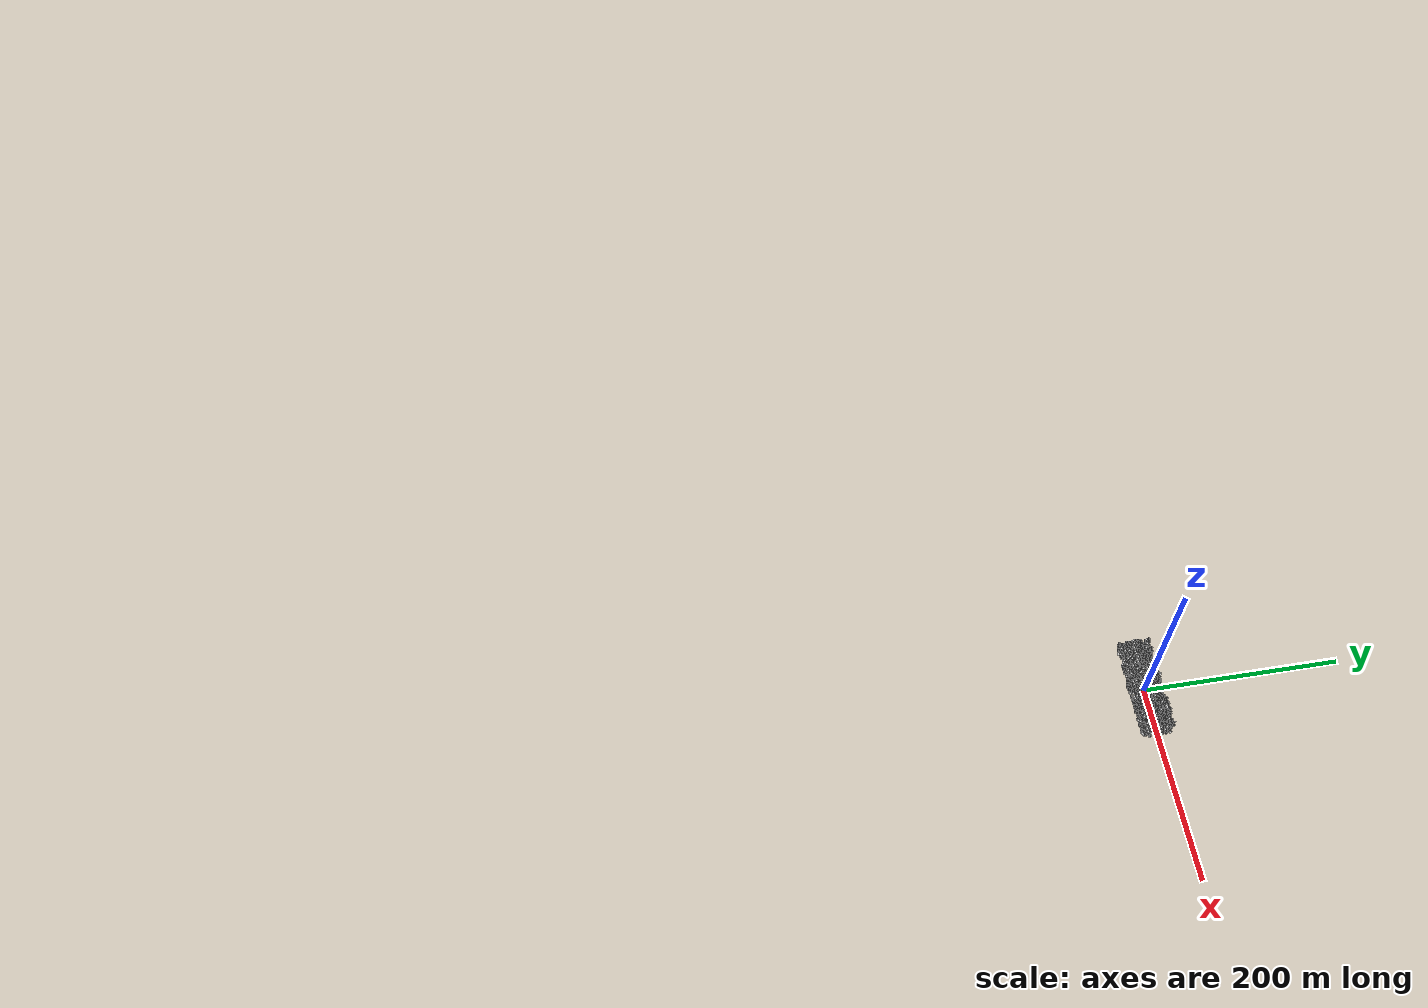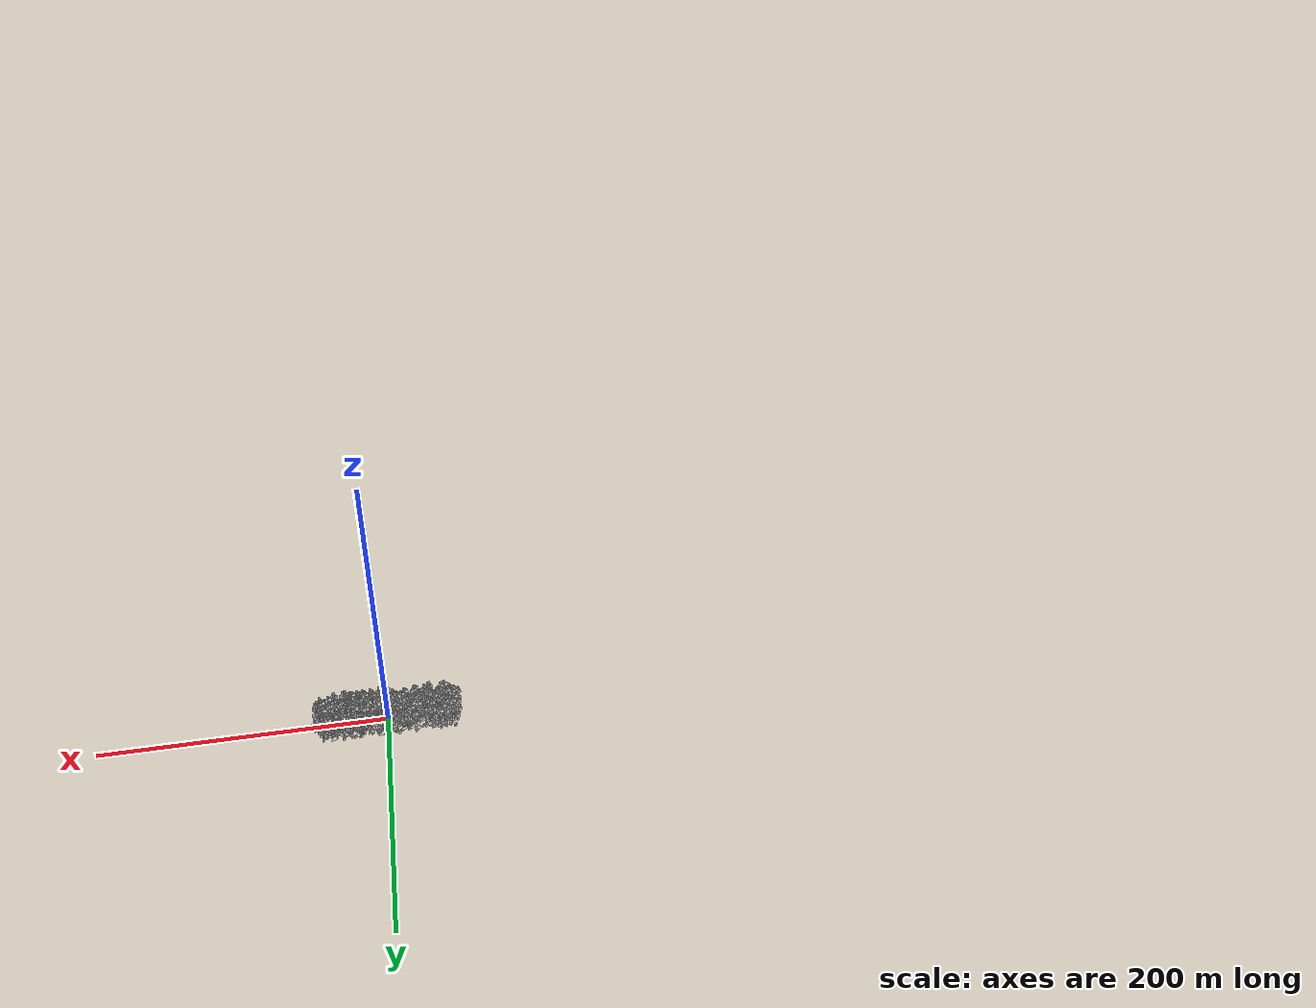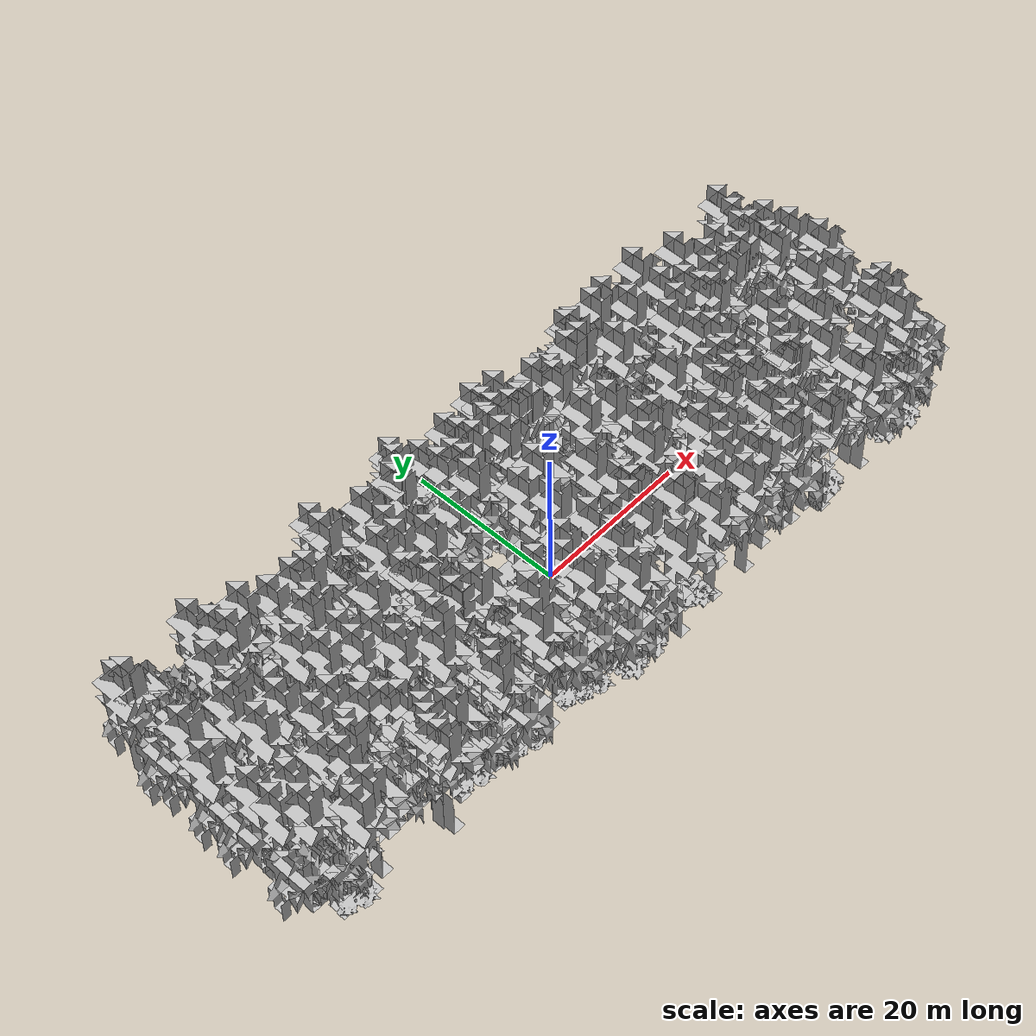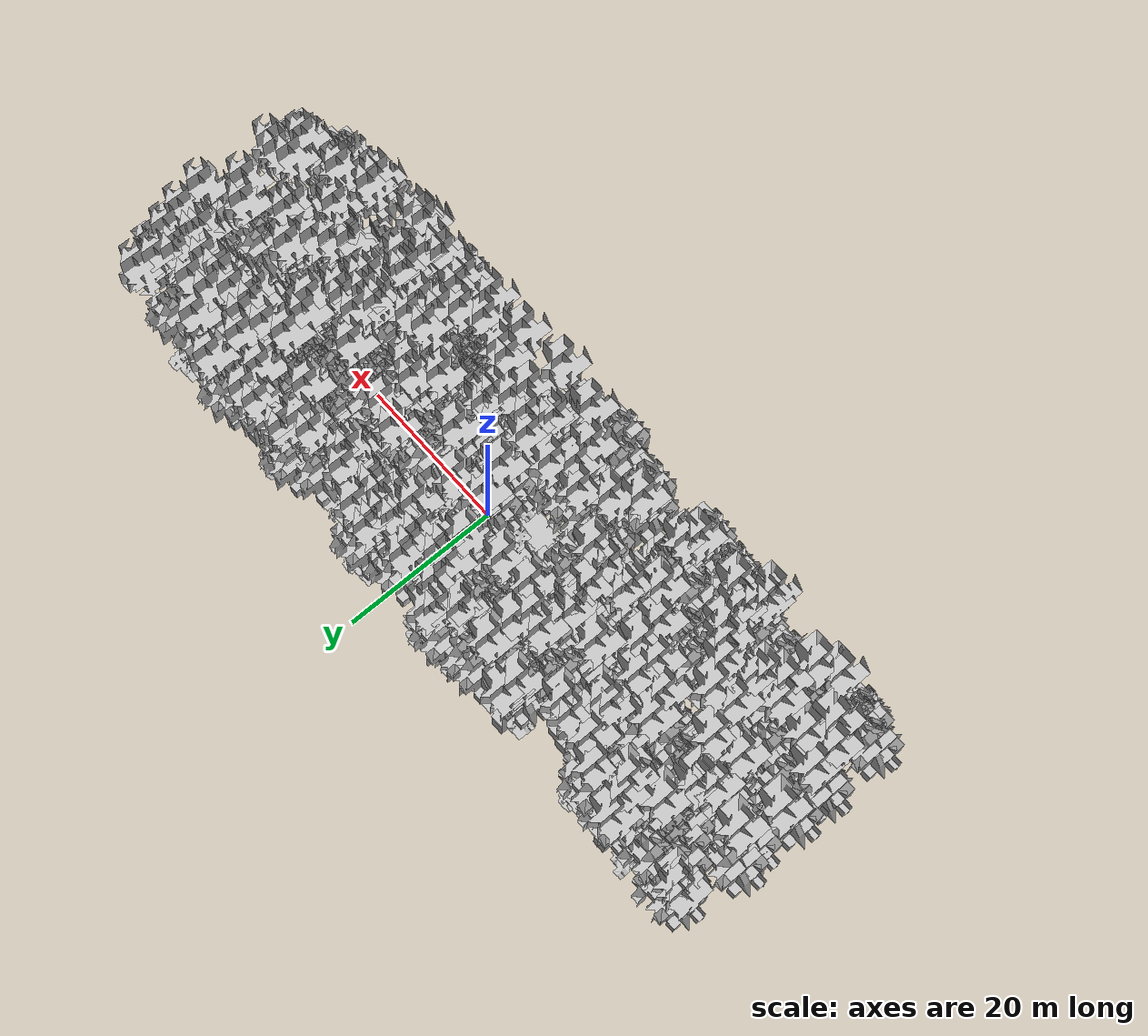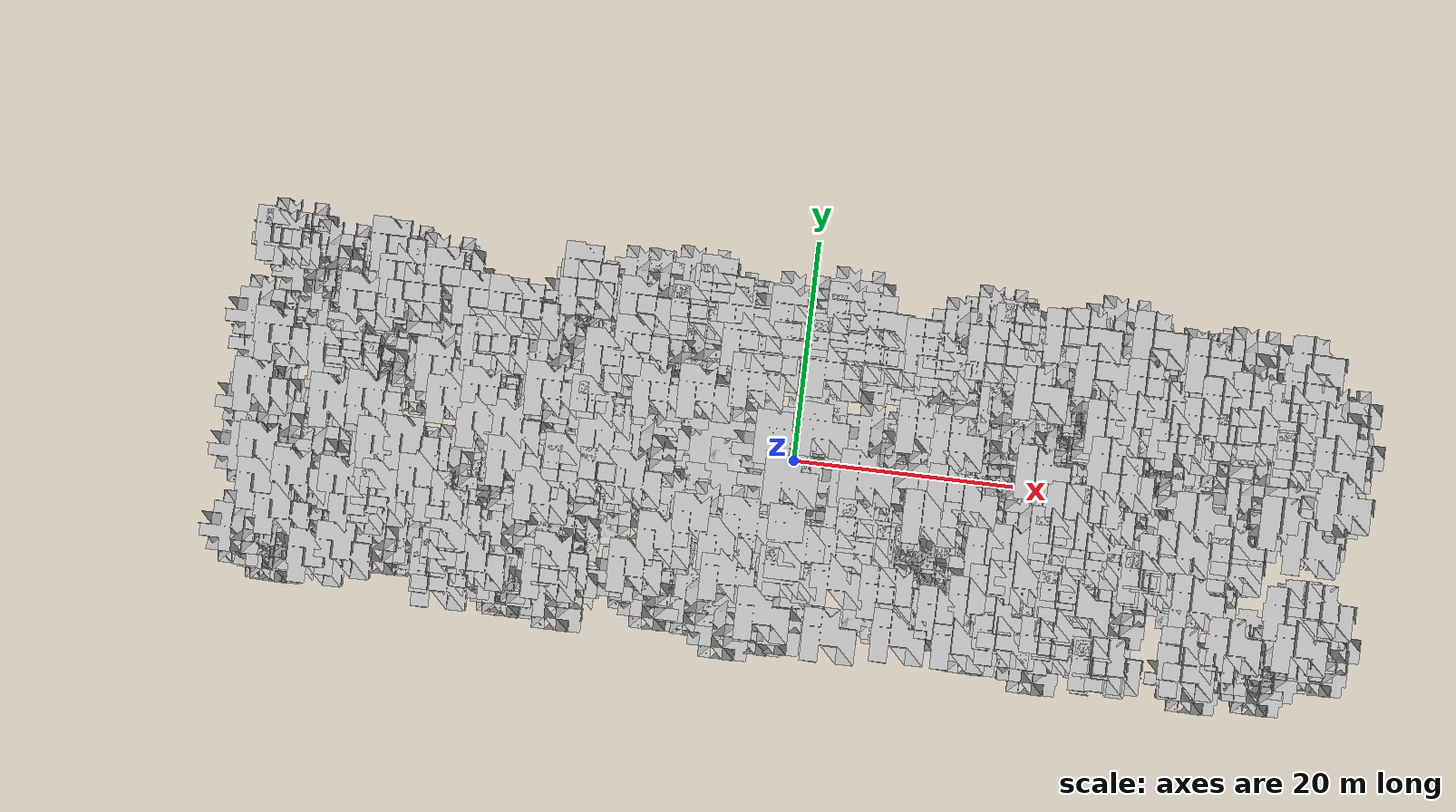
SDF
<sdf version="1.7">
    <world name="default">
        <plugin name="mrs_gazebo_static_transform_republisher_plugin" filename="libMrsGazeboCommonResources_StaticTransformRepublisher.so"/>
        <spherical_coordinates>
            <surface_model>EARTH_WGS84</surface_model>
            <latitude_deg>47.3977</latitude_deg>
            <longitude_deg>8.54559</longitude_deg>
            <elevation>0</elevation>
            <heading_deg>0</heading_deg>
        </spherical_coordinates>
        <physics name="default_physics" default="0" type="ode">
            <ode>
                <solver>
                    <type>quick</type>
                    <iters>10</iters>
                    <sor>1.3</sor>
                    <use_dynamic_moi_rescaling>0</use_dynamic_moi_rescaling>
                </solver>
                <constraints>
                    <cfm>0</cfm>
                    <erp>0.2</erp>
                    <contact_max_correcting_vel>1000</contact_max_correcting_vel>
                    <contact_surface_layer>0.001</contact_surface_layer>
                </constraints>
            </ode>
            <max_step_size>0.004</max_step_size>
            <real_time_factor>1</real_time_factor>
            <real_time_update_rate>250</real_time_update_rate>
        </physics>
        <scene>
            <shadows>0</shadows>
            <ambient>0.4 0.4 0.4 1</ambient>
            <background>0.7 0.7 0.7 1</background>
        </scene>
        <light name="sun" type="directional">
            <pose>0 0 1000 0.4 0.2 0</pose>
            <diffuse>1 1 1 1</diffuse>
            <specular>0.6 0.6 0.6 1</specular>
            <direction>0.1 0.1 -0.9</direction>
            <attenuation>
                <range>20</range>
                <constant>0.5</constant>
                <linear>0.01</linear>
                <quadratic>0.001</quadratic>
            </attenuation>
            <cast_shadows>1</cast_shadows>
            <spot>
                <inner_angle>0</inner_angle>
                <outer_angle>0</outer_angle>
                <falloff>0</falloff>
            </spot>
        </light>
        <model name="ground_plane">
            <static>1</static>
            <link name="link">
                <collision name="collision">
                    <pose>-50 0 0 0 -0 0</pose>
                    <geometry>
                        <plane>
                            <normal>0 0 1</normal>
                            <size>100 100</size>
                        </plane>
                    </geometry>
                    <surface>
                        <contact>
                            <ode>
                                <min_depth>0.01</min_depth>
                                <max_vel>0</max_vel>
                            </ode>
                        </contact>
                        <friction>
                            <ode/>
                            <torsional>
                                <ode/>
                            </torsional>
                        </friction>
                        <bounce/>
                    </surface>
                    <max_contacts>10</max_contacts>
                </collision>
                <visual name="grass">
                    <pose>0 0 0 0 -0 0</pose>
                    <cast_shadows>0</cast_shadows>
                    <geometry>
                        <mesh>
                            <scale>0.5814285714285714 0.18142857142857144 0.1</scale>
                            <uri>file://grass_plane/meshes/grass_plane.dae</uri>
                        </mesh>
                    </geometry>
                </visual>
                <self_collide>0</self_collide>
                <enable_wind>0</enable_wind>
                <kinematic>0</kinematic>
            </link>
        </model>
        <model name="the_void">
            <static>1</static>
            <link name="link">
                <pose>0 0 0.1 0 -0 0</pose>
                <visual name="the_void">
                    <pose>0 0 2 0 -0 0</pose>
                    <geometry>
                        <sphere>
                            <radius>0.25</radius>
                        </sphere>
                    </geometry>
                    <material>
                        <script>
                            <uri>file://media/materials/scripts/Gazebo.material</uri>
                            <name>Gazebo/Black</name>
                        </script>
                    </material>
                </visual>
                <self_collide>0</self_collide>
                <enable_wind>0</enable_wind>
                <kinematic>0</kinematic>
            </link>
            <pose>-1000 -1000 0 0 -0 0</pose>
        </model>
        <gui fullscreen="0">
            <camera name="camera">
                <pose>35.1577 98.6044 40.0204 0 0.407996 -1.99761</pose>
                <view_controller>orbit</view_controller>
                <projection_type>perspective</projection_type>
            </camera>
        </gui>
        <plugin name="mrs_gazebo_rviz_cam_synchronizer" filename="libMrsGazeboCommonResources_RvizCameraSynchronizer.so">
            <target_frame_id>gazebo_user_camera</target_frame_id>
            <world_origin_frame_id>uav1/gps_origin</world_origin_frame_id>
            <frame_to_follow>uav1</frame_to_follow>
        </plugin>
        <gravity>0 0 -9.8066</gravity>
        <magnetic_field>6e-06 2.3e-05 -4.2e-05</magnetic_field>
        <atmosphere type="adiabatic"/>
        <wind/>
        <model name="Tree 0">
            <static>1</static>
            <pose>33.289444481673556 -5.185459640180708 0 1.57079 -0 0</pose>
            <link name="link">
                <pose>0 0 0 0 -0 0</pose>
                <collision name="collision">
                    <geometry>
                        <mesh>
                            <scale>3.5 5 3.5</scale>
                            <uri>model://tree_2/meshes/tree_2.obj</uri>
                        </mesh>
                    </geometry>
                    <max_contacts>10</max_contacts>
                    <surface>
                        <contact>
                            <ode/>
                        </contact>
                        <bounce/>
                        <friction>
                            <torsional>
                                <ode/>
                            </torsional>
                            <ode/>
                        </friction>
                    </surface>
                </collision>
                <visual name="visual">
                    <geometry>
                        <mesh>
                            <scale>3.5 5 3.5</scale>
                            <uri>model://tree_2/meshes/tree_2.obj</uri>
                        </mesh>
                    </geometry>
                </visual>
                <self_collide>0</self_collide>
                <enable_wind>0</enable_wind>
                <kinematic>0</kinematic>
            </link>
        </model>
        <model name="Tree 1">
            <static>1</static>
            <pose>6.492176944869151 13.321462057910974 0 1.57079 -0 0</pose>
            <link name="link">
                <pose>0 0 0 0 -0 0</pose>
                <collision name="collision">
                    <geometry>
                        <mesh>
                            <scale>3.5 5 3.5</scale>
                            <uri>model://tree_9/meshes/tree_9.obj</uri>
                        </mesh>
                    </geometry>
                    <max_contacts>10</max_contacts>
                    <surface>
                        <contact>
                            <ode/>
                        </contact>
                        <bounce/>
                        <friction>
                            <torsional>
                                <ode/>
                            </torsional>
                            <ode/>
                        </friction>
                    </surface>
                </collision>
                <visual name="visual">
                    <geometry>
                        <mesh>
                            <scale>3.5 5 3.5</scale>
                            <uri>model://tree_9/meshes/tree_9.obj</uri>
                        </mesh>
                    </geometry>
                </visual>
                <self_collide>0</self_collide>
                <enable_wind>0</enable_wind>
                <kinematic>0</kinematic>
            </link>
        </model>
        <model name="Tree 2">
            <static>1</static>
            <pose>24.65917798859826 -1.2980579722668804 0 1.57079 -0 0</pose>
            <link name="link">
                <pose>0 0 0 0 -0 0</pose>
                <collision name="collision">
                    <geometry>
                        <mesh>
                            <scale>3.5 5 3.5</scale>
                            <uri>model://tree_9/meshes/tree_9.obj</uri>
                        </mesh>
                    </geometry>
                    <max_contacts>10</max_contacts>
                    <surface>
                        <contact>
                            <ode/>
                        </contact>
                        <bounce/>
                        <friction>
                            <torsional>
                                <ode/>
                            </torsional>
                            <ode/>
                        </friction>
                    </surface>
                </collision>
                <visual name="visual">
                    <geometry>
                        <mesh>
                            <scale>3.5 5 3.5</scale>
                            <uri>model://tree_9/meshes/tree_9.obj</uri>
                        </mesh>
                    </geometry>
                </visual>
                <self_collide>0</self_collide>
                <enable_wind>0</enable_wind>
                <kinematic>0</kinematic>
            </link>
        </model>
        <model name="Tree 3">
            <static>1</static>
            <pose>36.6291474375721 -10.39728852935579 0 1.57079 -0 0</pose>
            <link name="link">
                <pose>0 0 0 0 -0 0</pose>
                <collision name="collision">
                    <geometry>
                        <mesh>
                            <scale>3 2 3</scale>
                            <uri>model://tree_3/meshes/tree_3.obj</uri>
                        </mesh>
                    </geometry>
                    <max_contacts>10</max_contacts>
                    <surface>
                        <contact>
                            <ode/>
                        </contact>
                        <bounce/>
                        <friction>
                            <torsional>
                                <ode/>
                            </torsional>
                            <ode/>
                        </friction>
                    </surface>
                </collision>
                <visual name="visual">
                    <geometry>
                        <mesh>
                            <scale>3 2 3</scale>
                            <uri>model://tree_3/meshes/tree_3.obj</uri>
                        </mesh>
                    </geometry>
                </visual>
                <self_collide>0</self_collide>
                <enable_wind>0</enable_wind>
                <kinematic>0</kinematic>
            </link>
        </model>
        <model name="Tree 4">
            <static>1</static>
            <pose>29.403178628892164 -2.2712187707758407 0 1.57079 -0 0</pose>
            <link name="link">
                <pose>0 0 0 0 -0 0</pose>
                <collision name="collision">
                    <geometry>
                        <mesh>
                            <scale>3.5 5 3.5</scale>
                            <uri>model://tree_2/meshes/tree_2.obj</uri>
                        </mesh>
                    </geometry>
                    <max_contacts>10</max_contacts>
                    <surface>
                        <contact>
                            <ode/>
                        </contact>
                        <bounce/>
                        <friction>
                            <torsional>
                                <ode/>
                            </torsional>
                            <ode/>
                        </friction>
                    </surface>
                </collision>
                <visual name="visual">
                    <geometry>
                        <mesh>
                            <scale>3.5 5 3.5</scale>
                            <uri>model://tree_2/meshes/tree_2.obj</uri>
                        </mesh>
                    </geometry>
                </visual>
                <self_collide>0</self_collide>
                <enable_wind>0</enable_wind>
                <kinematic>0</kinematic>
            </link>
        </model>
        <model name="Tree 5">
            <static>1</static>
            <pose>-5.264318395612278 13.550032690171253 0 1.57079 -0 0</pose>
            <link name="link">
                <pose>0 0 0 0 -0 0</pose>
                <collision name="collision">
                    <geometry>
                        <mesh>
                            <scale>4 2.5 4</scale>
                            <uri>model://tree_1/meshes/tree_1.obj</uri>
                        </mesh>
                    </geometry>
                    <max_contacts>10</max_contacts>
                    <surface>
                        <contact>
                            <ode/>
                        </contact>
                        <bounce/>
                        <friction>
                            <torsional>
                                <ode/>
                            </torsional>
                            <ode/>
                        </friction>
                    </surface>
                </collision>
                <visual name="visual">
                    <geometry>
                        <mesh>
                            <scale>4 2.5 4</scale>
                            <uri>model://tree_1/meshes/tree_1.obj</uri>
                        </mesh>
                    </geometry>
                </visual>
                <self_collide>0</self_collide>
                <enable_wind>0</enable_wind>
                <kinematic>0</kinematic>
            </link>
        </model>
        <model name="Tree 6">
            <static>1</static>
            <pose>28.48274567532701 2.295979283848528 0 1.57079 -0 0</pose>
            <link name="link">
                <pose>0 0 0 0 -0 0</pose>
                <collision name="collision">
                    <geometry>
                        <mesh>
                            <scale>3.5 5 3.5</scale>
                            <uri>model://tree_2/meshes/tree_2.obj</uri>
                        </mesh>
                    </geometry>
                    <max_contacts>10</max_contacts>
                    <surface>
                        <contact>
                            <ode/>
                        </contact>
                        <bounce/>
                        <friction>
                            <torsional>
                                <ode/>
                            </torsional>
                            <ode/>
                        </friction>
                    </surface>
                </collision>
                <visual name="visual">
                    <geometry>
                        <mesh>
                            <scale>3.5 5 3.5</scale>
                            <uri>model://tree_2/meshes/tree_2.obj</uri>
                        </mesh>
                    </geometry>
                </visual>
                <self_collide>0</self_collide>
                <enable_wind>0</enable_wind>
                <kinematic>0</kinematic>
            </link>
        </model>
        <model name="Tree 7">
            <static>1</static>
            <pose>-24.72526195733973 -13.164197608340134 0 1.57079 -0 0</pose>
            <link name="link">
                <pose>0 0 0 0 -0 0</pose>
                <collision name="collision">
                    <geometry>
                        <mesh>
                            <scale>3.5 5 3.5</scale>
                            <uri>model://tree_2/meshes/tree_2.obj</uri>
                        </mesh>
                    </geometry>
                    <max_contacts>10</max_contacts>
                    <surface>
                        <contact>
                            <ode/>
                        </contact>
                        <bounce/>
                        <friction>
                            <torsional>
                                <ode/>
                            </torsional>
                            <ode/>
                        </friction>
                    </surface>
                </collision>
                <visual name="visual">
                    <geometry>
                        <mesh>
                            <scale>3.5 5 3.5</scale>
                            <uri>model://tree_2/meshes/tree_2.obj</uri>
                        </mesh>
                    </geometry>
                </visual>
                <self_collide>0</self_collide>
                <enable_wind>0</enable_wind>
                <kinematic>0</kinematic>
            </link>
        </model>
        <model name="Tree 8">
            <static>1</static>
            <pose>38.22960909885768 6.948712087301086 0 1.57079 -0 0</pose>
            <link name="link">
                <pose>0 0 0 0 -0 0</pose>
                <collision name="collision">
                    <geometry>
                        <mesh>
                            <scale>3.5 5 3.5</scale>
                            <uri>model://tree_9/meshes/tree_9.obj</uri>
                        </mesh>
                    </geometry>
                    <max_contacts>10</max_contacts>
                    <surface>
                        <contact>
                            <ode/>
                        </contact>
                        <bounce/>
                        <friction>
                            <torsional>
                                <ode/>
                            </torsional>
                            <ode/>
                        </friction>
                    </surface>
                </collision>
                <visual name="visual">
                    <geometry>
                        <mesh>
                            <scale>3.5 5 3.5</scale>
                            <uri>model://tree_9/meshes/tree_9.obj</uri>
                        </mesh>
                    </geometry>
                </visual>
                <self_collide>0</self_collide>
                <enable_wind>0</enable_wind>
                <kinematic>0</kinematic>
            </link>
        </model>
        <model name="Tree 9">
            <static>1</static>
            <pose>15.429976537966382 -2.6154416032176186 0 1.57079 -0 0</pose>
            <link name="link">
                <pose>0 0 0 0 -0 0</pose>
                <collision name="collision">
                    <geometry>
                        <mesh>
                            <scale>3.5 5 3.5</scale>
                            <uri>model://tree_2/meshes/tree_2.obj</uri>
                        </mesh>
                    </geometry>
                    <max_contacts>10</max_contacts>
                    <surface>
                        <contact>
                            <ode/>
                        </contact>
                        <bounce/>
                        <friction>
                            <torsional>
                                <ode/>
                            </torsional>
                            <ode/>
                        </friction>
                    </surface>
                </collision>
                <visual name="visual">
                    <geometry>
                        <mesh>
                            <scale>3.5 5 3.5</scale>
                            <uri>model://tree_2/meshes/tree_2.obj</uri>
                        </mesh>
                    </geometry>
                </visual>
                <self_collide>0</self_collide>
                <enable_wind>0</enable_wind>
                <kinematic>0</kinematic>
            </link>
        </model>
        <model name="Tree 10">
            <static>1</static>
            <pose>-36.72252852309552 13.407077684974691 0 1.57079 -0 0</pose>
            <link name="link">
                <pose>0 0 0 0 -0 0</pose>
                <collision name="collision">
                    <geometry>
                        <mesh>
                            <scale>3 2 3</scale>
                            <uri>model://tree_3/meshes/tree_3.obj</uri>
                        </mesh>
                    </geometry>
                    <max_contacts>10</max_contacts>
                    <surface>
                        <contact>
                            <ode/>
                        </contact>
                        <bounce/>
                        <friction>
                            <torsional>
                                <ode/>
                            </torsional>
                            <ode/>
                        </friction>
                    </surface>
                </collision>
                <visual name="visual">
                    <geometry>
                        <mesh>
                            <scale>3 2 3</scale>
                            <uri>model://tree_3/meshes/tree_3.obj</uri>
                        </mesh>
                    </geometry>
                </visual>
                <self_collide>0</self_collide>
                <enable_wind>0</enable_wind>
                <kinematic>0</kinematic>
            </link>
        </model>
        <model name="Tree 11">
            <static>1</static>
            <pose>-25.217248290302596 5.485725349668002 0 1.57079 -0 0</pose>
            <link name="link">
                <pose>0 0 0 0 -0 0</pose>
                <collision name="collision">
                    <geometry>
                        <mesh>
                            <scale>3 2 3</scale>
                            <uri>model://tree_3/meshes/tree_3.obj</uri>
                        </mesh>
                    </geometry>
                    <max_contacts>10</max_contacts>
                    <surface>
                        <contact>
                            <ode/>
                        </contact>
                        <bounce/>
                        <friction>
                            <torsional>
                                <ode/>
                            </torsional>
                            <ode/>
                        </friction>
                    </surface>
                </collision>
                <visual name="visual">
                    <geometry>
                        <mesh>
                            <scale>3 2 3</scale>
                            <uri>model://tree_3/meshes/tree_3.obj</uri>
                        </mesh>
                    </geometry>
                </visual>
                <self_collide>0</self_collide>
                <enable_wind>0</enable_wind>
                <kinematic>0</kinematic>
            </link>
        </model>
        <model name="Tree 12">
            <static>1</static>
            <pose>-1.50159747943853 -9.879959348353642 0 1.57079 -0 0</pose>
            <link name="link">
                <pose>0 0 0 0 -0 0</pose>
                <collision name="collision">
                    <geometry>
                        <mesh>
                            <scale>3.5 5 3.5</scale>
                            <uri>model://tree_2/meshes/tree_2.obj</uri>
                        </mesh>
                    </geometry>
                    <max_contacts>10</max_contacts>
                    <surface>
                        <contact>
                            <ode/>
                        </contact>
                        <bounce/>
                        <friction>
                            <torsional>
                                <ode/>
                            </torsional>
                            <ode/>
                        </friction>
                    </surface>
                </collision>
                <visual name="visual">
                    <geometry>
                        <mesh>
                            <scale>3.5 5 3.5</scale>
                            <uri>model://tree_2/meshes/tree_2.obj</uri>
                        </mesh>
                    </geometry>
                </visual>
                <self_collide>0</self_collide>
                <enable_wind>0</enable_wind>
                <kinematic>0</kinematic>
            </link>
        </model>
        <model name="Tree 13">
            <static>1</static>
            <pose>-4.208597897966072 6.732384200677938 0 1.57079 -0 0</pose>
            <link name="link">
                <pose>0 0 0 0 -0 0</pose>
                <collision name="collision">
                    <geometry>
                        <mesh>
                            <scale>3.5 5 3.5</scale>
                            <uri>model://tree_9/meshes/tree_9.obj</uri>
                        </mesh>
                    </geometry>
                    <max_contacts>10</max_contacts>
                    <surface>
                        <contact>
                            <ode/>
                        </contact>
                        <bounce/>
                        <friction>
                            <torsional>
                                <ode/>
                            </torsional>
                            <ode/>
                        </friction>
                    </surface>
                </collision>
                <visual name="visual">
                    <geometry>
                        <mesh>
                            <scale>3.5 5 3.5</scale>
                            <uri>model://tree_9/meshes/tree_9.obj</uri>
                        </mesh>
                    </geometry>
                </visual>
                <self_collide>0</self_collide>
                <enable_wind>0</enable_wind>
                <kinematic>0</kinematic>
            </link>
        </model>
        <model name="Tree 14">
            <static>1</static>
            <pose>38.1280172015788 -7.264740103736585 0 1.57079 -0 0</pose>
            <link name="link">
                <pose>0 0 0 0 -0 0</pose>
                <collision name="collision">
                    <geometry>
                        <mesh>
                            <scale>3.5 5 3.5</scale>
                            <uri>model://tree_2/meshes/tree_2.obj</uri>
                        </mesh>
                    </geometry>
                    <max_contacts>10</max_contacts>
                    <surface>
                        <contact>
                            <ode/>
                        </contact>
                        <bounce/>
                        <friction>
                            <torsional>
                                <ode/>
                            </torsional>
                            <ode/>
                        </friction>
                    </surface>
                </collision>
                <visual name="visual">
                    <geometry>
                        <mesh>
                            <scale>3.5 5 3.5</scale>
                            <uri>model://tree_2/meshes/tree_2.obj</uri>
                        </mesh>
                    </geometry>
                </visual>
                <self_collide>0</self_collide>
                <enable_wind>0</enable_wind>
                <kinematic>0</kinematic>
            </link>
        </model>
        <model name="Tree 15">
            <static>1</static>
            <pose>41.57837490177708 1.7691573282104862 0 1.57079 -0 0</pose>
            <link name="link">
                <pose>0 0 0 0 -0 0</pose>
                <collision name="collision">
                    <geometry>
                        <mesh>
                            <scale>3 2 3</scale>
                            <uri>model://tree_3/meshes/tree_3.obj</uri>
                        </mesh>
                    </geometry>
                    <max_contacts>10</max_contacts>
                    <surface>
                        <contact>
                            <ode/>
                        </contact>
                        <bounce/>
                        <friction>
                            <torsional>
                                <ode/>
                            </torsional>
                            <ode/>
                        </friction>
                    </surface>
                </collision>
                <visual name="visual">
                    <geometry>
                        <mesh>
                            <scale>3 2 3</scale>
                            <uri>model://tree_3/meshes/tree_3.obj</uri>
                        </mesh>
                    </geometry>
                </visual>
                <self_collide>0</self_collide>
                <enable_wind>0</enable_wind>
                <kinematic>0</kinematic>
            </link>
        </model>
        <model name="Tree 16">
            <static>1</static>
            <pose>-10.024421451301343 12.044135002311886 0 1.57079 -0 0</pose>
            <link name="link">
                <pose>0 0 0 0 -0 0</pose>
                <collision name="collision">
                    <geometry>
                        <mesh>
                            <scale>3.5 5 3.5</scale>
                            <uri>model://tree_9/meshes/tree_9.obj</uri>
                        </mesh>
                    </geometry>
                    <max_contacts>10</max_contacts>
                    <surface>
                        <contact>
                            <ode/>
                        </contact>
                        <bounce/>
                        <friction>
                            <torsional>
                                <ode/>
                            </torsional>
                            <ode/>
                        </friction>
                    </surface>
                </collision>
                <visual name="visual">
                    <geometry>
                        <mesh>
                            <scale>3.5 5 3.5</scale>
                            <uri>model://tree_9/meshes/tree_9.obj</uri>
                        </mesh>
                    </geometry>
                </visual>
                <self_collide>0</self_collide>
                <enable_wind>0</enable_wind>
                <kinematic>0</kinematic>
            </link>
        </model>
        <model name="Tree 17">
            <static>1</static>
            <pose>-17.703643088189775 -3.0690221012463255 0 1.57079 -0 0</pose>
            <link name="link">
                <pose>0 0 0 0 -0 0</pose>
                <collision name="collision">
                    <geometry>
                        <mesh>
                            <scale>4 2.5 4</scale>
                            <uri>model://tree_1/meshes/tree_1.obj</uri>
                        </mesh>
                    </geometry>
                    <max_contacts>10</max_contacts>
                    <surface>
                        <contact>
                            <ode/>
                        </contact>
                        <bounce/>
                        <friction>
                            <torsional>
                                <ode/>
                            </torsional>
                            <ode/>
                        </friction>
                    </surface>
                </collision>
                <visual name="visual">
                    <geometry>
                        <mesh>
                            <scale>4 2.5 4</scale>
                            <uri>model://tree_1/meshes/tree_1.obj</uri>
                        </mesh>
                    </geometry>
                </visual>
                <self_collide>0</self_collide>
                <enable_wind>0</enable_wind>
                <kinematic>0</kinematic>
            </link>
        </model>
        <model name="Tree 18">
            <static>1</static>
            <pose>-31.97918182394424 4.878873976047316 0 1.57079 -0 0</pose>
            <link name="link">
                <pose>0 0 0 0 -0 0</pose>
                <collision name="collision">
                    <geometry>
                        <mesh>
                            <scale>3.5 5 3.5</scale>
                            <uri>model://tree_9/meshes/tree_9.obj</uri>
                        </mesh>
                    </geometry>
                    <max_contacts>10</max_contacts>
                    <surface>
                        <contact>
                            <ode/>
                        </contact>
                        <bounce/>
                        <friction>
                            <torsional>
                                <ode/>
                            </torsional>
                            <ode/>
                        </friction>
                    </surface>
                </collision>
                <visual name="visual">
                    <geometry>
                        <mesh>
                            <scale>3.5 5 3.5</scale>
                            <uri>model://tree_9/meshes/tree_9.obj</uri>
                        </mesh>
                    </geometry>
                </visual>
                <self_collide>0</self_collide>
                <enable_wind>0</enable_wind>
                <kinematic>0</kinematic>
            </link>
        </model>
        <model name="Tree 19">
            <static>1</static>
            <pose>-36.90230717961292 13.916196201880688 0 1.57079 -0 0</pose>
            <link name="link">
                <pose>0 0 0 0 -0 0</pose>
                <collision name="collision">
                    <geometry>
                        <mesh>
                            <scale>3.5 5 3.5</scale>
                            <uri>model://tree_2/meshes/tree_2.obj</uri>
                        </mesh>
                    </geometry>
                    <max_contacts>10</max_contacts>
                    <surface>
                        <contact>
                            <ode/>
                        </contact>
                        <bounce/>
                        <friction>
                            <torsional>
                                <ode/>
                            </torsional>
                            <ode/>
                        </friction>
                    </surface>
                </collision>
                <visual name="visual">
                    <geometry>
                        <mesh>
                            <scale>3.5 5 3.5</scale>
                            <uri>model://tree_2/meshes/tree_2.obj</uri>
                        </mesh>
                    </geometry>
                </visual>
                <self_collide>0</self_collide>
                <enable_wind>0</enable_wind>
                <kinematic>0</kinematic>
            </link>
        </model>
        <model name="Tree 20">
            <static>1</static>
            <pose>-33.89867738807947 -2.275696835074209 0 1.57079 -0 0</pose>
            <link name="link">
                <pose>0 0 0 0 -0 0</pose>
                <collision name="collision">
                    <geometry>
                        <mesh>
                            <scale>3.5 5 3.5</scale>
                            <uri>model://tree_9/meshes/tree_9.obj</uri>
                        </mesh>
                    </geometry>
                    <max_contacts>10</max_contacts>
                    <surface>
                        <contact>
                            <ode/>
                        </contact>
                        <bounce/>
                        <friction>
                            <torsional>
                                <ode/>
                            </torsional>
                            <ode/>
                        </friction>
                    </surface>
                </collision>
                <visual name="visual">
                    <geometry>
                        <mesh>
                            <scale>3.5 5 3.5</scale>
                            <uri>model://tree_9/meshes/tree_9.obj</uri>
                        </mesh>
                    </geometry>
                </visual>
                <self_collide>0</self_collide>
                <enable_wind>0</enable_wind>
                <kinematic>0</kinematic>
            </link>
        </model>
        <model name="Tree 21">
            <static>1</static>
            <pose>28.092453200630075 3.1566407805987637 0 1.57079 -0 0</pose>
            <link name="link">
                <pose>0 0 0 0 -0 0</pose>
                <collision name="collision">
                    <geometry>
                        <mesh>
                            <scale>3.5 5 3.5</scale>
                            <uri>model://tree_9/meshes/tree_9.obj</uri>
                        </mesh>
                    </geometry>
                    <max_contacts>10</max_contacts>
                    <surface>
                        <contact>
                            <ode/>
                        </contact>
                        <bounce/>
                        <friction>
                            <torsional>
                                <ode/>
                            </torsional>
                            <ode/>
                        </friction>
                    </surface>
                </collision>
                <visual name="visual">
                    <geometry>
                        <mesh>
                            <scale>3.5 5 3.5</scale>
                            <uri>model://tree_9/meshes/tree_9.obj</uri>
                        </mesh>
                    </geometry>
                </visual>
                <self_collide>0</self_collide>
                <enable_wind>0</enable_wind>
                <kinematic>0</kinematic>
            </link>
        </model>
        <model name="Tree 22">
            <static>1</static>
            <pose>5.731041198923485 10.343546982625135 0 1.57079 -0 0</pose>
            <link name="link">
                <pose>0 0 0 0 -0 0</pose>
                <collision name="collision">
                    <geometry>
                        <mesh>
                            <scale>3.5 5 3.5</scale>
                            <uri>model://tree_9/meshes/tree_9.obj</uri>
                        </mesh>
                    </geometry>
                    <max_contacts>10</max_contacts>
                    <surface>
                        <contact>
                            <ode/>
                        </contact>
                        <bounce/>
                        <friction>
                            <torsional>
                                <ode/>
                            </torsional>
                            <ode/>
                        </friction>
                    </surface>
                </collision>
                <visual name="visual">
                    <geometry>
                        <mesh>
                            <scale>3.5 5 3.5</scale>
                            <uri>model://tree_9/meshes/tree_9.obj</uri>
                        </mesh>
                    </geometry>
                </visual>
                <self_collide>0</self_collide>
                <enable_wind>0</enable_wind>
                <kinematic>0</kinematic>
            </link>
        </model>
        <model name="Tree 23">
            <static>1</static>
            <pose>40.609137790138675 9.81755615080386 0 1.57079 -0 0</pose>
            <link name="link">
                <pose>0 0 0 0 -0 0</pose>
                <collision name="collision">
                    <geometry>
                        <mesh>
                            <scale>3.5 5 3.5</scale>
                            <uri>model://tree_2/meshes/tree_2.obj</uri>
                        </mesh>
                    </geometry>
                    <max_contacts>10</max_contacts>
                    <surface>
                        <contact>
                            <ode/>
                        </contact>
                        <bounce/>
                        <friction>
                            <torsional>
                                <ode/>
                            </torsional>
                            <ode/>
                        </friction>
                    </surface>
                </collision>
                <visual name="visual">
                    <geometry>
                        <mesh>
                            <scale>3.5 5 3.5</scale>
                            <uri>model://tree_2/meshes/tree_2.obj</uri>
                        </mesh>
                    </geometry>
                </visual>
                <self_collide>0</self_collide>
                <enable_wind>0</enable_wind>
                <kinematic>0</kinematic>
            </link>
        </model>
        <model name="Tree 24">
            <static>1</static>
            <pose>33.88363590075572 5.533667802592195 0 1.57079 -0 0</pose>
            <link name="link">
                <pose>0 0 0 0 -0 0</pose>
                <collision name="collision">
                    <geometry>
                        <mesh>
                            <scale>3.5 5 3.5</scale>
                            <uri>model://tree_9/meshes/tree_9.obj</uri>
                        </mesh>
                    </geometry>
                    <max_contacts>10</max_contacts>
                    <surface>
                        <contact>
                            <ode/>
                        </contact>
                        <bounce/>
                        <friction>
                            <torsional>
                                <ode/>
                            </torsional>
                            <ode/>
                        </friction>
                    </surface>
                </collision>
                <visual name="visual">
                    <geometry>
                        <mesh>
                            <scale>3.5 5 3.5</scale>
                            <uri>model://tree_9/meshes/tree_9.obj</uri>
                        </mesh>
                    </geometry>
                </visual>
                <self_collide>0</self_collide>
                <enable_wind>0</enable_wind>
                <kinematic>0</kinematic>
            </link>
        </model>
        <model name="Tree 25">
            <static>1</static>
            <pose>-6.026550712602656 12.424141168342885 0 1.57079 -0 0</pose>
            <link name="link">
                <pose>0 0 0 0 -0 0</pose>
                <collision name="collision">
                    <geometry>
                        <mesh>
                            <scale>3.5 5 3.5</scale>
                            <uri>model://tree_9/meshes/tree_9.obj</uri>
                        </mesh>
                    </geometry>
                    <max_contacts>10</max_contacts>
                    <surface>
                        <contact>
                            <ode/>
                        </contact>
                        <bounce/>
                        <friction>
                            <torsional>
                                <ode/>
                            </torsional>
                            <ode/>
                        </friction>
                    </surface>
                </collision>
                <visual name="visual">
                    <geometry>
                        <mesh>
                            <scale>3.5 5 3.5</scale>
                            <uri>model://tree_9/meshes/tree_9.obj</uri>
                        </mesh>
                    </geometry>
                </visual>
                <self_collide>0</self_collide>
                <enable_wind>0</enable_wind>
                <kinematic>0</kinematic>
            </link>
        </model>
        <model name="Tree 26">
            <static>1</static>
            <pose>19.39115049102091 9.248823598836541 0 1.57079 -0 0</pose>
            <link name="link">
                <pose>0 0 0 0 -0 0</pose>
                <collision name="collision">
                    <geometry>
                        <mesh>
                            <scale>3.5 5 3.5</scale>
                            <uri>model://tree_2/meshes/tree_2.obj</uri>
                        </mesh>
                    </geometry>
                    <max_contacts>10</max_contacts>
                    <surface>
                        <contact>
                            <ode/>
                        </contact>
                        <bounce/>
                        <friction>
                            <torsional>
                                <ode/>
                            </torsional>
                            <ode/>
                        </friction>
                    </surface>
                </collision>
                <visual name="visual">
                    <geometry>
                        <mesh>
                            <scale>3.5 5 3.5</scale>
                            <uri>model://tree_2/meshes/tree_2.obj</uri>
                        </mesh>
                    </geometry>
                </visual>
                <self_collide>0</self_collide>
                <enable_wind>0</enable_wind>
                <kinematic>0</kinematic>
            </link>
        </model>
        <model name="Tree 27">
            <static>1</static>
            <pose>-19.66256483486999 -14.122985390510822 0 1.57079 -0 0</pose>
            <link name="link">
                <pose>0 0 0 0 -0 0</pose>
                <collision name="collision">
                    <geometry>
                        <mesh>
                            <scale>3.5 5 3.5</scale>
                            <uri>model://tree_2/meshes/tree_2.obj</uri>
                        </mesh>
                    </geometry>
                    <max_contacts>10</max_contacts>
                    <surface>
                        <contact>
                            <ode/>
                        </contact>
                        <bounce/>
                        <friction>
                            <torsional>
                                <ode/>
                            </torsional>
                            <ode/>
                        </friction>
                    </surface>
                </collision>
                <visual name="visual">
                    <geometry>
                        <mesh>
                            <scale>3.5 5 3.5</scale>
                            <uri>model://tree_2/meshes/tree_2.obj</uri>
                        </mesh>
                    </geometry>
                </visual>
                <self_collide>0</self_collide>
                <enable_wind>0</enable_wind>
                <kinematic>0</kinematic>
            </link>
        </model>
        <model name="Tree 28">
            <static>1</static>
            <pose>-43.30894276052413 -8.165332301098179 0 1.57079 -0 0</pose>
            <link name="link">
                <pose>0 0 0 0 -0 0</pose>
                <collision name="collision">
                    <geometry>
                        <mesh>
                            <scale>3 2 3</scale>
                            <uri>model://tree_3/meshes/tree_3.obj</uri>
                        </mesh>
                    </geometry>
                    <max_contacts>10</max_contacts>
                    <surface>
                        <contact>
                            <ode/>
                        </contact>
                        <bounce/>
                        <friction>
                            <torsional>
                                <ode/>
                            </torsional>
                            <ode/>
                        </friction>
                    </surface>
                </collision>
                <visual name="visual">
                    <geometry>
                        <mesh>
                            <scale>3 2 3</scale>
                            <uri>model://tree_3/meshes/tree_3.obj</uri>
                        </mesh>
                    </geometry>
                </visual>
                <self_collide>0</self_collide>
                <enable_wind>0</enable_wind>
                <kinematic>0</kinematic>
            </link>
        </model>
        <model name="Tree 29">
            <static>1</static>
            <pose>1.9231340335664484 3.1677759109837744 0 1.57079 -0 0</pose>
            <link name="link">
                <pose>0 0 0 0 -0 0</pose>
                <collision name="collision">
                    <geometry>
                        <mesh>
                            <scale>3.5 5 3.5</scale>
                            <uri>model://tree_9/meshes/tree_9.obj</uri>
                        </mesh>
                    </geometry>
                    <max_contacts>10</max_contacts>
                    <surface>
                        <contact>
                            <ode/>
                        </contact>
                        <bounce/>
                        <friction>
                            <torsional>
                                <ode/>
                            </torsional>
                            <ode/>
                        </friction>
                    </surface>
                </collision>
                <visual name="visual">
                    <geometry>
                        <mesh>
                            <scale>3.5 5 3.5</scale>
                            <uri>model://tree_9/meshes/tree_9.obj</uri>
                        </mesh>
                    </geometry>
                </visual>
                <self_collide>0</self_collide>
                <enable_wind>0</enable_wind>
                <kinematic>0</kinematic>
            </link>
        </model>
        <model name="Tree 30">
            <static>1</static>
            <pose>42.814088465618525 11.776447009183112 0 1.57079 -0 0</pose>
            <link name="link">
                <pose>0 0 0 0 -0 0</pose>
                <collision name="collision">
                    <geometry>
                        <mesh>
                            <scale>4 2.5 4</scale>
                            <uri>model://tree_1/meshes/tree_1.obj</uri>
                        </mesh>
                    </geometry>
                    <max_contacts>10</max_contacts>
                    <surface>
                        <contact>
                            <ode/>
                        </contact>
                        <bounce/>
                        <friction>
                            <torsional>
                                <ode/>
                            </torsional>
                            <ode/>
                        </friction>
                    </surface>
                </collision>
                <visual name="visual">
                    <geometry>
                        <mesh>
                            <scale>4 2.5 4</scale>
                            <uri>model://tree_1/meshes/tree_1.obj</uri>
                        </mesh>
                    </geometry>
                </visual>
                <self_collide>0</self_collide>
                <enable_wind>0</enable_wind>
                <kinematic>0</kinematic>
            </link>
        </model>
        <model name="Tree 31">
            <static>1</static>
            <pose>-39.06696065431292 4.966366985893352 0 1.57079 -0 0</pose>
            <link name="link">
                <pose>0 0 0 0 -0 0</pose>
                <collision name="collision">
                    <geometry>
                        <mesh>
                            <scale>3.5 5 3.5</scale>
                            <uri>model://tree_2/meshes/tree_2.obj</uri>
                        </mesh>
                    </geometry>
                    <max_contacts>10</max_contacts>
                    <surface>
                        <contact>
                            <ode/>
                        </contact>
                        <bounce/>
                        <friction>
                            <torsional>
                                <ode/>
                            </torsional>
                            <ode/>
                        </friction>
                    </surface>
                </collision>
                <visual name="visual">
                    <geometry>
                        <mesh>
                            <scale>3.5 5 3.5</scale>
                            <uri>model://tree_2/meshes/tree_2.obj</uri>
                        </mesh>
                    </geometry>
                </visual>
                <self_collide>0</self_collide>
                <enable_wind>0</enable_wind>
                <kinematic>0</kinematic>
            </link>
        </model>
        <model name="Tree 32">
            <static>1</static>
            <pose>-39.25738471204262 0.5717528178832492 0 1.57079 -0 0</pose>
            <link name="link">
                <pose>0 0 0 0 -0 0</pose>
                <collision name="collision">
                    <geometry>
                        <mesh>
                            <scale>3.5 5 3.5</scale>
                            <uri>model://tree_2/meshes/tree_2.obj</uri>
                        </mesh>
                    </geometry>
                    <max_contacts>10</max_contacts>
                    <surface>
                        <contact>
                            <ode/>
                        </contact>
                        <bounce/>
                        <friction>
                            <torsional>
                                <ode/>
                            </torsional>
                            <ode/>
                        </friction>
                    </surface>
                </collision>
                <visual name="visual">
                    <geometry>
                        <mesh>
                            <scale>3.5 5 3.5</scale>
                            <uri>model://tree_2/meshes/tree_2.obj</uri>
                        </mesh>
                    </geometry>
                </visual>
                <self_collide>0</self_collide>
                <enable_wind>0</enable_wind>
                <kinematic>0</kinematic>
            </link>
        </model>
        <model name="Tree 33">
            <static>1</static>
            <pose>23.60385576761722 -8.881119250797658 0 1.57079 -0 0</pose>
            <link name="link">
                <pose>0 0 0 0 -0 0</pose>
                <collision name="collision">
                    <geometry>
                        <mesh>
                            <scale>3.5 5 3.5</scale>
                            <uri>model://tree_2/meshes/tree_2.obj</uri>
                        </mesh>
                    </geometry>
                    <max_contacts>10</max_contacts>
                    <surface>
                        <contact>
                            <ode/>
                        </contact>
                        <bounce/>
                        <friction>
                            <torsional>
                                <ode/>
                            </torsional>
                            <ode/>
                        </friction>
                    </surface>
                </collision>
                <visual name="visual">
                    <geometry>
                        <mesh>
                            <scale>3.5 5 3.5</scale>
                            <uri>model://tree_2/meshes/tree_2.obj</uri>
                        </mesh>
                    </geometry>
                </visual>
                <self_collide>0</self_collide>
                <enable_wind>0</enable_wind>
                <kinematic>0</kinematic>
            </link>
        </model>
        <model name="Tree 34">
            <static>1</static>
            <pose>12.466410479371433 10.467223716344542 0 1.57079 -0 0</pose>
            <link name="link">
                <pose>0 0 0 0 -0 0</pose>
                <collision name="collision">
                    <geometry>
                        <mesh>
                            <scale>3.5 5 3.5</scale>
                            <uri>model://tree_9/meshes/tree_9.obj</uri>
                        </mesh>
                    </geometry>
                    <max_contacts>10</max_contacts>
                    <surface>
                        <contact>
                            <ode/>
                        </contact>
                        <bounce/>
                        <friction>
                            <torsional>
                                <ode/>
                            </torsional>
                            <ode/>
                        </friction>
                    </surface>
                </collision>
                <visual name="visual">
                    <geometry>
                        <mesh>
                            <scale>3.5 5 3.5</scale>
                            <uri>model://tree_9/meshes/tree_9.obj</uri>
                        </mesh>
                    </geometry>
                </visual>
                <self_collide>0</self_collide>
                <enable_wind>0</enable_wind>
                <kinematic>0</kinematic>
            </link>
        </model>
        <model name="Tree 35">
            <static>1</static>
            <pose>-20.503865957009506 -12.225678853466139 0 1.57079 -0 0</pose>
            <link name="link">
                <pose>0 0 0 0 -0 0</pose>
                <collision name="collision">
                    <geometry>
                        <mesh>
                            <scale>3.5 5 3.5</scale>
                            <uri>model://tree_9/meshes/tree_9.obj</uri>
                        </mesh>
                    </geometry>
                    <max_contacts>10</max_contacts>
                    <surface>
                        <contact>
                            <ode/>
                        </contact>
                        <bounce/>
                        <friction>
                            <torsional>
                                <ode/>
                            </torsional>
                            <ode/>
                        </friction>
                    </surface>
                </collision>
                <visual name="visual">
                    <geometry>
                        <mesh>
                            <scale>3.5 5 3.5</scale>
                            <uri>model://tree_9/meshes/tree_9.obj</uri>
                        </mesh>
                    </geometry>
                </visual>
                <self_collide>0</self_collide>
                <enable_wind>0</enable_wind>
                <kinematic>0</kinematic>
            </link>
        </model>
        <model name="Tree 36">
            <static>1</static>
            <pose>24.85289625353846 -9.240617194932316 0 1.57079 -0 0</pose>
            <link name="link">
                <pose>0 0 0 0 -0 0</pose>
                <collision name="collision">
                    <geometry>
                        <mesh>
                            <scale>3.5 5 3.5</scale>
                            <uri>model://tree_9/meshes/tree_9.obj</uri>
                        </mesh>
                    </geometry>
                    <max_contacts>10</max_contacts>
                    <surface>
                        <contact>
                            <ode/>
                        </contact>
                        <bounce/>
                        <friction>
                            <torsional>
                                <ode/>
                            </torsional>
                            <ode/>
                        </friction>
                    </surface>
                </collision>
                <visual name="visual">
                    <geometry>
                        <mesh>
                            <scale>3.5 5 3.5</scale>
                            <uri>model://tree_9/meshes/tree_9.obj</uri>
                        </mesh>
                    </geometry>
                </visual>
                <self_collide>0</self_collide>
                <enable_wind>0</enable_wind>
                <kinematic>0</kinematic>
            </link>
        </model>
        <model name="Tree 37">
            <static>1</static>
            <pose>35.080775946389025 12.711064248459962 0 1.57079 -0 0</pose>
            <link name="link">
                <pose>0 0 0 0 -0 0</pose>
                <collision name="collision">
                    <geometry>
                        <mesh>
                            <scale>3.5 5 3.5</scale>
                            <uri>model://tree_2/meshes/tree_2.obj</uri>
                        </mesh>
                    </geometry>
                    <max_contacts>10</max_contacts>
                    <surface>
                        <contact>
                            <ode/>
                        </contact>
                        <bounce/>
                        <friction>
                            <torsional>
                                <ode/>
                            </torsional>
                            <ode/>
                        </friction>
                    </surface>
                </collision>
                <visual name="visual">
                    <geometry>
                        <mesh>
                            <scale>3.5 5 3.5</scale>
                            <uri>model://tree_2/meshes/tree_2.obj</uri>
                        </mesh>
                    </geometry>
                </visual>
                <self_collide>0</self_collide>
                <enable_wind>0</enable_wind>
                <kinematic>0</kinematic>
            </link>
        </model>
        <model name="Tree 38">
            <static>1</static>
            <pose>24.11191008798484 5.428902553024258 0 1.57079 -0 0</pose>
            <link name="link">
                <pose>0 0 0 0 -0 0</pose>
                <collision name="collision">
                    <geometry>
                        <mesh>
                            <scale>3.5 5 3.5</scale>
                            <uri>model://tree_2/meshes/tree_2.obj</uri>
                        </mesh>
                    </geometry>
                    <max_contacts>10</max_contacts>
                    <surface>
                        <contact>
                            <ode/>
                        </contact>
                        <bounce/>
                        <friction>
                            <torsional>
                                <ode/>
                            </torsional>
                            <ode/>
                        </friction>
                    </surface>
                </collision>
                <visual name="visual">
                    <geometry>
                        <mesh>
                            <scale>3.5 5 3.5</scale>
                            <uri>model://tree_2/meshes/tree_2.obj</uri>
                        </mesh>
                    </geometry>
                </visual>
                <self_collide>0</self_collide>
                <enable_wind>0</enable_wind>
                <kinematic>0</kinematic>
            </link>
        </model>
        <model name="Tree 39">
            <static>1</static>
            <pose>28.55282487350665 9.299607638582302 0 1.57079 -0 0</pose>
            <link name="link">
                <pose>0 0 0 0 -0 0</pose>
                <collision name="collision">
                    <geometry>
                        <mesh>
                            <scale>3.5 5 3.5</scale>
                            <uri>model://tree_2/meshes/tree_2.obj</uri>
                        </mesh>
                    </geometry>
                    <max_contacts>10</max_contacts>
                    <surface>
                        <contact>
                            <ode/>
                        </contact>
                        <bounce/>
                        <friction>
                            <torsional>
                                <ode/>
                            </torsional>
                            <ode/>
                        </friction>
                    </surface>
                </collision>
                <visual name="visual">
                    <geometry>
                        <mesh>
                            <scale>3.5 5 3.5</scale>
                            <uri>model://tree_2/meshes/tree_2.obj</uri>
                        </mesh>
                    </geometry>
                </visual>
                <self_collide>0</self_collide>
                <enable_wind>0</enable_wind>
                <kinematic>0</kinematic>
            </link>
        </model>
        <model name="Tree 40">
            <static>1</static>
            <pose>32.132633428056366 3.579273148512378 0 1.57079 -0 0</pose>
            <link name="link">
                <pose>0 0 0 0 -0 0</pose>
                <collision name="collision">
                    <geometry>
                        <mesh>
                            <scale>3.5 5 3.5</scale>
                            <uri>model://tree_2/meshes/tree_2.obj</uri>
                        </mesh>
                    </geometry>
                    <max_contacts>10</max_contacts>
                    <surface>
                        <contact>
                            <ode/>
                        </contact>
                        <bounce/>
                        <friction>
                            <torsional>
                                <ode/>
                            </torsional>
                            <ode/>
                        </friction>
                    </surface>
                </collision>
                <visual name="visual">
                    <geometry>
                        <mesh>
                            <scale>3.5 5 3.5</scale>
                            <uri>model://tree_2/meshes/tree_2.obj</uri>
                        </mesh>
                    </geometry>
                </visual>
                <self_collide>0</self_collide>
                <enable_wind>0</enable_wind>
                <kinematic>0</kinematic>
            </link>
        </model>
        <model name="Tree 41">
            <static>1</static>
            <pose>14.609594612971613 3.5731768153624053 0 1.57079 -0 0</pose>
            <link name="link">
                <pose>0 0 0 0 -0 0</pose>
                <collision name="collision">
                    <geometry>
                        <mesh>
                            <scale>4 2.5 4</scale>
                            <uri>model://tree_1/meshes/tree_1.obj</uri>
                        </mesh>
                    </geometry>
                    <max_contacts>10</max_contacts>
                    <surface>
                        <contact>
                            <ode/>
                        </contact>
                        <bounce/>
                        <friction>
                            <torsional>
                                <ode/>
                            </torsional>
                            <ode/>
                        </friction>
                    </surface>
                </collision>
                <visual name="visual">
                    <geometry>
                        <mesh>
                            <scale>4 2.5 4</scale>
                            <uri>model://tree_1/meshes/tree_1.obj</uri>
                        </mesh>
                    </geometry>
                </visual>
                <self_collide>0</self_collide>
                <enable_wind>0</enable_wind>
                <kinematic>0</kinematic>
            </link>
        </model>
        <model name="Tree 42">
            <static>1</static>
            <pose>23.378903669133507 -10.809485848581282 0 1.57079 -0 0</pose>
            <link name="link">
                <pose>0 0 0 0 -0 0</pose>
                <collision name="collision">
                    <geometry>
                        <mesh>
                            <scale>3.5 5 3.5</scale>
                            <uri>model://tree_2/meshes/tree_2.obj</uri>
                        </mesh>
                    </geometry>
                    <max_contacts>10</max_contacts>
                    <surface>
                        <contact>
                            <ode/>
                        </contact>
                        <bounce/>
                        <friction>
                            <torsional>
                                <ode/>
                            </torsional>
                            <ode/>
                        </friction>
                    </surface>
                </collision>
                <visual name="visual">
                    <geometry>
                        <mesh>
                            <scale>3.5 5 3.5</scale>
                            <uri>model://tree_2/meshes/tree_2.obj</uri>
                        </mesh>
                    </geometry>
                </visual>
                <self_collide>0</self_collide>
                <enable_wind>0</enable_wind>
                <kinematic>0</kinematic>
            </link>
        </model>
        <model name="Tree 43">
            <static>1</static>
            <pose>15.45251984434455 2.930289561966358 0 1.57079 -0 0</pose>
            <link name="link">
                <pose>0 0 0 0 -0 0</pose>
                <collision name="collision">
                    <geometry>
                        <mesh>
                            <scale>3.5 5 3.5</scale>
                            <uri>model://tree_2/meshes/tree_2.obj</uri>
                        </mesh>
                    </geometry>
                    <max_contacts>10</max_contacts>
                    <surface>
                        <contact>
                            <ode/>
                        </contact>
                        <bounce/>
                        <friction>
                            <torsional>
                                <ode/>
                            </torsional>
                            <ode/>
                        </friction>
                    </surface>
                </collision>
                <visual name="visual">
                    <geometry>
                        <mesh>
                            <scale>3.5 5 3.5</scale>
                            <uri>model://tree_2/meshes/tree_2.obj</uri>
                        </mesh>
                    </geometry>
                </visual>
                <self_collide>0</self_collide>
                <enable_wind>0</enable_wind>
                <kinematic>0</kinematic>
            </link>
        </model>
        <model name="Tree 44">
            <static>1</static>
            <pose>13.250256637453923 7.9307907941982805 0 1.57079 -0 0</pose>
            <link name="link">
                <pose>0 0 0 0 -0 0</pose>
                <collision name="collision">
                    <geometry>
                        <mesh>
                            <scale>3.5 5 3.5</scale>
                            <uri>model://tree_2/meshes/tree_2.obj</uri>
                        </mesh>
                    </geometry>
                    <max_contacts>10</max_contacts>
                    <surface>
                        <contact>
                            <ode/>
                        </contact>
                        <bounce/>
                        <friction>
                            <torsional>
                                <ode/>
                            </torsional>
                            <ode/>
                        </friction>
                    </surface>
                </collision>
                <visual name="visual">
                    <geometry>
                        <mesh>
                            <scale>3.5 5 3.5</scale>
                            <uri>model://tree_2/meshes/tree_2.obj</uri>
                        </mesh>
                    </geometry>
                </visual>
                <self_collide>0</self_collide>
                <enable_wind>0</enable_wind>
                <kinematic>0</kinematic>
            </link>
        </model>
        <model name="Tree 45">
            <static>1</static>
            <pose>10.916372198696905 4.414837857204155 0 1.57079 -0 0</pose>
            <link name="link">
                <pose>0 0 0 0 -0 0</pose>
                <collision name="collision">
                    <geometry>
                        <mesh>
                            <scale>3.5 5 3.5</scale>
                            <uri>model://tree_9/meshes/tree_9.obj</uri>
                        </mesh>
                    </geometry>
                    <max_contacts>10</max_contacts>
                    <surface>
                        <contact>
                            <ode/>
                        </contact>
                        <bounce/>
                        <friction>
                            <torsional>
                                <ode/>
                            </torsional>
                            <ode/>
                        </friction>
                    </surface>
                </collision>
                <visual name="visual">
                    <geometry>
                        <mesh>
                            <scale>3.5 5 3.5</scale>
                            <uri>model://tree_9/meshes/tree_9.obj</uri>
                        </mesh>
                    </geometry>
                </visual>
                <self_collide>0</self_collide>
                <enable_wind>0</enable_wind>
                <kinematic>0</kinematic>
            </link>
        </model>
        <model name="Tree 46">
            <static>1</static>
            <pose>-34.12523294498487 -4.231135625825347 0 1.57079 -0 0</pose>
            <link name="link">
                <pose>0 0 0 0 -0 0</pose>
                <collision name="collision">
                    <geometry>
                        <mesh>
                            <scale>3.5 5 3.5</scale>
                            <uri>model://tree_2/meshes/tree_2.obj</uri>
                        </mesh>
                    </geometry>
                    <max_contacts>10</max_contacts>
                    <surface>
                        <contact>
                            <ode/>
                        </contact>
                        <bounce/>
                        <friction>
                            <torsional>
                                <ode/>
                            </torsional>
                            <ode/>
                        </friction>
                    </surface>
                </collision>
                <visual name="visual">
                    <geometry>
                        <mesh>
                            <scale>3.5 5 3.5</scale>
                            <uri>model://tree_2/meshes/tree_2.obj</uri>
                        </mesh>
                    </geometry>
                </visual>
                <self_collide>0</self_collide>
                <enable_wind>0</enable_wind>
                <kinematic>0</kinematic>
            </link>
        </model>
        <model name="Tree 47">
            <static>1</static>
            <pose>5.1906267284999 -7.704405802500441 0 1.57079 -0 0</pose>
            <link name="link">
                <pose>0 0 0 0 -0 0</pose>
                <collision name="collision">
                    <geometry>
                        <mesh>
                            <scale>3.5 5 3.5</scale>
                            <uri>model://tree_9/meshes/tree_9.obj</uri>
                        </mesh>
                    </geometry>
                    <max_contacts>10</max_contacts>
                    <surface>
                        <contact>
                            <ode/>
                        </contact>
                        <bounce/>
                        <friction>
                            <torsional>
                                <ode/>
                            </torsional>
                            <ode/>
                        </friction>
                    </surface>
                </collision>
                <visual name="visual">
                    <geometry>
                        <mesh>
                            <scale>3.5 5 3.5</scale>
                            <uri>model://tree_9/meshes/tree_9.obj</uri>
                        </mesh>
                    </geometry>
                </visual>
                <self_collide>0</self_collide>
                <enable_wind>0</enable_wind>
                <kinematic>0</kinematic>
            </link>
        </model>
        <model name="Tree 48">
            <static>1</static>
            <pose>-36.371641745668114 -2.659059990087165 0 1.57079 -0 0</pose>
            <link name="link">
                <pose>0 0 0 0 -0 0</pose>
                <collision name="collision">
                    <geometry>
                        <mesh>
                            <scale>3.5 5 3.5</scale>
                            <uri>model://tree_9/meshes/tree_9.obj</uri>
                        </mesh>
                    </geometry>
                    <max_contacts>10</max_contacts>
                    <surface>
                        <contact>
                            <ode/>
                        </contact>
                        <bounce/>
                        <friction>
                            <torsional>
                                <ode/>
                            </torsional>
                            <ode/>
                        </friction>
                    </surface>
                </collision>
                <visual name="visual">
                    <geometry>
                        <mesh>
                            <scale>3.5 5 3.5</scale>
                            <uri>model://tree_9/meshes/tree_9.obj</uri>
                        </mesh>
                    </geometry>
                </visual>
                <self_collide>0</self_collide>
                <enable_wind>0</enable_wind>
                <kinematic>0</kinematic>
            </link>
        </model>
        <model name="Tree 49">
            <static>1</static>
            <pose>3.8723183222564757 12.762590587330315 0 1.57079 -0 0</pose>
            <link name="link">
                <pose>0 0 0 0 -0 0</pose>
                <collision name="collision">
                    <geometry>
                        <mesh>
                            <scale>3.5 5 3.5</scale>
                            <uri>model://tree_9/meshes/tree_9.obj</uri>
                        </mesh>
                    </geometry>
                    <max_contacts>10</max_contacts>
                    <surface>
                        <contact>
                            <ode/>
                        </contact>
                        <bounce/>
                        <friction>
                            <torsional>
                                <ode/>
                            </torsional>
                            <ode/>
                        </friction>
                    </surface>
                </collision>
                <visual name="visual">
                    <geometry>
                        <mesh>
                            <scale>3.5 5 3.5</scale>
                            <uri>model://tree_9/meshes/tree_9.obj</uri>
                        </mesh>
                    </geometry>
                </visual>
                <self_collide>0</self_collide>
                <enable_wind>0</enable_wind>
                <kinematic>0</kinematic>
            </link>
        </model>
        <model name="Tree 50">
            <static>1</static>
            <pose>20.67462964960626 4.144867983447487 0 1.57079 -0 0</pose>
            <link name="link">
                <pose>0 0 0 0 -0 0</pose>
                <collision name="collision">
                    <geometry>
                        <mesh>
                            <scale>3.5 5 3.5</scale>
                            <uri>model://tree_2/meshes/tree_2.obj</uri>
                        </mesh>
                    </geometry>
                    <max_contacts>10</max_contacts>
                    <surface>
                        <contact>
                            <ode/>
                        </contact>
                        <bounce/>
                        <friction>
                            <torsional>
                                <ode/>
                            </torsional>
                            <ode/>
                        </friction>
                    </surface>
                </collision>
                <visual name="visual">
                    <geometry>
                        <mesh>
                            <scale>3.5 5 3.5</scale>
                            <uri>model://tree_2/meshes/tree_2.obj</uri>
                        </mesh>
                    </geometry>
                </visual>
                <self_collide>0</self_collide>
                <enable_wind>0</enable_wind>
                <kinematic>0</kinematic>
            </link>
        </model>
        <model name="Tree 51">
            <static>1</static>
            <pose>5.000393196169945 9.198210089421497 0 1.57079 -0 0</pose>
            <link name="link">
                <pose>0 0 0 0 -0 0</pose>
                <collision name="collision">
                    <geometry>
                        <mesh>
                            <scale>3.5 5 3.5</scale>
                            <uri>model://tree_2/meshes/tree_2.obj</uri>
                        </mesh>
                    </geometry>
                    <max_contacts>10</max_contacts>
                    <surface>
                        <contact>
                            <ode/>
                        </contact>
                        <bounce/>
                        <friction>
                            <torsional>
                                <ode/>
                            </torsional>
                            <ode/>
                        </friction>
                    </surface>
                </collision>
                <visual name="visual">
                    <geometry>
                        <mesh>
                            <scale>3.5 5 3.5</scale>
                            <uri>model://tree_2/meshes/tree_2.obj</uri>
                        </mesh>
                    </geometry>
                </visual>
                <self_collide>0</self_collide>
                <enable_wind>0</enable_wind>
                <kinematic>0</kinematic>
            </link>
        </model>
        <model name="Tree 52">
            <static>1</static>
            <pose>-17.021140823007773 0.08410831373102567 0 1.57079 -0 0</pose>
            <link name="link">
                <pose>0 0 0 0 -0 0</pose>
                <collision name="collision">
                    <geometry>
                        <mesh>
                            <scale>3.5 5 3.5</scale>
                            <uri>model://tree_9/meshes/tree_9.obj</uri>
                        </mesh>
                    </geometry>
                    <max_contacts>10</max_contacts>
                    <surface>
                        <contact>
                            <ode/>
                        </contact>
                        <bounce/>
                        <friction>
                            <torsional>
                                <ode/>
                            </torsional>
                            <ode/>
                        </friction>
                    </surface>
                </collision>
                <visual name="visual">
                    <geometry>
                        <mesh>
                            <scale>3.5 5 3.5</scale>
                            <uri>model://tree_9/meshes/tree_9.obj</uri>
                        </mesh>
                    </geometry>
                </visual>
                <self_collide>0</self_collide>
                <enable_wind>0</enable_wind>
                <kinematic>0</kinematic>
            </link>
        </model>
        <model name="Tree 53">
            <static>1</static>
            <pose>28.547581540189995 0.18442061669200882 0 1.57079 -0 0</pose>
            <link name="link">
                <pose>0 0 0 0 -0 0</pose>
                <collision name="collision">
                    <geometry>
                        <mesh>
                            <scale>3.5 5 3.5</scale>
                            <uri>model://tree_2/meshes/tree_2.obj</uri>
                        </mesh>
                    </geometry>
                    <max_contacts>10</max_contacts>
                    <surface>
                        <contact>
                            <ode/>
                        </contact>
                        <bounce/>
                        <friction>
                            <torsional>
                                <ode/>
                            </torsional>
                            <ode/>
                        </friction>
                    </surface>
                </collision>
                <visual name="visual">
                    <geometry>
                        <mesh>
                            <scale>3.5 5 3.5</scale>
                            <uri>model://tree_2/meshes/tree_2.obj</uri>
                        </mesh>
                    </geometry>
                </visual>
                <self_collide>0</self_collide>
                <enable_wind>0</enable_wind>
                <kinematic>0</kinematic>
            </link>
        </model>
        <model name="Tree 54">
            <static>1</static>
            <pose>-16.33232083068372 11.598649798440832 0 1.57079 -0 0</pose>
            <link name="link">
                <pose>0 0 0 0 -0 0</pose>
                <collision name="collision">
                    <geometry>
                        <mesh>
                            <scale>3 2 3</scale>
                            <uri>model://tree_3/meshes/tree_3.obj</uri>
                        </mesh>
                    </geometry>
                    <max_contacts>10</max_contacts>
                    <surface>
                        <contact>
                            <ode/>
                        </contact>
                        <bounce/>
                        <friction>
                            <torsional>
                                <ode/>
                            </torsional>
                            <ode/>
                        </friction>
                    </surface>
                </collision>
                <visual name="visual">
                    <geometry>
                        <mesh>
                            <scale>3 2 3</scale>
                            <uri>model://tree_3/meshes/tree_3.obj</uri>
                        </mesh>
                    </geometry>
                </visual>
                <self_collide>0</self_collide>
                <enable_wind>0</enable_wind>
                <kinematic>0</kinematic>
            </link>
        </model>
        <model name="Tree 55">
            <static>1</static>
            <pose>35.723000797026785 7.433198656415108 0 1.57079 -0 0</pose>
            <link name="link">
                <pose>0 0 0 0 -0 0</pose>
                <collision name="collision">
                    <geometry>
                        <mesh>
                            <scale>3.5 5 3.5</scale>
                            <uri>model://tree_9/meshes/tree_9.obj</uri>
                        </mesh>
                    </geometry>
                    <max_contacts>10</max_contacts>
                    <surface>
                        <contact>
                            <ode/>
                        </contact>
                        <bounce/>
                        <friction>
                            <torsional>
                                <ode/>
                            </torsional>
                            <ode/>
                        </friction>
                    </surface>
                </collision>
                <visual name="visual">
                    <geometry>
                        <mesh>
                            <scale>3.5 5 3.5</scale>
                            <uri>model://tree_9/meshes/tree_9.obj</uri>
                        </mesh>
                    </geometry>
                </visual>
                <self_collide>0</self_collide>
                <enable_wind>0</enable_wind>
                <kinematic>0</kinematic>
            </link>
        </model>
        <model name="Tree 56">
            <static>1</static>
            <pose>-37.62864748694412 10.328856074521394 0 1.57079 -0 0</pose>
            <link name="link">
                <pose>0 0 0 0 -0 0</pose>
                <collision name="collision">
                    <geometry>
                        <mesh>
                            <scale>3.5 5 3.5</scale>
                            <uri>model://tree_2/meshes/tree_2.obj</uri>
                        </mesh>
                    </geometry>
                    <max_contacts>10</max_contacts>
                    <surface>
                        <contact>
                            <ode/>
                        </contact>
                        <bounce/>
                        <friction>
                            <torsional>
                                <ode/>
                            </torsional>
                            <ode/>
                        </friction>
                    </surface>
                </collision>
                <visual name="visual">
                    <geometry>
                        <mesh>
                            <scale>3.5 5 3.5</scale>
                            <uri>model://tree_2/meshes/tree_2.obj</uri>
                        </mesh>
                    </geometry>
                </visual>
                <self_collide>0</self_collide>
                <enable_wind>0</enable_wind>
                <kinematic>0</kinematic>
            </link>
        </model>
        <model name="Tree 57">
            <static>1</static>
            <pose>-2.8117138104480617 -5.010645561518773 0 1.57079 -0 0</pose>
            <link name="link">
                <pose>0 0 0 0 -0 0</pose>
                <collision name="collision">
                    <geometry>
                        <mesh>
                            <scale>4 2.5 4</scale>
                            <uri>model://tree_1/meshes/tree_1.obj</uri>
                        </mesh>
                    </geometry>
                    <max_contacts>10</max_contacts>
                    <surface>
                        <contact>
                            <ode/>
                        </contact>
                        <bounce/>
                        <friction>
                            <torsional>
                                <ode/>
                            </torsional>
                            <ode/>
                        </friction>
                    </surface>
                </collision>
                <visual name="visual">
                    <geometry>
                        <mesh>
                            <scale>4 2.5 4</scale>
                            <uri>model://tree_1/meshes/tree_1.obj</uri>
                        </mesh>
                    </geometry>
                </visual>
                <self_collide>0</self_collide>
                <enable_wind>0</enable_wind>
                <kinematic>0</kinematic>
            </link>
        </model>
        <model name="Tree 58">
            <static>1</static>
            <pose>-38.675342551354866 -6.033671075337548 0 1.57079 -0 0</pose>
            <link name="link">
                <pose>0 0 0 0 -0 0</pose>
                <collision name="collision">
                    <geometry>
                        <mesh>
                            <scale>4 2.5 4</scale>
                            <uri>model://tree_1/meshes/tree_1.obj</uri>
                        </mesh>
                    </geometry>
                    <max_contacts>10</max_contacts>
                    <surface>
                        <contact>
                            <ode/>
                        </contact>
                        <bounce/>
                        <friction>
                            <torsional>
                                <ode/>
                            </torsional>
                            <ode/>
                        </friction>
                    </surface>
                </collision>
                <visual name="visual">
                    <geometry>
                        <mesh>
                            <scale>4 2.5 4</scale>
                            <uri>model://tree_1/meshes/tree_1.obj</uri>
                        </mesh>
                    </geometry>
                </visual>
                <self_collide>0</self_collide>
                <enable_wind>0</enable_wind>
                <kinematic>0</kinematic>
            </link>
        </model>
        <model name="Tree 59">
            <static>1</static>
            <pose>28.80413271990274 -5.604586312637686 0 1.57079 -0 0</pose>
            <link name="link">
                <pose>0 0 0 0 -0 0</pose>
                <collision name="collision">
                    <geometry>
                        <mesh>
                            <scale>3.5 5 3.5</scale>
                            <uri>model://tree_2/meshes/tree_2.obj</uri>
                        </mesh>
                    </geometry>
                    <max_contacts>10</max_contacts>
                    <surface>
                        <contact>
                            <ode/>
                        </contact>
                        <bounce/>
                        <friction>
                            <torsional>
                                <ode/>
                            </torsional>
                            <ode/>
                        </friction>
                    </surface>
                </collision>
                <visual name="visual">
                    <geometry>
                        <mesh>
                            <scale>3.5 5 3.5</scale>
                            <uri>model://tree_2/meshes/tree_2.obj</uri>
                        </mesh>
                    </geometry>
                </visual>
                <self_collide>0</self_collide>
                <enable_wind>0</enable_wind>
                <kinematic>0</kinematic>
            </link>
        </model>
        <model name="Tree 60">
            <static>1</static>
            <pose>-47.97615890949377 0.03845741228004229 0 1.57079 -0 0</pose>
            <link name="link">
                <pose>0 0 0 0 -0 0</pose>
                <collision name="collision">
                    <geometry>
                        <mesh>
                            <scale>3.5 5 3.5</scale>
                            <uri>model://tree_2/meshes/tree_2.obj</uri>
                        </mesh>
                    </geometry>
                    <max_contacts>10</max_contacts>
                    <surface>
                        <contact>
                            <ode/>
                        </contact>
                        <bounce/>
                        <friction>
                            <torsional>
                                <ode/>
                            </torsional>
                            <ode/>
                        </friction>
                    </surface>
                </collision>
                <visual name="visual">
                    <geometry>
                        <mesh>
                            <scale>3.5 5 3.5</scale>
                            <uri>model://tree_2/meshes/tree_2.obj</uri>
                        </mesh>
                    </geometry>
                </visual>
                <self_collide>0</self_collide>
                <enable_wind>0</enable_wind>
                <kinematic>0</kinematic>
            </link>
        </model>
        <model name="Tree 61">
            <static>1</static>
            <pose>-12.566647180305935 -5.742913368934948 0 1.57079 -0 0</pose>
            <link name="link">
                <pose>0 0 0 0 -0 0</pose>
                <collision name="collision">
                    <geometry>
                        <mesh>
                            <scale>4 2.5 4</scale>
                            <uri>model://tree_1/meshes/tree_1.obj</uri>
                        </mesh>
                    </geometry>
                    <max_contacts>10</max_contacts>
                    <surface>
                        <contact>
                            <ode/>
                        </contact>
                        <bounce/>
                        <friction>
                            <torsional>
                                <ode/>
                            </torsional>
                            <ode/>
                        </friction>
                    </surface>
                </collision>
                <visual name="visual">
                    <geometry>
                        <mesh>
                            <scale>4 2.5 4</scale>
                            <uri>model://tree_1/meshes/tree_1.obj</uri>
                        </mesh>
                    </geometry>
                </visual>
                <self_collide>0</self_collide>
                <enable_wind>0</enable_wind>
                <kinematic>0</kinematic>
            </link>
        </model>
        <model name="Tree 62">
            <static>1</static>
            <pose>2.3613903461734793 6.253862053058217 0 1.57079 -0 0</pose>
            <link name="link">
                <pose>0 0 0 0 -0 0</pose>
                <collision name="collision">
                    <geometry>
                        <mesh>
                            <scale>4 2.5 4</scale>
                            <uri>model://tree_1/meshes/tree_1.obj</uri>
                        </mesh>
                    </geometry>
                    <max_contacts>10</max_contacts>
                    <surface>
                        <contact>
                            <ode/>
                        </contact>
                        <bounce/>
                        <friction>
                            <torsional>
                                <ode/>
                            </torsional>
                            <ode/>
                        </friction>
                    </surface>
                </collision>
                <visual name="visual">
                    <geometry>
                        <mesh>
                            <scale>4 2.5 4</scale>
                            <uri>model://tree_1/meshes/tree_1.obj</uri>
                        </mesh>
                    </geometry>
                </visual>
                <self_collide>0</self_collide>
                <enable_wind>0</enable_wind>
                <kinematic>0</kinematic>
            </link>
        </model>
        <model name="Tree 63">
            <static>1</static>
            <pose>-37.13585800005851 -6.87857906247006 0 1.57079 -0 0</pose>
            <link name="link">
                <pose>0 0 0 0 -0 0</pose>
                <collision name="collision">
                    <geometry>
                        <mesh>
                            <scale>3.5 5 3.5</scale>
                            <uri>model://tree_2/meshes/tree_2.obj</uri>
                        </mesh>
                    </geometry>
                    <max_contacts>10</max_contacts>
                    <surface>
                        <contact>
                            <ode/>
                        </contact>
                        <bounce/>
                        <friction>
                            <torsional>
                                <ode/>
                            </torsional>
                            <ode/>
                        </friction>
                    </surface>
                </collision>
                <visual name="visual">
                    <geometry>
                        <mesh>
                            <scale>3.5 5 3.5</scale>
                            <uri>model://tree_2/meshes/tree_2.obj</uri>
                        </mesh>
                    </geometry>
                </visual>
                <self_collide>0</self_collide>
                <enable_wind>0</enable_wind>
                <kinematic>0</kinematic>
            </link>
        </model>
        <model name="Tree 64">
            <static>1</static>
            <pose>45.12648657521429 -8.266611101992048 0 1.57079 -0 0</pose>
            <link name="link">
                <pose>0 0 0 0 -0 0</pose>
                <collision name="collision">
                    <geometry>
                        <mesh>
                            <scale>3.5 5 3.5</scale>
                            <uri>model://tree_9/meshes/tree_9.obj</uri>
                        </mesh>
                    </geometry>
                    <max_contacts>10</max_contacts>
                    <surface>
                        <contact>
                            <ode/>
                        </contact>
                        <bounce/>
                        <friction>
                            <torsional>
                                <ode/>
                            </torsional>
                            <ode/>
                        </friction>
                    </surface>
                </collision>
                <visual name="visual">
                    <geometry>
                        <mesh>
                            <scale>3.5 5 3.5</scale>
                            <uri>model://tree_9/meshes/tree_9.obj</uri>
                        </mesh>
                    </geometry>
                </visual>
                <self_collide>0</self_collide>
                <enable_wind>0</enable_wind>
                <kinematic>0</kinematic>
            </link>
        </model>
        <model name="Tree 65">
            <static>1</static>
            <pose>4.046055688186932 11.36331482250521 0 1.57079 -0 0</pose>
            <link name="link">
                <pose>0 0 0 0 -0 0</pose>
                <collision name="collision">
                    <geometry>
                        <mesh>
                            <scale>3.5 5 3.5</scale>
                            <uri>model://tree_9/meshes/tree_9.obj</uri>
                        </mesh>
                    </geometry>
                    <max_contacts>10</max_contacts>
                    <surface>
                        <contact>
                            <ode/>
                        </contact>
                        <bounce/>
                        <friction>
                            <torsional>
                                <ode/>
                            </torsional>
                            <ode/>
                        </friction>
                    </surface>
                </collision>
                <visual name="visual">
                    <geometry>
                        <mesh>
                            <scale>3.5 5 3.5</scale>
                            <uri>model://tree_9/meshes/tree_9.obj</uri>
                        </mesh>
                    </geometry>
                </visual>
                <self_collide>0</self_collide>
                <enable_wind>0</enable_wind>
                <kinematic>0</kinematic>
            </link>
        </model>
        <model name="Tree 66">
            <static>1</static>
            <pose>-41.45614136900993 4.778752562074764 0 1.57079 -0 0</pose>
            <link name="link">
                <pose>0 0 0 0 -0 0</pose>
                <collision name="collision">
                    <geometry>
                        <mesh>
                            <scale>3.5 5 3.5</scale>
                            <uri>model://tree_9/meshes/tree_9.obj</uri>
                        </mesh>
                    </geometry>
                    <max_contacts>10</max_contacts>
                    <surface>
                        <contact>
                            <ode/>
                        </contact>
                        <bounce/>
                        <friction>
                            <torsional>
                                <ode/>
                            </torsional>
                            <ode/>
                        </friction>
                    </surface>
                </collision>
                <visual name="visual">
                    <geometry>
                        <mesh>
                            <scale>3.5 5 3.5</scale>
                            <uri>model://tree_9/meshes/tree_9.obj</uri>
                        </mesh>
                    </geometry>
                </visual>
                <self_collide>0</self_collide>
                <enable_wind>0</enable_wind>
                <kinematic>0</kinematic>
            </link>
        </model>
        <model name="Tree 67">
            <static>1</static>
            <pose>-32.2931211116159 13.700185355622121 0 1.57079 -0 0</pose>
            <link name="link">
                <pose>0 0 0 0 -0 0</pose>
                <collision name="collision">
                    <geometry>
                        <mesh>
                            <scale>3 2 3</scale>
                            <uri>model://tree_3/meshes/tree_3.obj</uri>
                        </mesh>
                    </geometry>
                    <max_contacts>10</max_contacts>
                    <surface>
                        <contact>
                            <ode/>
                        </contact>
                        <bounce/>
                        <friction>
                            <torsional>
                                <ode/>
                            </torsional>
                            <ode/>
                        </friction>
                    </surface>
                </collision>
                <visual name="visual">
                    <geometry>
                        <mesh>
                            <scale>3 2 3</scale>
                            <uri>model://tree_3/meshes/tree_3.obj</uri>
                        </mesh>
                    </geometry>
                </visual>
                <self_collide>0</self_collide>
                <enable_wind>0</enable_wind>
                <kinematic>0</kinematic>
            </link>
        </model>
        <model name="Tree 68">
            <static>1</static>
            <pose>10.67423131012282 11.533098857394474 0 1.57079 -0 0</pose>
            <link name="link">
                <pose>0 0 0 0 -0 0</pose>
                <collision name="collision">
                    <geometry>
                        <mesh>
                            <scale>3.5 5 3.5</scale>
                            <uri>model://tree_9/meshes/tree_9.obj</uri>
                        </mesh>
                    </geometry>
                    <max_contacts>10</max_contacts>
                    <surface>
                        <contact>
                            <ode/>
                        </contact>
                        <bounce/>
                        <friction>
                            <torsional>
                                <ode/>
                            </torsional>
                            <ode/>
                        </friction>
                    </surface>
                </collision>
                <visual name="visual">
                    <geometry>
                        <mesh>
                            <scale>3.5 5 3.5</scale>
                            <uri>model://tree_9/meshes/tree_9.obj</uri>
                        </mesh>
                    </geometry>
                </visual>
                <self_collide>0</self_collide>
                <enable_wind>0</enable_wind>
                <kinematic>0</kinematic>
            </link>
        </model>
        <model name="Tree 69">
            <static>1</static>
            <pose>-3.4126143271416467 -13.39953610645943 0 1.57079 -0 0</pose>
            <link name="link">
                <pose>0 0 0 0 -0 0</pose>
                <collision name="collision">
                    <geometry>
                        <mesh>
                            <scale>3 2 3</scale>
                            <uri>model://tree_3/meshes/tree_3.obj</uri>
                        </mesh>
                    </geometry>
                    <max_contacts>10</max_contacts>
                    <surface>
                        <contact>
                            <ode/>
                        </contact>
                        <bounce/>
                        <friction>
                            <torsional>
                                <ode/>
                            </torsional>
                            <ode/>
                        </friction>
                    </surface>
                </collision>
                <visual name="visual">
                    <geometry>
                        <mesh>
                            <scale>3 2 3</scale>
                            <uri>model://tree_3/meshes/tree_3.obj</uri>
                        </mesh>
                    </geometry>
                </visual>
                <self_collide>0</self_collide>
                <enable_wind>0</enable_wind>
                <kinematic>0</kinematic>
            </link>
        </model>
        <model name="Tree 70">
            <static>1</static>
            <pose>-11.06358419430834 -13.08388687965585 0 1.57079 -0 0</pose>
            <link name="link">
                <pose>0 0 0 0 -0 0</pose>
                <collision name="collision">
                    <geometry>
                        <mesh>
                            <scale>3.5 5 3.5</scale>
                            <uri>model://tree_2/meshes/tree_2.obj</uri>
                        </mesh>
                    </geometry>
                    <max_contacts>10</max_contacts>
                    <surface>
                        <contact>
                            <ode/>
                        </contact>
                        <bounce/>
                        <friction>
                            <torsional>
                                <ode/>
                            </torsional>
                            <ode/>
                        </friction>
                    </surface>
                </collision>
                <visual name="visual">
                    <geometry>
                        <mesh>
                            <scale>3.5 5 3.5</scale>
                            <uri>model://tree_2/meshes/tree_2.obj</uri>
                        </mesh>
                    </geometry>
                </visual>
                <self_collide>0</self_collide>
                <enable_wind>0</enable_wind>
                <kinematic>0</kinematic>
            </link>
        </model>
        <model name="Tree 71">
            <static>1</static>
            <pose>14.173808272994691 -0.9753781231328738 0 1.57079 -0 0</pose>
            <link name="link">
                <pose>0 0 0 0 -0 0</pose>
                <collision name="collision">
                    <geometry>
                        <mesh>
                            <scale>3.5 5 3.5</scale>
                            <uri>model://tree_9/meshes/tree_9.obj</uri>
                        </mesh>
                    </geometry>
                    <max_contacts>10</max_contacts>
                    <surface>
                        <contact>
                            <ode/>
                        </contact>
                        <bounce/>
                        <friction>
                            <torsional>
                                <ode/>
                            </torsional>
                            <ode/>
                        </friction>
                    </surface>
                </collision>
                <visual name="visual">
                    <geometry>
                        <mesh>
                            <scale>3.5 5 3.5</scale>
                            <uri>model://tree_9/meshes/tree_9.obj</uri>
                        </mesh>
                    </geometry>
                </visual>
                <self_collide>0</self_collide>
                <enable_wind>0</enable_wind>
                <kinematic>0</kinematic>
            </link>
        </model>
        <model name="Tree 72">
            <static>1</static>
            <pose>46.62111516740063 4.762202602951525 0 1.57079 -0 0</pose>
            <link name="link">
                <pose>0 0 0 0 -0 0</pose>
                <collision name="collision">
                    <geometry>
                        <mesh>
                            <scale>4 2.5 4</scale>
                            <uri>model://tree_1/meshes/tree_1.obj</uri>
                        </mesh>
                    </geometry>
                    <max_contacts>10</max_contacts>
                    <surface>
                        <contact>
                            <ode/>
                        </contact>
                        <bounce/>
                        <friction>
                            <torsional>
                                <ode/>
                            </torsional>
                            <ode/>
                        </friction>
                    </surface>
                </collision>
                <visual name="visual">
                    <geometry>
                        <mesh>
                            <scale>4 2.5 4</scale>
                            <uri>model://tree_1/meshes/tree_1.obj</uri>
                        </mesh>
                    </geometry>
                </visual>
                <self_collide>0</self_collide>
                <enable_wind>0</enable_wind>
                <kinematic>0</kinematic>
            </link>
        </model>
        <model name="Tree 73">
            <static>1</static>
            <pose>30.23339775664448 -9.867062529597614 0 1.57079 -0 0</pose>
            <link name="link">
                <pose>0 0 0 0 -0 0</pose>
                <collision name="collision">
                    <geometry>
                        <mesh>
                            <scale>3.5 5 3.5</scale>
                            <uri>model://tree_2/meshes/tree_2.obj</uri>
                        </mesh>
                    </geometry>
                    <max_contacts>10</max_contacts>
                    <surface>
                        <contact>
                            <ode/>
                        </contact>
                        <bounce/>
                        <friction>
                            <torsional>
                                <ode/>
                            </torsional>
                            <ode/>
                        </friction>
                    </surface>
                </collision>
                <visual name="visual">
                    <geometry>
                        <mesh>
                            <scale>3.5 5 3.5</scale>
                            <uri>model://tree_2/meshes/tree_2.obj</uri>
                        </mesh>
                    </geometry>
                </visual>
                <self_collide>0</self_collide>
                <enable_wind>0</enable_wind>
                <kinematic>0</kinematic>
            </link>
        </model>
        <model name="Tree 74">
            <static>1</static>
            <pose>41.7084369196469 7.2482121480126445 0 1.57079 -0 0</pose>
            <link name="link">
                <pose>0 0 0 0 -0 0</pose>
                <collision name="collision">
                    <geometry>
                        <mesh>
                            <scale>3.5 5 3.5</scale>
                            <uri>model://tree_2/meshes/tree_2.obj</uri>
                        </mesh>
                    </geometry>
                    <max_contacts>10</max_contacts>
                    <surface>
                        <contact>
                            <ode/>
                        </contact>
                        <bounce/>
                        <friction>
                            <torsional>
                                <ode/>
                            </torsional>
                            <ode/>
                        </friction>
                    </surface>
                </collision>
                <visual name="visual">
                    <geometry>
                        <mesh>
                            <scale>3.5 5 3.5</scale>
                            <uri>model://tree_2/meshes/tree_2.obj</uri>
                        </mesh>
                    </geometry>
                </visual>
                <self_collide>0</self_collide>
                <enable_wind>0</enable_wind>
                <kinematic>0</kinematic>
            </link>
        </model>
        <model name="Tree 75">
            <static>1</static>
            <pose>-11.915114065406868 -11.828859717489891 0 1.57079 -0 0</pose>
            <link name="link">
                <pose>0 0 0 0 -0 0</pose>
                <collision name="collision">
                    <geometry>
                        <mesh>
                            <scale>3.5 5 3.5</scale>
                            <uri>model://tree_2/meshes/tree_2.obj</uri>
                        </mesh>
                    </geometry>
                    <max_contacts>10</max_contacts>
                    <surface>
                        <contact>
                            <ode/>
                        </contact>
                        <bounce/>
                        <friction>
                            <torsional>
                                <ode/>
                            </torsional>
                            <ode/>
                        </friction>
                    </surface>
                </collision>
                <visual name="visual">
                    <geometry>
                        <mesh>
                            <scale>3.5 5 3.5</scale>
                            <uri>model://tree_2/meshes/tree_2.obj</uri>
                        </mesh>
                    </geometry>
                </visual>
                <self_collide>0</self_collide>
                <enable_wind>0</enable_wind>
                <kinematic>0</kinematic>
            </link>
        </model>
        <model name="Tree 76">
            <static>1</static>
            <pose>-24.707839058786874 10.705047641890278 0 1.57079 -0 0</pose>
            <link name="link">
                <pose>0 0 0 0 -0 0</pose>
                <collision name="collision">
                    <geometry>
                        <mesh>
                            <scale>3.5 5 3.5</scale>
                            <uri>model://tree_9/meshes/tree_9.obj</uri>
                        </mesh>
                    </geometry>
                    <max_contacts>10</max_contacts>
                    <surface>
                        <contact>
                            <ode/>
                        </contact>
                        <bounce/>
                        <friction>
                            <torsional>
                                <ode/>
                            </torsional>
                            <ode/>
                        </friction>
                    </surface>
                </collision>
                <visual name="visual">
                    <geometry>
                        <mesh>
                            <scale>3.5 5 3.5</scale>
                            <uri>model://tree_9/meshes/tree_9.obj</uri>
                        </mesh>
                    </geometry>
                </visual>
                <self_collide>0</self_collide>
                <enable_wind>0</enable_wind>
                <kinematic>0</kinematic>
            </link>
        </model>
        <model name="Tree 77">
            <static>1</static>
            <pose>17.409619313841475 0.6248812744540473 0 1.57079 -0 0</pose>
            <link name="link">
                <pose>0 0 0 0 -0 0</pose>
                <collision name="collision">
                    <geometry>
                        <mesh>
                            <scale>4 2.5 4</scale>
                            <uri>model://tree_1/meshes/tree_1.obj</uri>
                        </mesh>
                    </geometry>
                    <max_contacts>10</max_contacts>
                    <surface>
                        <contact>
                            <ode/>
                        </contact>
                        <bounce/>
                        <friction>
                            <torsional>
                                <ode/>
                            </torsional>
                            <ode/>
                        </friction>
                    </surface>
                </collision>
                <visual name="visual">
                    <geometry>
                        <mesh>
                            <scale>4 2.5 4</scale>
                            <uri>model://tree_1/meshes/tree_1.obj</uri>
                        </mesh>
                    </geometry>
                </visual>
                <self_collide>0</self_collide>
                <enable_wind>0</enable_wind>
                <kinematic>0</kinematic>
            </link>
        </model>
        <model name="Tree 78">
            <static>1</static>
            <pose>-29.409249671771317 11.15461628394938 0 1.57079 -0 0</pose>
            <link name="link">
                <pose>0 0 0 0 -0 0</pose>
                <collision name="collision">
                    <geometry>
                        <mesh>
                            <scale>3.5 5 3.5</scale>
                            <uri>model://tree_9/meshes/tree_9.obj</uri>
                        </mesh>
                    </geometry>
                    <max_contacts>10</max_contacts>
                    <surface>
                        <contact>
                            <ode/>
                        </contact>
                        <bounce/>
                        <friction>
                            <torsional>
                                <ode/>
                            </torsional>
                            <ode/>
                        </friction>
                    </surface>
                </collision>
                <visual name="visual">
                    <geometry>
                        <mesh>
                            <scale>3.5 5 3.5</scale>
                            <uri>model://tree_9/meshes/tree_9.obj</uri>
                        </mesh>
                    </geometry>
                </visual>
                <self_collide>0</self_collide>
                <enable_wind>0</enable_wind>
                <kinematic>0</kinematic>
            </link>
        </model>
        <model name="Tree 79">
            <static>1</static>
            <pose>-30.68849110226667 2.2197919262045573 0 1.57079 -0 0</pose>
            <link name="link">
                <pose>0 0 0 0 -0 0</pose>
                <collision name="collision">
                    <geometry>
                        <mesh>
                            <scale>3.5 5 3.5</scale>
                            <uri>model://tree_9/meshes/tree_9.obj</uri>
                        </mesh>
                    </geometry>
                    <max_contacts>10</max_contacts>
                    <surface>
                        <contact>
                            <ode/>
                        </contact>
                        <bounce/>
                        <friction>
                            <torsional>
                                <ode/>
                            </torsional>
                            <ode/>
                        </friction>
                    </surface>
                </collision>
                <visual name="visual">
                    <geometry>
                        <mesh>
                            <scale>3.5 5 3.5</scale>
                            <uri>model://tree_9/meshes/tree_9.obj</uri>
                        </mesh>
                    </geometry>
                </visual>
                <self_collide>0</self_collide>
                <enable_wind>0</enable_wind>
                <kinematic>0</kinematic>
            </link>
        </model>
        <model name="Tree 80">
            <static>1</static>
            <pose>27.988934160277026 -1.6826095637588665 0 1.57079 -0 0</pose>
            <link name="link">
                <pose>0 0 0 0 -0 0</pose>
                <collision name="collision">
                    <geometry>
                        <mesh>
                            <scale>3.5 5 3.5</scale>
                            <uri>model://tree_9/meshes/tree_9.obj</uri>
                        </mesh>
                    </geometry>
                    <max_contacts>10</max_contacts>
                    <surface>
                        <contact>
                            <ode/>
                        </contact>
                        <bounce/>
                        <friction>
                            <torsional>
                                <ode/>
                            </torsional>
                            <ode/>
                        </friction>
                    </surface>
                </collision>
                <visual name="visual">
                    <geometry>
                        <mesh>
                            <scale>3.5 5 3.5</scale>
                            <uri>model://tree_9/meshes/tree_9.obj</uri>
                        </mesh>
                    </geometry>
                </visual>
                <self_collide>0</self_collide>
                <enable_wind>0</enable_wind>
                <kinematic>0</kinematic>
            </link>
        </model>
        <model name="Tree 81">
            <static>1</static>
            <pose>-26.66345359016277 1.8148517503028927 0 1.57079 -0 0</pose>
            <link name="link">
                <pose>0 0 0 0 -0 0</pose>
                <collision name="collision">
                    <geometry>
                        <mesh>
                            <scale>3.5 5 3.5</scale>
                            <uri>model://tree_2/meshes/tree_2.obj</uri>
                        </mesh>
                    </geometry>
                    <max_contacts>10</max_contacts>
                    <surface>
                        <contact>
                            <ode/>
                        </contact>
                        <bounce/>
                        <friction>
                            <torsional>
                                <ode/>
                            </torsional>
                            <ode/>
                        </friction>
                    </surface>
                </collision>
                <visual name="visual">
                    <geometry>
                        <mesh>
                            <scale>3.5 5 3.5</scale>
                            <uri>model://tree_2/meshes/tree_2.obj</uri>
                        </mesh>
                    </geometry>
                </visual>
                <self_collide>0</self_collide>
                <enable_wind>0</enable_wind>
                <kinematic>0</kinematic>
            </link>
        </model>
        <model name="Tree 82">
            <static>1</static>
            <pose>21.182699980330952 -3.4700498331154623 0 1.57079 -0 0</pose>
            <link name="link">
                <pose>0 0 0 0 -0 0</pose>
                <collision name="collision">
                    <geometry>
                        <mesh>
                            <scale>3.5 5 3.5</scale>
                            <uri>model://tree_2/meshes/tree_2.obj</uri>
                        </mesh>
                    </geometry>
                    <max_contacts>10</max_contacts>
                    <surface>
                        <contact>
                            <ode/>
                        </contact>
                        <bounce/>
                        <friction>
                            <torsional>
                                <ode/>
                            </torsional>
                            <ode/>
                        </friction>
                    </surface>
                </collision>
                <visual name="visual">
                    <geometry>
                        <mesh>
                            <scale>3.5 5 3.5</scale>
                            <uri>model://tree_2/meshes/tree_2.obj</uri>
                        </mesh>
                    </geometry>
                </visual>
                <self_collide>0</self_collide>
                <enable_wind>0</enable_wind>
                <kinematic>0</kinematic>
            </link>
        </model>
        <model name="Tree 83">
            <static>1</static>
            <pose>43.17685679798089 -14.4128879489318 0 1.57079 -0 0</pose>
            <link name="link">
                <pose>0 0 0 0 -0 0</pose>
                <collision name="collision">
                    <geometry>
                        <mesh>
                            <scale>3.5 5 3.5</scale>
                            <uri>model://tree_2/meshes/tree_2.obj</uri>
                        </mesh>
                    </geometry>
                    <max_contacts>10</max_contacts>
                    <surface>
                        <contact>
                            <ode/>
                        </contact>
                        <bounce/>
                        <friction>
                            <torsional>
                                <ode/>
                            </torsional>
                            <ode/>
                        </friction>
                    </surface>
                </collision>
                <visual name="visual">
                    <geometry>
                        <mesh>
                            <scale>3.5 5 3.5</scale>
                            <uri>model://tree_2/meshes/tree_2.obj</uri>
                        </mesh>
                    </geometry>
                </visual>
                <self_collide>0</self_collide>
                <enable_wind>0</enable_wind>
                <kinematic>0</kinematic>
            </link>
        </model>
        <model name="Tree 84">
            <static>1</static>
            <pose>2.425638363542859 10.34810752635087 0 1.57079 -0 0</pose>
            <link name="link">
                <pose>0 0 0 0 -0 0</pose>
                <collision name="collision">
                    <geometry>
                        <mesh>
                            <scale>3.5 5 3.5</scale>
                            <uri>model://tree_9/meshes/tree_9.obj</uri>
                        </mesh>
                    </geometry>
                    <max_contacts>10</max_contacts>
                    <surface>
                        <contact>
                            <ode/>
                        </contact>
                        <bounce/>
                        <friction>
                            <torsional>
                                <ode/>
                            </torsional>
                            <ode/>
                        </friction>
                    </surface>
                </collision>
                <visual name="visual">
                    <geometry>
                        <mesh>
                            <scale>3.5 5 3.5</scale>
                            <uri>model://tree_9/meshes/tree_9.obj</uri>
                        </mesh>
                    </geometry>
                </visual>
                <self_collide>0</self_collide>
                <enable_wind>0</enable_wind>
                <kinematic>0</kinematic>
            </link>
        </model>
        <model name="Tree 85">
            <static>1</static>
            <pose>-26.847470740816135 -5.207100573781453 0 1.57079 -0 0</pose>
            <link name="link">
                <pose>0 0 0 0 -0 0</pose>
                <collision name="collision">
                    <geometry>
                        <mesh>
                            <scale>3.5 5 3.5</scale>
                            <uri>model://tree_2/meshes/tree_2.obj</uri>
                        </mesh>
                    </geometry>
                    <max_contacts>10</max_contacts>
                    <surface>
                        <contact>
                            <ode/>
                        </contact>
                        <bounce/>
                        <friction>
                            <torsional>
                                <ode/>
                            </torsional>
                            <ode/>
                        </friction>
                    </surface>
                </collision>
                <visual name="visual">
                    <geometry>
                        <mesh>
                            <scale>3.5 5 3.5</scale>
                            <uri>model://tree_2/meshes/tree_2.obj</uri>
                        </mesh>
                    </geometry>
                </visual>
                <self_collide>0</self_collide>
                <enable_wind>0</enable_wind>
                <kinematic>0</kinematic>
            </link>
        </model>
        <model name="Tree 86">
            <static>1</static>
            <pose>-4.637871227763824 -14.968036942179307 0 1.57079 -0 0</pose>
            <link name="link">
                <pose>0 0 0 0 -0 0</pose>
                <collision name="collision">
                    <geometry>
                        <mesh>
                            <scale>3.5 5 3.5</scale>
                            <uri>model://tree_2/meshes/tree_2.obj</uri>
                        </mesh>
                    </geometry>
                    <max_contacts>10</max_contacts>
                    <surface>
                        <contact>
                            <ode/>
                        </contact>
                        <bounce/>
                        <friction>
                            <torsional>
                                <ode/>
                            </torsional>
                            <ode/>
                        </friction>
                    </surface>
                </collision>
                <visual name="visual">
                    <geometry>
                        <mesh>
                            <scale>3.5 5 3.5</scale>
                            <uri>model://tree_2/meshes/tree_2.obj</uri>
                        </mesh>
                    </geometry>
                </visual>
                <self_collide>0</self_collide>
                <enable_wind>0</enable_wind>
                <kinematic>0</kinematic>
            </link>
        </model>
        <model name="Tree 87">
            <static>1</static>
            <pose>-21.986639834345766 -7.7219411432305005 0 1.57079 -0 0</pose>
            <link name="link">
                <pose>0 0 0 0 -0 0</pose>
                <collision name="collision">
                    <geometry>
                        <mesh>
                            <scale>3 2 3</scale>
                            <uri>model://tree_3/meshes/tree_3.obj</uri>
                        </mesh>
                    </geometry>
                    <max_contacts>10</max_contacts>
                    <surface>
                        <contact>
                            <ode/>
                        </contact>
                        <bounce/>
                        <friction>
                            <torsional>
                                <ode/>
                            </torsional>
                            <ode/>
                        </friction>
                    </surface>
                </collision>
                <visual name="visual">
                    <geometry>
                        <mesh>
                            <scale>3 2 3</scale>
                            <uri>model://tree_3/meshes/tree_3.obj</uri>
                        </mesh>
                    </geometry>
                </visual>
                <self_collide>0</self_collide>
                <enable_wind>0</enable_wind>
                <kinematic>0</kinematic>
            </link>
        </model>
        <model name="Tree 88">
            <static>1</static>
            <pose>32.12325058504739 10.815652681895017 0 1.57079 -0 0</pose>
            <link name="link">
                <pose>0 0 0 0 -0 0</pose>
                <collision name="collision">
                    <geometry>
                        <mesh>
                            <scale>4 2.5 4</scale>
                            <uri>model://tree_1/meshes/tree_1.obj</uri>
                        </mesh>
                    </geometry>
                    <max_contacts>10</max_contacts>
                    <surface>
                        <contact>
                            <ode/>
                        </contact>
                        <bounce/>
                        <friction>
                            <torsional>
                                <ode/>
                            </torsional>
                            <ode/>
                        </friction>
                    </surface>
                </collision>
                <visual name="visual">
                    <geometry>
                        <mesh>
                            <scale>4 2.5 4</scale>
                            <uri>model://tree_1/meshes/tree_1.obj</uri>
                        </mesh>
                    </geometry>
                </visual>
                <self_collide>0</self_collide>
                <enable_wind>0</enable_wind>
                <kinematic>0</kinematic>
            </link>
        </model>
        <model name="Tree 89">
            <static>1</static>
            <pose>-13.046634344458937 14.291615541690458 0 1.57079 -0 0</pose>
            <link name="link">
                <pose>0 0 0 0 -0 0</pose>
                <collision name="collision">
                    <geometry>
                        <mesh>
                            <scale>3.5 5 3.5</scale>
                            <uri>model://tree_2/meshes/tree_2.obj</uri>
                        </mesh>
                    </geometry>
                    <max_contacts>10</max_contacts>
                    <surface>
                        <contact>
                            <ode/>
                        </contact>
                        <bounce/>
                        <friction>
                            <torsional>
                                <ode/>
                            </torsional>
                            <ode/>
                        </friction>
                    </surface>
                </collision>
                <visual name="visual">
                    <geometry>
                        <mesh>
                            <scale>3.5 5 3.5</scale>
                            <uri>model://tree_2/meshes/tree_2.obj</uri>
                        </mesh>
                    </geometry>
                </visual>
                <self_collide>0</self_collide>
                <enable_wind>0</enable_wind>
                <kinematic>0</kinematic>
            </link>
        </model>
        <model name="Tree 90">
            <static>1</static>
            <pose>9.591382217484941 -8.965406489877036 0 1.57079 -0 0</pose>
            <link name="link">
                <pose>0 0 0 0 -0 0</pose>
                <collision name="collision">
                    <geometry>
                        <mesh>
                            <scale>3.5 5 3.5</scale>
                            <uri>model://tree_2/meshes/tree_2.obj</uri>
                        </mesh>
                    </geometry>
                    <max_contacts>10</max_contacts>
                    <surface>
                        <contact>
                            <ode/>
                        </contact>
                        <bounce/>
                        <friction>
                            <torsional>
                                <ode/>
                            </torsional>
                            <ode/>
                        </friction>
                    </surface>
                </collision>
                <visual name="visual">
                    <geometry>
                        <mesh>
                            <scale>3.5 5 3.5</scale>
                            <uri>model://tree_2/meshes/tree_2.obj</uri>
                        </mesh>
                    </geometry>
                </visual>
                <self_collide>0</self_collide>
                <enable_wind>0</enable_wind>
                <kinematic>0</kinematic>
            </link>
        </model>
        <model name="Tree 91">
            <static>1</static>
            <pose>39.415550364424774 13.328485693805135 0 1.57079 -0 0</pose>
            <link name="link">
                <pose>0 0 0 0 -0 0</pose>
                <collision name="collision">
                    <geometry>
                        <mesh>
                            <scale>3.5 5 3.5</scale>
                            <uri>model://tree_2/meshes/tree_2.obj</uri>
                        </mesh>
                    </geometry>
                    <max_contacts>10</max_contacts>
                    <surface>
                        <contact>
                            <ode/>
                        </contact>
                        <bounce/>
                        <friction>
                            <torsional>
                                <ode/>
                            </torsional>
                            <ode/>
                        </friction>
                    </surface>
                </collision>
                <visual name="visual">
                    <geometry>
                        <mesh>
                            <scale>3.5 5 3.5</scale>
                            <uri>model://tree_2/meshes/tree_2.obj</uri>
                        </mesh>
                    </geometry>
                </visual>
                <self_collide>0</self_collide>
                <enable_wind>0</enable_wind>
                <kinematic>0</kinematic>
            </link>
        </model>
        <model name="Tree 92">
            <static>1</static>
            <pose>15.712176317912991 -1.6340702865891679 0 1.57079 -0 0</pose>
            <link name="link">
                <pose>0 0 0 0 -0 0</pose>
                <collision name="collision">
                    <geometry>
                        <mesh>
                            <scale>3.5 5 3.5</scale>
                            <uri>model://tree_9/meshes/tree_9.obj</uri>
                        </mesh>
                    </geometry>
                    <max_contacts>10</max_contacts>
                    <surface>
                        <contact>
                            <ode/>
                        </contact>
                        <bounce/>
                        <friction>
                            <torsional>
                                <ode/>
                            </torsional>
                            <ode/>
                        </friction>
                    </surface>
                </collision>
                <visual name="visual">
                    <geometry>
                        <mesh>
                            <scale>3.5 5 3.5</scale>
                            <uri>model://tree_9/meshes/tree_9.obj</uri>
                        </mesh>
                    </geometry>
                </visual>
                <self_collide>0</self_collide>
                <enable_wind>0</enable_wind>
                <kinematic>0</kinematic>
            </link>
        </model>
        <model name="Tree 93">
            <static>1</static>
            <pose>-36.20978767462765 -7.295697987502619 0 1.57079 -0 0</pose>
            <link name="link">
                <pose>0 0 0 0 -0 0</pose>
                <collision name="collision">
                    <geometry>
                        <mesh>
                            <scale>3.5 5 3.5</scale>
                            <uri>model://tree_9/meshes/tree_9.obj</uri>
                        </mesh>
                    </geometry>
                    <max_contacts>10</max_contacts>
                    <surface>
                        <contact>
                            <ode/>
                        </contact>
                        <bounce/>
                        <friction>
                            <torsional>
                                <ode/>
                            </torsional>
                            <ode/>
                        </friction>
                    </surface>
                </collision>
                <visual name="visual">
                    <geometry>
                        <mesh>
                            <scale>3.5 5 3.5</scale>
                            <uri>model://tree_9/meshes/tree_9.obj</uri>
                        </mesh>
                    </geometry>
                </visual>
                <self_collide>0</self_collide>
                <enable_wind>0</enable_wind>
                <kinematic>0</kinematic>
            </link>
        </model>
        <model name="Tree 94">
            <static>1</static>
            <pose>-16.89311117780248 -8.04204011389494 0 1.57079 -0 0</pose>
            <link name="link">
                <pose>0 0 0 0 -0 0</pose>
                <collision name="collision">
                    <geometry>
                        <mesh>
                            <scale>3 2 3</scale>
                            <uri>model://tree_3/meshes/tree_3.obj</uri>
                        </mesh>
                    </geometry>
                    <max_contacts>10</max_contacts>
                    <surface>
                        <contact>
                            <ode/>
                        </contact>
                        <bounce/>
                        <friction>
                            <torsional>
                                <ode/>
                            </torsional>
                            <ode/>
                        </friction>
                    </surface>
                </collision>
                <visual name="visual">
                    <geometry>
                        <mesh>
                            <scale>3 2 3</scale>
                            <uri>model://tree_3/meshes/tree_3.obj</uri>
                        </mesh>
                    </geometry>
                </visual>
                <self_collide>0</self_collide>
                <enable_wind>0</enable_wind>
                <kinematic>0</kinematic>
            </link>
        </model>
        <model name="Tree 95">
            <static>1</static>
            <pose>-1.9947394591807566 -13.122786531332514 0 1.57079 -0 0</pose>
            <link name="link">
                <pose>0 0 0 0 -0 0</pose>
                <collision name="collision">
                    <geometry>
                        <mesh>
                            <scale>4 2.5 4</scale>
                            <uri>model://tree_1/meshes/tree_1.obj</uri>
                        </mesh>
                    </geometry>
                    <max_contacts>10</max_contacts>
                    <surface>
                        <contact>
                            <ode/>
                        </contact>
                        <bounce/>
                        <friction>
                            <torsional>
                                <ode/>
                            </torsional>
                            <ode/>
                        </friction>
                    </surface>
                </collision>
                <visual name="visual">
                    <geometry>
                        <mesh>
                            <scale>4 2.5 4</scale>
                            <uri>model://tree_1/meshes/tree_1.obj</uri>
                        </mesh>
                    </geometry>
                </visual>
                <self_collide>0</self_collide>
                <enable_wind>0</enable_wind>
                <kinematic>0</kinematic>
            </link>
        </model>
        <model name="Tree 96">
            <static>1</static>
            <pose>-7.351783274770277 -13.20518879036336 0 1.57079 -0 0</pose>
            <link name="link">
                <pose>0 0 0 0 -0 0</pose>
                <collision name="collision">
                    <geometry>
                        <mesh>
                            <scale>3.5 5 3.5</scale>
                            <uri>model://tree_2/meshes/tree_2.obj</uri>
                        </mesh>
                    </geometry>
                    <max_contacts>10</max_contacts>
                    <surface>
                        <contact>
                            <ode/>
                        </contact>
                        <bounce/>
                        <friction>
                            <torsional>
                                <ode/>
                            </torsional>
                            <ode/>
                        </friction>
                    </surface>
                </collision>
                <visual name="visual">
                    <geometry>
                        <mesh>
                            <scale>3.5 5 3.5</scale>
                            <uri>model://tree_2/meshes/tree_2.obj</uri>
                        </mesh>
                    </geometry>
                </visual>
                <self_collide>0</self_collide>
                <enable_wind>0</enable_wind>
                <kinematic>0</kinematic>
            </link>
        </model>
        <model name="Tree 97">
            <static>1</static>
            <pose>-2.178149891349996 -13.957123581580287 0 1.57079 -0 0</pose>
            <link name="link">
                <pose>0 0 0 0 -0 0</pose>
                <collision name="collision">
                    <geometry>
                        <mesh>
                            <scale>4 2.5 4</scale>
                            <uri>model://tree_1/meshes/tree_1.obj</uri>
                        </mesh>
                    </geometry>
                    <max_contacts>10</max_contacts>
                    <surface>
                        <contact>
                            <ode/>
                        </contact>
                        <bounce/>
                        <friction>
                            <torsional>
                                <ode/>
                            </torsional>
                            <ode/>
                        </friction>
                    </surface>
                </collision>
                <visual name="visual">
                    <geometry>
                        <mesh>
                            <scale>4 2.5 4</scale>
                            <uri>model://tree_1/meshes/tree_1.obj</uri>
                        </mesh>
                    </geometry>
                </visual>
                <self_collide>0</self_collide>
                <enable_wind>0</enable_wind>
                <kinematic>0</kinematic>
            </link>
        </model>
        <model name="Tree 98">
            <static>1</static>
            <pose>0.6595280109335704 -9.530584026053392 0 1.57079 -0 0</pose>
            <link name="link">
                <pose>0 0 0 0 -0 0</pose>
                <collision name="collision">
                    <geometry>
                        <mesh>
                            <scale>3.5 5 3.5</scale>
                            <uri>model://tree_9/meshes/tree_9.obj</uri>
                        </mesh>
                    </geometry>
                    <max_contacts>10</max_contacts>
                    <surface>
                        <contact>
                            <ode/>
                        </contact>
                        <bounce/>
                        <friction>
                            <torsional>
                                <ode/>
                            </torsional>
                            <ode/>
                        </friction>
                    </surface>
                </collision>
                <visual name="visual">
                    <geometry>
                        <mesh>
                            <scale>3.5 5 3.5</scale>
                            <uri>model://tree_9/meshes/tree_9.obj</uri>
                        </mesh>
                    </geometry>
                </visual>
                <self_collide>0</self_collide>
                <enable_wind>0</enable_wind>
                <kinematic>0</kinematic>
            </link>
        </model>
        <model name="Tree 99">
            <static>1</static>
            <pose>44.405978747927534 11.415421248474729 0 1.57079 -0 0</pose>
            <link name="link">
                <pose>0 0 0 0 -0 0</pose>
                <collision name="collision">
                    <geometry>
                        <mesh>
                            <scale>3.5 5 3.5</scale>
                            <uri>model://tree_9/meshes/tree_9.obj</uri>
                        </mesh>
                    </geometry>
                    <max_contacts>10</max_contacts>
                    <surface>
                        <contact>
                            <ode/>
                        </contact>
                        <bounce/>
                        <friction>
                            <torsional>
                                <ode/>
                            </torsional>
                            <ode/>
                        </friction>
                    </surface>
                </collision>
                <visual name="visual">
                    <geometry>
                        <mesh>
                            <scale>3.5 5 3.5</scale>
                            <uri>model://tree_9/meshes/tree_9.obj</uri>
                        </mesh>
                    </geometry>
                </visual>
                <self_collide>0</self_collide>
                <enable_wind>0</enable_wind>
                <kinematic>0</kinematic>
            </link>
        </model>
        <model name="Tree 100">
            <static>1</static>
            <pose>13.940424867970961 -9.70459331097179 0 1.57079 -0 0</pose>
            <link name="link">
                <pose>0 0 0 0 -0 0</pose>
                <collision name="collision">
                    <geometry>
                        <mesh>
                            <scale>4 2.5 4</scale>
                            <uri>model://tree_1/meshes/tree_1.obj</uri>
                        </mesh>
                    </geometry>
                    <max_contacts>10</max_contacts>
                    <surface>
                        <contact>
                            <ode/>
                        </contact>
                        <bounce/>
                        <friction>
                            <torsional>
                                <ode/>
                            </torsional>
                            <ode/>
                        </friction>
                    </surface>
                </collision>
                <visual name="visual">
                    <geometry>
                        <mesh>
                            <scale>4 2.5 4</scale>
                            <uri>model://tree_1/meshes/tree_1.obj</uri>
                        </mesh>
                    </geometry>
                </visual>
                <self_collide>0</self_collide>
                <enable_wind>0</enable_wind>
                <kinematic>0</kinematic>
            </link>
        </model>
        <model name="Tree 101">
            <static>1</static>
            <pose>48.077604862482644 9.018824888027062 0 1.57079 -0 0</pose>
            <link name="link">
                <pose>0 0 0 0 -0 0</pose>
                <collision name="collision">
                    <geometry>
                        <mesh>
                            <scale>3.5 5 3.5</scale>
                            <uri>model://tree_2/meshes/tree_2.obj</uri>
                        </mesh>
                    </geometry>
                    <max_contacts>10</max_contacts>
                    <surface>
                        <contact>
                            <ode/>
                        </contact>
                        <bounce/>
                        <friction>
                            <torsional>
                                <ode/>
                            </torsional>
                            <ode/>
                        </friction>
                    </surface>
                </collision>
                <visual name="visual">
                    <geometry>
                        <mesh>
                            <scale>3.5 5 3.5</scale>
                            <uri>model://tree_2/meshes/tree_2.obj</uri>
                        </mesh>
                    </geometry>
                </visual>
                <self_collide>0</self_collide>
                <enable_wind>0</enable_wind>
                <kinematic>0</kinematic>
            </link>
        </model>
        <model name="Tree 102">
            <static>1</static>
            <pose>-28.18875982257997 7.178274187207801 0 1.57079 -0 0</pose>
            <link name="link">
                <pose>0 0 0 0 -0 0</pose>
                <collision name="collision">
                    <geometry>
                        <mesh>
                            <scale>3.5 5 3.5</scale>
                            <uri>model://tree_9/meshes/tree_9.obj</uri>
                        </mesh>
                    </geometry>
                    <max_contacts>10</max_contacts>
                    <surface>
                        <contact>
                            <ode/>
                        </contact>
                        <bounce/>
                        <friction>
                            <torsional>
                                <ode/>
                            </torsional>
                            <ode/>
                        </friction>
                    </surface>
                </collision>
                <visual name="visual">
                    <geometry>
                        <mesh>
                            <scale>3.5 5 3.5</scale>
                            <uri>model://tree_9/meshes/tree_9.obj</uri>
                        </mesh>
                    </geometry>
                </visual>
                <self_collide>0</self_collide>
                <enable_wind>0</enable_wind>
                <kinematic>0</kinematic>
            </link>
        </model>
        <model name="Tree 103">
            <static>1</static>
            <pose>-42.42489306320966 10.706357983682288 0 1.57079 -0 0</pose>
            <link name="link">
                <pose>0 0 0 0 -0 0</pose>
                <collision name="collision">
                    <geometry>
                        <mesh>
                            <scale>3.5 5 3.5</scale>
                            <uri>model://tree_2/meshes/tree_2.obj</uri>
                        </mesh>
                    </geometry>
                    <max_contacts>10</max_contacts>
                    <surface>
                        <contact>
                            <ode/>
                        </contact>
                        <bounce/>
                        <friction>
                            <torsional>
                                <ode/>
                            </torsional>
                            <ode/>
                        </friction>
                    </surface>
                </collision>
                <visual name="visual">
                    <geometry>
                        <mesh>
                            <scale>3.5 5 3.5</scale>
                            <uri>model://tree_2/meshes/tree_2.obj</uri>
                        </mesh>
                    </geometry>
                </visual>
                <self_collide>0</self_collide>
                <enable_wind>0</enable_wind>
                <kinematic>0</kinematic>
            </link>
        </model>
        <model name="Tree 104">
            <static>1</static>
            <pose>-37.85736187017267 3.8658996228391302 0 1.57079 -0 0</pose>
            <link name="link">
                <pose>0 0 0 0 -0 0</pose>
                <collision name="collision">
                    <geometry>
                        <mesh>
                            <scale>3.5 5 3.5</scale>
                            <uri>model://tree_2/meshes/tree_2.obj</uri>
                        </mesh>
                    </geometry>
                    <max_contacts>10</max_contacts>
                    <surface>
                        <contact>
                            <ode/>
                        </contact>
                        <bounce/>
                        <friction>
                            <torsional>
                                <ode/>
                            </torsional>
                            <ode/>
                        </friction>
                    </surface>
                </collision>
                <visual name="visual">
                    <geometry>
                        <mesh>
                            <scale>3.5 5 3.5</scale>
                            <uri>model://tree_2/meshes/tree_2.obj</uri>
                        </mesh>
                    </geometry>
                </visual>
                <self_collide>0</self_collide>
                <enable_wind>0</enable_wind>
                <kinematic>0</kinematic>
            </link>
        </model>
        <model name="Tree 105">
            <static>1</static>
            <pose>-48.102389523358156 -4.297356126514607 0 1.57079 -0 0</pose>
            <link name="link">
                <pose>0 0 0 0 -0 0</pose>
                <collision name="collision">
                    <geometry>
                        <mesh>
                            <scale>3.5 5 3.5</scale>
                            <uri>model://tree_2/meshes/tree_2.obj</uri>
                        </mesh>
                    </geometry>
                    <max_contacts>10</max_contacts>
                    <surface>
                        <contact>
                            <ode/>
                        </contact>
                        <bounce/>
                        <friction>
                            <torsional>
                                <ode/>
                            </torsional>
                            <ode/>
                        </friction>
                    </surface>
                </collision>
                <visual name="visual">
                    <geometry>
                        <mesh>
                            <scale>3.5 5 3.5</scale>
                            <uri>model://tree_2/meshes/tree_2.obj</uri>
                        </mesh>
                    </geometry>
                </visual>
                <self_collide>0</self_collide>
                <enable_wind>0</enable_wind>
                <kinematic>0</kinematic>
            </link>
        </model>
        <model name="Tree 106">
            <static>1</static>
            <pose>-45.20300939710416 -4.874004656849728 0 1.57079 -0 0</pose>
            <link name="link">
                <pose>0 0 0 0 -0 0</pose>
                <collision name="collision">
                    <geometry>
                        <mesh>
                            <scale>3.5 5 3.5</scale>
                            <uri>model://tree_2/meshes/tree_2.obj</uri>
                        </mesh>
                    </geometry>
                    <max_contacts>10</max_contacts>
                    <surface>
                        <contact>
                            <ode/>
                        </contact>
                        <bounce/>
                        <friction>
                            <torsional>
                                <ode/>
                            </torsional>
                            <ode/>
                        </friction>
                    </surface>
                </collision>
                <visual name="visual">
                    <geometry>
                        <mesh>
                            <scale>3.5 5 3.5</scale>
                            <uri>model://tree_2/meshes/tree_2.obj</uri>
                        </mesh>
                    </geometry>
                </visual>
                <self_collide>0</self_collide>
                <enable_wind>0</enable_wind>
                <kinematic>0</kinematic>
            </link>
        </model>
        <model name="Tree 107">
            <static>1</static>
            <pose>-22.144944114720175 3.931255566504852 0 1.57079 -0 0</pose>
            <link name="link">
                <pose>0 0 0 0 -0 0</pose>
                <collision name="collision">
                    <geometry>
                        <mesh>
                            <scale>3.5 5 3.5</scale>
                            <uri>model://tree_9/meshes/tree_9.obj</uri>
                        </mesh>
                    </geometry>
                    <max_contacts>10</max_contacts>
                    <surface>
                        <contact>
                            <ode/>
                        </contact>
                        <bounce/>
                        <friction>
                            <torsional>
                                <ode/>
                            </torsional>
                            <ode/>
                        </friction>
                    </surface>
                </collision>
                <visual name="visual">
                    <geometry>
                        <mesh>
                            <scale>3.5 5 3.5</scale>
                            <uri>model://tree_9/meshes/tree_9.obj</uri>
                        </mesh>
                    </geometry>
                </visual>
                <self_collide>0</self_collide>
                <enable_wind>0</enable_wind>
                <kinematic>0</kinematic>
            </link>
        </model>
        <model name="Tree 108">
            <static>1</static>
            <pose>-26.24240353157756 11.079918417459215 0 1.57079 -0 0</pose>
            <link name="link">
                <pose>0 0 0 0 -0 0</pose>
                <collision name="collision">
                    <geometry>
                        <mesh>
                            <scale>3.5 5 3.5</scale>
                            <uri>model://tree_9/meshes/tree_9.obj</uri>
                        </mesh>
                    </geometry>
                    <max_contacts>10</max_contacts>
                    <surface>
                        <contact>
                            <ode/>
                        </contact>
                        <bounce/>
                        <friction>
                            <torsional>
                                <ode/>
                            </torsional>
                            <ode/>
                        </friction>
                    </surface>
                </collision>
                <visual name="visual">
                    <geometry>
                        <mesh>
                            <scale>3.5 5 3.5</scale>
                            <uri>model://tree_9/meshes/tree_9.obj</uri>
                        </mesh>
                    </geometry>
                </visual>
                <self_collide>0</self_collide>
                <enable_wind>0</enable_wind>
                <kinematic>0</kinematic>
            </link>
        </model>
        <model name="Tree 109">
            <static>1</static>
            <pose>-34.242203671761175 3.78068117956677 0 1.57079 -0 0</pose>
            <link name="link">
                <pose>0 0 0 0 -0 0</pose>
                <collision name="collision">
                    <geometry>
                        <mesh>
                            <scale>3.5 5 3.5</scale>
                            <uri>model://tree_2/meshes/tree_2.obj</uri>
                        </mesh>
                    </geometry>
                    <max_contacts>10</max_contacts>
                    <surface>
                        <contact>
                            <ode/>
                        </contact>
                        <bounce/>
                        <friction>
                            <torsional>
                                <ode/>
                            </torsional>
                            <ode/>
                        </friction>
                    </surface>
                </collision>
                <visual name="visual">
                    <geometry>
                        <mesh>
                            <scale>3.5 5 3.5</scale>
                            <uri>model://tree_2/meshes/tree_2.obj</uri>
                        </mesh>
                    </geometry>
                </visual>
                <self_collide>0</self_collide>
                <enable_wind>0</enable_wind>
                <kinematic>0</kinematic>
            </link>
        </model>
        <model name="Tree 110">
            <static>1</static>
            <pose>-9.627359830265355 -3.2420105650119186 0 1.57079 -0 0</pose>
            <link name="link">
                <pose>0 0 0 0 -0 0</pose>
                <collision name="collision">
                    <geometry>
                        <mesh>
                            <scale>3 2 3</scale>
                            <uri>model://tree_3/meshes/tree_3.obj</uri>
                        </mesh>
                    </geometry>
                    <max_contacts>10</max_contacts>
                    <surface>
                        <contact>
                            <ode/>
                        </contact>
                        <bounce/>
                        <friction>
                            <torsional>
                                <ode/>
                            </torsional>
                            <ode/>
                        </friction>
                    </surface>
                </collision>
                <visual name="visual">
                    <geometry>
                        <mesh>
                            <scale>3 2 3</scale>
                            <uri>model://tree_3/meshes/tree_3.obj</uri>
                        </mesh>
                    </geometry>
                </visual>
                <self_collide>0</self_collide>
                <enable_wind>0</enable_wind>
                <kinematic>0</kinematic>
            </link>
        </model>
        <model name="Tree 111">
            <static>1</static>
            <pose>31.576386692842803 6.893865699649709 0 1.57079 -0 0</pose>
            <link name="link">
                <pose>0 0 0 0 -0 0</pose>
                <collision name="collision">
                    <geometry>
                        <mesh>
                            <scale>4 2.5 4</scale>
                            <uri>model://tree_1/meshes/tree_1.obj</uri>
                        </mesh>
                    </geometry>
                    <max_contacts>10</max_contacts>
                    <surface>
                        <contact>
                            <ode/>
                        </contact>
                        <bounce/>
                        <friction>
                            <torsional>
                                <ode/>
                            </torsional>
                            <ode/>
                        </friction>
                    </surface>
                </collision>
                <visual name="visual">
                    <geometry>
                        <mesh>
                            <scale>4 2.5 4</scale>
                            <uri>model://tree_1/meshes/tree_1.obj</uri>
                        </mesh>
                    </geometry>
                </visual>
                <self_collide>0</self_collide>
                <enable_wind>0</enable_wind>
                <kinematic>0</kinematic>
            </link>
        </model>
        <model name="Tree 112">
            <static>1</static>
            <pose>28.67668734319841 0.5219902579202831 0 1.57079 -0 0</pose>
            <link name="link">
                <pose>0 0 0 0 -0 0</pose>
                <collision name="collision">
                    <geometry>
                        <mesh>
                            <scale>3.5 5 3.5</scale>
                            <uri>model://tree_2/meshes/tree_2.obj</uri>
                        </mesh>
                    </geometry>
                    <max_contacts>10</max_contacts>
                    <surface>
                        <contact>
                            <ode/>
                        </contact>
                        <bounce/>
                        <friction>
                            <torsional>
                                <ode/>
                            </torsional>
                            <ode/>
                        </friction>
                    </surface>
                </collision>
                <visual name="visual">
                    <geometry>
                        <mesh>
                            <scale>3.5 5 3.5</scale>
                            <uri>model://tree_2/meshes/tree_2.obj</uri>
                        </mesh>
                    </geometry>
                </visual>
                <self_collide>0</self_collide>
                <enable_wind>0</enable_wind>
                <kinematic>0</kinematic>
            </link>
        </model>
        <model name="Tree 113">
            <static>1</static>
            <pose>-5.266420032821117 14.020296946593383 0 1.57079 -0 0</pose>
            <link name="link">
                <pose>0 0 0 0 -0 0</pose>
                <collision name="collision">
                    <geometry>
                        <mesh>
                            <scale>4 2.5 4</scale>
                            <uri>model://tree_1/meshes/tree_1.obj</uri>
                        </mesh>
                    </geometry>
                    <max_contacts>10</max_contacts>
                    <surface>
                        <contact>
                            <ode/>
                        </contact>
                        <bounce/>
                        <friction>
                            <torsional>
                                <ode/>
                            </torsional>
                            <ode/>
                        </friction>
                    </surface>
                </collision>
                <visual name="visual">
                    <geometry>
                        <mesh>
                            <scale>4 2.5 4</scale>
                            <uri>model://tree_1/meshes/tree_1.obj</uri>
                        </mesh>
                    </geometry>
                </visual>
                <self_collide>0</self_collide>
                <enable_wind>0</enable_wind>
                <kinematic>0</kinematic>
            </link>
        </model>
        <model name="Tree 114">
            <static>1</static>
            <pose>-12.989910136444372 5.813709315762665 0 1.57079 -0 0</pose>
            <link name="link">
                <pose>0 0 0 0 -0 0</pose>
                <collision name="collision">
                    <geometry>
                        <mesh>
                            <scale>4 2.5 4</scale>
                            <uri>model://tree_1/meshes/tree_1.obj</uri>
                        </mesh>
                    </geometry>
                    <max_contacts>10</max_contacts>
                    <surface>
                        <contact>
                            <ode/>
                        </contact>
                        <bounce/>
                        <friction>
                            <torsional>
                                <ode/>
                            </torsional>
                            <ode/>
                        </friction>
                    </surface>
                </collision>
                <visual name="visual">
                    <geometry>
                        <mesh>
                            <scale>4 2.5 4</scale>
                            <uri>model://tree_1/meshes/tree_1.obj</uri>
                        </mesh>
                    </geometry>
                </visual>
                <self_collide>0</self_collide>
                <enable_wind>0</enable_wind>
                <kinematic>0</kinematic>
            </link>
        </model>
        <model name="Tree 115">
            <static>1</static>
            <pose>24.93475936643543 -13.649419617174033 0 1.57079 -0 0</pose>
            <link name="link">
                <pose>0 0 0 0 -0 0</pose>
                <collision name="collision">
                    <geometry>
                        <mesh>
                            <scale>3.5 5 3.5</scale>
                            <uri>model://tree_9/meshes/tree_9.obj</uri>
                        </mesh>
                    </geometry>
                    <max_contacts>10</max_contacts>
                    <surface>
                        <contact>
                            <ode/>
                        </contact>
                        <bounce/>
                        <friction>
                            <torsional>
                                <ode/>
                            </torsional>
                            <ode/>
                        </friction>
                    </surface>
                </collision>
                <visual name="visual">
                    <geometry>
                        <mesh>
                            <scale>3.5 5 3.5</scale>
                            <uri>model://tree_9/meshes/tree_9.obj</uri>
                        </mesh>
                    </geometry>
                </visual>
                <self_collide>0</self_collide>
                <enable_wind>0</enable_wind>
                <kinematic>0</kinematic>
            </link>
        </model>
        <model name="Tree 116">
            <static>1</static>
            <pose>-1.5195574245508325 2.0348934262743867 0 1.57079 -0 0</pose>
            <link name="link">
                <pose>0 0 0 0 -0 0</pose>
                <collision name="collision">
                    <geometry>
                        <mesh>
                            <scale>3.5 5 3.5</scale>
                            <uri>model://tree_9/meshes/tree_9.obj</uri>
                        </mesh>
                    </geometry>
                    <max_contacts>10</max_contacts>
                    <surface>
                        <contact>
                            <ode/>
                        </contact>
                        <bounce/>
                        <friction>
                            <torsional>
                                <ode/>
                            </torsional>
                            <ode/>
                        </friction>
                    </surface>
                </collision>
                <visual name="visual">
                    <geometry>
                        <mesh>
                            <scale>3.5 5 3.5</scale>
                            <uri>model://tree_9/meshes/tree_9.obj</uri>
                        </mesh>
                    </geometry>
                </visual>
                <self_collide>0</self_collide>
                <enable_wind>0</enable_wind>
                <kinematic>0</kinematic>
            </link>
        </model>
        <model name="Tree 117">
            <static>1</static>
            <pose>26.84274657159453 -1.365270292332525 0 1.57079 -0 0</pose>
            <link name="link">
                <pose>0 0 0 0 -0 0</pose>
                <collision name="collision">
                    <geometry>
                        <mesh>
                            <scale>3.5 5 3.5</scale>
                            <uri>model://tree_9/meshes/tree_9.obj</uri>
                        </mesh>
                    </geometry>
                    <max_contacts>10</max_contacts>
                    <surface>
                        <contact>
                            <ode/>
                        </contact>
                        <bounce/>
                        <friction>
                            <torsional>
                                <ode/>
                            </torsional>
                            <ode/>
                        </friction>
                    </surface>
                </collision>
                <visual name="visual">
                    <geometry>
                        <mesh>
                            <scale>3.5 5 3.5</scale>
                            <uri>model://tree_9/meshes/tree_9.obj</uri>
                        </mesh>
                    </geometry>
                </visual>
                <self_collide>0</self_collide>
                <enable_wind>0</enable_wind>
                <kinematic>0</kinematic>
            </link>
        </model>
        <model name="Tree 118">
            <static>1</static>
            <pose>44.19035276457659 5.290827791162336 0 1.57079 -0 0</pose>
            <link name="link">
                <pose>0 0 0 0 -0 0</pose>
                <collision name="collision">
                    <geometry>
                        <mesh>
                            <scale>3.5 5 3.5</scale>
                            <uri>model://tree_9/meshes/tree_9.obj</uri>
                        </mesh>
                    </geometry>
                    <max_contacts>10</max_contacts>
                    <surface>
                        <contact>
                            <ode/>
                        </contact>
                        <bounce/>
                        <friction>
                            <torsional>
                                <ode/>
                            </torsional>
                            <ode/>
                        </friction>
                    </surface>
                </collision>
                <visual name="visual">
                    <geometry>
                        <mesh>
                            <scale>3.5 5 3.5</scale>
                            <uri>model://tree_9/meshes/tree_9.obj</uri>
                        </mesh>
                    </geometry>
                </visual>
                <self_collide>0</self_collide>
                <enable_wind>0</enable_wind>
                <kinematic>0</kinematic>
            </link>
        </model>
        <model name="Tree 119">
            <static>1</static>
            <pose>-20.02975533720393 12.756669880019825 0 1.57079 -0 0</pose>
            <link name="link">
                <pose>0 0 0 0 -0 0</pose>
                <collision name="collision">
                    <geometry>
                        <mesh>
                            <scale>3.5 5 3.5</scale>
                            <uri>model://tree_2/meshes/tree_2.obj</uri>
                        </mesh>
                    </geometry>
                    <max_contacts>10</max_contacts>
                    <surface>
                        <contact>
                            <ode/>
                        </contact>
                        <bounce/>
                        <friction>
                            <torsional>
                                <ode/>
                            </torsional>
                            <ode/>
                        </friction>
                    </surface>
                </collision>
                <visual name="visual">
                    <geometry>
                        <mesh>
                            <scale>3.5 5 3.5</scale>
                            <uri>model://tree_2/meshes/tree_2.obj</uri>
                        </mesh>
                    </geometry>
                </visual>
                <self_collide>0</self_collide>
                <enable_wind>0</enable_wind>
                <kinematic>0</kinematic>
            </link>
        </model>
        <model name="Tree 120">
            <static>1</static>
            <pose>-0.1393917935306206 -14.191559642324721 0 1.57079 -0 0</pose>
            <link name="link">
                <pose>0 0 0 0 -0 0</pose>
                <collision name="collision">
                    <geometry>
                        <mesh>
                            <scale>4 2.5 4</scale>
                            <uri>model://tree_1/meshes/tree_1.obj</uri>
                        </mesh>
                    </geometry>
                    <max_contacts>10</max_contacts>
                    <surface>
                        <contact>
                            <ode/>
                        </contact>
                        <bounce/>
                        <friction>
                            <torsional>
                                <ode/>
                            </torsional>
                            <ode/>
                        </friction>
                    </surface>
                </collision>
                <visual name="visual">
                    <geometry>
                        <mesh>
                            <scale>4 2.5 4</scale>
                            <uri>model://tree_1/meshes/tree_1.obj</uri>
                        </mesh>
                    </geometry>
                </visual>
                <self_collide>0</self_collide>
                <enable_wind>0</enable_wind>
                <kinematic>0</kinematic>
            </link>
        </model>
        <model name="Tree 121">
            <static>1</static>
            <pose>20.935622033172024 -7.823473786526552 0 1.57079 -0 0</pose>
            <link name="link">
                <pose>0 0 0 0 -0 0</pose>
                <collision name="collision">
                    <geometry>
                        <mesh>
                            <scale>3.5 5 3.5</scale>
                            <uri>model://tree_9/meshes/tree_9.obj</uri>
                        </mesh>
                    </geometry>
                    <max_contacts>10</max_contacts>
                    <surface>
                        <contact>
                            <ode/>
                        </contact>
                        <bounce/>
                        <friction>
                            <torsional>
                                <ode/>
                            </torsional>
                            <ode/>
                        </friction>
                    </surface>
                </collision>
                <visual name="visual">
                    <geometry>
                        <mesh>
                            <scale>3.5 5 3.5</scale>
                            <uri>model://tree_9/meshes/tree_9.obj</uri>
                        </mesh>
                    </geometry>
                </visual>
                <self_collide>0</self_collide>
                <enable_wind>0</enable_wind>
                <kinematic>0</kinematic>
            </link>
        </model>
        <model name="Tree 122">
            <static>1</static>
            <pose>32.17963732967347 2.0169375874081474 0 1.57079 -0 0</pose>
            <link name="link">
                <pose>0 0 0 0 -0 0</pose>
                <collision name="collision">
                    <geometry>
                        <mesh>
                            <scale>3.5 5 3.5</scale>
                            <uri>model://tree_2/meshes/tree_2.obj</uri>
                        </mesh>
                    </geometry>
                    <max_contacts>10</max_contacts>
                    <surface>
                        <contact>
                            <ode/>
                        </contact>
                        <bounce/>
                        <friction>
                            <torsional>
                                <ode/>
                            </torsional>
                            <ode/>
                        </friction>
                    </surface>
                </collision>
                <visual name="visual">
                    <geometry>
                        <mesh>
                            <scale>3.5 5 3.5</scale>
                            <uri>model://tree_2/meshes/tree_2.obj</uri>
                        </mesh>
                    </geometry>
                </visual>
                <self_collide>0</self_collide>
                <enable_wind>0</enable_wind>
                <kinematic>0</kinematic>
            </link>
        </model>
        <model name="Tree 123">
            <static>1</static>
            <pose>44.218413379315294 8.724882039757606 0 1.57079 -0 0</pose>
            <link name="link">
                <pose>0 0 0 0 -0 0</pose>
                <collision name="collision">
                    <geometry>
                        <mesh>
                            <scale>3.5 5 3.5</scale>
                            <uri>model://tree_9/meshes/tree_9.obj</uri>
                        </mesh>
                    </geometry>
                    <max_contacts>10</max_contacts>
                    <surface>
                        <contact>
                            <ode/>
                        </contact>
                        <bounce/>
                        <friction>
                            <torsional>
                                <ode/>
                            </torsional>
                            <ode/>
                        </friction>
                    </surface>
                </collision>
                <visual name="visual">
                    <geometry>
                        <mesh>
                            <scale>3.5 5 3.5</scale>
                            <uri>model://tree_9/meshes/tree_9.obj</uri>
                        </mesh>
                    </geometry>
                </visual>
                <self_collide>0</self_collide>
                <enable_wind>0</enable_wind>
                <kinematic>0</kinematic>
            </link>
        </model>
        <model name="Tree 124">
            <static>1</static>
            <pose>-1.422121976824954 13.013295417308306 0 1.57079 -0 0</pose>
            <link name="link">
                <pose>0 0 0 0 -0 0</pose>
                <collision name="collision">
                    <geometry>
                        <mesh>
                            <scale>3.5 5 3.5</scale>
                            <uri>model://tree_9/meshes/tree_9.obj</uri>
                        </mesh>
                    </geometry>
                    <max_contacts>10</max_contacts>
                    <surface>
                        <contact>
                            <ode/>
                        </contact>
                        <bounce/>
                        <friction>
                            <torsional>
                                <ode/>
                            </torsional>
                            <ode/>
                        </friction>
                    </surface>
                </collision>
                <visual name="visual">
                    <geometry>
                        <mesh>
                            <scale>3.5 5 3.5</scale>
                            <uri>model://tree_9/meshes/tree_9.obj</uri>
                        </mesh>
                    </geometry>
                </visual>
                <self_collide>0</self_collide>
                <enable_wind>0</enable_wind>
                <kinematic>0</kinematic>
            </link>
        </model>
        <model name="Tree 125">
            <static>1</static>
            <pose>-17.34970389727325 2.5918983506706894 0 1.57079 -0 0</pose>
            <link name="link">
                <pose>0 0 0 0 -0 0</pose>
                <collision name="collision">
                    <geometry>
                        <mesh>
                            <scale>3.5 5 3.5</scale>
                            <uri>model://tree_9/meshes/tree_9.obj</uri>
                        </mesh>
                    </geometry>
                    <max_contacts>10</max_contacts>
                    <surface>
                        <contact>
                            <ode/>
                        </contact>
                        <bounce/>
                        <friction>
                            <torsional>
                                <ode/>
                            </torsional>
                            <ode/>
                        </friction>
                    </surface>
                </collision>
                <visual name="visual">
                    <geometry>
                        <mesh>
                            <scale>3.5 5 3.5</scale>
                            <uri>model://tree_9/meshes/tree_9.obj</uri>
                        </mesh>
                    </geometry>
                </visual>
                <self_collide>0</self_collide>
                <enable_wind>0</enable_wind>
                <kinematic>0</kinematic>
            </link>
        </model>
        <model name="Tree 126">
            <static>1</static>
            <pose>39.70029251605453 -4.628002350281582 0 1.57079 -0 0</pose>
            <link name="link">
                <pose>0 0 0 0 -0 0</pose>
                <collision name="collision">
                    <geometry>
                        <mesh>
                            <scale>3.5 5 3.5</scale>
                            <uri>model://tree_9/meshes/tree_9.obj</uri>
                        </mesh>
                    </geometry>
                    <max_contacts>10</max_contacts>
                    <surface>
                        <contact>
                            <ode/>
                        </contact>
                        <bounce/>
                        <friction>
                            <torsional>
                                <ode/>
                            </torsional>
                            <ode/>
                        </friction>
                    </surface>
                </collision>
                <visual name="visual">
                    <geometry>
                        <mesh>
                            <scale>3.5 5 3.5</scale>
                            <uri>model://tree_9/meshes/tree_9.obj</uri>
                        </mesh>
                    </geometry>
                </visual>
                <self_collide>0</self_collide>
                <enable_wind>0</enable_wind>
                <kinematic>0</kinematic>
            </link>
        </model>
        <model name="Tree 127">
            <static>1</static>
            <pose>-18.29765632771013 -13.610339030215128 0 1.57079 -0 0</pose>
            <link name="link">
                <pose>0 0 0 0 -0 0</pose>
                <collision name="collision">
                    <geometry>
                        <mesh>
                            <scale>3 2 3</scale>
                            <uri>model://tree_3/meshes/tree_3.obj</uri>
                        </mesh>
                    </geometry>
                    <max_contacts>10</max_contacts>
                    <surface>
                        <contact>
                            <ode/>
                        </contact>
                        <bounce/>
                        <friction>
                            <torsional>
                                <ode/>
                            </torsional>
                            <ode/>
                        </friction>
                    </surface>
                </collision>
                <visual name="visual">
                    <geometry>
                        <mesh>
                            <scale>3 2 3</scale>
                            <uri>model://tree_3/meshes/tree_3.obj</uri>
                        </mesh>
                    </geometry>
                </visual>
                <self_collide>0</self_collide>
                <enable_wind>0</enable_wind>
                <kinematic>0</kinematic>
            </link>
        </model>
        <model name="Tree 128">
            <static>1</static>
            <pose>24.981876319515365 14.09570819026543 0 1.57079 -0 0</pose>
            <link name="link">
                <pose>0 0 0 0 -0 0</pose>
                <collision name="collision">
                    <geometry>
                        <mesh>
                            <scale>3.5 5 3.5</scale>
                            <uri>model://tree_9/meshes/tree_9.obj</uri>
                        </mesh>
                    </geometry>
                    <max_contacts>10</max_contacts>
                    <surface>
                        <contact>
                            <ode/>
                        </contact>
                        <bounce/>
                        <friction>
                            <torsional>
                                <ode/>
                            </torsional>
                            <ode/>
                        </friction>
                    </surface>
                </collision>
                <visual name="visual">
                    <geometry>
                        <mesh>
                            <scale>3.5 5 3.5</scale>
                            <uri>model://tree_9/meshes/tree_9.obj</uri>
                        </mesh>
                    </geometry>
                </visual>
                <self_collide>0</self_collide>
                <enable_wind>0</enable_wind>
                <kinematic>0</kinematic>
            </link>
        </model>
        <model name="Tree 129">
            <static>1</static>
            <pose>-29.409409268300898 5.760476917625915 0 1.57079 -0 0</pose>
            <link name="link">
                <pose>0 0 0 0 -0 0</pose>
                <collision name="collision">
                    <geometry>
                        <mesh>
                            <scale>4 2.5 4</scale>
                            <uri>model://tree_1/meshes/tree_1.obj</uri>
                        </mesh>
                    </geometry>
                    <max_contacts>10</max_contacts>
                    <surface>
                        <contact>
                            <ode/>
                        </contact>
                        <bounce/>
                        <friction>
                            <torsional>
                                <ode/>
                            </torsional>
                            <ode/>
                        </friction>
                    </surface>
                </collision>
                <visual name="visual">
                    <geometry>
                        <mesh>
                            <scale>4 2.5 4</scale>
                            <uri>model://tree_1/meshes/tree_1.obj</uri>
                        </mesh>
                    </geometry>
                </visual>
                <self_collide>0</self_collide>
                <enable_wind>0</enable_wind>
                <kinematic>0</kinematic>
            </link>
        </model>
        <model name="Tree 130">
            <static>1</static>
            <pose>-7.9289074412580405 14.99244341060836 0 1.57079 -0 0</pose>
            <link name="link">
                <pose>0 0 0 0 -0 0</pose>
                <collision name="collision">
                    <geometry>
                        <mesh>
                            <scale>3.5 5 3.5</scale>
                            <uri>model://tree_9/meshes/tree_9.obj</uri>
                        </mesh>
                    </geometry>
                    <max_contacts>10</max_contacts>
                    <surface>
                        <contact>
                            <ode/>
                        </contact>
                        <bounce/>
                        <friction>
                            <torsional>
                                <ode/>
                            </torsional>
                            <ode/>
                        </friction>
                    </surface>
                </collision>
                <visual name="visual">
                    <geometry>
                        <mesh>
                            <scale>3.5 5 3.5</scale>
                            <uri>model://tree_9/meshes/tree_9.obj</uri>
                        </mesh>
                    </geometry>
                </visual>
                <self_collide>0</self_collide>
                <enable_wind>0</enable_wind>
                <kinematic>0</kinematic>
            </link>
        </model>
        <model name="Tree 131">
            <static>1</static>
            <pose>23.702009784788288 6.089957472381105 0 1.57079 -0 0</pose>
            <link name="link">
                <pose>0 0 0 0 -0 0</pose>
                <collision name="collision">
                    <geometry>
                        <mesh>
                            <scale>3.5 5 3.5</scale>
                            <uri>model://tree_2/meshes/tree_2.obj</uri>
                        </mesh>
                    </geometry>
                    <max_contacts>10</max_contacts>
                    <surface>
                        <contact>
                            <ode/>
                        </contact>
                        <bounce/>
                        <friction>
                            <torsional>
                                <ode/>
                            </torsional>
                            <ode/>
                        </friction>
                    </surface>
                </collision>
                <visual name="visual">
                    <geometry>
                        <mesh>
                            <scale>3.5 5 3.5</scale>
                            <uri>model://tree_2/meshes/tree_2.obj</uri>
                        </mesh>
                    </geometry>
                </visual>
                <self_collide>0</self_collide>
                <enable_wind>0</enable_wind>
                <kinematic>0</kinematic>
            </link>
        </model>
        <model name="Tree 132">
            <static>1</static>
            <pose>-3.084415367620558 8.596249913424504 0 1.57079 -0 0</pose>
            <link name="link">
                <pose>0 0 0 0 -0 0</pose>
                <collision name="collision">
                    <geometry>
                        <mesh>
                            <scale>3.5 5 3.5</scale>
                            <uri>model://tree_9/meshes/tree_9.obj</uri>
                        </mesh>
                    </geometry>
                    <max_contacts>10</max_contacts>
                    <surface>
                        <contact>
                            <ode/>
                        </contact>
                        <bounce/>
                        <friction>
                            <torsional>
                                <ode/>
                            </torsional>
                            <ode/>
                        </friction>
                    </surface>
                </collision>
                <visual name="visual">
                    <geometry>
                        <mesh>
                            <scale>3.5 5 3.5</scale>
                            <uri>model://tree_9/meshes/tree_9.obj</uri>
                        </mesh>
                    </geometry>
                </visual>
                <self_collide>0</self_collide>
                <enable_wind>0</enable_wind>
                <kinematic>0</kinematic>
            </link>
        </model>
        <model name="Tree 133">
            <static>1</static>
            <pose>8.332003364217734 1.755843126849932 0 1.57079 -0 0</pose>
            <link name="link">
                <pose>0 0 0 0 -0 0</pose>
                <collision name="collision">
                    <geometry>
                        <mesh>
                            <scale>3 2 3</scale>
                            <uri>model://tree_3/meshes/tree_3.obj</uri>
                        </mesh>
                    </geometry>
                    <max_contacts>10</max_contacts>
                    <surface>
                        <contact>
                            <ode/>
                        </contact>
                        <bounce/>
                        <friction>
                            <torsional>
                                <ode/>
                            </torsional>
                            <ode/>
                        </friction>
                    </surface>
                </collision>
                <visual name="visual">
                    <geometry>
                        <mesh>
                            <scale>3 2 3</scale>
                            <uri>model://tree_3/meshes/tree_3.obj</uri>
                        </mesh>
                    </geometry>
                </visual>
                <self_collide>0</self_collide>
                <enable_wind>0</enable_wind>
                <kinematic>0</kinematic>
            </link>
        </model>
        <model name="Tree 134">
            <static>1</static>
            <pose>-6.0862142308994365 -11.12225132108448 0 1.57079 -0 0</pose>
            <link name="link">
                <pose>0 0 0 0 -0 0</pose>
                <collision name="collision">
                    <geometry>
                        <mesh>
                            <scale>3 2 3</scale>
                            <uri>model://tree_3/meshes/tree_3.obj</uri>
                        </mesh>
                    </geometry>
                    <max_contacts>10</max_contacts>
                    <surface>
                        <contact>
                            <ode/>
                        </contact>
                        <bounce/>
                        <friction>
                            <torsional>
                                <ode/>
                            </torsional>
                            <ode/>
                        </friction>
                    </surface>
                </collision>
                <visual name="visual">
                    <geometry>
                        <mesh>
                            <scale>3 2 3</scale>
                            <uri>model://tree_3/meshes/tree_3.obj</uri>
                        </mesh>
                    </geometry>
                </visual>
                <self_collide>0</self_collide>
                <enable_wind>0</enable_wind>
                <kinematic>0</kinematic>
            </link>
        </model>
        <model name="Tree 135">
            <static>1</static>
            <pose>6.2471451750112905 -2.5941195589769865 0 1.57079 -0 0</pose>
            <link name="link">
                <pose>0 0 0 0 -0 0</pose>
                <collision name="collision">
                    <geometry>
                        <mesh>
                            <scale>3.5 5 3.5</scale>
                            <uri>model://tree_2/meshes/tree_2.obj</uri>
                        </mesh>
                    </geometry>
                    <max_contacts>10</max_contacts>
                    <surface>
                        <contact>
                            <ode/>
                        </contact>
                        <bounce/>
                        <friction>
                            <torsional>
                                <ode/>
                            </torsional>
                            <ode/>
                        </friction>
                    </surface>
                </collision>
                <visual name="visual">
                    <geometry>
                        <mesh>
                            <scale>3.5 5 3.5</scale>
                            <uri>model://tree_2/meshes/tree_2.obj</uri>
                        </mesh>
                    </geometry>
                </visual>
                <self_collide>0</self_collide>
                <enable_wind>0</enable_wind>
                <kinematic>0</kinematic>
            </link>
        </model>
        <model name="Tree 136">
            <static>1</static>
            <pose>-42.50503563733764 12.779383757334095 0 1.57079 -0 0</pose>
            <link name="link">
                <pose>0 0 0 0 -0 0</pose>
                <collision name="collision">
                    <geometry>
                        <mesh>
                            <scale>3 2 3</scale>
                            <uri>model://tree_3/meshes/tree_3.obj</uri>
                        </mesh>
                    </geometry>
                    <max_contacts>10</max_contacts>
                    <surface>
                        <contact>
                            <ode/>
                        </contact>
                        <bounce/>
                        <friction>
                            <torsional>
                                <ode/>
                            </torsional>
                            <ode/>
                        </friction>
                    </surface>
                </collision>
                <visual name="visual">
                    <geometry>
                        <mesh>
                            <scale>3 2 3</scale>
                            <uri>model://tree_3/meshes/tree_3.obj</uri>
                        </mesh>
                    </geometry>
                </visual>
                <self_collide>0</self_collide>
                <enable_wind>0</enable_wind>
                <kinematic>0</kinematic>
            </link>
        </model>
        <model name="Tree 137">
            <static>1</static>
            <pose>-37.70243793172632 5.0366447964859375 0 1.57079 -0 0</pose>
            <link name="link">
                <pose>0 0 0 0 -0 0</pose>
                <collision name="collision">
                    <geometry>
                        <mesh>
                            <scale>3.5 5 3.5</scale>
                            <uri>model://tree_2/meshes/tree_2.obj</uri>
                        </mesh>
                    </geometry>
                    <max_contacts>10</max_contacts>
                    <surface>
                        <contact>
                            <ode/>
                        </contact>
                        <bounce/>
                        <friction>
                            <torsional>
                                <ode/>
                            </torsional>
                            <ode/>
                        </friction>
                    </surface>
                </collision>
                <visual name="visual">
                    <geometry>
                        <mesh>
                            <scale>3.5 5 3.5</scale>
                            <uri>model://tree_2/meshes/tree_2.obj</uri>
                        </mesh>
                    </geometry>
                </visual>
                <self_collide>0</self_collide>
                <enable_wind>0</enable_wind>
                <kinematic>0</kinematic>
            </link>
        </model>
        <model name="Tree 138">
            <static>1</static>
            <pose>-12.972883320614287 -0.054346947925958844 0 1.57079 -0 0</pose>
            <link name="link">
                <pose>0 0 0 0 -0 0</pose>
                <collision name="collision">
                    <geometry>
                        <mesh>
                            <scale>3.5 5 3.5</scale>
                            <uri>model://tree_2/meshes/tree_2.obj</uri>
                        </mesh>
                    </geometry>
                    <max_contacts>10</max_contacts>
                    <surface>
                        <contact>
                            <ode/>
                        </contact>
                        <bounce/>
                        <friction>
                            <torsional>
                                <ode/>
                            </torsional>
                            <ode/>
                        </friction>
                    </surface>
                </collision>
                <visual name="visual">
                    <geometry>
                        <mesh>
                            <scale>3.5 5 3.5</scale>
                            <uri>model://tree_2/meshes/tree_2.obj</uri>
                        </mesh>
                    </geometry>
                </visual>
                <self_collide>0</self_collide>
                <enable_wind>0</enable_wind>
                <kinematic>0</kinematic>
            </link>
        </model>
        <model name="Tree 139">
            <static>1</static>
            <pose>-30.782011745449495 -6.6041466942079 0 1.57079 -0 0</pose>
            <link name="link">
                <pose>0 0 0 0 -0 0</pose>
                <collision name="collision">
                    <geometry>
                        <mesh>
                            <scale>3.5 5 3.5</scale>
                            <uri>model://tree_9/meshes/tree_9.obj</uri>
                        </mesh>
                    </geometry>
                    <max_contacts>10</max_contacts>
                    <surface>
                        <contact>
                            <ode/>
                        </contact>
                        <bounce/>
                        <friction>
                            <torsional>
                                <ode/>
                            </torsional>
                            <ode/>
                        </friction>
                    </surface>
                </collision>
                <visual name="visual">
                    <geometry>
                        <mesh>
                            <scale>3.5 5 3.5</scale>
                            <uri>model://tree_9/meshes/tree_9.obj</uri>
                        </mesh>
                    </geometry>
                </visual>
                <self_collide>0</self_collide>
                <enable_wind>0</enable_wind>
                <kinematic>0</kinematic>
            </link>
        </model>
        <model name="Tree 140">
            <static>1</static>
            <pose>11.673367594097627 -6.588647880897975 0 1.57079 -0 0</pose>
            <link name="link">
                <pose>0 0 0 0 -0 0</pose>
                <collision name="collision">
                    <geometry>
                        <mesh>
                            <scale>3.5 5 3.5</scale>
                            <uri>model://tree_2/meshes/tree_2.obj</uri>
                        </mesh>
                    </geometry>
                    <max_contacts>10</max_contacts>
                    <surface>
                        <contact>
                            <ode/>
                        </contact>
                        <bounce/>
                        <friction>
                            <torsional>
                                <ode/>
                            </torsional>
                            <ode/>
                        </friction>
                    </surface>
                </collision>
                <visual name="visual">
                    <geometry>
                        <mesh>
                            <scale>3.5 5 3.5</scale>
                            <uri>model://tree_2/meshes/tree_2.obj</uri>
                        </mesh>
                    </geometry>
                </visual>
                <self_collide>0</self_collide>
                <enable_wind>0</enable_wind>
                <kinematic>0</kinematic>
            </link>
        </model>
        <model name="Tree 141">
            <static>1</static>
            <pose>21.80160301415438 1.6021849397822727 0 1.57079 -0 0</pose>
            <link name="link">
                <pose>0 0 0 0 -0 0</pose>
                <collision name="collision">
                    <geometry>
                        <mesh>
                            <scale>3.5 5 3.5</scale>
                            <uri>model://tree_9/meshes/tree_9.obj</uri>
                        </mesh>
                    </geometry>
                    <max_contacts>10</max_contacts>
                    <surface>
                        <contact>
                            <ode/>
                        </contact>
                        <bounce/>
                        <friction>
                            <torsional>
                                <ode/>
                            </torsional>
                            <ode/>
                        </friction>
                    </surface>
                </collision>
                <visual name="visual">
                    <geometry>
                        <mesh>
                            <scale>3.5 5 3.5</scale>
                            <uri>model://tree_9/meshes/tree_9.obj</uri>
                        </mesh>
                    </geometry>
                </visual>
                <self_collide>0</self_collide>
                <enable_wind>0</enable_wind>
                <kinematic>0</kinematic>
            </link>
        </model>
        <model name="Tree 142">
            <static>1</static>
            <pose>36.14236676002082 6.421450053391421 0 1.57079 -0 0</pose>
            <link name="link">
                <pose>0 0 0 0 -0 0</pose>
                <collision name="collision">
                    <geometry>
                        <mesh>
                            <scale>3.5 5 3.5</scale>
                            <uri>model://tree_2/meshes/tree_2.obj</uri>
                        </mesh>
                    </geometry>
                    <max_contacts>10</max_contacts>
                    <surface>
                        <contact>
                            <ode/>
                        </contact>
                        <bounce/>
                        <friction>
                            <torsional>
                                <ode/>
                            </torsional>
                            <ode/>
                        </friction>
                    </surface>
                </collision>
                <visual name="visual">
                    <geometry>
                        <mesh>
                            <scale>3.5 5 3.5</scale>
                            <uri>model://tree_2/meshes/tree_2.obj</uri>
                        </mesh>
                    </geometry>
                </visual>
                <self_collide>0</self_collide>
                <enable_wind>0</enable_wind>
                <kinematic>0</kinematic>
            </link>
        </model>
        <model name="Tree 143">
            <static>1</static>
            <pose>46.62578196189162 1.4378565138422736 0 1.57079 -0 0</pose>
            <link name="link">
                <pose>0 0 0 0 -0 0</pose>
                <collision name="collision">
                    <geometry>
                        <mesh>
                            <scale>3 2 3</scale>
                            <uri>model://tree_3/meshes/tree_3.obj</uri>
                        </mesh>
                    </geometry>
                    <max_contacts>10</max_contacts>
                    <surface>
                        <contact>
                            <ode/>
                        </contact>
                        <bounce/>
                        <friction>
                            <torsional>
                                <ode/>
                            </torsional>
                            <ode/>
                        </friction>
                    </surface>
                </collision>
                <visual name="visual">
                    <geometry>
                        <mesh>
                            <scale>3 2 3</scale>
                            <uri>model://tree_3/meshes/tree_3.obj</uri>
                        </mesh>
                    </geometry>
                </visual>
                <self_collide>0</self_collide>
                <enable_wind>0</enable_wind>
                <kinematic>0</kinematic>
            </link>
        </model>
        <model name="Tree 144">
            <static>1</static>
            <pose>-19.74128602565117 -2.18137170894072 0 1.57079 -0 0</pose>
            <link name="link">
                <pose>0 0 0 0 -0 0</pose>
                <collision name="collision">
                    <geometry>
                        <mesh>
                            <scale>3.5 5 3.5</scale>
                            <uri>model://tree_9/meshes/tree_9.obj</uri>
                        </mesh>
                    </geometry>
                    <max_contacts>10</max_contacts>
                    <surface>
                        <contact>
                            <ode/>
                        </contact>
                        <bounce/>
                        <friction>
                            <torsional>
                                <ode/>
                            </torsional>
                            <ode/>
                        </friction>
                    </surface>
                </collision>
                <visual name="visual">
                    <geometry>
                        <mesh>
                            <scale>3.5 5 3.5</scale>
                            <uri>model://tree_9/meshes/tree_9.obj</uri>
                        </mesh>
                    </geometry>
                </visual>
                <self_collide>0</self_collide>
                <enable_wind>0</enable_wind>
                <kinematic>0</kinematic>
            </link>
        </model>
        <model name="Tree 145">
            <static>1</static>
            <pose>-32.5089189347208 -10.79690137145542 0 1.57079 -0 0</pose>
            <link name="link">
                <pose>0 0 0 0 -0 0</pose>
                <collision name="collision">
                    <geometry>
                        <mesh>
                            <scale>3.5 5 3.5</scale>
                            <uri>model://tree_2/meshes/tree_2.obj</uri>
                        </mesh>
                    </geometry>
                    <max_contacts>10</max_contacts>
                    <surface>
                        <contact>
                            <ode/>
                        </contact>
                        <bounce/>
                        <friction>
                            <torsional>
                                <ode/>
                            </torsional>
                            <ode/>
                        </friction>
                    </surface>
                </collision>
                <visual name="visual">
                    <geometry>
                        <mesh>
                            <scale>3.5 5 3.5</scale>
                            <uri>model://tree_2/meshes/tree_2.obj</uri>
                        </mesh>
                    </geometry>
                </visual>
                <self_collide>0</self_collide>
                <enable_wind>0</enable_wind>
                <kinematic>0</kinematic>
            </link>
        </model>
        <model name="Tree 146">
            <static>1</static>
            <pose>-29.652200562320868 -3.515318487046038 0 1.57079 -0 0</pose>
            <link name="link">
                <pose>0 0 0 0 -0 0</pose>
                <collision name="collision">
                    <geometry>
                        <mesh>
                            <scale>3.5 5 3.5</scale>
                            <uri>model://tree_2/meshes/tree_2.obj</uri>
                        </mesh>
                    </geometry>
                    <max_contacts>10</max_contacts>
                    <surface>
                        <contact>
                            <ode/>
                        </contact>
                        <bounce/>
                        <friction>
                            <torsional>
                                <ode/>
                            </torsional>
                            <ode/>
                        </friction>
                    </surface>
                </collision>
                <visual name="visual">
                    <geometry>
                        <mesh>
                            <scale>3.5 5 3.5</scale>
                            <uri>model://tree_2/meshes/tree_2.obj</uri>
                        </mesh>
                    </geometry>
                </visual>
                <self_collide>0</self_collide>
                <enable_wind>0</enable_wind>
                <kinematic>0</kinematic>
            </link>
        </model>
        <model name="Tree 147">
            <static>1</static>
            <pose>18.055874720401306 11.52196916862318 0 1.57079 -0 0</pose>
            <link name="link">
                <pose>0 0 0 0 -0 0</pose>
                <collision name="collision">
                    <geometry>
                        <mesh>
                            <scale>3.5 5 3.5</scale>
                            <uri>model://tree_9/meshes/tree_9.obj</uri>
                        </mesh>
                    </geometry>
                    <max_contacts>10</max_contacts>
                    <surface>
                        <contact>
                            <ode/>
                        </contact>
                        <bounce/>
                        <friction>
                            <torsional>
                                <ode/>
                            </torsional>
                            <ode/>
                        </friction>
                    </surface>
                </collision>
                <visual name="visual">
                    <geometry>
                        <mesh>
                            <scale>3.5 5 3.5</scale>
                            <uri>model://tree_9/meshes/tree_9.obj</uri>
                        </mesh>
                    </geometry>
                </visual>
                <self_collide>0</self_collide>
                <enable_wind>0</enable_wind>
                <kinematic>0</kinematic>
            </link>
        </model>
        <model name="Tree 148">
            <static>1</static>
            <pose>26.018302990979265 11.208152750171038 0 1.57079 -0 0</pose>
            <link name="link">
                <pose>0 0 0 0 -0 0</pose>
                <collision name="collision">
                    <geometry>
                        <mesh>
                            <scale>3.5 5 3.5</scale>
                            <uri>model://tree_9/meshes/tree_9.obj</uri>
                        </mesh>
                    </geometry>
                    <max_contacts>10</max_contacts>
                    <surface>
                        <contact>
                            <ode/>
                        </contact>
                        <bounce/>
                        <friction>
                            <torsional>
                                <ode/>
                            </torsional>
                            <ode/>
                        </friction>
                    </surface>
                </collision>
                <visual name="visual">
                    <geometry>
                        <mesh>
                            <scale>3.5 5 3.5</scale>
                            <uri>model://tree_9/meshes/tree_9.obj</uri>
                        </mesh>
                    </geometry>
                </visual>
                <self_collide>0</self_collide>
                <enable_wind>0</enable_wind>
                <kinematic>0</kinematic>
            </link>
        </model>
        <model name="Tree 149">
            <static>1</static>
            <pose>1.4003544358813187 -1.0114500751503481 0 1.57079 -0 0</pose>
            <link name="link">
                <pose>0 0 0 0 -0 0</pose>
                <collision name="collision">
                    <geometry>
                        <mesh>
                            <scale>4 2.5 4</scale>
                            <uri>model://tree_1/meshes/tree_1.obj</uri>
                        </mesh>
                    </geometry>
                    <max_contacts>10</max_contacts>
                    <surface>
                        <contact>
                            <ode/>
                        </contact>
                        <bounce/>
                        <friction>
                            <torsional>
                                <ode/>
                            </torsional>
                            <ode/>
                        </friction>
                    </surface>
                </collision>
                <visual name="visual">
                    <geometry>
                        <mesh>
                            <scale>4 2.5 4</scale>
                            <uri>model://tree_1/meshes/tree_1.obj</uri>
                        </mesh>
                    </geometry>
                </visual>
                <self_collide>0</self_collide>
                <enable_wind>0</enable_wind>
                <kinematic>0</kinematic>
            </link>
        </model>
        <model name="Tree 150">
            <static>1</static>
            <pose>-39.591458226220766 -10.15120190416274 0 1.57079 -0 0</pose>
            <link name="link">
                <pose>0 0 0 0 -0 0</pose>
                <collision name="collision">
                    <geometry>
                        <mesh>
                            <scale>3 2 3</scale>
                            <uri>model://tree_3/meshes/tree_3.obj</uri>
                        </mesh>
                    </geometry>
                    <max_contacts>10</max_contacts>
                    <surface>
                        <contact>
                            <ode/>
                        </contact>
                        <bounce/>
                        <friction>
                            <torsional>
                                <ode/>
                            </torsional>
                            <ode/>
                        </friction>
                    </surface>
                </collision>
                <visual name="visual">
                    <geometry>
                        <mesh>
                            <scale>3 2 3</scale>
                            <uri>model://tree_3/meshes/tree_3.obj</uri>
                        </mesh>
                    </geometry>
                </visual>
                <self_collide>0</self_collide>
                <enable_wind>0</enable_wind>
                <kinematic>0</kinematic>
            </link>
        </model>
        <model name="Tree 151">
            <static>1</static>
            <pose>-8.70038897293096 5.2184296813994315 0 1.57079 -0 0</pose>
            <link name="link">
                <pose>0 0 0 0 -0 0</pose>
                <collision name="collision">
                    <geometry>
                        <mesh>
                            <scale>3.5 5 3.5</scale>
                            <uri>model://tree_9/meshes/tree_9.obj</uri>
                        </mesh>
                    </geometry>
                    <max_contacts>10</max_contacts>
                    <surface>
                        <contact>
                            <ode/>
                        </contact>
                        <bounce/>
                        <friction>
                            <torsional>
                                <ode/>
                            </torsional>
                            <ode/>
                        </friction>
                    </surface>
                </collision>
                <visual name="visual">
                    <geometry>
                        <mesh>
                            <scale>3.5 5 3.5</scale>
                            <uri>model://tree_9/meshes/tree_9.obj</uri>
                        </mesh>
                    </geometry>
                </visual>
                <self_collide>0</self_collide>
                <enable_wind>0</enable_wind>
                <kinematic>0</kinematic>
            </link>
        </model>
        <model name="Tree 152">
            <static>1</static>
            <pose>-4.90606151258438 -10.536182815350084 0 1.57079 -0 0</pose>
            <link name="link">
                <pose>0 0 0 0 -0 0</pose>
                <collision name="collision">
                    <geometry>
                        <mesh>
                            <scale>3.5 5 3.5</scale>
                            <uri>model://tree_9/meshes/tree_9.obj</uri>
                        </mesh>
                    </geometry>
                    <max_contacts>10</max_contacts>
                    <surface>
                        <contact>
                            <ode/>
                        </contact>
                        <bounce/>
                        <friction>
                            <torsional>
                                <ode/>
                            </torsional>
                            <ode/>
                        </friction>
                    </surface>
                </collision>
                <visual name="visual">
                    <geometry>
                        <mesh>
                            <scale>3.5 5 3.5</scale>
                            <uri>model://tree_9/meshes/tree_9.obj</uri>
                        </mesh>
                    </geometry>
                </visual>
                <self_collide>0</self_collide>
                <enable_wind>0</enable_wind>
                <kinematic>0</kinematic>
            </link>
        </model>
        <model name="Tree 153">
            <static>1</static>
            <pose>-32.77920574154255 3.5441984364658907 0 1.57079 -0 0</pose>
            <link name="link">
                <pose>0 0 0 0 -0 0</pose>
                <collision name="collision">
                    <geometry>
                        <mesh>
                            <scale>3.5 5 3.5</scale>
                            <uri>model://tree_2/meshes/tree_2.obj</uri>
                        </mesh>
                    </geometry>
                    <max_contacts>10</max_contacts>
                    <surface>
                        <contact>
                            <ode/>
                        </contact>
                        <bounce/>
                        <friction>
                            <torsional>
                                <ode/>
                            </torsional>
                            <ode/>
                        </friction>
                    </surface>
                </collision>
                <visual name="visual">
                    <geometry>
                        <mesh>
                            <scale>3.5 5 3.5</scale>
                            <uri>model://tree_2/meshes/tree_2.obj</uri>
                        </mesh>
                    </geometry>
                </visual>
                <self_collide>0</self_collide>
                <enable_wind>0</enable_wind>
                <kinematic>0</kinematic>
            </link>
        </model>
        <model name="Tree 154">
            <static>1</static>
            <pose>-20.307036931202724 -3.860278106091643 0 1.57079 -0 0</pose>
            <link name="link">
                <pose>0 0 0 0 -0 0</pose>
                <collision name="collision">
                    <geometry>
                        <mesh>
                            <scale>3 2 3</scale>
                            <uri>model://tree_3/meshes/tree_3.obj</uri>
                        </mesh>
                    </geometry>
                    <max_contacts>10</max_contacts>
                    <surface>
                        <contact>
                            <ode/>
                        </contact>
                        <bounce/>
                        <friction>
                            <torsional>
                                <ode/>
                            </torsional>
                            <ode/>
                        </friction>
                    </surface>
                </collision>
                <visual name="visual">
                    <geometry>
                        <mesh>
                            <scale>3 2 3</scale>
                            <uri>model://tree_3/meshes/tree_3.obj</uri>
                        </mesh>
                    </geometry>
                </visual>
                <self_collide>0</self_collide>
                <enable_wind>0</enable_wind>
                <kinematic>0</kinematic>
            </link>
        </model>
        <model name="Tree 155">
            <static>1</static>
            <pose>40.48979243530704 0.6541531923312487 0 1.57079 -0 0</pose>
            <link name="link">
                <pose>0 0 0 0 -0 0</pose>
                <collision name="collision">
                    <geometry>
                        <mesh>
                            <scale>3.5 5 3.5</scale>
                            <uri>model://tree_2/meshes/tree_2.obj</uri>
                        </mesh>
                    </geometry>
                    <max_contacts>10</max_contacts>
                    <surface>
                        <contact>
                            <ode/>
                        </contact>
                        <bounce/>
                        <friction>
                            <torsional>
                                <ode/>
                            </torsional>
                            <ode/>
                        </friction>
                    </surface>
                </collision>
                <visual name="visual">
                    <geometry>
                        <mesh>
                            <scale>3.5 5 3.5</scale>
                            <uri>model://tree_2/meshes/tree_2.obj</uri>
                        </mesh>
                    </geometry>
                </visual>
                <self_collide>0</self_collide>
                <enable_wind>0</enable_wind>
                <kinematic>0</kinematic>
            </link>
        </model>
        <model name="Tree 156">
            <static>1</static>
            <pose>11.912080570059814 11.937886925704902 0 1.57079 -0 0</pose>
            <link name="link">
                <pose>0 0 0 0 -0 0</pose>
                <collision name="collision">
                    <geometry>
                        <mesh>
                            <scale>3 2 3</scale>
                            <uri>model://tree_3/meshes/tree_3.obj</uri>
                        </mesh>
                    </geometry>
                    <max_contacts>10</max_contacts>
                    <surface>
                        <contact>
                            <ode/>
                        </contact>
                        <bounce/>
                        <friction>
                            <torsional>
                                <ode/>
                            </torsional>
                            <ode/>
                        </friction>
                    </surface>
                </collision>
                <visual name="visual">
                    <geometry>
                        <mesh>
                            <scale>3 2 3</scale>
                            <uri>model://tree_3/meshes/tree_3.obj</uri>
                        </mesh>
                    </geometry>
                </visual>
                <self_collide>0</self_collide>
                <enable_wind>0</enable_wind>
                <kinematic>0</kinematic>
            </link>
        </model>
        <model name="Tree 157">
            <static>1</static>
            <pose>-41.20910313778565 -13.187432031027686 0 1.57079 -0 0</pose>
            <link name="link">
                <pose>0 0 0 0 -0 0</pose>
                <collision name="collision">
                    <geometry>
                        <mesh>
                            <scale>3.5 5 3.5</scale>
                            <uri>model://tree_9/meshes/tree_9.obj</uri>
                        </mesh>
                    </geometry>
                    <max_contacts>10</max_contacts>
                    <surface>
                        <contact>
                            <ode/>
                        </contact>
                        <bounce/>
                        <friction>
                            <torsional>
                                <ode/>
                            </torsional>
                            <ode/>
                        </friction>
                    </surface>
                </collision>
                <visual name="visual">
                    <geometry>
                        <mesh>
                            <scale>3.5 5 3.5</scale>
                            <uri>model://tree_9/meshes/tree_9.obj</uri>
                        </mesh>
                    </geometry>
                </visual>
                <self_collide>0</self_collide>
                <enable_wind>0</enable_wind>
                <kinematic>0</kinematic>
            </link>
        </model>
        <model name="Tree 158">
            <static>1</static>
            <pose>-44.78451948293328 -0.4881497527490808 0 1.57079 -0 0</pose>
            <link name="link">
                <pose>0 0 0 0 -0 0</pose>
                <collision name="collision">
                    <geometry>
                        <mesh>
                            <scale>4 2.5 4</scale>
                            <uri>model://tree_1/meshes/tree_1.obj</uri>
                        </mesh>
                    </geometry>
                    <max_contacts>10</max_contacts>
                    <surface>
                        <contact>
                            <ode/>
                        </contact>
                        <bounce/>
                        <friction>
                            <torsional>
                                <ode/>
                            </torsional>
                            <ode/>
                        </friction>
                    </surface>
                </collision>
                <visual name="visual">
                    <geometry>
                        <mesh>
                            <scale>4 2.5 4</scale>
                            <uri>model://tree_1/meshes/tree_1.obj</uri>
                        </mesh>
                    </geometry>
                </visual>
                <self_collide>0</self_collide>
                <enable_wind>0</enable_wind>
                <kinematic>0</kinematic>
            </link>
        </model>
        <model name="Tree 159">
            <static>1</static>
            <pose>-39.29687122745849 9.799775164249663 0 1.57079 -0 0</pose>
            <link name="link">
                <pose>0 0 0 0 -0 0</pose>
                <collision name="collision">
                    <geometry>
                        <mesh>
                            <scale>3.5 5 3.5</scale>
                            <uri>model://tree_9/meshes/tree_9.obj</uri>
                        </mesh>
                    </geometry>
                    <max_contacts>10</max_contacts>
                    <surface>
                        <contact>
                            <ode/>
                        </contact>
                        <bounce/>
                        <friction>
                            <torsional>
                                <ode/>
                            </torsional>
                            <ode/>
                        </friction>
                    </surface>
                </collision>
                <visual name="visual">
                    <geometry>
                        <mesh>
                            <scale>3.5 5 3.5</scale>
                            <uri>model://tree_9/meshes/tree_9.obj</uri>
                        </mesh>
                    </geometry>
                </visual>
                <self_collide>0</self_collide>
                <enable_wind>0</enable_wind>
                <kinematic>0</kinematic>
            </link>
        </model>
        <model name="Tree 160">
            <static>1</static>
            <pose>27.120773349859945 7.752285397740323 0 1.57079 -0 0</pose>
            <link name="link">
                <pose>0 0 0 0 -0 0</pose>
                <collision name="collision">
                    <geometry>
                        <mesh>
                            <scale>3.5 5 3.5</scale>
                            <uri>model://tree_2/meshes/tree_2.obj</uri>
                        </mesh>
                    </geometry>
                    <max_contacts>10</max_contacts>
                    <surface>
                        <contact>
                            <ode/>
                        </contact>
                        <bounce/>
                        <friction>
                            <torsional>
                                <ode/>
                            </torsional>
                            <ode/>
                        </friction>
                    </surface>
                </collision>
                <visual name="visual">
                    <geometry>
                        <mesh>
                            <scale>3.5 5 3.5</scale>
                            <uri>model://tree_2/meshes/tree_2.obj</uri>
                        </mesh>
                    </geometry>
                </visual>
                <self_collide>0</self_collide>
                <enable_wind>0</enable_wind>
                <kinematic>0</kinematic>
            </link>
        </model>
        <model name="Tree 161">
            <static>1</static>
            <pose>-30.689902799943503 -9.10571216915643 0 1.57079 -0 0</pose>
            <link name="link">
                <pose>0 0 0 0 -0 0</pose>
                <collision name="collision">
                    <geometry>
                        <mesh>
                            <scale>3.5 5 3.5</scale>
                            <uri>model://tree_2/meshes/tree_2.obj</uri>
                        </mesh>
                    </geometry>
                    <max_contacts>10</max_contacts>
                    <surface>
                        <contact>
                            <ode/>
                        </contact>
                        <bounce/>
                        <friction>
                            <torsional>
                                <ode/>
                            </torsional>
                            <ode/>
                        </friction>
                    </surface>
                </collision>
                <visual name="visual">
                    <geometry>
                        <mesh>
                            <scale>3.5 5 3.5</scale>
                            <uri>model://tree_2/meshes/tree_2.obj</uri>
                        </mesh>
                    </geometry>
                </visual>
                <self_collide>0</self_collide>
                <enable_wind>0</enable_wind>
                <kinematic>0</kinematic>
            </link>
        </model>
        <model name="Tree 162">
            <static>1</static>
            <pose>21.985562898552317 -5.172034824971467 0 1.57079 -0 0</pose>
            <link name="link">
                <pose>0 0 0 0 -0 0</pose>
                <collision name="collision">
                    <geometry>
                        <mesh>
                            <scale>3.5 5 3.5</scale>
                            <uri>model://tree_2/meshes/tree_2.obj</uri>
                        </mesh>
                    </geometry>
                    <max_contacts>10</max_contacts>
                    <surface>
                        <contact>
                            <ode/>
                        </contact>
                        <bounce/>
                        <friction>
                            <torsional>
                                <ode/>
                            </torsional>
                            <ode/>
                        </friction>
                    </surface>
                </collision>
                <visual name="visual">
                    <geometry>
                        <mesh>
                            <scale>3.5 5 3.5</scale>
                            <uri>model://tree_2/meshes/tree_2.obj</uri>
                        </mesh>
                    </geometry>
                </visual>
                <self_collide>0</self_collide>
                <enable_wind>0</enable_wind>
                <kinematic>0</kinematic>
            </link>
        </model>
        <model name="Tree 163">
            <static>1</static>
            <pose>38.98855258361634 10.749243515239336 0 1.57079 -0 0</pose>
            <link name="link">
                <pose>0 0 0 0 -0 0</pose>
                <collision name="collision">
                    <geometry>
                        <mesh>
                            <scale>3.5 5 3.5</scale>
                            <uri>model://tree_2/meshes/tree_2.obj</uri>
                        </mesh>
                    </geometry>
                    <max_contacts>10</max_contacts>
                    <surface>
                        <contact>
                            <ode/>
                        </contact>
                        <bounce/>
                        <friction>
                            <torsional>
                                <ode/>
                            </torsional>
                            <ode/>
                        </friction>
                    </surface>
                </collision>
                <visual name="visual">
                    <geometry>
                        <mesh>
                            <scale>3.5 5 3.5</scale>
                            <uri>model://tree_2/meshes/tree_2.obj</uri>
                        </mesh>
                    </geometry>
                </visual>
                <self_collide>0</self_collide>
                <enable_wind>0</enable_wind>
                <kinematic>0</kinematic>
            </link>
        </model>
        <model name="Tree 164">
            <static>1</static>
            <pose>25.559855824191146 -1.7592240089559734 0 1.57079 -0 0</pose>
            <link name="link">
                <pose>0 0 0 0 -0 0</pose>
                <collision name="collision">
                    <geometry>
                        <mesh>
                            <scale>4 2.5 4</scale>
                            <uri>model://tree_1/meshes/tree_1.obj</uri>
                        </mesh>
                    </geometry>
                    <max_contacts>10</max_contacts>
                    <surface>
                        <contact>
                            <ode/>
                        </contact>
                        <bounce/>
                        <friction>
                            <torsional>
                                <ode/>
                            </torsional>
                            <ode/>
                        </friction>
                    </surface>
                </collision>
                <visual name="visual">
                    <geometry>
                        <mesh>
                            <scale>4 2.5 4</scale>
                            <uri>model://tree_1/meshes/tree_1.obj</uri>
                        </mesh>
                    </geometry>
                </visual>
                <self_collide>0</self_collide>
                <enable_wind>0</enable_wind>
                <kinematic>0</kinematic>
            </link>
        </model>
        <model name="Tree 165">
            <static>1</static>
            <pose>37.13798316681708 1.6535351725292387 0 1.57079 -0 0</pose>
            <link name="link">
                <pose>0 0 0 0 -0 0</pose>
                <collision name="collision">
                    <geometry>
                        <mesh>
                            <scale>4 2.5 4</scale>
                            <uri>model://tree_1/meshes/tree_1.obj</uri>
                        </mesh>
                    </geometry>
                    <max_contacts>10</max_contacts>
                    <surface>
                        <contact>
                            <ode/>
                        </contact>
                        <bounce/>
                        <friction>
                            <torsional>
                                <ode/>
                            </torsional>
                            <ode/>
                        </friction>
                    </surface>
                </collision>
                <visual name="visual">
                    <geometry>
                        <mesh>
                            <scale>4 2.5 4</scale>
                            <uri>model://tree_1/meshes/tree_1.obj</uri>
                        </mesh>
                    </geometry>
                </visual>
                <self_collide>0</self_collide>
                <enable_wind>0</enable_wind>
                <kinematic>0</kinematic>
            </link>
        </model>
        <model name="Tree 166">
            <static>1</static>
            <pose>36.21051674276636 -0.8884737561989304 0 1.57079 -0 0</pose>
            <link name="link">
                <pose>0 0 0 0 -0 0</pose>
                <collision name="collision">
                    <geometry>
                        <mesh>
                            <scale>3.5 5 3.5</scale>
                            <uri>model://tree_9/meshes/tree_9.obj</uri>
                        </mesh>
                    </geometry>
                    <max_contacts>10</max_contacts>
                    <surface>
                        <contact>
                            <ode/>
                        </contact>
                        <bounce/>
                        <friction>
                            <torsional>
                                <ode/>
                            </torsional>
                            <ode/>
                        </friction>
                    </surface>
                </collision>
                <visual name="visual">
                    <geometry>
                        <mesh>
                            <scale>3.5 5 3.5</scale>
                            <uri>model://tree_9/meshes/tree_9.obj</uri>
                        </mesh>
                    </geometry>
                </visual>
                <self_collide>0</self_collide>
                <enable_wind>0</enable_wind>
                <kinematic>0</kinematic>
            </link>
        </model>
        <model name="Tree 167">
            <static>1</static>
            <pose>18.44989205855812 13.727314058267329 0 1.57079 -0 0</pose>
            <link name="link">
                <pose>0 0 0 0 -0 0</pose>
                <collision name="collision">
                    <geometry>
                        <mesh>
                            <scale>3.5 5 3.5</scale>
                            <uri>model://tree_9/meshes/tree_9.obj</uri>
                        </mesh>
                    </geometry>
                    <max_contacts>10</max_contacts>
                    <surface>
                        <contact>
                            <ode/>
                        </contact>
                        <bounce/>
                        <friction>
                            <torsional>
                                <ode/>
                            </torsional>
                            <ode/>
                        </friction>
                    </surface>
                </collision>
                <visual name="visual">
                    <geometry>
                        <mesh>
                            <scale>3.5 5 3.5</scale>
                            <uri>model://tree_9/meshes/tree_9.obj</uri>
                        </mesh>
                    </geometry>
                </visual>
                <self_collide>0</self_collide>
                <enable_wind>0</enable_wind>
                <kinematic>0</kinematic>
            </link>
        </model>
        <model name="Tree 168">
            <static>1</static>
            <pose>16.903839912393877 0.8399324901117886 0 1.57079 -0 0</pose>
            <link name="link">
                <pose>0 0 0 0 -0 0</pose>
                <collision name="collision">
                    <geometry>
                        <mesh>
                            <scale>3.5 5 3.5</scale>
                            <uri>model://tree_2/meshes/tree_2.obj</uri>
                        </mesh>
                    </geometry>
                    <max_contacts>10</max_contacts>
                    <surface>
                        <contact>
                            <ode/>
                        </contact>
                        <bounce/>
                        <friction>
                            <torsional>
                                <ode/>
                            </torsional>
                            <ode/>
                        </friction>
                    </surface>
                </collision>
                <visual name="visual">
                    <geometry>
                        <mesh>
                            <scale>3.5 5 3.5</scale>
                            <uri>model://tree_2/meshes/tree_2.obj</uri>
                        </mesh>
                    </geometry>
                </visual>
                <self_collide>0</self_collide>
                <enable_wind>0</enable_wind>
                <kinematic>0</kinematic>
            </link>
        </model>
        <model name="Tree 169">
            <static>1</static>
            <pose>-27.53523784916139 4.586322737279296 0 1.57079 -0 0</pose>
            <link name="link">
                <pose>0 0 0 0 -0 0</pose>
                <collision name="collision">
                    <geometry>
                        <mesh>
                            <scale>3.5 5 3.5</scale>
                            <uri>model://tree_2/meshes/tree_2.obj</uri>
                        </mesh>
                    </geometry>
                    <max_contacts>10</max_contacts>
                    <surface>
                        <contact>
                            <ode/>
                        </contact>
                        <bounce/>
                        <friction>
                            <torsional>
                                <ode/>
                            </torsional>
                            <ode/>
                        </friction>
                    </surface>
                </collision>
                <visual name="visual">
                    <geometry>
                        <mesh>
                            <scale>3.5 5 3.5</scale>
                            <uri>model://tree_2/meshes/tree_2.obj</uri>
                        </mesh>
                    </geometry>
                </visual>
                <self_collide>0</self_collide>
                <enable_wind>0</enable_wind>
                <kinematic>0</kinematic>
            </link>
        </model>
        <model name="Tree 170">
            <static>1</static>
            <pose>23.06094981415076 10.070596392694327 0 1.57079 -0 0</pose>
            <link name="link">
                <pose>0 0 0 0 -0 0</pose>
                <collision name="collision">
                    <geometry>
                        <mesh>
                            <scale>3.5 5 3.5</scale>
                            <uri>model://tree_2/meshes/tree_2.obj</uri>
                        </mesh>
                    </geometry>
                    <max_contacts>10</max_contacts>
                    <surface>
                        <contact>
                            <ode/>
                        </contact>
                        <bounce/>
                        <friction>
                            <torsional>
                                <ode/>
                            </torsional>
                            <ode/>
                        </friction>
                    </surface>
                </collision>
                <visual name="visual">
                    <geometry>
                        <mesh>
                            <scale>3.5 5 3.5</scale>
                            <uri>model://tree_2/meshes/tree_2.obj</uri>
                        </mesh>
                    </geometry>
                </visual>
                <self_collide>0</self_collide>
                <enable_wind>0</enable_wind>
                <kinematic>0</kinematic>
            </link>
        </model>
        <model name="Tree 171">
            <static>1</static>
            <pose>33.390445813053205 -4.978942849771535 0 1.57079 -0 0</pose>
            <link name="link">
                <pose>0 0 0 0 -0 0</pose>
                <collision name="collision">
                    <geometry>
                        <mesh>
                            <scale>3.5 5 3.5</scale>
                            <uri>model://tree_9/meshes/tree_9.obj</uri>
                        </mesh>
                    </geometry>
                    <max_contacts>10</max_contacts>
                    <surface>
                        <contact>
                            <ode/>
                        </contact>
                        <bounce/>
                        <friction>
                            <torsional>
                                <ode/>
                            </torsional>
                            <ode/>
                        </friction>
                    </surface>
                </collision>
                <visual name="visual">
                    <geometry>
                        <mesh>
                            <scale>3.5 5 3.5</scale>
                            <uri>model://tree_9/meshes/tree_9.obj</uri>
                        </mesh>
                    </geometry>
                </visual>
                <self_collide>0</self_collide>
                <enable_wind>0</enable_wind>
                <kinematic>0</kinematic>
            </link>
        </model>
        <model name="Tree 172">
            <static>1</static>
            <pose>6.5687089896866055 -1.62217858796296 0 1.57079 -0 0</pose>
            <link name="link">
                <pose>0 0 0 0 -0 0</pose>
                <collision name="collision">
                    <geometry>
                        <mesh>
                            <scale>3 2 3</scale>
                            <uri>model://tree_3/meshes/tree_3.obj</uri>
                        </mesh>
                    </geometry>
                    <max_contacts>10</max_contacts>
                    <surface>
                        <contact>
                            <ode/>
                        </contact>
                        <bounce/>
                        <friction>
                            <torsional>
                                <ode/>
                            </torsional>
                            <ode/>
                        </friction>
                    </surface>
                </collision>
                <visual name="visual">
                    <geometry>
                        <mesh>
                            <scale>3 2 3</scale>
                            <uri>model://tree_3/meshes/tree_3.obj</uri>
                        </mesh>
                    </geometry>
                </visual>
                <self_collide>0</self_collide>
                <enable_wind>0</enable_wind>
                <kinematic>0</kinematic>
            </link>
        </model>
        <model name="Tree 173">
            <static>1</static>
            <pose>-14.711808715419103 12.33817255289658 0 1.57079 -0 0</pose>
            <link name="link">
                <pose>0 0 0 0 -0 0</pose>
                <collision name="collision">
                    <geometry>
                        <mesh>
                            <scale>3.5 5 3.5</scale>
                            <uri>model://tree_9/meshes/tree_9.obj</uri>
                        </mesh>
                    </geometry>
                    <max_contacts>10</max_contacts>
                    <surface>
                        <contact>
                            <ode/>
                        </contact>
                        <bounce/>
                        <friction>
                            <torsional>
                                <ode/>
                            </torsional>
                            <ode/>
                        </friction>
                    </surface>
                </collision>
                <visual name="visual">
                    <geometry>
                        <mesh>
                            <scale>3.5 5 3.5</scale>
                            <uri>model://tree_9/meshes/tree_9.obj</uri>
                        </mesh>
                    </geometry>
                </visual>
                <self_collide>0</self_collide>
                <enable_wind>0</enable_wind>
                <kinematic>0</kinematic>
            </link>
        </model>
        <model name="Tree 174">
            <static>1</static>
            <pose>22.669147447450825 3.8068368536313493 0 1.57079 -0 0</pose>
            <link name="link">
                <pose>0 0 0 0 -0 0</pose>
                <collision name="collision">
                    <geometry>
                        <mesh>
                            <scale>3.5 5 3.5</scale>
                            <uri>model://tree_2/meshes/tree_2.obj</uri>
                        </mesh>
                    </geometry>
                    <max_contacts>10</max_contacts>
                    <surface>
                        <contact>
                            <ode/>
                        </contact>
                        <bounce/>
                        <friction>
                            <torsional>
                                <ode/>
                            </torsional>
                            <ode/>
                        </friction>
                    </surface>
                </collision>
                <visual name="visual">
                    <geometry>
                        <mesh>
                            <scale>3.5 5 3.5</scale>
                            <uri>model://tree_2/meshes/tree_2.obj</uri>
                        </mesh>
                    </geometry>
                </visual>
                <self_collide>0</self_collide>
                <enable_wind>0</enable_wind>
                <kinematic>0</kinematic>
            </link>
        </model>
        <model name="Tree 175">
            <static>1</static>
            <pose>18.226700883681985 -6.139528707341697 0 1.57079 -0 0</pose>
            <link name="link">
                <pose>0 0 0 0 -0 0</pose>
                <collision name="collision">
                    <geometry>
                        <mesh>
                            <scale>3.5 5 3.5</scale>
                            <uri>model://tree_9/meshes/tree_9.obj</uri>
                        </mesh>
                    </geometry>
                    <max_contacts>10</max_contacts>
                    <surface>
                        <contact>
                            <ode/>
                        </contact>
                        <bounce/>
                        <friction>
                            <torsional>
                                <ode/>
                            </torsional>
                            <ode/>
                        </friction>
                    </surface>
                </collision>
                <visual name="visual">
                    <geometry>
                        <mesh>
                            <scale>3.5 5 3.5</scale>
                            <uri>model://tree_9/meshes/tree_9.obj</uri>
                        </mesh>
                    </geometry>
                </visual>
                <self_collide>0</self_collide>
                <enable_wind>0</enable_wind>
                <kinematic>0</kinematic>
            </link>
        </model>
        <model name="Tree 176">
            <static>1</static>
            <pose>-43.47134548992248 -6.22673294921168 0 1.57079 -0 0</pose>
            <link name="link">
                <pose>0 0 0 0 -0 0</pose>
                <collision name="collision">
                    <geometry>
                        <mesh>
                            <scale>3.5 5 3.5</scale>
                            <uri>model://tree_9/meshes/tree_9.obj</uri>
                        </mesh>
                    </geometry>
                    <max_contacts>10</max_contacts>
                    <surface>
                        <contact>
                            <ode/>
                        </contact>
                        <bounce/>
                        <friction>
                            <torsional>
                                <ode/>
                            </torsional>
                            <ode/>
                        </friction>
                    </surface>
                </collision>
                <visual name="visual">
                    <geometry>
                        <mesh>
                            <scale>3.5 5 3.5</scale>
                            <uri>model://tree_9/meshes/tree_9.obj</uri>
                        </mesh>
                    </geometry>
                </visual>
                <self_collide>0</self_collide>
                <enable_wind>0</enable_wind>
                <kinematic>0</kinematic>
            </link>
        </model>
        <model name="Tree 177">
            <static>1</static>
            <pose>-11.357915308416871 -1.1965015254589204 0 1.57079 -0 0</pose>
            <link name="link">
                <pose>0 0 0 0 -0 0</pose>
                <collision name="collision">
                    <geometry>
                        <mesh>
                            <scale>4 2.5 4</scale>
                            <uri>model://tree_1/meshes/tree_1.obj</uri>
                        </mesh>
                    </geometry>
                    <max_contacts>10</max_contacts>
                    <surface>
                        <contact>
                            <ode/>
                        </contact>
                        <bounce/>
                        <friction>
                            <torsional>
                                <ode/>
                            </torsional>
                            <ode/>
                        </friction>
                    </surface>
                </collision>
                <visual name="visual">
                    <geometry>
                        <mesh>
                            <scale>4 2.5 4</scale>
                            <uri>model://tree_1/meshes/tree_1.obj</uri>
                        </mesh>
                    </geometry>
                </visual>
                <self_collide>0</self_collide>
                <enable_wind>0</enable_wind>
                <kinematic>0</kinematic>
            </link>
        </model>
        <model name="Tree 178">
            <static>1</static>
            <pose>22.89803882903739 13.845923478830425 0 1.57079 -0 0</pose>
            <link name="link">
                <pose>0 0 0 0 -0 0</pose>
                <collision name="collision">
                    <geometry>
                        <mesh>
                            <scale>3.5 5 3.5</scale>
                            <uri>model://tree_9/meshes/tree_9.obj</uri>
                        </mesh>
                    </geometry>
                    <max_contacts>10</max_contacts>
                    <surface>
                        <contact>
                            <ode/>
                        </contact>
                        <bounce/>
                        <friction>
                            <torsional>
                                <ode/>
                            </torsional>
                            <ode/>
                        </friction>
                    </surface>
                </collision>
                <visual name="visual">
                    <geometry>
                        <mesh>
                            <scale>3.5 5 3.5</scale>
                            <uri>model://tree_9/meshes/tree_9.obj</uri>
                        </mesh>
                    </geometry>
                </visual>
                <self_collide>0</self_collide>
                <enable_wind>0</enable_wind>
                <kinematic>0</kinematic>
            </link>
        </model>
        <model name="Tree 179">
            <static>1</static>
            <pose>-0.33628155507449264 7.883558853047017 0 1.57079 -0 0</pose>
            <link name="link">
                <pose>0 0 0 0 -0 0</pose>
                <collision name="collision">
                    <geometry>
                        <mesh>
                            <scale>3 2 3</scale>
                            <uri>model://tree_3/meshes/tree_3.obj</uri>
                        </mesh>
                    </geometry>
                    <max_contacts>10</max_contacts>
                    <surface>
                        <contact>
                            <ode/>
                        </contact>
                        <bounce/>
                        <friction>
                            <torsional>
                                <ode/>
                            </torsional>
                            <ode/>
                        </friction>
                    </surface>
                </collision>
                <visual name="visual">
                    <geometry>
                        <mesh>
                            <scale>3 2 3</scale>
                            <uri>model://tree_3/meshes/tree_3.obj</uri>
                        </mesh>
                    </geometry>
                </visual>
                <self_collide>0</self_collide>
                <enable_wind>0</enable_wind>
                <kinematic>0</kinematic>
            </link>
        </model>
        <model name="Tree 180">
            <static>1</static>
            <pose>16.58332668825082 14.442280283268577 0 1.57079 -0 0</pose>
            <link name="link">
                <pose>0 0 0 0 -0 0</pose>
                <collision name="collision">
                    <geometry>
                        <mesh>
                            <scale>3.5 5 3.5</scale>
                            <uri>model://tree_2/meshes/tree_2.obj</uri>
                        </mesh>
                    </geometry>
                    <max_contacts>10</max_contacts>
                    <surface>
                        <contact>
                            <ode/>
                        </contact>
                        <bounce/>
                        <friction>
                            <torsional>
                                <ode/>
                            </torsional>
                            <ode/>
                        </friction>
                    </surface>
                </collision>
                <visual name="visual">
                    <geometry>
                        <mesh>
                            <scale>3.5 5 3.5</scale>
                            <uri>model://tree_2/meshes/tree_2.obj</uri>
                        </mesh>
                    </geometry>
                </visual>
                <self_collide>0</self_collide>
                <enable_wind>0</enable_wind>
                <kinematic>0</kinematic>
            </link>
        </model>
        <model name="Tree 181">
            <static>1</static>
            <pose>-12.855561459063175 6.280732631083023 0 1.57079 -0 0</pose>
            <link name="link">
                <pose>0 0 0 0 -0 0</pose>
                <collision name="collision">
                    <geometry>
                        <mesh>
                            <scale>3.5 5 3.5</scale>
                            <uri>model://tree_2/meshes/tree_2.obj</uri>
                        </mesh>
                    </geometry>
                    <max_contacts>10</max_contacts>
                    <surface>
                        <contact>
                            <ode/>
                        </contact>
                        <bounce/>
                        <friction>
                            <torsional>
                                <ode/>
                            </torsional>
                            <ode/>
                        </friction>
                    </surface>
                </collision>
                <visual name="visual">
                    <geometry>
                        <mesh>
                            <scale>3.5 5 3.5</scale>
                            <uri>model://tree_2/meshes/tree_2.obj</uri>
                        </mesh>
                    </geometry>
                </visual>
                <self_collide>0</self_collide>
                <enable_wind>0</enable_wind>
                <kinematic>0</kinematic>
            </link>
        </model>
        <model name="Tree 182">
            <static>1</static>
            <pose>-41.747075578381285 6.160275516731481 0 1.57079 -0 0</pose>
            <link name="link">
                <pose>0 0 0 0 -0 0</pose>
                <collision name="collision">
                    <geometry>
                        <mesh>
                            <scale>3.5 5 3.5</scale>
                            <uri>model://tree_2/meshes/tree_2.obj</uri>
                        </mesh>
                    </geometry>
                    <max_contacts>10</max_contacts>
                    <surface>
                        <contact>
                            <ode/>
                        </contact>
                        <bounce/>
                        <friction>
                            <torsional>
                                <ode/>
                            </torsional>
                            <ode/>
                        </friction>
                    </surface>
                </collision>
                <visual name="visual">
                    <geometry>
                        <mesh>
                            <scale>3.5 5 3.5</scale>
                            <uri>model://tree_2/meshes/tree_2.obj</uri>
                        </mesh>
                    </geometry>
                </visual>
                <self_collide>0</self_collide>
                <enable_wind>0</enable_wind>
                <kinematic>0</kinematic>
            </link>
        </model>
        <model name="Tree 183">
            <static>1</static>
            <pose>21.13590146906381 7.658544999335394 0 1.57079 -0 0</pose>
            <link name="link">
                <pose>0 0 0 0 -0 0</pose>
                <collision name="collision">
                    <geometry>
                        <mesh>
                            <scale>3 2 3</scale>
                            <uri>model://tree_3/meshes/tree_3.obj</uri>
                        </mesh>
                    </geometry>
                    <max_contacts>10</max_contacts>
                    <surface>
                        <contact>
                            <ode/>
                        </contact>
                        <bounce/>
                        <friction>
                            <torsional>
                                <ode/>
                            </torsional>
                            <ode/>
                        </friction>
                    </surface>
                </collision>
                <visual name="visual">
                    <geometry>
                        <mesh>
                            <scale>3 2 3</scale>
                            <uri>model://tree_3/meshes/tree_3.obj</uri>
                        </mesh>
                    </geometry>
                </visual>
                <self_collide>0</self_collide>
                <enable_wind>0</enable_wind>
                <kinematic>0</kinematic>
            </link>
        </model>
        <model name="Tree 184">
            <static>1</static>
            <pose>6.768180602157841 -6.5285065411665855 0 1.57079 -0 0</pose>
            <link name="link">
                <pose>0 0 0 0 -0 0</pose>
                <collision name="collision">
                    <geometry>
                        <mesh>
                            <scale>3.5 5 3.5</scale>
                            <uri>model://tree_9/meshes/tree_9.obj</uri>
                        </mesh>
                    </geometry>
                    <max_contacts>10</max_contacts>
                    <surface>
                        <contact>
                            <ode/>
                        </contact>
                        <bounce/>
                        <friction>
                            <torsional>
                                <ode/>
                            </torsional>
                            <ode/>
                        </friction>
                    </surface>
                </collision>
                <visual name="visual">
                    <geometry>
                        <mesh>
                            <scale>3.5 5 3.5</scale>
                            <uri>model://tree_9/meshes/tree_9.obj</uri>
                        </mesh>
                    </geometry>
                </visual>
                <self_collide>0</self_collide>
                <enable_wind>0</enable_wind>
                <kinematic>0</kinematic>
            </link>
        </model>
        <model name="Tree 185">
            <static>1</static>
            <pose>-25.211411968812392 0.19354800258094862 0 1.57079 -0 0</pose>
            <link name="link">
                <pose>0 0 0 0 -0 0</pose>
                <collision name="collision">
                    <geometry>
                        <mesh>
                            <scale>3.5 5 3.5</scale>
                            <uri>model://tree_9/meshes/tree_9.obj</uri>
                        </mesh>
                    </geometry>
                    <max_contacts>10</max_contacts>
                    <surface>
                        <contact>
                            <ode/>
                        </contact>
                        <bounce/>
                        <friction>
                            <torsional>
                                <ode/>
                            </torsional>
                            <ode/>
                        </friction>
                    </surface>
                </collision>
                <visual name="visual">
                    <geometry>
                        <mesh>
                            <scale>3.5 5 3.5</scale>
                            <uri>model://tree_9/meshes/tree_9.obj</uri>
                        </mesh>
                    </geometry>
                </visual>
                <self_collide>0</self_collide>
                <enable_wind>0</enable_wind>
                <kinematic>0</kinematic>
            </link>
        </model>
        <model name="Tree 186">
            <static>1</static>
            <pose>-13.098190071849764 -11.580761951727256 0 1.57079 -0 0</pose>
            <link name="link">
                <pose>0 0 0 0 -0 0</pose>
                <collision name="collision">
                    <geometry>
                        <mesh>
                            <scale>3.5 5 3.5</scale>
                            <uri>model://tree_2/meshes/tree_2.obj</uri>
                        </mesh>
                    </geometry>
                    <max_contacts>10</max_contacts>
                    <surface>
                        <contact>
                            <ode/>
                        </contact>
                        <bounce/>
                        <friction>
                            <torsional>
                                <ode/>
                            </torsional>
                            <ode/>
                        </friction>
                    </surface>
                </collision>
                <visual name="visual">
                    <geometry>
                        <mesh>
                            <scale>3.5 5 3.5</scale>
                            <uri>model://tree_2/meshes/tree_2.obj</uri>
                        </mesh>
                    </geometry>
                </visual>
                <self_collide>0</self_collide>
                <enable_wind>0</enable_wind>
                <kinematic>0</kinematic>
            </link>
        </model>
        <model name="Tree 187">
            <static>1</static>
            <pose>31.047235460277875 2.96643009787093 0 1.57079 -0 0</pose>
            <link name="link">
                <pose>0 0 0 0 -0 0</pose>
                <collision name="collision">
                    <geometry>
                        <mesh>
                            <scale>3.5 5 3.5</scale>
                            <uri>model://tree_2/meshes/tree_2.obj</uri>
                        </mesh>
                    </geometry>
                    <max_contacts>10</max_contacts>
                    <surface>
                        <contact>
                            <ode/>
                        </contact>
                        <bounce/>
                        <friction>
                            <torsional>
                                <ode/>
                            </torsional>
                            <ode/>
                        </friction>
                    </surface>
                </collision>
                <visual name="visual">
                    <geometry>
                        <mesh>
                            <scale>3.5 5 3.5</scale>
                            <uri>model://tree_2/meshes/tree_2.obj</uri>
                        </mesh>
                    </geometry>
                </visual>
                <self_collide>0</self_collide>
                <enable_wind>0</enable_wind>
                <kinematic>0</kinematic>
            </link>
        </model>
        <model name="Tree 188">
            <static>1</static>
            <pose>-17.031831514925113 0.4459458319710645 0 1.57079 -0 0</pose>
            <link name="link">
                <pose>0 0 0 0 -0 0</pose>
                <collision name="collision">
                    <geometry>
                        <mesh>
                            <scale>3.5 5 3.5</scale>
                            <uri>model://tree_2/meshes/tree_2.obj</uri>
                        </mesh>
                    </geometry>
                    <max_contacts>10</max_contacts>
                    <surface>
                        <contact>
                            <ode/>
                        </contact>
                        <bounce/>
                        <friction>
                            <torsional>
                                <ode/>
                            </torsional>
                            <ode/>
                        </friction>
                    </surface>
                </collision>
                <visual name="visual">
                    <geometry>
                        <mesh>
                            <scale>3.5 5 3.5</scale>
                            <uri>model://tree_2/meshes/tree_2.obj</uri>
                        </mesh>
                    </geometry>
                </visual>
                <self_collide>0</self_collide>
                <enable_wind>0</enable_wind>
                <kinematic>0</kinematic>
            </link>
        </model>
        <model name="Tree 189">
            <static>1</static>
            <pose>-29.658551896655734 3.494378865861357 0 1.57079 -0 0</pose>
            <link name="link">
                <pose>0 0 0 0 -0 0</pose>
                <collision name="collision">
                    <geometry>
                        <mesh>
                            <scale>3.5 5 3.5</scale>
                            <uri>model://tree_2/meshes/tree_2.obj</uri>
                        </mesh>
                    </geometry>
                    <max_contacts>10</max_contacts>
                    <surface>
                        <contact>
                            <ode/>
                        </contact>
                        <bounce/>
                        <friction>
                            <torsional>
                                <ode/>
                            </torsional>
                            <ode/>
                        </friction>
                    </surface>
                </collision>
                <visual name="visual">
                    <geometry>
                        <mesh>
                            <scale>3.5 5 3.5</scale>
                            <uri>model://tree_2/meshes/tree_2.obj</uri>
                        </mesh>
                    </geometry>
                </visual>
                <self_collide>0</self_collide>
                <enable_wind>0</enable_wind>
                <kinematic>0</kinematic>
            </link>
        </model>
        <model name="Tree 190">
            <static>1</static>
            <pose>-47.95125119994099 7.772308627099971 0 1.57079 -0 0</pose>
            <link name="link">
                <pose>0 0 0 0 -0 0</pose>
                <collision name="collision">
                    <geometry>
                        <mesh>
                            <scale>3.5 5 3.5</scale>
                            <uri>model://tree_2/meshes/tree_2.obj</uri>
                        </mesh>
                    </geometry>
                    <max_contacts>10</max_contacts>
                    <surface>
                        <contact>
                            <ode/>
                        </contact>
                        <bounce/>
                        <friction>
                            <torsional>
                                <ode/>
                            </torsional>
                            <ode/>
                        </friction>
                    </surface>
                </collision>
                <visual name="visual">
                    <geometry>
                        <mesh>
                            <scale>3.5 5 3.5</scale>
                            <uri>model://tree_2/meshes/tree_2.obj</uri>
                        </mesh>
                    </geometry>
                </visual>
                <self_collide>0</self_collide>
                <enable_wind>0</enable_wind>
                <kinematic>0</kinematic>
            </link>
        </model>
        <model name="Tree 191">
            <static>1</static>
            <pose>17.51598859199045 13.80288012793055 0 1.57079 -0 0</pose>
            <link name="link">
                <pose>0 0 0 0 -0 0</pose>
                <collision name="collision">
                    <geometry>
                        <mesh>
                            <scale>3.5 5 3.5</scale>
                            <uri>model://tree_2/meshes/tree_2.obj</uri>
                        </mesh>
                    </geometry>
                    <max_contacts>10</max_contacts>
                    <surface>
                        <contact>
                            <ode/>
                        </contact>
                        <bounce/>
                        <friction>
                            <torsional>
                                <ode/>
                            </torsional>
                            <ode/>
                        </friction>
                    </surface>
                </collision>
                <visual name="visual">
                    <geometry>
                        <mesh>
                            <scale>3.5 5 3.5</scale>
                            <uri>model://tree_2/meshes/tree_2.obj</uri>
                        </mesh>
                    </geometry>
                </visual>
                <self_collide>0</self_collide>
                <enable_wind>0</enable_wind>
                <kinematic>0</kinematic>
            </link>
        </model>
        <model name="Tree 192">
            <static>1</static>
            <pose>-42.73977988287714 -7.726495342318092 0 1.57079 -0 0</pose>
            <link name="link">
                <pose>0 0 0 0 -0 0</pose>
                <collision name="collision">
                    <geometry>
                        <mesh>
                            <scale>4 2.5 4</scale>
                            <uri>model://tree_1/meshes/tree_1.obj</uri>
                        </mesh>
                    </geometry>
                    <max_contacts>10</max_contacts>
                    <surface>
                        <contact>
                            <ode/>
                        </contact>
                        <bounce/>
                        <friction>
                            <torsional>
                                <ode/>
                            </torsional>
                            <ode/>
                        </friction>
                    </surface>
                </collision>
                <visual name="visual">
                    <geometry>
                        <mesh>
                            <scale>4 2.5 4</scale>
                            <uri>model://tree_1/meshes/tree_1.obj</uri>
                        </mesh>
                    </geometry>
                </visual>
                <self_collide>0</self_collide>
                <enable_wind>0</enable_wind>
                <kinematic>0</kinematic>
            </link>
        </model>
        <model name="Tree 193">
            <static>1</static>
            <pose>0.5421023043805988 -6.1133744101644325 0 1.57079 -0 0</pose>
            <link name="link">
                <pose>0 0 0 0 -0 0</pose>
                <collision name="collision">
                    <geometry>
                        <mesh>
                            <scale>3.5 5 3.5</scale>
                            <uri>model://tree_9/meshes/tree_9.obj</uri>
                        </mesh>
                    </geometry>
                    <max_contacts>10</max_contacts>
                    <surface>
                        <contact>
                            <ode/>
                        </contact>
                        <bounce/>
                        <friction>
                            <torsional>
                                <ode/>
                            </torsional>
                            <ode/>
                        </friction>
                    </surface>
                </collision>
                <visual name="visual">
                    <geometry>
                        <mesh>
                            <scale>3.5 5 3.5</scale>
                            <uri>model://tree_9/meshes/tree_9.obj</uri>
                        </mesh>
                    </geometry>
                </visual>
                <self_collide>0</self_collide>
                <enable_wind>0</enable_wind>
                <kinematic>0</kinematic>
            </link>
        </model>
        <model name="Tree 194">
            <static>1</static>
            <pose>44.3466928831227 6.159178286607066 0 1.57079 -0 0</pose>
            <link name="link">
                <pose>0 0 0 0 -0 0</pose>
                <collision name="collision">
                    <geometry>
                        <mesh>
                            <scale>3.5 5 3.5</scale>
                            <uri>model://tree_9/meshes/tree_9.obj</uri>
                        </mesh>
                    </geometry>
                    <max_contacts>10</max_contacts>
                    <surface>
                        <contact>
                            <ode/>
                        </contact>
                        <bounce/>
                        <friction>
                            <torsional>
                                <ode/>
                            </torsional>
                            <ode/>
                        </friction>
                    </surface>
                </collision>
                <visual name="visual">
                    <geometry>
                        <mesh>
                            <scale>3.5 5 3.5</scale>
                            <uri>model://tree_9/meshes/tree_9.obj</uri>
                        </mesh>
                    </geometry>
                </visual>
                <self_collide>0</self_collide>
                <enable_wind>0</enable_wind>
                <kinematic>0</kinematic>
            </link>
        </model>
        <model name="Tree 195">
            <static>1</static>
            <pose>41.81549104540778 11.3150326184711 0 1.57079 -0 0</pose>
            <link name="link">
                <pose>0 0 0 0 -0 0</pose>
                <collision name="collision">
                    <geometry>
                        <mesh>
                            <scale>3 2 3</scale>
                            <uri>model://tree_3/meshes/tree_3.obj</uri>
                        </mesh>
                    </geometry>
                    <max_contacts>10</max_contacts>
                    <surface>
                        <contact>
                            <ode/>
                        </contact>
                        <bounce/>
                        <friction>
                            <torsional>
                                <ode/>
                            </torsional>
                            <ode/>
                        </friction>
                    </surface>
                </collision>
                <visual name="visual">
                    <geometry>
                        <mesh>
                            <scale>3 2 3</scale>
                            <uri>model://tree_3/meshes/tree_3.obj</uri>
                        </mesh>
                    </geometry>
                </visual>
                <self_collide>0</self_collide>
                <enable_wind>0</enable_wind>
                <kinematic>0</kinematic>
            </link>
        </model>
        <model name="Tree 196">
            <static>1</static>
            <pose>-38.87048687296489 -12.279214459396831 0 1.57079 -0 0</pose>
            <link name="link">
                <pose>0 0 0 0 -0 0</pose>
                <collision name="collision">
                    <geometry>
                        <mesh>
                            <scale>3.5 5 3.5</scale>
                            <uri>model://tree_9/meshes/tree_9.obj</uri>
                        </mesh>
                    </geometry>
                    <max_contacts>10</max_contacts>
                    <surface>
                        <contact>
                            <ode/>
                        </contact>
                        <bounce/>
                        <friction>
                            <torsional>
                                <ode/>
                            </torsional>
                            <ode/>
                        </friction>
                    </surface>
                </collision>
                <visual name="visual">
                    <geometry>
                        <mesh>
                            <scale>3.5 5 3.5</scale>
                            <uri>model://tree_9/meshes/tree_9.obj</uri>
                        </mesh>
                    </geometry>
                </visual>
                <self_collide>0</self_collide>
                <enable_wind>0</enable_wind>
                <kinematic>0</kinematic>
            </link>
        </model>
        <model name="Tree 197">
            <static>1</static>
            <pose>-29.567333667701682 -11.790172609913327 0 1.57079 -0 0</pose>
            <link name="link">
                <pose>0 0 0 0 -0 0</pose>
                <collision name="collision">
                    <geometry>
                        <mesh>
                            <scale>3.5 5 3.5</scale>
                            <uri>model://tree_9/meshes/tree_9.obj</uri>
                        </mesh>
                    </geometry>
                    <max_contacts>10</max_contacts>
                    <surface>
                        <contact>
                            <ode/>
                        </contact>
                        <bounce/>
                        <friction>
                            <torsional>
                                <ode/>
                            </torsional>
                            <ode/>
                        </friction>
                    </surface>
                </collision>
                <visual name="visual">
                    <geometry>
                        <mesh>
                            <scale>3.5 5 3.5</scale>
                            <uri>model://tree_9/meshes/tree_9.obj</uri>
                        </mesh>
                    </geometry>
                </visual>
                <self_collide>0</self_collide>
                <enable_wind>0</enable_wind>
                <kinematic>0</kinematic>
            </link>
        </model>
        <model name="Tree 198">
            <static>1</static>
            <pose>-43.71256466787601 -13.887663932168286 0 1.57079 -0 0</pose>
            <link name="link">
                <pose>0 0 0 0 -0 0</pose>
                <collision name="collision">
                    <geometry>
                        <mesh>
                            <scale>3 2 3</scale>
                            <uri>model://tree_3/meshes/tree_3.obj</uri>
                        </mesh>
                    </geometry>
                    <max_contacts>10</max_contacts>
                    <surface>
                        <contact>
                            <ode/>
                        </contact>
                        <bounce/>
                        <friction>
                            <torsional>
                                <ode/>
                            </torsional>
                            <ode/>
                        </friction>
                    </surface>
                </collision>
                <visual name="visual">
                    <geometry>
                        <mesh>
                            <scale>3 2 3</scale>
                            <uri>model://tree_3/meshes/tree_3.obj</uri>
                        </mesh>
                    </geometry>
                </visual>
                <self_collide>0</self_collide>
                <enable_wind>0</enable_wind>
                <kinematic>0</kinematic>
            </link>
        </model>
        <model name="Tree 199">
            <static>1</static>
            <pose>37.37851438115628 9.433549854302765 0 1.57079 -0 0</pose>
            <link name="link">
                <pose>0 0 0 0 -0 0</pose>
                <collision name="collision">
                    <geometry>
                        <mesh>
                            <scale>3.5 5 3.5</scale>
                            <uri>model://tree_9/meshes/tree_9.obj</uri>
                        </mesh>
                    </geometry>
                    <max_contacts>10</max_contacts>
                    <surface>
                        <contact>
                            <ode/>
                        </contact>
                        <bounce/>
                        <friction>
                            <torsional>
                                <ode/>
                            </torsional>
                            <ode/>
                        </friction>
                    </surface>
                </collision>
                <visual name="visual">
                    <geometry>
                        <mesh>
                            <scale>3.5 5 3.5</scale>
                            <uri>model://tree_9/meshes/tree_9.obj</uri>
                        </mesh>
                    </geometry>
                </visual>
                <self_collide>0</self_collide>
                <enable_wind>0</enable_wind>
                <kinematic>0</kinematic>
            </link>
        </model>
        <model name="Tree 200">
            <static>1</static>
            <pose>44.57800118477398 6.238231747093796 0 1.57079 -0 0</pose>
            <link name="link">
                <pose>0 0 0 0 -0 0</pose>
                <collision name="collision">
                    <geometry>
                        <mesh>
                            <scale>3.5 5 3.5</scale>
                            <uri>model://tree_2/meshes/tree_2.obj</uri>
                        </mesh>
                    </geometry>
                    <max_contacts>10</max_contacts>
                    <surface>
                        <contact>
                            <ode/>
                        </contact>
                        <bounce/>
                        <friction>
                            <torsional>
                                <ode/>
                            </torsional>
                            <ode/>
                        </friction>
                    </surface>
                </collision>
                <visual name="visual">
                    <geometry>
                        <mesh>
                            <scale>3.5 5 3.5</scale>
                            <uri>model://tree_2/meshes/tree_2.obj</uri>
                        </mesh>
                    </geometry>
                </visual>
                <self_collide>0</self_collide>
                <enable_wind>0</enable_wind>
                <kinematic>0</kinematic>
            </link>
        </model>
        <model name="Tree 201">
            <static>1</static>
            <pose>-31.054858728453603 7.046896896750166 0 1.57079 -0 0</pose>
            <link name="link">
                <pose>0 0 0 0 -0 0</pose>
                <collision name="collision">
                    <geometry>
                        <mesh>
                            <scale>3 2 3</scale>
                            <uri>model://tree_3/meshes/tree_3.obj</uri>
                        </mesh>
                    </geometry>
                    <max_contacts>10</max_contacts>
                    <surface>
                        <contact>
                            <ode/>
                        </contact>
                        <bounce/>
                        <friction>
                            <torsional>
                                <ode/>
                            </torsional>
                            <ode/>
                        </friction>
                    </surface>
                </collision>
                <visual name="visual">
                    <geometry>
                        <mesh>
                            <scale>3 2 3</scale>
                            <uri>model://tree_3/meshes/tree_3.obj</uri>
                        </mesh>
                    </geometry>
                </visual>
                <self_collide>0</self_collide>
                <enable_wind>0</enable_wind>
                <kinematic>0</kinematic>
            </link>
        </model>
        <model name="Tree 202">
            <static>1</static>
            <pose>40.6188962561601 -13.803561209235102 0 1.57079 -0 0</pose>
            <link name="link">
                <pose>0 0 0 0 -0 0</pose>
                <collision name="collision">
                    <geometry>
                        <mesh>
                            <scale>4 2.5 4</scale>
                            <uri>model://tree_1/meshes/tree_1.obj</uri>
                        </mesh>
                    </geometry>
                    <max_contacts>10</max_contacts>
                    <surface>
                        <contact>
                            <ode/>
                        </contact>
                        <bounce/>
                        <friction>
                            <torsional>
                                <ode/>
                            </torsional>
                            <ode/>
                        </friction>
                    </surface>
                </collision>
                <visual name="visual">
                    <geometry>
                        <mesh>
                            <scale>4 2.5 4</scale>
                            <uri>model://tree_1/meshes/tree_1.obj</uri>
                        </mesh>
                    </geometry>
                </visual>
                <self_collide>0</self_collide>
                <enable_wind>0</enable_wind>
                <kinematic>0</kinematic>
            </link>
        </model>
        <model name="Tree 203">
            <static>1</static>
            <pose>29.97658673401817 -14.574164801837673 0 1.57079 -0 0</pose>
            <link name="link">
                <pose>0 0 0 0 -0 0</pose>
                <collision name="collision">
                    <geometry>
                        <mesh>
                            <scale>3.5 5 3.5</scale>
                            <uri>model://tree_9/meshes/tree_9.obj</uri>
                        </mesh>
                    </geometry>
                    <max_contacts>10</max_contacts>
                    <surface>
                        <contact>
                            <ode/>
                        </contact>
                        <bounce/>
                        <friction>
                            <torsional>
                                <ode/>
                            </torsional>
                            <ode/>
                        </friction>
                    </surface>
                </collision>
                <visual name="visual">
                    <geometry>
                        <mesh>
                            <scale>3.5 5 3.5</scale>
                            <uri>model://tree_9/meshes/tree_9.obj</uri>
                        </mesh>
                    </geometry>
                </visual>
                <self_collide>0</self_collide>
                <enable_wind>0</enable_wind>
                <kinematic>0</kinematic>
            </link>
        </model>
        <model name="Tree 204">
            <static>1</static>
            <pose>-10.17088853305949 -13.045176247442093 0 1.57079 -0 0</pose>
            <link name="link">
                <pose>0 0 0 0 -0 0</pose>
                <collision name="collision">
                    <geometry>
                        <mesh>
                            <scale>3 2 3</scale>
                            <uri>model://tree_3/meshes/tree_3.obj</uri>
                        </mesh>
                    </geometry>
                    <max_contacts>10</max_contacts>
                    <surface>
                        <contact>
                            <ode/>
                        </contact>
                        <bounce/>
                        <friction>
                            <torsional>
                                <ode/>
                            </torsional>
                            <ode/>
                        </friction>
                    </surface>
                </collision>
                <visual name="visual">
                    <geometry>
                        <mesh>
                            <scale>3 2 3</scale>
                            <uri>model://tree_3/meshes/tree_3.obj</uri>
                        </mesh>
                    </geometry>
                </visual>
                <self_collide>0</self_collide>
                <enable_wind>0</enable_wind>
                <kinematic>0</kinematic>
            </link>
        </model>
        <model name="Tree 205">
            <static>1</static>
            <pose>19.145765016167502 13.621200272532473 0 1.57079 -0 0</pose>
            <link name="link">
                <pose>0 0 0 0 -0 0</pose>
                <collision name="collision">
                    <geometry>
                        <mesh>
                            <scale>3.5 5 3.5</scale>
                            <uri>model://tree_9/meshes/tree_9.obj</uri>
                        </mesh>
                    </geometry>
                    <max_contacts>10</max_contacts>
                    <surface>
                        <contact>
                            <ode/>
                        </contact>
                        <bounce/>
                        <friction>
                            <torsional>
                                <ode/>
                            </torsional>
                            <ode/>
                        </friction>
                    </surface>
                </collision>
                <visual name="visual">
                    <geometry>
                        <mesh>
                            <scale>3.5 5 3.5</scale>
                            <uri>model://tree_9/meshes/tree_9.obj</uri>
                        </mesh>
                    </geometry>
                </visual>
                <self_collide>0</self_collide>
                <enable_wind>0</enable_wind>
                <kinematic>0</kinematic>
            </link>
        </model>
        <model name="Tree 206">
            <static>1</static>
            <pose>-13.08047887840646 -10.777039910648089 0 1.57079 -0 0</pose>
            <link name="link">
                <pose>0 0 0 0 -0 0</pose>
                <collision name="collision">
                    <geometry>
                        <mesh>
                            <scale>3.5 5 3.5</scale>
                            <uri>model://tree_9/meshes/tree_9.obj</uri>
                        </mesh>
                    </geometry>
                    <max_contacts>10</max_contacts>
                    <surface>
                        <contact>
                            <ode/>
                        </contact>
                        <bounce/>
                        <friction>
                            <torsional>
                                <ode/>
                            </torsional>
                            <ode/>
                        </friction>
                    </surface>
                </collision>
                <visual name="visual">
                    <geometry>
                        <mesh>
                            <scale>3.5 5 3.5</scale>
                            <uri>model://tree_9/meshes/tree_9.obj</uri>
                        </mesh>
                    </geometry>
                </visual>
                <self_collide>0</self_collide>
                <enable_wind>0</enable_wind>
                <kinematic>0</kinematic>
            </link>
        </model>
        <model name="Tree 207">
            <static>1</static>
            <pose>-27.05451510245605 7.39091677508301 0 1.57079 -0 0</pose>
            <link name="link">
                <pose>0 0 0 0 -0 0</pose>
                <collision name="collision">
                    <geometry>
                        <mesh>
                            <scale>3.5 5 3.5</scale>
                            <uri>model://tree_9/meshes/tree_9.obj</uri>
                        </mesh>
                    </geometry>
                    <max_contacts>10</max_contacts>
                    <surface>
                        <contact>
                            <ode/>
                        </contact>
                        <bounce/>
                        <friction>
                            <torsional>
                                <ode/>
                            </torsional>
                            <ode/>
                        </friction>
                    </surface>
                </collision>
                <visual name="visual">
                    <geometry>
                        <mesh>
                            <scale>3.5 5 3.5</scale>
                            <uri>model://tree_9/meshes/tree_9.obj</uri>
                        </mesh>
                    </geometry>
                </visual>
                <self_collide>0</self_collide>
                <enable_wind>0</enable_wind>
                <kinematic>0</kinematic>
            </link>
        </model>
        <model name="Tree 208">
            <static>1</static>
            <pose>-48.06502942924199 -11.537179683358413 0 1.57079 -0 0</pose>
            <link name="link">
                <pose>0 0 0 0 -0 0</pose>
                <collision name="collision">
                    <geometry>
                        <mesh>
                            <scale>3.5 5 3.5</scale>
                            <uri>model://tree_2/meshes/tree_2.obj</uri>
                        </mesh>
                    </geometry>
                    <max_contacts>10</max_contacts>
                    <surface>
                        <contact>
                            <ode/>
                        </contact>
                        <bounce/>
                        <friction>
                            <torsional>
                                <ode/>
                            </torsional>
                            <ode/>
                        </friction>
                    </surface>
                </collision>
                <visual name="visual">
                    <geometry>
                        <mesh>
                            <scale>3.5 5 3.5</scale>
                            <uri>model://tree_2/meshes/tree_2.obj</uri>
                        </mesh>
                    </geometry>
                </visual>
                <self_collide>0</self_collide>
                <enable_wind>0</enable_wind>
                <kinematic>0</kinematic>
            </link>
        </model>
        <model name="Tree 209">
            <static>1</static>
            <pose>25.084575436205355 -8.654309527403441 0 1.57079 -0 0</pose>
            <link name="link">
                <pose>0 0 0 0 -0 0</pose>
                <collision name="collision">
                    <geometry>
                        <mesh>
                            <scale>3.5 5 3.5</scale>
                            <uri>model://tree_9/meshes/tree_9.obj</uri>
                        </mesh>
                    </geometry>
                    <max_contacts>10</max_contacts>
                    <surface>
                        <contact>
                            <ode/>
                        </contact>
                        <bounce/>
                        <friction>
                            <torsional>
                                <ode/>
                            </torsional>
                            <ode/>
                        </friction>
                    </surface>
                </collision>
                <visual name="visual">
                    <geometry>
                        <mesh>
                            <scale>3.5 5 3.5</scale>
                            <uri>model://tree_9/meshes/tree_9.obj</uri>
                        </mesh>
                    </geometry>
                </visual>
                <self_collide>0</self_collide>
                <enable_wind>0</enable_wind>
                <kinematic>0</kinematic>
            </link>
        </model>
        <model name="Tree 210">
            <static>1</static>
            <pose>24.57642323534644 8.389521329249362 0 1.57079 -0 0</pose>
            <link name="link">
                <pose>0 0 0 0 -0 0</pose>
                <collision name="collision">
                    <geometry>
                        <mesh>
                            <scale>3.5 5 3.5</scale>
                            <uri>model://tree_2/meshes/tree_2.obj</uri>
                        </mesh>
                    </geometry>
                    <max_contacts>10</max_contacts>
                    <surface>
                        <contact>
                            <ode/>
                        </contact>
                        <bounce/>
                        <friction>
                            <torsional>
                                <ode/>
                            </torsional>
                            <ode/>
                        </friction>
                    </surface>
                </collision>
                <visual name="visual">
                    <geometry>
                        <mesh>
                            <scale>3.5 5 3.5</scale>
                            <uri>model://tree_2/meshes/tree_2.obj</uri>
                        </mesh>
                    </geometry>
                </visual>
                <self_collide>0</self_collide>
                <enable_wind>0</enable_wind>
                <kinematic>0</kinematic>
            </link>
        </model>
        <model name="Tree 211">
            <static>1</static>
            <pose>27.624650530721055 14.76521222126371 0 1.57079 -0 0</pose>
            <link name="link">
                <pose>0 0 0 0 -0 0</pose>
                <collision name="collision">
                    <geometry>
                        <mesh>
                            <scale>3.5 5 3.5</scale>
                            <uri>model://tree_2/meshes/tree_2.obj</uri>
                        </mesh>
                    </geometry>
                    <max_contacts>10</max_contacts>
                    <surface>
                        <contact>
                            <ode/>
                        </contact>
                        <bounce/>
                        <friction>
                            <torsional>
                                <ode/>
                            </torsional>
                            <ode/>
                        </friction>
                    </surface>
                </collision>
                <visual name="visual">
                    <geometry>
                        <mesh>
                            <scale>3.5 5 3.5</scale>
                            <uri>model://tree_2/meshes/tree_2.obj</uri>
                        </mesh>
                    </geometry>
                </visual>
                <self_collide>0</self_collide>
                <enable_wind>0</enable_wind>
                <kinematic>0</kinematic>
            </link>
        </model>
        <model name="Tree 212">
            <static>1</static>
            <pose>30.68248000136505 -8.764935694043746 0 1.57079 -0 0</pose>
            <link name="link">
                <pose>0 0 0 0 -0 0</pose>
                <collision name="collision">
                    <geometry>
                        <mesh>
                            <scale>3 2 3</scale>
                            <uri>model://tree_3/meshes/tree_3.obj</uri>
                        </mesh>
                    </geometry>
                    <max_contacts>10</max_contacts>
                    <surface>
                        <contact>
                            <ode/>
                        </contact>
                        <bounce/>
                        <friction>
                            <torsional>
                                <ode/>
                            </torsional>
                            <ode/>
                        </friction>
                    </surface>
                </collision>
                <visual name="visual">
                    <geometry>
                        <mesh>
                            <scale>3 2 3</scale>
                            <uri>model://tree_3/meshes/tree_3.obj</uri>
                        </mesh>
                    </geometry>
                </visual>
                <self_collide>0</self_collide>
                <enable_wind>0</enable_wind>
                <kinematic>0</kinematic>
            </link>
        </model>
        <model name="Tree 213">
            <static>1</static>
            <pose>4.777678196851902 -9.896130131199058 0 1.57079 -0 0</pose>
            <link name="link">
                <pose>0 0 0 0 -0 0</pose>
                <collision name="collision">
                    <geometry>
                        <mesh>
                            <scale>3.5 5 3.5</scale>
                            <uri>model://tree_9/meshes/tree_9.obj</uri>
                        </mesh>
                    </geometry>
                    <max_contacts>10</max_contacts>
                    <surface>
                        <contact>
                            <ode/>
                        </contact>
                        <bounce/>
                        <friction>
                            <torsional>
                                <ode/>
                            </torsional>
                            <ode/>
                        </friction>
                    </surface>
                </collision>
                <visual name="visual">
                    <geometry>
                        <mesh>
                            <scale>3.5 5 3.5</scale>
                            <uri>model://tree_9/meshes/tree_9.obj</uri>
                        </mesh>
                    </geometry>
                </visual>
                <self_collide>0</self_collide>
                <enable_wind>0</enable_wind>
                <kinematic>0</kinematic>
            </link>
        </model>
        <model name="Tree 214">
            <static>1</static>
            <pose>26.702363418403536 -9.742141756353123 0 1.57079 -0 0</pose>
            <link name="link">
                <pose>0 0 0 0 -0 0</pose>
                <collision name="collision">
                    <geometry>
                        <mesh>
                            <scale>3.5 5 3.5</scale>
                            <uri>model://tree_9/meshes/tree_9.obj</uri>
                        </mesh>
                    </geometry>
                    <max_contacts>10</max_contacts>
                    <surface>
                        <contact>
                            <ode/>
                        </contact>
                        <bounce/>
                        <friction>
                            <torsional>
                                <ode/>
                            </torsional>
                            <ode/>
                        </friction>
                    </surface>
                </collision>
                <visual name="visual">
                    <geometry>
                        <mesh>
                            <scale>3.5 5 3.5</scale>
                            <uri>model://tree_9/meshes/tree_9.obj</uri>
                        </mesh>
                    </geometry>
                </visual>
                <self_collide>0</self_collide>
                <enable_wind>0</enable_wind>
                <kinematic>0</kinematic>
            </link>
        </model>
        <model name="Tree 215">
            <static>1</static>
            <pose>-46.464341529789536 -7.258117994981749 0 1.57079 -0 0</pose>
            <link name="link">
                <pose>0 0 0 0 -0 0</pose>
                <collision name="collision">
                    <geometry>
                        <mesh>
                            <scale>3.5 5 3.5</scale>
                            <uri>model://tree_9/meshes/tree_9.obj</uri>
                        </mesh>
                    </geometry>
                    <max_contacts>10</max_contacts>
                    <surface>
                        <contact>
                            <ode/>
                        </contact>
                        <bounce/>
                        <friction>
                            <torsional>
                                <ode/>
                            </torsional>
                            <ode/>
                        </friction>
                    </surface>
                </collision>
                <visual name="visual">
                    <geometry>
                        <mesh>
                            <scale>3.5 5 3.5</scale>
                            <uri>model://tree_9/meshes/tree_9.obj</uri>
                        </mesh>
                    </geometry>
                </visual>
                <self_collide>0</self_collide>
                <enable_wind>0</enable_wind>
                <kinematic>0</kinematic>
            </link>
        </model>
        <model name="Tree 216">
            <static>1</static>
            <pose>4.64163036588802 -14.832763353882394 0 1.57079 -0 0</pose>
            <link name="link">
                <pose>0 0 0 0 -0 0</pose>
                <collision name="collision">
                    <geometry>
                        <mesh>
                            <scale>3.5 5 3.5</scale>
                            <uri>model://tree_9/meshes/tree_9.obj</uri>
                        </mesh>
                    </geometry>
                    <max_contacts>10</max_contacts>
                    <surface>
                        <contact>
                            <ode/>
                        </contact>
                        <bounce/>
                        <friction>
                            <torsional>
                                <ode/>
                            </torsional>
                            <ode/>
                        </friction>
                    </surface>
                </collision>
                <visual name="visual">
                    <geometry>
                        <mesh>
                            <scale>3.5 5 3.5</scale>
                            <uri>model://tree_9/meshes/tree_9.obj</uri>
                        </mesh>
                    </geometry>
                </visual>
                <self_collide>0</self_collide>
                <enable_wind>0</enable_wind>
                <kinematic>0</kinematic>
            </link>
        </model>
        <model name="Tree 217">
            <static>1</static>
            <pose>-27.975430353632866 5.760126110936511 0 1.57079 -0 0</pose>
            <link name="link">
                <pose>0 0 0 0 -0 0</pose>
                <collision name="collision">
                    <geometry>
                        <mesh>
                            <scale>3 2 3</scale>
                            <uri>model://tree_3/meshes/tree_3.obj</uri>
                        </mesh>
                    </geometry>
                    <max_contacts>10</max_contacts>
                    <surface>
                        <contact>
                            <ode/>
                        </contact>
                        <bounce/>
                        <friction>
                            <torsional>
                                <ode/>
                            </torsional>
                            <ode/>
                        </friction>
                    </surface>
                </collision>
                <visual name="visual">
                    <geometry>
                        <mesh>
                            <scale>3 2 3</scale>
                            <uri>model://tree_3/meshes/tree_3.obj</uri>
                        </mesh>
                    </geometry>
                </visual>
                <self_collide>0</self_collide>
                <enable_wind>0</enable_wind>
                <kinematic>0</kinematic>
            </link>
        </model>
        <model name="Tree 218">
            <static>1</static>
            <pose>25.03234457940043 6.44110590058683 0 1.57079 -0 0</pose>
            <link name="link">
                <pose>0 0 0 0 -0 0</pose>
                <collision name="collision">
                    <geometry>
                        <mesh>
                            <scale>3 2 3</scale>
                            <uri>model://tree_3/meshes/tree_3.obj</uri>
                        </mesh>
                    </geometry>
                    <max_contacts>10</max_contacts>
                    <surface>
                        <contact>
                            <ode/>
                        </contact>
                        <bounce/>
                        <friction>
                            <torsional>
                                <ode/>
                            </torsional>
                            <ode/>
                        </friction>
                    </surface>
                </collision>
                <visual name="visual">
                    <geometry>
                        <mesh>
                            <scale>3 2 3</scale>
                            <uri>model://tree_3/meshes/tree_3.obj</uri>
                        </mesh>
                    </geometry>
                </visual>
                <self_collide>0</self_collide>
                <enable_wind>0</enable_wind>
                <kinematic>0</kinematic>
            </link>
        </model>
        <model name="Tree 219">
            <static>1</static>
            <pose>-42.264810429827776 -8.810046443608432 0 1.57079 -0 0</pose>
            <link name="link">
                <pose>0 0 0 0 -0 0</pose>
                <collision name="collision">
                    <geometry>
                        <mesh>
                            <scale>3.5 5 3.5</scale>
                            <uri>model://tree_2/meshes/tree_2.obj</uri>
                        </mesh>
                    </geometry>
                    <max_contacts>10</max_contacts>
                    <surface>
                        <contact>
                            <ode/>
                        </contact>
                        <bounce/>
                        <friction>
                            <torsional>
                                <ode/>
                            </torsional>
                            <ode/>
                        </friction>
                    </surface>
                </collision>
                <visual name="visual">
                    <geometry>
                        <mesh>
                            <scale>3.5 5 3.5</scale>
                            <uri>model://tree_2/meshes/tree_2.obj</uri>
                        </mesh>
                    </geometry>
                </visual>
                <self_collide>0</self_collide>
                <enable_wind>0</enable_wind>
                <kinematic>0</kinematic>
            </link>
        </model>
        <model name="Tree 220">
            <static>1</static>
            <pose>29.26578969933989 1.5831518222079808 0 1.57079 -0 0</pose>
            <link name="link">
                <pose>0 0 0 0 -0 0</pose>
                <collision name="collision">
                    <geometry>
                        <mesh>
                            <scale>3.5 5 3.5</scale>
                            <uri>model://tree_9/meshes/tree_9.obj</uri>
                        </mesh>
                    </geometry>
                    <max_contacts>10</max_contacts>
                    <surface>
                        <contact>
                            <ode/>
                        </contact>
                        <bounce/>
                        <friction>
                            <torsional>
                                <ode/>
                            </torsional>
                            <ode/>
                        </friction>
                    </surface>
                </collision>
                <visual name="visual">
                    <geometry>
                        <mesh>
                            <scale>3.5 5 3.5</scale>
                            <uri>model://tree_9/meshes/tree_9.obj</uri>
                        </mesh>
                    </geometry>
                </visual>
                <self_collide>0</self_collide>
                <enable_wind>0</enable_wind>
                <kinematic>0</kinematic>
            </link>
        </model>
        <model name="Tree 221">
            <static>1</static>
            <pose>2.3959029115222634 8.400877014030772 0 1.57079 -0 0</pose>
            <link name="link">
                <pose>0 0 0 0 -0 0</pose>
                <collision name="collision">
                    <geometry>
                        <mesh>
                            <scale>3.5 5 3.5</scale>
                            <uri>model://tree_9/meshes/tree_9.obj</uri>
                        </mesh>
                    </geometry>
                    <max_contacts>10</max_contacts>
                    <surface>
                        <contact>
                            <ode/>
                        </contact>
                        <bounce/>
                        <friction>
                            <torsional>
                                <ode/>
                            </torsional>
                            <ode/>
                        </friction>
                    </surface>
                </collision>
                <visual name="visual">
                    <geometry>
                        <mesh>
                            <scale>3.5 5 3.5</scale>
                            <uri>model://tree_9/meshes/tree_9.obj</uri>
                        </mesh>
                    </geometry>
                </visual>
                <self_collide>0</self_collide>
                <enable_wind>0</enable_wind>
                <kinematic>0</kinematic>
            </link>
        </model>
        <model name="Tree 222">
            <static>1</static>
            <pose>25.816841771637485 0.5429507345774347 0 1.57079 -0 0</pose>
            <link name="link">
                <pose>0 0 0 0 -0 0</pose>
                <collision name="collision">
                    <geometry>
                        <mesh>
                            <scale>3 2 3</scale>
                            <uri>model://tree_3/meshes/tree_3.obj</uri>
                        </mesh>
                    </geometry>
                    <max_contacts>10</max_contacts>
                    <surface>
                        <contact>
                            <ode/>
                        </contact>
                        <bounce/>
                        <friction>
                            <torsional>
                                <ode/>
                            </torsional>
                            <ode/>
                        </friction>
                    </surface>
                </collision>
                <visual name="visual">
                    <geometry>
                        <mesh>
                            <scale>3 2 3</scale>
                            <uri>model://tree_3/meshes/tree_3.obj</uri>
                        </mesh>
                    </geometry>
                </visual>
                <self_collide>0</self_collide>
                <enable_wind>0</enable_wind>
                <kinematic>0</kinematic>
            </link>
        </model>
        <model name="Tree 223">
            <static>1</static>
            <pose>6.546876435456284 -4.986735942061159 0 1.57079 -0 0</pose>
            <link name="link">
                <pose>0 0 0 0 -0 0</pose>
                <collision name="collision">
                    <geometry>
                        <mesh>
                            <scale>3.5 5 3.5</scale>
                            <uri>model://tree_9/meshes/tree_9.obj</uri>
                        </mesh>
                    </geometry>
                    <max_contacts>10</max_contacts>
                    <surface>
                        <contact>
                            <ode/>
                        </contact>
                        <bounce/>
                        <friction>
                            <torsional>
                                <ode/>
                            </torsional>
                            <ode/>
                        </friction>
                    </surface>
                </collision>
                <visual name="visual">
                    <geometry>
                        <mesh>
                            <scale>3.5 5 3.5</scale>
                            <uri>model://tree_9/meshes/tree_9.obj</uri>
                        </mesh>
                    </geometry>
                </visual>
                <self_collide>0</self_collide>
                <enable_wind>0</enable_wind>
                <kinematic>0</kinematic>
            </link>
        </model>
        <model name="Tree 224">
            <static>1</static>
            <pose>32.86170119743993 -6.978053373294822 0 1.57079 -0 0</pose>
            <link name="link">
                <pose>0 0 0 0 -0 0</pose>
                <collision name="collision">
                    <geometry>
                        <mesh>
                            <scale>3.5 5 3.5</scale>
                            <uri>model://tree_9/meshes/tree_9.obj</uri>
                        </mesh>
                    </geometry>
                    <max_contacts>10</max_contacts>
                    <surface>
                        <contact>
                            <ode/>
                        </contact>
                        <bounce/>
                        <friction>
                            <torsional>
                                <ode/>
                            </torsional>
                            <ode/>
                        </friction>
                    </surface>
                </collision>
                <visual name="visual">
                    <geometry>
                        <mesh>
                            <scale>3.5 5 3.5</scale>
                            <uri>model://tree_9/meshes/tree_9.obj</uri>
                        </mesh>
                    </geometry>
                </visual>
                <self_collide>0</self_collide>
                <enable_wind>0</enable_wind>
                <kinematic>0</kinematic>
            </link>
        </model>
        <model name="Tree 225">
            <static>1</static>
            <pose>-45.04723827868958 -1.9172894733470311 0 1.57079 -0 0</pose>
            <link name="link">
                <pose>0 0 0 0 -0 0</pose>
                <collision name="collision">
                    <geometry>
                        <mesh>
                            <scale>3.5 5 3.5</scale>
                            <uri>model://tree_2/meshes/tree_2.obj</uri>
                        </mesh>
                    </geometry>
                    <max_contacts>10</max_contacts>
                    <surface>
                        <contact>
                            <ode/>
                        </contact>
                        <bounce/>
                        <friction>
                            <torsional>
                                <ode/>
                            </torsional>
                            <ode/>
                        </friction>
                    </surface>
                </collision>
                <visual name="visual">
                    <geometry>
                        <mesh>
                            <scale>3.5 5 3.5</scale>
                            <uri>model://tree_2/meshes/tree_2.obj</uri>
                        </mesh>
                    </geometry>
                </visual>
                <self_collide>0</self_collide>
                <enable_wind>0</enable_wind>
                <kinematic>0</kinematic>
            </link>
        </model>
        <model name="Tree 226">
            <static>1</static>
            <pose>20.825550270508714 8.562087697754485 0 1.57079 -0 0</pose>
            <link name="link">
                <pose>0 0 0 0 -0 0</pose>
                <collision name="collision">
                    <geometry>
                        <mesh>
                            <scale>3.5 5 3.5</scale>
                            <uri>model://tree_9/meshes/tree_9.obj</uri>
                        </mesh>
                    </geometry>
                    <max_contacts>10</max_contacts>
                    <surface>
                        <contact>
                            <ode/>
                        </contact>
                        <bounce/>
                        <friction>
                            <torsional>
                                <ode/>
                            </torsional>
                            <ode/>
                        </friction>
                    </surface>
                </collision>
                <visual name="visual">
                    <geometry>
                        <mesh>
                            <scale>3.5 5 3.5</scale>
                            <uri>model://tree_9/meshes/tree_9.obj</uri>
                        </mesh>
                    </geometry>
                </visual>
                <self_collide>0</self_collide>
                <enable_wind>0</enable_wind>
                <kinematic>0</kinematic>
            </link>
        </model>
        <model name="Tree 227">
            <static>1</static>
            <pose>38.895810539669796 7.0064544398344175 0 1.57079 -0 0</pose>
            <link name="link">
                <pose>0 0 0 0 -0 0</pose>
                <collision name="collision">
                    <geometry>
                        <mesh>
                            <scale>3.5 5 3.5</scale>
                            <uri>model://tree_9/meshes/tree_9.obj</uri>
                        </mesh>
                    </geometry>
                    <max_contacts>10</max_contacts>
                    <surface>
                        <contact>
                            <ode/>
                        </contact>
                        <bounce/>
                        <friction>
                            <torsional>
                                <ode/>
                            </torsional>
                            <ode/>
                        </friction>
                    </surface>
                </collision>
                <visual name="visual">
                    <geometry>
                        <mesh>
                            <scale>3.5 5 3.5</scale>
                            <uri>model://tree_9/meshes/tree_9.obj</uri>
                        </mesh>
                    </geometry>
                </visual>
                <self_collide>0</self_collide>
                <enable_wind>0</enable_wind>
                <kinematic>0</kinematic>
            </link>
        </model>
        <model name="Tree 228">
            <static>1</static>
            <pose>-16.69994871706089 11.027862552153596 0 1.57079 -0 0</pose>
            <link name="link">
                <pose>0 0 0 0 -0 0</pose>
                <collision name="collision">
                    <geometry>
                        <mesh>
                            <scale>3.5 5 3.5</scale>
                            <uri>model://tree_2/meshes/tree_2.obj</uri>
                        </mesh>
                    </geometry>
                    <max_contacts>10</max_contacts>
                    <surface>
                        <contact>
                            <ode/>
                        </contact>
                        <bounce/>
                        <friction>
                            <torsional>
                                <ode/>
                            </torsional>
                            <ode/>
                        </friction>
                    </surface>
                </collision>
                <visual name="visual">
                    <geometry>
                        <mesh>
                            <scale>3.5 5 3.5</scale>
                            <uri>model://tree_2/meshes/tree_2.obj</uri>
                        </mesh>
                    </geometry>
                </visual>
                <self_collide>0</self_collide>
                <enable_wind>0</enable_wind>
                <kinematic>0</kinematic>
            </link>
        </model>
        <model name="Tree 229">
            <static>1</static>
            <pose>-19.635476105073877 10.781305085751473 0 1.57079 -0 0</pose>
            <link name="link">
                <pose>0 0 0 0 -0 0</pose>
                <collision name="collision">
                    <geometry>
                        <mesh>
                            <scale>3.5 5 3.5</scale>
                            <uri>model://tree_2/meshes/tree_2.obj</uri>
                        </mesh>
                    </geometry>
                    <max_contacts>10</max_contacts>
                    <surface>
                        <contact>
                            <ode/>
                        </contact>
                        <bounce/>
                        <friction>
                            <torsional>
                                <ode/>
                            </torsional>
                            <ode/>
                        </friction>
                    </surface>
                </collision>
                <visual name="visual">
                    <geometry>
                        <mesh>
                            <scale>3.5 5 3.5</scale>
                            <uri>model://tree_2/meshes/tree_2.obj</uri>
                        </mesh>
                    </geometry>
                </visual>
                <self_collide>0</self_collide>
                <enable_wind>0</enable_wind>
                <kinematic>0</kinematic>
            </link>
        </model>
        <model name="Tree 230">
            <static>1</static>
            <pose>-47.75512130810589 1.288691710606333 0 1.57079 -0 0</pose>
            <link name="link">
                <pose>0 0 0 0 -0 0</pose>
                <collision name="collision">
                    <geometry>
                        <mesh>
                            <scale>3.5 5 3.5</scale>
                            <uri>model://tree_9/meshes/tree_9.obj</uri>
                        </mesh>
                    </geometry>
                    <max_contacts>10</max_contacts>
                    <surface>
                        <contact>
                            <ode/>
                        </contact>
                        <bounce/>
                        <friction>
                            <torsional>
                                <ode/>
                            </torsional>
                            <ode/>
                        </friction>
                    </surface>
                </collision>
                <visual name="visual">
                    <geometry>
                        <mesh>
                            <scale>3.5 5 3.5</scale>
                            <uri>model://tree_9/meshes/tree_9.obj</uri>
                        </mesh>
                    </geometry>
                </visual>
                <self_collide>0</self_collide>
                <enable_wind>0</enable_wind>
                <kinematic>0</kinematic>
            </link>
        </model>
        <model name="Tree 231">
            <static>1</static>
            <pose>34.94976860483847 9.828845615881203 0 1.57079 -0 0</pose>
            <link name="link">
                <pose>0 0 0 0 -0 0</pose>
                <collision name="collision">
                    <geometry>
                        <mesh>
                            <scale>3.5 5 3.5</scale>
                            <uri>model://tree_2/meshes/tree_2.obj</uri>
                        </mesh>
                    </geometry>
                    <max_contacts>10</max_contacts>
                    <surface>
                        <contact>
                            <ode/>
                        </contact>
                        <bounce/>
                        <friction>
                            <torsional>
                                <ode/>
                            </torsional>
                            <ode/>
                        </friction>
                    </surface>
                </collision>
                <visual name="visual">
                    <geometry>
                        <mesh>
                            <scale>3.5 5 3.5</scale>
                            <uri>model://tree_2/meshes/tree_2.obj</uri>
                        </mesh>
                    </geometry>
                </visual>
                <self_collide>0</self_collide>
                <enable_wind>0</enable_wind>
                <kinematic>0</kinematic>
            </link>
        </model>
        <model name="Tree 232">
            <static>1</static>
            <pose>47.16065262697096 -0.9553978208215064 0 1.57079 -0 0</pose>
            <link name="link">
                <pose>0 0 0 0 -0 0</pose>
                <collision name="collision">
                    <geometry>
                        <mesh>
                            <scale>3.5 5 3.5</scale>
                            <uri>model://tree_2/meshes/tree_2.obj</uri>
                        </mesh>
                    </geometry>
                    <max_contacts>10</max_contacts>
                    <surface>
                        <contact>
                            <ode/>
                        </contact>
                        <bounce/>
                        <friction>
                            <torsional>
                                <ode/>
                            </torsional>
                            <ode/>
                        </friction>
                    </surface>
                </collision>
                <visual name="visual">
                    <geometry>
                        <mesh>
                            <scale>3.5 5 3.5</scale>
                            <uri>model://tree_2/meshes/tree_2.obj</uri>
                        </mesh>
                    </geometry>
                </visual>
                <self_collide>0</self_collide>
                <enable_wind>0</enable_wind>
                <kinematic>0</kinematic>
            </link>
        </model>
        <model name="Tree 233">
            <static>1</static>
            <pose>-25.364369056612976 -12.52406272251049 0 1.57079 -0 0</pose>
            <link name="link">
                <pose>0 0 0 0 -0 0</pose>
                <collision name="collision">
                    <geometry>
                        <mesh>
                            <scale>3 2 3</scale>
                            <uri>model://tree_3/meshes/tree_3.obj</uri>
                        </mesh>
                    </geometry>
                    <max_contacts>10</max_contacts>
                    <surface>
                        <contact>
                            <ode/>
                        </contact>
                        <bounce/>
                        <friction>
                            <torsional>
                                <ode/>
                            </torsional>
                            <ode/>
                        </friction>
                    </surface>
                </collision>
                <visual name="visual">
                    <geometry>
                        <mesh>
                            <scale>3 2 3</scale>
                            <uri>model://tree_3/meshes/tree_3.obj</uri>
                        </mesh>
                    </geometry>
                </visual>
                <self_collide>0</self_collide>
                <enable_wind>0</enable_wind>
                <kinematic>0</kinematic>
            </link>
        </model>
        <model name="Tree 234">
            <static>1</static>
            <pose>-46.40562261801846 14.468697418646492 0 1.57079 -0 0</pose>
            <link name="link">
                <pose>0 0 0 0 -0 0</pose>
                <collision name="collision">
                    <geometry>
                        <mesh>
                            <scale>3.5 5 3.5</scale>
                            <uri>model://tree_9/meshes/tree_9.obj</uri>
                        </mesh>
                    </geometry>
                    <max_contacts>10</max_contacts>
                    <surface>
                        <contact>
                            <ode/>
                        </contact>
                        <bounce/>
                        <friction>
                            <torsional>
                                <ode/>
                            </torsional>
                            <ode/>
                        </friction>
                    </surface>
                </collision>
                <visual name="visual">
                    <geometry>
                        <mesh>
                            <scale>3.5 5 3.5</scale>
                            <uri>model://tree_9/meshes/tree_9.obj</uri>
                        </mesh>
                    </geometry>
                </visual>
                <self_collide>0</self_collide>
                <enable_wind>0</enable_wind>
                <kinematic>0</kinematic>
            </link>
        </model>
        <model name="Tree 235">
            <static>1</static>
            <pose>-30.435459875096196 -9.456282276709128 0 1.57079 -0 0</pose>
            <link name="link">
                <pose>0 0 0 0 -0 0</pose>
                <collision name="collision">
                    <geometry>
                        <mesh>
                            <scale>3.5 5 3.5</scale>
                            <uri>model://tree_2/meshes/tree_2.obj</uri>
                        </mesh>
                    </geometry>
                    <max_contacts>10</max_contacts>
                    <surface>
                        <contact>
                            <ode/>
                        </contact>
                        <bounce/>
                        <friction>
                            <torsional>
                                <ode/>
                            </torsional>
                            <ode/>
                        </friction>
                    </surface>
                </collision>
                <visual name="visual">
                    <geometry>
                        <mesh>
                            <scale>3.5 5 3.5</scale>
                            <uri>model://tree_2/meshes/tree_2.obj</uri>
                        </mesh>
                    </geometry>
                </visual>
                <self_collide>0</self_collide>
                <enable_wind>0</enable_wind>
                <kinematic>0</kinematic>
            </link>
        </model>
        <model name="Tree 236">
            <static>1</static>
            <pose>28.723412349240192 -14.950566258357323 0 1.57079 -0 0</pose>
            <link name="link">
                <pose>0 0 0 0 -0 0</pose>
                <collision name="collision">
                    <geometry>
                        <mesh>
                            <scale>3.5 5 3.5</scale>
                            <uri>model://tree_9/meshes/tree_9.obj</uri>
                        </mesh>
                    </geometry>
                    <max_contacts>10</max_contacts>
                    <surface>
                        <contact>
                            <ode/>
                        </contact>
                        <bounce/>
                        <friction>
                            <torsional>
                                <ode/>
                            </torsional>
                            <ode/>
                        </friction>
                    </surface>
                </collision>
                <visual name="visual">
                    <geometry>
                        <mesh>
                            <scale>3.5 5 3.5</scale>
                            <uri>model://tree_9/meshes/tree_9.obj</uri>
                        </mesh>
                    </geometry>
                </visual>
                <self_collide>0</self_collide>
                <enable_wind>0</enable_wind>
                <kinematic>0</kinematic>
            </link>
        </model>
        <model name="Tree 237">
            <static>1</static>
            <pose>29.935964256611214 7.38731550845641 0 1.57079 -0 0</pose>
            <link name="link">
                <pose>0 0 0 0 -0 0</pose>
                <collision name="collision">
                    <geometry>
                        <mesh>
                            <scale>3.5 5 3.5</scale>
                            <uri>model://tree_9/meshes/tree_9.obj</uri>
                        </mesh>
                    </geometry>
                    <max_contacts>10</max_contacts>
                    <surface>
                        <contact>
                            <ode/>
                        </contact>
                        <bounce/>
                        <friction>
                            <torsional>
                                <ode/>
                            </torsional>
                            <ode/>
                        </friction>
                    </surface>
                </collision>
                <visual name="visual">
                    <geometry>
                        <mesh>
                            <scale>3.5 5 3.5</scale>
                            <uri>model://tree_9/meshes/tree_9.obj</uri>
                        </mesh>
                    </geometry>
                </visual>
                <self_collide>0</self_collide>
                <enable_wind>0</enable_wind>
                <kinematic>0</kinematic>
            </link>
        </model>
        <model name="Tree 238">
            <static>1</static>
            <pose>46.124483961917576 -2.3019436699026468 0 1.57079 -0 0</pose>
            <link name="link">
                <pose>0 0 0 0 -0 0</pose>
                <collision name="collision">
                    <geometry>
                        <mesh>
                            <scale>3.5 5 3.5</scale>
                            <uri>model://tree_9/meshes/tree_9.obj</uri>
                        </mesh>
                    </geometry>
                    <max_contacts>10</max_contacts>
                    <surface>
                        <contact>
                            <ode/>
                        </contact>
                        <bounce/>
                        <friction>
                            <torsional>
                                <ode/>
                            </torsional>
                            <ode/>
                        </friction>
                    </surface>
                </collision>
                <visual name="visual">
                    <geometry>
                        <mesh>
                            <scale>3.5 5 3.5</scale>
                            <uri>model://tree_9/meshes/tree_9.obj</uri>
                        </mesh>
                    </geometry>
                </visual>
                <self_collide>0</self_collide>
                <enable_wind>0</enable_wind>
                <kinematic>0</kinematic>
            </link>
        </model>
        <model name="Tree 239">
            <static>1</static>
            <pose>17.161488333700106 -10.566756123373793 0 1.57079 -0 0</pose>
            <link name="link">
                <pose>0 0 0 0 -0 0</pose>
                <collision name="collision">
                    <geometry>
                        <mesh>
                            <scale>3.5 5 3.5</scale>
                            <uri>model://tree_9/meshes/tree_9.obj</uri>
                        </mesh>
                    </geometry>
                    <max_contacts>10</max_contacts>
                    <surface>
                        <contact>
                            <ode/>
                        </contact>
                        <bounce/>
                        <friction>
                            <torsional>
                                <ode/>
                            </torsional>
                            <ode/>
                        </friction>
                    </surface>
                </collision>
                <visual name="visual">
                    <geometry>
                        <mesh>
                            <scale>3.5 5 3.5</scale>
                            <uri>model://tree_9/meshes/tree_9.obj</uri>
                        </mesh>
                    </geometry>
                </visual>
                <self_collide>0</self_collide>
                <enable_wind>0</enable_wind>
                <kinematic>0</kinematic>
            </link>
        </model>
        <model name="Tree 240">
            <static>1</static>
            <pose>7.410483631202688 9.195646265120637 0 1.57079 -0 0</pose>
            <link name="link">
                <pose>0 0 0 0 -0 0</pose>
                <collision name="collision">
                    <geometry>
                        <mesh>
                            <scale>4 2.5 4</scale>
                            <uri>model://tree_1/meshes/tree_1.obj</uri>
                        </mesh>
                    </geometry>
                    <max_contacts>10</max_contacts>
                    <surface>
                        <contact>
                            <ode/>
                        </contact>
                        <bounce/>
                        <friction>
                            <torsional>
                                <ode/>
                            </torsional>
                            <ode/>
                        </friction>
                    </surface>
                </collision>
                <visual name="visual">
                    <geometry>
                        <mesh>
                            <scale>4 2.5 4</scale>
                            <uri>model://tree_1/meshes/tree_1.obj</uri>
                        </mesh>
                    </geometry>
                </visual>
                <self_collide>0</self_collide>
                <enable_wind>0</enable_wind>
                <kinematic>0</kinematic>
            </link>
        </model>
        <model name="Tree 241">
            <static>1</static>
            <pose>-10.160220546624508 12.459530144842528 0 1.57079 -0 0</pose>
            <link name="link">
                <pose>0 0 0 0 -0 0</pose>
                <collision name="collision">
                    <geometry>
                        <mesh>
                            <scale>3.5 5 3.5</scale>
                            <uri>model://tree_9/meshes/tree_9.obj</uri>
                        </mesh>
                    </geometry>
                    <max_contacts>10</max_contacts>
                    <surface>
                        <contact>
                            <ode/>
                        </contact>
                        <bounce/>
                        <friction>
                            <torsional>
                                <ode/>
                            </torsional>
                            <ode/>
                        </friction>
                    </surface>
                </collision>
                <visual name="visual">
                    <geometry>
                        <mesh>
                            <scale>3.5 5 3.5</scale>
                            <uri>model://tree_9/meshes/tree_9.obj</uri>
                        </mesh>
                    </geometry>
                </visual>
                <self_collide>0</self_collide>
                <enable_wind>0</enable_wind>
                <kinematic>0</kinematic>
            </link>
        </model>
        <model name="Tree 242">
            <static>1</static>
            <pose>28.09115395779058 3.870285319975114 0 1.57079 -0 0</pose>
            <link name="link">
                <pose>0 0 0 0 -0 0</pose>
                <collision name="collision">
                    <geometry>
                        <mesh>
                            <scale>3.5 5 3.5</scale>
                            <uri>model://tree_2/meshes/tree_2.obj</uri>
                        </mesh>
                    </geometry>
                    <max_contacts>10</max_contacts>
                    <surface>
                        <contact>
                            <ode/>
                        </contact>
                        <bounce/>
                        <friction>
                            <torsional>
                                <ode/>
                            </torsional>
                            <ode/>
                        </friction>
                    </surface>
                </collision>
                <visual name="visual">
                    <geometry>
                        <mesh>
                            <scale>3.5 5 3.5</scale>
                            <uri>model://tree_2/meshes/tree_2.obj</uri>
                        </mesh>
                    </geometry>
                </visual>
                <self_collide>0</self_collide>
                <enable_wind>0</enable_wind>
                <kinematic>0</kinematic>
            </link>
        </model>
        <model name="Tree 243">
            <static>1</static>
            <pose>22.117728900774452 -13.050198186329446 0 1.57079 -0 0</pose>
            <link name="link">
                <pose>0 0 0 0 -0 0</pose>
                <collision name="collision">
                    <geometry>
                        <mesh>
                            <scale>3.5 5 3.5</scale>
                            <uri>model://tree_2/meshes/tree_2.obj</uri>
                        </mesh>
                    </geometry>
                    <max_contacts>10</max_contacts>
                    <surface>
                        <contact>
                            <ode/>
                        </contact>
                        <bounce/>
                        <friction>
                            <torsional>
                                <ode/>
                            </torsional>
                            <ode/>
                        </friction>
                    </surface>
                </collision>
                <visual name="visual">
                    <geometry>
                        <mesh>
                            <scale>3.5 5 3.5</scale>
                            <uri>model://tree_2/meshes/tree_2.obj</uri>
                        </mesh>
                    </geometry>
                </visual>
                <self_collide>0</self_collide>
                <enable_wind>0</enable_wind>
                <kinematic>0</kinematic>
            </link>
        </model>
        <model name="Tree 244">
            <static>1</static>
            <pose>-0.08105656148013907 -13.979215926077167 0 1.57079 -0 0</pose>
            <link name="link">
                <pose>0 0 0 0 -0 0</pose>
                <collision name="collision">
                    <geometry>
                        <mesh>
                            <scale>3.5 5 3.5</scale>
                            <uri>model://tree_2/meshes/tree_2.obj</uri>
                        </mesh>
                    </geometry>
                    <max_contacts>10</max_contacts>
                    <surface>
                        <contact>
                            <ode/>
                        </contact>
                        <bounce/>
                        <friction>
                            <torsional>
                                <ode/>
                            </torsional>
                            <ode/>
                        </friction>
                    </surface>
                </collision>
                <visual name="visual">
                    <geometry>
                        <mesh>
                            <scale>3.5 5 3.5</scale>
                            <uri>model://tree_2/meshes/tree_2.obj</uri>
                        </mesh>
                    </geometry>
                </visual>
                <self_collide>0</self_collide>
                <enable_wind>0</enable_wind>
                <kinematic>0</kinematic>
            </link>
        </model>
        <model name="Tree 245">
            <static>1</static>
            <pose>27.48300787091776 6.266500627043666 0 1.57079 -0 0</pose>
            <link name="link">
                <pose>0 0 0 0 -0 0</pose>
                <collision name="collision">
                    <geometry>
                        <mesh>
                            <scale>3.5 5 3.5</scale>
                            <uri>model://tree_9/meshes/tree_9.obj</uri>
                        </mesh>
                    </geometry>
                    <max_contacts>10</max_contacts>
                    <surface>
                        <contact>
                            <ode/>
                        </contact>
                        <bounce/>
                        <friction>
                            <torsional>
                                <ode/>
                            </torsional>
                            <ode/>
                        </friction>
                    </surface>
                </collision>
                <visual name="visual">
                    <geometry>
                        <mesh>
                            <scale>3.5 5 3.5</scale>
                            <uri>model://tree_9/meshes/tree_9.obj</uri>
                        </mesh>
                    </geometry>
                </visual>
                <self_collide>0</self_collide>
                <enable_wind>0</enable_wind>
                <kinematic>0</kinematic>
            </link>
        </model>
        <model name="Tree 246">
            <static>1</static>
            <pose>10.768084523051016 -8.890545340311416 0 1.57079 -0 0</pose>
            <link name="link">
                <pose>0 0 0 0 -0 0</pose>
                <collision name="collision">
                    <geometry>
                        <mesh>
                            <scale>3.5 5 3.5</scale>
                            <uri>model://tree_2/meshes/tree_2.obj</uri>
                        </mesh>
                    </geometry>
                    <max_contacts>10</max_contacts>
                    <surface>
                        <contact>
                            <ode/>
                        </contact>
                        <bounce/>
                        <friction>
                            <torsional>
                                <ode/>
                            </torsional>
                            <ode/>
                        </friction>
                    </surface>
                </collision>
                <visual name="visual">
                    <geometry>
                        <mesh>
                            <scale>3.5 5 3.5</scale>
                            <uri>model://tree_2/meshes/tree_2.obj</uri>
                        </mesh>
                    </geometry>
                </visual>
                <self_collide>0</self_collide>
                <enable_wind>0</enable_wind>
                <kinematic>0</kinematic>
            </link>
        </model>
        <model name="Tree 247">
            <static>1</static>
            <pose>-27.895539666698607 9.579811099908248 0 1.57079 -0 0</pose>
            <link name="link">
                <pose>0 0 0 0 -0 0</pose>
                <collision name="collision">
                    <geometry>
                        <mesh>
                            <scale>3 2 3</scale>
                            <uri>model://tree_3/meshes/tree_3.obj</uri>
                        </mesh>
                    </geometry>
                    <max_contacts>10</max_contacts>
                    <surface>
                        <contact>
                            <ode/>
                        </contact>
                        <bounce/>
                        <friction>
                            <torsional>
                                <ode/>
                            </torsional>
                            <ode/>
                        </friction>
                    </surface>
                </collision>
                <visual name="visual">
                    <geometry>
                        <mesh>
                            <scale>3 2 3</scale>
                            <uri>model://tree_3/meshes/tree_3.obj</uri>
                        </mesh>
                    </geometry>
                </visual>
                <self_collide>0</self_collide>
                <enable_wind>0</enable_wind>
                <kinematic>0</kinematic>
            </link>
        </model>
        <model name="Tree 248">
            <static>1</static>
            <pose>4.126090558440033 14.63759907922563 0 1.57079 -0 0</pose>
            <link name="link">
                <pose>0 0 0 0 -0 0</pose>
                <collision name="collision">
                    <geometry>
                        <mesh>
                            <scale>3 2 3</scale>
                            <uri>model://tree_3/meshes/tree_3.obj</uri>
                        </mesh>
                    </geometry>
                    <max_contacts>10</max_contacts>
                    <surface>
                        <contact>
                            <ode/>
                        </contact>
                        <bounce/>
                        <friction>
                            <torsional>
                                <ode/>
                            </torsional>
                            <ode/>
                        </friction>
                    </surface>
                </collision>
                <visual name="visual">
                    <geometry>
                        <mesh>
                            <scale>3 2 3</scale>
                            <uri>model://tree_3/meshes/tree_3.obj</uri>
                        </mesh>
                    </geometry>
                </visual>
                <self_collide>0</self_collide>
                <enable_wind>0</enable_wind>
                <kinematic>0</kinematic>
            </link>
        </model>
        <model name="Tree 249">
            <static>1</static>
            <pose>9.829853274851601 2.247086602217667 0 1.57079 -0 0</pose>
            <link name="link">
                <pose>0 0 0 0 -0 0</pose>
                <collision name="collision">
                    <geometry>
                        <mesh>
                            <scale>3.5 5 3.5</scale>
                            <uri>model://tree_2/meshes/tree_2.obj</uri>
                        </mesh>
                    </geometry>
                    <max_contacts>10</max_contacts>
                    <surface>
                        <contact>
                            <ode/>
                        </contact>
                        <bounce/>
                        <friction>
                            <torsional>
                                <ode/>
                            </torsional>
                            <ode/>
                        </friction>
                    </surface>
                </collision>
                <visual name="visual">
                    <geometry>
                        <mesh>
                            <scale>3.5 5 3.5</scale>
                            <uri>model://tree_2/meshes/tree_2.obj</uri>
                        </mesh>
                    </geometry>
                </visual>
                <self_collide>0</self_collide>
                <enable_wind>0</enable_wind>
                <kinematic>0</kinematic>
            </link>
        </model>
        <model name="Tree 250">
            <static>1</static>
            <pose>19.66436146819079 -12.058870935932521 0 1.57079 -0 0</pose>
            <link name="link">
                <pose>0 0 0 0 -0 0</pose>
                <collision name="collision">
                    <geometry>
                        <mesh>
                            <scale>3.5 5 3.5</scale>
                            <uri>model://tree_9/meshes/tree_9.obj</uri>
                        </mesh>
                    </geometry>
                    <max_contacts>10</max_contacts>
                    <surface>
                        <contact>
                            <ode/>
                        </contact>
                        <bounce/>
                        <friction>
                            <torsional>
                                <ode/>
                            </torsional>
                            <ode/>
                        </friction>
                    </surface>
                </collision>
                <visual name="visual">
                    <geometry>
                        <mesh>
                            <scale>3.5 5 3.5</scale>
                            <uri>model://tree_9/meshes/tree_9.obj</uri>
                        </mesh>
                    </geometry>
                </visual>
                <self_collide>0</self_collide>
                <enable_wind>0</enable_wind>
                <kinematic>0</kinematic>
            </link>
        </model>
        <model name="Tree 251">
            <static>1</static>
            <pose>11.985187638085208 7.717301040970053 0 1.57079 -0 0</pose>
            <link name="link">
                <pose>0 0 0 0 -0 0</pose>
                <collision name="collision">
                    <geometry>
                        <mesh>
                            <scale>3.5 5 3.5</scale>
                            <uri>model://tree_2/meshes/tree_2.obj</uri>
                        </mesh>
                    </geometry>
                    <max_contacts>10</max_contacts>
                    <surface>
                        <contact>
                            <ode/>
                        </contact>
                        <bounce/>
                        <friction>
                            <torsional>
                                <ode/>
                            </torsional>
                            <ode/>
                        </friction>
                    </surface>
                </collision>
                <visual name="visual">
                    <geometry>
                        <mesh>
                            <scale>3.5 5 3.5</scale>
                            <uri>model://tree_2/meshes/tree_2.obj</uri>
                        </mesh>
                    </geometry>
                </visual>
                <self_collide>0</self_collide>
                <enable_wind>0</enable_wind>
                <kinematic>0</kinematic>
            </link>
        </model>
        <model name="Tree 252">
            <static>1</static>
            <pose>0.2403705006810597 10.130500186767115 0 1.57079 -0 0</pose>
            <link name="link">
                <pose>0 0 0 0 -0 0</pose>
                <collision name="collision">
                    <geometry>
                        <mesh>
                            <scale>3.5 5 3.5</scale>
                            <uri>model://tree_2/meshes/tree_2.obj</uri>
                        </mesh>
                    </geometry>
                    <max_contacts>10</max_contacts>
                    <surface>
                        <contact>
                            <ode/>
                        </contact>
                        <bounce/>
                        <friction>
                            <torsional>
                                <ode/>
                            </torsional>
                            <ode/>
                        </friction>
                    </surface>
                </collision>
                <visual name="visual">
                    <geometry>
                        <mesh>
                            <scale>3.5 5 3.5</scale>
                            <uri>model://tree_2/meshes/tree_2.obj</uri>
                        </mesh>
                    </geometry>
                </visual>
                <self_collide>0</self_collide>
                <enable_wind>0</enable_wind>
                <kinematic>0</kinematic>
            </link>
        </model>
        <model name="Tree 253">
            <static>1</static>
            <pose>-26.94134524273202 -11.934056974148984 0 1.57079 -0 0</pose>
            <link name="link">
                <pose>0 0 0 0 -0 0</pose>
                <collision name="collision">
                    <geometry>
                        <mesh>
                            <scale>3.5 5 3.5</scale>
                            <uri>model://tree_9/meshes/tree_9.obj</uri>
                        </mesh>
                    </geometry>
                    <max_contacts>10</max_contacts>
                    <surface>
                        <contact>
                            <ode/>
                        </contact>
                        <bounce/>
                        <friction>
                            <torsional>
                                <ode/>
                            </torsional>
                            <ode/>
                        </friction>
                    </surface>
                </collision>
                <visual name="visual">
                    <geometry>
                        <mesh>
                            <scale>3.5 5 3.5</scale>
                            <uri>model://tree_9/meshes/tree_9.obj</uri>
                        </mesh>
                    </geometry>
                </visual>
                <self_collide>0</self_collide>
                <enable_wind>0</enable_wind>
                <kinematic>0</kinematic>
            </link>
        </model>
        <model name="Tree 254">
            <static>1</static>
            <pose>28.651487499210504 0.41153962514397335 0 1.57079 -0 0</pose>
            <link name="link">
                <pose>0 0 0 0 -0 0</pose>
                <collision name="collision">
                    <geometry>
                        <mesh>
                            <scale>3.5 5 3.5</scale>
                            <uri>model://tree_2/meshes/tree_2.obj</uri>
                        </mesh>
                    </geometry>
                    <max_contacts>10</max_contacts>
                    <surface>
                        <contact>
                            <ode/>
                        </contact>
                        <bounce/>
                        <friction>
                            <torsional>
                                <ode/>
                            </torsional>
                            <ode/>
                        </friction>
                    </surface>
                </collision>
                <visual name="visual">
                    <geometry>
                        <mesh>
                            <scale>3.5 5 3.5</scale>
                            <uri>model://tree_2/meshes/tree_2.obj</uri>
                        </mesh>
                    </geometry>
                </visual>
                <self_collide>0</self_collide>
                <enable_wind>0</enable_wind>
                <kinematic>0</kinematic>
            </link>
        </model>
        <model name="Tree 255">
            <static>1</static>
            <pose>23.761227437908218 -13.415281007432224 0 1.57079 -0 0</pose>
            <link name="link">
                <pose>0 0 0 0 -0 0</pose>
                <collision name="collision">
                    <geometry>
                        <mesh>
                            <scale>3.5 5 3.5</scale>
                            <uri>model://tree_9/meshes/tree_9.obj</uri>
                        </mesh>
                    </geometry>
                    <max_contacts>10</max_contacts>
                    <surface>
                        <contact>
                            <ode/>
                        </contact>
                        <bounce/>
                        <friction>
                            <torsional>
                                <ode/>
                            </torsional>
                            <ode/>
                        </friction>
                    </surface>
                </collision>
                <visual name="visual">
                    <geometry>
                        <mesh>
                            <scale>3.5 5 3.5</scale>
                            <uri>model://tree_9/meshes/tree_9.obj</uri>
                        </mesh>
                    </geometry>
                </visual>
                <self_collide>0</self_collide>
                <enable_wind>0</enable_wind>
                <kinematic>0</kinematic>
            </link>
        </model>
        <model name="Tree 256">
            <static>1</static>
            <pose>29.813291449878875 13.03979170432649 0 1.57079 -0 0</pose>
            <link name="link">
                <pose>0 0 0 0 -0 0</pose>
                <collision name="collision">
                    <geometry>
                        <mesh>
                            <scale>3.5 5 3.5</scale>
                            <uri>model://tree_2/meshes/tree_2.obj</uri>
                        </mesh>
                    </geometry>
                    <max_contacts>10</max_contacts>
                    <surface>
                        <contact>
                            <ode/>
                        </contact>
                        <bounce/>
                        <friction>
                            <torsional>
                                <ode/>
                            </torsional>
                            <ode/>
                        </friction>
                    </surface>
                </collision>
                <visual name="visual">
                    <geometry>
                        <mesh>
                            <scale>3.5 5 3.5</scale>
                            <uri>model://tree_2/meshes/tree_2.obj</uri>
                        </mesh>
                    </geometry>
                </visual>
                <self_collide>0</self_collide>
                <enable_wind>0</enable_wind>
                <kinematic>0</kinematic>
            </link>
        </model>
        <model name="Tree 257">
            <static>1</static>
            <pose>0.4492926558976791 -12.109331527161592 0 1.57079 -0 0</pose>
            <link name="link">
                <pose>0 0 0 0 -0 0</pose>
                <collision name="collision">
                    <geometry>
                        <mesh>
                            <scale>3 2 3</scale>
                            <uri>model://tree_3/meshes/tree_3.obj</uri>
                        </mesh>
                    </geometry>
                    <max_contacts>10</max_contacts>
                    <surface>
                        <contact>
                            <ode/>
                        </contact>
                        <bounce/>
                        <friction>
                            <torsional>
                                <ode/>
                            </torsional>
                            <ode/>
                        </friction>
                    </surface>
                </collision>
                <visual name="visual">
                    <geometry>
                        <mesh>
                            <scale>3 2 3</scale>
                            <uri>model://tree_3/meshes/tree_3.obj</uri>
                        </mesh>
                    </geometry>
                </visual>
                <self_collide>0</self_collide>
                <enable_wind>0</enable_wind>
                <kinematic>0</kinematic>
            </link>
        </model>
        <model name="Tree 258">
            <static>1</static>
            <pose>30.871090584043927 1.7673552893311175 0 1.57079 -0 0</pose>
            <link name="link">
                <pose>0 0 0 0 -0 0</pose>
                <collision name="collision">
                    <geometry>
                        <mesh>
                            <scale>3.5 5 3.5</scale>
                            <uri>model://tree_2/meshes/tree_2.obj</uri>
                        </mesh>
                    </geometry>
                    <max_contacts>10</max_contacts>
                    <surface>
                        <contact>
                            <ode/>
                        </contact>
                        <bounce/>
                        <friction>
                            <torsional>
                                <ode/>
                            </torsional>
                            <ode/>
                        </friction>
                    </surface>
                </collision>
                <visual name="visual">
                    <geometry>
                        <mesh>
                            <scale>3.5 5 3.5</scale>
                            <uri>model://tree_2/meshes/tree_2.obj</uri>
                        </mesh>
                    </geometry>
                </visual>
                <self_collide>0</self_collide>
                <enable_wind>0</enable_wind>
                <kinematic>0</kinematic>
            </link>
        </model>
        <model name="Tree 259">
            <static>1</static>
            <pose>41.61999296639232 -10.634443234872222 0 1.57079 -0 0</pose>
            <link name="link">
                <pose>0 0 0 0 -0 0</pose>
                <collision name="collision">
                    <geometry>
                        <mesh>
                            <scale>3 2 3</scale>
                            <uri>model://tree_3/meshes/tree_3.obj</uri>
                        </mesh>
                    </geometry>
                    <max_contacts>10</max_contacts>
                    <surface>
                        <contact>
                            <ode/>
                        </contact>
                        <bounce/>
                        <friction>
                            <torsional>
                                <ode/>
                            </torsional>
                            <ode/>
                        </friction>
                    </surface>
                </collision>
                <visual name="visual">
                    <geometry>
                        <mesh>
                            <scale>3 2 3</scale>
                            <uri>model://tree_3/meshes/tree_3.obj</uri>
                        </mesh>
                    </geometry>
                </visual>
                <self_collide>0</self_collide>
                <enable_wind>0</enable_wind>
                <kinematic>0</kinematic>
            </link>
        </model>
        <model name="Tree 260">
            <static>1</static>
            <pose>35.470594133535755 -3.480890908863712 0 1.57079 -0 0</pose>
            <link name="link">
                <pose>0 0 0 0 -0 0</pose>
                <collision name="collision">
                    <geometry>
                        <mesh>
                            <scale>3.5 5 3.5</scale>
                            <uri>model://tree_2/meshes/tree_2.obj</uri>
                        </mesh>
                    </geometry>
                    <max_contacts>10</max_contacts>
                    <surface>
                        <contact>
                            <ode/>
                        </contact>
                        <bounce/>
                        <friction>
                            <torsional>
                                <ode/>
                            </torsional>
                            <ode/>
                        </friction>
                    </surface>
                </collision>
                <visual name="visual">
                    <geometry>
                        <mesh>
                            <scale>3.5 5 3.5</scale>
                            <uri>model://tree_2/meshes/tree_2.obj</uri>
                        </mesh>
                    </geometry>
                </visual>
                <self_collide>0</self_collide>
                <enable_wind>0</enable_wind>
                <kinematic>0</kinematic>
            </link>
        </model>
        <model name="Tree 261">
            <static>1</static>
            <pose>-45.48648662547467 -12.591042200713176 0 1.57079 -0 0</pose>
            <link name="link">
                <pose>0 0 0 0 -0 0</pose>
                <collision name="collision">
                    <geometry>
                        <mesh>
                            <scale>3.5 5 3.5</scale>
                            <uri>model://tree_2/meshes/tree_2.obj</uri>
                        </mesh>
                    </geometry>
                    <max_contacts>10</max_contacts>
                    <surface>
                        <contact>
                            <ode/>
                        </contact>
                        <bounce/>
                        <friction>
                            <torsional>
                                <ode/>
                            </torsional>
                            <ode/>
                        </friction>
                    </surface>
                </collision>
                <visual name="visual">
                    <geometry>
                        <mesh>
                            <scale>3.5 5 3.5</scale>
                            <uri>model://tree_2/meshes/tree_2.obj</uri>
                        </mesh>
                    </geometry>
                </visual>
                <self_collide>0</self_collide>
                <enable_wind>0</enable_wind>
                <kinematic>0</kinematic>
            </link>
        </model>
        <model name="Tree 262">
            <static>1</static>
            <pose>-33.00785488985469 13.336079853074175 0 1.57079 -0 0</pose>
            <link name="link">
                <pose>0 0 0 0 -0 0</pose>
                <collision name="collision">
                    <geometry>
                        <mesh>
                            <scale>3.5 5 3.5</scale>
                            <uri>model://tree_2/meshes/tree_2.obj</uri>
                        </mesh>
                    </geometry>
                    <max_contacts>10</max_contacts>
                    <surface>
                        <contact>
                            <ode/>
                        </contact>
                        <bounce/>
                        <friction>
                            <torsional>
                                <ode/>
                            </torsional>
                            <ode/>
                        </friction>
                    </surface>
                </collision>
                <visual name="visual">
                    <geometry>
                        <mesh>
                            <scale>3.5 5 3.5</scale>
                            <uri>model://tree_2/meshes/tree_2.obj</uri>
                        </mesh>
                    </geometry>
                </visual>
                <self_collide>0</self_collide>
                <enable_wind>0</enable_wind>
                <kinematic>0</kinematic>
            </link>
        </model>
        <model name="Tree 263">
            <static>1</static>
            <pose>-12.749133077679673 3.900510869652088 0 1.57079 -0 0</pose>
            <link name="link">
                <pose>0 0 0 0 -0 0</pose>
                <collision name="collision">
                    <geometry>
                        <mesh>
                            <scale>3.5 5 3.5</scale>
                            <uri>model://tree_2/meshes/tree_2.obj</uri>
                        </mesh>
                    </geometry>
                    <max_contacts>10</max_contacts>
                    <surface>
                        <contact>
                            <ode/>
                        </contact>
                        <bounce/>
                        <friction>
                            <torsional>
                                <ode/>
                            </torsional>
                            <ode/>
                        </friction>
                    </surface>
                </collision>
                <visual name="visual">
                    <geometry>
                        <mesh>
                            <scale>3.5 5 3.5</scale>
                            <uri>model://tree_2/meshes/tree_2.obj</uri>
                        </mesh>
                    </geometry>
                </visual>
                <self_collide>0</self_collide>
                <enable_wind>0</enable_wind>
                <kinematic>0</kinematic>
            </link>
        </model>
        <model name="Tree 264">
            <static>1</static>
            <pose>41.544255717379485 3.8640353598408446 0 1.57079 -0 0</pose>
            <link name="link">
                <pose>0 0 0 0 -0 0</pose>
                <collision name="collision">
                    <geometry>
                        <mesh>
                            <scale>3.5 5 3.5</scale>
                            <uri>model://tree_2/meshes/tree_2.obj</uri>
                        </mesh>
                    </geometry>
                    <max_contacts>10</max_contacts>
                    <surface>
                        <contact>
                            <ode/>
                        </contact>
                        <bounce/>
                        <friction>
                            <torsional>
                                <ode/>
                            </torsional>
                            <ode/>
                        </friction>
                    </surface>
                </collision>
                <visual name="visual">
                    <geometry>
                        <mesh>
                            <scale>3.5 5 3.5</scale>
                            <uri>model://tree_2/meshes/tree_2.obj</uri>
                        </mesh>
                    </geometry>
                </visual>
                <self_collide>0</self_collide>
                <enable_wind>0</enable_wind>
                <kinematic>0</kinematic>
            </link>
        </model>
        <model name="Tree 265">
            <static>1</static>
            <pose>-14.68405136737234 11.673035462473408 0 1.57079 -0 0</pose>
            <link name="link">
                <pose>0 0 0 0 -0 0</pose>
                <collision name="collision">
                    <geometry>
                        <mesh>
                            <scale>3.5 5 3.5</scale>
                            <uri>model://tree_2/meshes/tree_2.obj</uri>
                        </mesh>
                    </geometry>
                    <max_contacts>10</max_contacts>
                    <surface>
                        <contact>
                            <ode/>
                        </contact>
                        <bounce/>
                        <friction>
                            <torsional>
                                <ode/>
                            </torsional>
                            <ode/>
                        </friction>
                    </surface>
                </collision>
                <visual name="visual">
                    <geometry>
                        <mesh>
                            <scale>3.5 5 3.5</scale>
                            <uri>model://tree_2/meshes/tree_2.obj</uri>
                        </mesh>
                    </geometry>
                </visual>
                <self_collide>0</self_collide>
                <enable_wind>0</enable_wind>
                <kinematic>0</kinematic>
            </link>
        </model>
        <model name="Tree 266">
            <static>1</static>
            <pose>37.73418591941798 -5.654024691349509 0 1.57079 -0 0</pose>
            <link name="link">
                <pose>0 0 0 0 -0 0</pose>
                <collision name="collision">
                    <geometry>
                        <mesh>
                            <scale>3.5 5 3.5</scale>
                            <uri>model://tree_2/meshes/tree_2.obj</uri>
                        </mesh>
                    </geometry>
                    <max_contacts>10</max_contacts>
                    <surface>
                        <contact>
                            <ode/>
                        </contact>
                        <bounce/>
                        <friction>
                            <torsional>
                                <ode/>
                            </torsional>
                            <ode/>
                        </friction>
                    </surface>
                </collision>
                <visual name="visual">
                    <geometry>
                        <mesh>
                            <scale>3.5 5 3.5</scale>
                            <uri>model://tree_2/meshes/tree_2.obj</uri>
                        </mesh>
                    </geometry>
                </visual>
                <self_collide>0</self_collide>
                <enable_wind>0</enable_wind>
                <kinematic>0</kinematic>
            </link>
        </model>
        <model name="Tree 267">
            <static>1</static>
            <pose>-44.28302007202953 12.189712550918 0 1.57079 -0 0</pose>
            <link name="link">
                <pose>0 0 0 0 -0 0</pose>
                <collision name="collision">
                    <geometry>
                        <mesh>
                            <scale>3.5 5 3.5</scale>
                            <uri>model://tree_2/meshes/tree_2.obj</uri>
                        </mesh>
                    </geometry>
                    <max_contacts>10</max_contacts>
                    <surface>
                        <contact>
                            <ode/>
                        </contact>
                        <bounce/>
                        <friction>
                            <torsional>
                                <ode/>
                            </torsional>
                            <ode/>
                        </friction>
                    </surface>
                </collision>
                <visual name="visual">
                    <geometry>
                        <mesh>
                            <scale>3.5 5 3.5</scale>
                            <uri>model://tree_2/meshes/tree_2.obj</uri>
                        </mesh>
                    </geometry>
                </visual>
                <self_collide>0</self_collide>
                <enable_wind>0</enable_wind>
                <kinematic>0</kinematic>
            </link>
        </model>
        <model name="Tree 268">
            <static>1</static>
            <pose>-21.651056054650166 0.14155138692395042 0 1.57079 -0 0</pose>
            <link name="link">
                <pose>0 0 0 0 -0 0</pose>
                <collision name="collision">
                    <geometry>
                        <mesh>
                            <scale>3 2 3</scale>
                            <uri>model://tree_3/meshes/tree_3.obj</uri>
                        </mesh>
                    </geometry>
                    <max_contacts>10</max_contacts>
                    <surface>
                        <contact>
                            <ode/>
                        </contact>
                        <bounce/>
                        <friction>
                            <torsional>
                                <ode/>
                            </torsional>
                            <ode/>
                        </friction>
                    </surface>
                </collision>
                <visual name="visual">
                    <geometry>
                        <mesh>
                            <scale>3 2 3</scale>
                            <uri>model://tree_3/meshes/tree_3.obj</uri>
                        </mesh>
                    </geometry>
                </visual>
                <self_collide>0</self_collide>
                <enable_wind>0</enable_wind>
                <kinematic>0</kinematic>
            </link>
        </model>
        <model name="Tree 269">
            <static>1</static>
            <pose>48.124141467687934 -7.676750158165153 0 1.57079 -0 0</pose>
            <link name="link">
                <pose>0 0 0 0 -0 0</pose>
                <collision name="collision">
                    <geometry>
                        <mesh>
                            <scale>3.5 5 3.5</scale>
                            <uri>model://tree_9/meshes/tree_9.obj</uri>
                        </mesh>
                    </geometry>
                    <max_contacts>10</max_contacts>
                    <surface>
                        <contact>
                            <ode/>
                        </contact>
                        <bounce/>
                        <friction>
                            <torsional>
                                <ode/>
                            </torsional>
                            <ode/>
                        </friction>
                    </surface>
                </collision>
                <visual name="visual">
                    <geometry>
                        <mesh>
                            <scale>3.5 5 3.5</scale>
                            <uri>model://tree_9/meshes/tree_9.obj</uri>
                        </mesh>
                    </geometry>
                </visual>
                <self_collide>0</self_collide>
                <enable_wind>0</enable_wind>
                <kinematic>0</kinematic>
            </link>
        </model>
        <model name="Tree 270">
            <static>1</static>
            <pose>25.884361646838997 -3.842357336259692 0 1.57079 -0 0</pose>
            <link name="link">
                <pose>0 0 0 0 -0 0</pose>
                <collision name="collision">
                    <geometry>
                        <mesh>
                            <scale>3.5 5 3.5</scale>
                            <uri>model://tree_9/meshes/tree_9.obj</uri>
                        </mesh>
                    </geometry>
                    <max_contacts>10</max_contacts>
                    <surface>
                        <contact>
                            <ode/>
                        </contact>
                        <bounce/>
                        <friction>
                            <torsional>
                                <ode/>
                            </torsional>
                            <ode/>
                        </friction>
                    </surface>
                </collision>
                <visual name="visual">
                    <geometry>
                        <mesh>
                            <scale>3.5 5 3.5</scale>
                            <uri>model://tree_9/meshes/tree_9.obj</uri>
                        </mesh>
                    </geometry>
                </visual>
                <self_collide>0</self_collide>
                <enable_wind>0</enable_wind>
                <kinematic>0</kinematic>
            </link>
        </model>
        <model name="Tree 271">
            <static>1</static>
            <pose>-0.2975062049254831 -1.5259758058740527 0 1.57079 -0 0</pose>
            <link name="link">
                <pose>0 0 0 0 -0 0</pose>
                <collision name="collision">
                    <geometry>
                        <mesh>
                            <scale>3.5 5 3.5</scale>
                            <uri>model://tree_9/meshes/tree_9.obj</uri>
                        </mesh>
                    </geometry>
                    <max_contacts>10</max_contacts>
                    <surface>
                        <contact>
                            <ode/>
                        </contact>
                        <bounce/>
                        <friction>
                            <torsional>
                                <ode/>
                            </torsional>
                            <ode/>
                        </friction>
                    </surface>
                </collision>
                <visual name="visual">
                    <geometry>
                        <mesh>
                            <scale>3.5 5 3.5</scale>
                            <uri>model://tree_9/meshes/tree_9.obj</uri>
                        </mesh>
                    </geometry>
                </visual>
                <self_collide>0</self_collide>
                <enable_wind>0</enable_wind>
                <kinematic>0</kinematic>
            </link>
        </model>
        <model name="Tree 272">
            <static>1</static>
            <pose>20.399139989654245 -5.6131797927819935 0 1.57079 -0 0</pose>
            <link name="link">
                <pose>0 0 0 0 -0 0</pose>
                <collision name="collision">
                    <geometry>
                        <mesh>
                            <scale>3.5 5 3.5</scale>
                            <uri>model://tree_9/meshes/tree_9.obj</uri>
                        </mesh>
                    </geometry>
                    <max_contacts>10</max_contacts>
                    <surface>
                        <contact>
                            <ode/>
                        </contact>
                        <bounce/>
                        <friction>
                            <torsional>
                                <ode/>
                            </torsional>
                            <ode/>
                        </friction>
                    </surface>
                </collision>
                <visual name="visual">
                    <geometry>
                        <mesh>
                            <scale>3.5 5 3.5</scale>
                            <uri>model://tree_9/meshes/tree_9.obj</uri>
                        </mesh>
                    </geometry>
                </visual>
                <self_collide>0</self_collide>
                <enable_wind>0</enable_wind>
                <kinematic>0</kinematic>
            </link>
        </model>
        <model name="Tree 273">
            <static>1</static>
            <pose>-27.650553399773926 2.778650772689865 0 1.57079 -0 0</pose>
            <link name="link">
                <pose>0 0 0 0 -0 0</pose>
                <collision name="collision">
                    <geometry>
                        <mesh>
                            <scale>3.5 5 3.5</scale>
                            <uri>model://tree_9/meshes/tree_9.obj</uri>
                        </mesh>
                    </geometry>
                    <max_contacts>10</max_contacts>
                    <surface>
                        <contact>
                            <ode/>
                        </contact>
                        <bounce/>
                        <friction>
                            <torsional>
                                <ode/>
                            </torsional>
                            <ode/>
                        </friction>
                    </surface>
                </collision>
                <visual name="visual">
                    <geometry>
                        <mesh>
                            <scale>3.5 5 3.5</scale>
                            <uri>model://tree_9/meshes/tree_9.obj</uri>
                        </mesh>
                    </geometry>
                </visual>
                <self_collide>0</self_collide>
                <enable_wind>0</enable_wind>
                <kinematic>0</kinematic>
            </link>
        </model>
        <model name="Tree 274">
            <static>1</static>
            <pose>37.27217997490372 14.398187444120257 0 1.57079 -0 0</pose>
            <link name="link">
                <pose>0 0 0 0 -0 0</pose>
                <collision name="collision">
                    <geometry>
                        <mesh>
                            <scale>3 2 3</scale>
                            <uri>model://tree_3/meshes/tree_3.obj</uri>
                        </mesh>
                    </geometry>
                    <max_contacts>10</max_contacts>
                    <surface>
                        <contact>
                            <ode/>
                        </contact>
                        <bounce/>
                        <friction>
                            <torsional>
                                <ode/>
                            </torsional>
                            <ode/>
                        </friction>
                    </surface>
                </collision>
                <visual name="visual">
                    <geometry>
                        <mesh>
                            <scale>3 2 3</scale>
                            <uri>model://tree_3/meshes/tree_3.obj</uri>
                        </mesh>
                    </geometry>
                </visual>
                <self_collide>0</self_collide>
                <enable_wind>0</enable_wind>
                <kinematic>0</kinematic>
            </link>
        </model>
        <model name="Tree 275">
            <static>1</static>
            <pose>-11.267416635094342 8.619118457434553 0 1.57079 -0 0</pose>
            <link name="link">
                <pose>0 0 0 0 -0 0</pose>
                <collision name="collision">
                    <geometry>
                        <mesh>
                            <scale>3.5 5 3.5</scale>
                            <uri>model://tree_2/meshes/tree_2.obj</uri>
                        </mesh>
                    </geometry>
                    <max_contacts>10</max_contacts>
                    <surface>
                        <contact>
                            <ode/>
                        </contact>
                        <bounce/>
                        <friction>
                            <torsional>
                                <ode/>
                            </torsional>
                            <ode/>
                        </friction>
                    </surface>
                </collision>
                <visual name="visual">
                    <geometry>
                        <mesh>
                            <scale>3.5 5 3.5</scale>
                            <uri>model://tree_2/meshes/tree_2.obj</uri>
                        </mesh>
                    </geometry>
                </visual>
                <self_collide>0</self_collide>
                <enable_wind>0</enable_wind>
                <kinematic>0</kinematic>
            </link>
        </model>
        <model name="Tree 276">
            <static>1</static>
            <pose>-17.275370986595313 7.4349398569451175 0 1.57079 -0 0</pose>
            <link name="link">
                <pose>0 0 0 0 -0 0</pose>
                <collision name="collision">
                    <geometry>
                        <mesh>
                            <scale>3.5 5 3.5</scale>
                            <uri>model://tree_9/meshes/tree_9.obj</uri>
                        </mesh>
                    </geometry>
                    <max_contacts>10</max_contacts>
                    <surface>
                        <contact>
                            <ode/>
                        </contact>
                        <bounce/>
                        <friction>
                            <torsional>
                                <ode/>
                            </torsional>
                            <ode/>
                        </friction>
                    </surface>
                </collision>
                <visual name="visual">
                    <geometry>
                        <mesh>
                            <scale>3.5 5 3.5</scale>
                            <uri>model://tree_9/meshes/tree_9.obj</uri>
                        </mesh>
                    </geometry>
                </visual>
                <self_collide>0</self_collide>
                <enable_wind>0</enable_wind>
                <kinematic>0</kinematic>
            </link>
        </model>
        <model name="Tree 277">
            <static>1</static>
            <pose>-24.18666865074835 -13.421241414858581 0 1.57079 -0 0</pose>
            <link name="link">
                <pose>0 0 0 0 -0 0</pose>
                <collision name="collision">
                    <geometry>
                        <mesh>
                            <scale>3.5 5 3.5</scale>
                            <uri>model://tree_2/meshes/tree_2.obj</uri>
                        </mesh>
                    </geometry>
                    <max_contacts>10</max_contacts>
                    <surface>
                        <contact>
                            <ode/>
                        </contact>
                        <bounce/>
                        <friction>
                            <torsional>
                                <ode/>
                            </torsional>
                            <ode/>
                        </friction>
                    </surface>
                </collision>
                <visual name="visual">
                    <geometry>
                        <mesh>
                            <scale>3.5 5 3.5</scale>
                            <uri>model://tree_2/meshes/tree_2.obj</uri>
                        </mesh>
                    </geometry>
                </visual>
                <self_collide>0</self_collide>
                <enable_wind>0</enable_wind>
                <kinematic>0</kinematic>
            </link>
        </model>
        <model name="Tree 278">
            <static>1</static>
            <pose>-18.52842753278802 1.7730151125886628 0 1.57079 -0 0</pose>
            <link name="link">
                <pose>0 0 0 0 -0 0</pose>
                <collision name="collision">
                    <geometry>
                        <mesh>
                            <scale>4 2.5 4</scale>
                            <uri>model://tree_1/meshes/tree_1.obj</uri>
                        </mesh>
                    </geometry>
                    <max_contacts>10</max_contacts>
                    <surface>
                        <contact>
                            <ode/>
                        </contact>
                        <bounce/>
                        <friction>
                            <torsional>
                                <ode/>
                            </torsional>
                            <ode/>
                        </friction>
                    </surface>
                </collision>
                <visual name="visual">
                    <geometry>
                        <mesh>
                            <scale>4 2.5 4</scale>
                            <uri>model://tree_1/meshes/tree_1.obj</uri>
                        </mesh>
                    </geometry>
                </visual>
                <self_collide>0</self_collide>
                <enable_wind>0</enable_wind>
                <kinematic>0</kinematic>
            </link>
        </model>
        <model name="Tree 279">
            <static>1</static>
            <pose>-9.619958603923543 -5.63423909653147 0 1.57079 -0 0</pose>
            <link name="link">
                <pose>0 0 0 0 -0 0</pose>
                <collision name="collision">
                    <geometry>
                        <mesh>
                            <scale>3.5 5 3.5</scale>
                            <uri>model://tree_2/meshes/tree_2.obj</uri>
                        </mesh>
                    </geometry>
                    <max_contacts>10</max_contacts>
                    <surface>
                        <contact>
                            <ode/>
                        </contact>
                        <bounce/>
                        <friction>
                            <torsional>
                                <ode/>
                            </torsional>
                            <ode/>
                        </friction>
                    </surface>
                </collision>
                <visual name="visual">
                    <geometry>
                        <mesh>
                            <scale>3.5 5 3.5</scale>
                            <uri>model://tree_2/meshes/tree_2.obj</uri>
                        </mesh>
                    </geometry>
                </visual>
                <self_collide>0</self_collide>
                <enable_wind>0</enable_wind>
                <kinematic>0</kinematic>
            </link>
        </model>
        <model name="Tree 280">
            <static>1</static>
            <pose>-35.77631226535189 9.604264641210882 0 1.57079 -0 0</pose>
            <link name="link">
                <pose>0 0 0 0 -0 0</pose>
                <collision name="collision">
                    <geometry>
                        <mesh>
                            <scale>3.5 5 3.5</scale>
                            <uri>model://tree_2/meshes/tree_2.obj</uri>
                        </mesh>
                    </geometry>
                    <max_contacts>10</max_contacts>
                    <surface>
                        <contact>
                            <ode/>
                        </contact>
                        <bounce/>
                        <friction>
                            <torsional>
                                <ode/>
                            </torsional>
                            <ode/>
                        </friction>
                    </surface>
                </collision>
                <visual name="visual">
                    <geometry>
                        <mesh>
                            <scale>3.5 5 3.5</scale>
                            <uri>model://tree_2/meshes/tree_2.obj</uri>
                        </mesh>
                    </geometry>
                </visual>
                <self_collide>0</self_collide>
                <enable_wind>0</enable_wind>
                <kinematic>0</kinematic>
            </link>
        </model>
        <model name="Tree 281">
            <static>1</static>
            <pose>47.351902548097684 -11.74786256628979 0 1.57079 -0 0</pose>
            <link name="link">
                <pose>0 0 0 0 -0 0</pose>
                <collision name="collision">
                    <geometry>
                        <mesh>
                            <scale>3.5 5 3.5</scale>
                            <uri>model://tree_2/meshes/tree_2.obj</uri>
                        </mesh>
                    </geometry>
                    <max_contacts>10</max_contacts>
                    <surface>
                        <contact>
                            <ode/>
                        </contact>
                        <bounce/>
                        <friction>
                            <torsional>
                                <ode/>
                            </torsional>
                            <ode/>
                        </friction>
                    </surface>
                </collision>
                <visual name="visual">
                    <geometry>
                        <mesh>
                            <scale>3.5 5 3.5</scale>
                            <uri>model://tree_2/meshes/tree_2.obj</uri>
                        </mesh>
                    </geometry>
                </visual>
                <self_collide>0</self_collide>
                <enable_wind>0</enable_wind>
                <kinematic>0</kinematic>
            </link>
        </model>
        <model name="Tree 282">
            <static>1</static>
            <pose>40.99205082789025 7.312150070615143 0 1.57079 -0 0</pose>
            <link name="link">
                <pose>0 0 0 0 -0 0</pose>
                <collision name="collision">
                    <geometry>
                        <mesh>
                            <scale>3.5 5 3.5</scale>
                            <uri>model://tree_9/meshes/tree_9.obj</uri>
                        </mesh>
                    </geometry>
                    <max_contacts>10</max_contacts>
                    <surface>
                        <contact>
                            <ode/>
                        </contact>
                        <bounce/>
                        <friction>
                            <torsional>
                                <ode/>
                            </torsional>
                            <ode/>
                        </friction>
                    </surface>
                </collision>
                <visual name="visual">
                    <geometry>
                        <mesh>
                            <scale>3.5 5 3.5</scale>
                            <uri>model://tree_9/meshes/tree_9.obj</uri>
                        </mesh>
                    </geometry>
                </visual>
                <self_collide>0</self_collide>
                <enable_wind>0</enable_wind>
                <kinematic>0</kinematic>
            </link>
        </model>
        <model name="Tree 283">
            <static>1</static>
            <pose>-5.984023032711747 -11.283458625506801 0 1.57079 -0 0</pose>
            <link name="link">
                <pose>0 0 0 0 -0 0</pose>
                <collision name="collision">
                    <geometry>
                        <mesh>
                            <scale>3.5 5 3.5</scale>
                            <uri>model://tree_2/meshes/tree_2.obj</uri>
                        </mesh>
                    </geometry>
                    <max_contacts>10</max_contacts>
                    <surface>
                        <contact>
                            <ode/>
                        </contact>
                        <bounce/>
                        <friction>
                            <torsional>
                                <ode/>
                            </torsional>
                            <ode/>
                        </friction>
                    </surface>
                </collision>
                <visual name="visual">
                    <geometry>
                        <mesh>
                            <scale>3.5 5 3.5</scale>
                            <uri>model://tree_2/meshes/tree_2.obj</uri>
                        </mesh>
                    </geometry>
                </visual>
                <self_collide>0</self_collide>
                <enable_wind>0</enable_wind>
                <kinematic>0</kinematic>
            </link>
        </model>
        <model name="Tree 284">
            <static>1</static>
            <pose>-32.35550317205644 -5.123863629273391 0 1.57079 -0 0</pose>
            <link name="link">
                <pose>0 0 0 0 -0 0</pose>
                <collision name="collision">
                    <geometry>
                        <mesh>
                            <scale>3.5 5 3.5</scale>
                            <uri>model://tree_9/meshes/tree_9.obj</uri>
                        </mesh>
                    </geometry>
                    <max_contacts>10</max_contacts>
                    <surface>
                        <contact>
                            <ode/>
                        </contact>
                        <bounce/>
                        <friction>
                            <torsional>
                                <ode/>
                            </torsional>
                            <ode/>
                        </friction>
                    </surface>
                </collision>
                <visual name="visual">
                    <geometry>
                        <mesh>
                            <scale>3.5 5 3.5</scale>
                            <uri>model://tree_9/meshes/tree_9.obj</uri>
                        </mesh>
                    </geometry>
                </visual>
                <self_collide>0</self_collide>
                <enable_wind>0</enable_wind>
                <kinematic>0</kinematic>
            </link>
        </model>
        <model name="Tree 285">
            <static>1</static>
            <pose>12.90527997356132 -12.062756800091528 0 1.57079 -0 0</pose>
            <link name="link">
                <pose>0 0 0 0 -0 0</pose>
                <collision name="collision">
                    <geometry>
                        <mesh>
                            <scale>3.5 5 3.5</scale>
                            <uri>model://tree_2/meshes/tree_2.obj</uri>
                        </mesh>
                    </geometry>
                    <max_contacts>10</max_contacts>
                    <surface>
                        <contact>
                            <ode/>
                        </contact>
                        <bounce/>
                        <friction>
                            <torsional>
                                <ode/>
                            </torsional>
                            <ode/>
                        </friction>
                    </surface>
                </collision>
                <visual name="visual">
                    <geometry>
                        <mesh>
                            <scale>3.5 5 3.5</scale>
                            <uri>model://tree_2/meshes/tree_2.obj</uri>
                        </mesh>
                    </geometry>
                </visual>
                <self_collide>0</self_collide>
                <enable_wind>0</enable_wind>
                <kinematic>0</kinematic>
            </link>
        </model>
        <model name="Tree 286">
            <static>1</static>
            <pose>-24.78301656505908 -2.699270201673425 0 1.57079 -0 0</pose>
            <link name="link">
                <pose>0 0 0 0 -0 0</pose>
                <collision name="collision">
                    <geometry>
                        <mesh>
                            <scale>3.5 5 3.5</scale>
                            <uri>model://tree_9/meshes/tree_9.obj</uri>
                        </mesh>
                    </geometry>
                    <max_contacts>10</max_contacts>
                    <surface>
                        <contact>
                            <ode/>
                        </contact>
                        <bounce/>
                        <friction>
                            <torsional>
                                <ode/>
                            </torsional>
                            <ode/>
                        </friction>
                    </surface>
                </collision>
                <visual name="visual">
                    <geometry>
                        <mesh>
                            <scale>3.5 5 3.5</scale>
                            <uri>model://tree_9/meshes/tree_9.obj</uri>
                        </mesh>
                    </geometry>
                </visual>
                <self_collide>0</self_collide>
                <enable_wind>0</enable_wind>
                <kinematic>0</kinematic>
            </link>
        </model>
        <model name="Tree 287">
            <static>1</static>
            <pose>27.94186195327849 -0.6403872756055478 0 1.57079 -0 0</pose>
            <link name="link">
                <pose>0 0 0 0 -0 0</pose>
                <collision name="collision">
                    <geometry>
                        <mesh>
                            <scale>3.5 5 3.5</scale>
                            <uri>model://tree_2/meshes/tree_2.obj</uri>
                        </mesh>
                    </geometry>
                    <max_contacts>10</max_contacts>
                    <surface>
                        <contact>
                            <ode/>
                        </contact>
                        <bounce/>
                        <friction>
                            <torsional>
                                <ode/>
                            </torsional>
                            <ode/>
                        </friction>
                    </surface>
                </collision>
                <visual name="visual">
                    <geometry>
                        <mesh>
                            <scale>3.5 5 3.5</scale>
                            <uri>model://tree_2/meshes/tree_2.obj</uri>
                        </mesh>
                    </geometry>
                </visual>
                <self_collide>0</self_collide>
                <enable_wind>0</enable_wind>
                <kinematic>0</kinematic>
            </link>
        </model>
        <model name="Tree 288">
            <static>1</static>
            <pose>18.777412286924076 0.040918578373121406 0 1.57079 -0 0</pose>
            <link name="link">
                <pose>0 0 0 0 -0 0</pose>
                <collision name="collision">
                    <geometry>
                        <mesh>
                            <scale>3.5 5 3.5</scale>
                            <uri>model://tree_2/meshes/tree_2.obj</uri>
                        </mesh>
                    </geometry>
                    <max_contacts>10</max_contacts>
                    <surface>
                        <contact>
                            <ode/>
                        </contact>
                        <bounce/>
                        <friction>
                            <torsional>
                                <ode/>
                            </torsional>
                            <ode/>
                        </friction>
                    </surface>
                </collision>
                <visual name="visual">
                    <geometry>
                        <mesh>
                            <scale>3.5 5 3.5</scale>
                            <uri>model://tree_2/meshes/tree_2.obj</uri>
                        </mesh>
                    </geometry>
                </visual>
                <self_collide>0</self_collide>
                <enable_wind>0</enable_wind>
                <kinematic>0</kinematic>
            </link>
        </model>
        <model name="Tree 289">
            <static>1</static>
            <pose>-0.9359246252445956 11.543655272026694 0 1.57079 -0 0</pose>
            <link name="link">
                <pose>0 0 0 0 -0 0</pose>
                <collision name="collision">
                    <geometry>
                        <mesh>
                            <scale>3.5 5 3.5</scale>
                            <uri>model://tree_9/meshes/tree_9.obj</uri>
                        </mesh>
                    </geometry>
                    <max_contacts>10</max_contacts>
                    <surface>
                        <contact>
                            <ode/>
                        </contact>
                        <bounce/>
                        <friction>
                            <torsional>
                                <ode/>
                            </torsional>
                            <ode/>
                        </friction>
                    </surface>
                </collision>
                <visual name="visual">
                    <geometry>
                        <mesh>
                            <scale>3.5 5 3.5</scale>
                            <uri>model://tree_9/meshes/tree_9.obj</uri>
                        </mesh>
                    </geometry>
                </visual>
                <self_collide>0</self_collide>
                <enable_wind>0</enable_wind>
                <kinematic>0</kinematic>
            </link>
        </model>
        <model name="Tree 290">
            <static>1</static>
            <pose>16.196416708347854 -14.2462535834429 0 1.57079 -0 0</pose>
            <link name="link">
                <pose>0 0 0 0 -0 0</pose>
                <collision name="collision">
                    <geometry>
                        <mesh>
                            <scale>3.5 5 3.5</scale>
                            <uri>model://tree_9/meshes/tree_9.obj</uri>
                        </mesh>
                    </geometry>
                    <max_contacts>10</max_contacts>
                    <surface>
                        <contact>
                            <ode/>
                        </contact>
                        <bounce/>
                        <friction>
                            <torsional>
                                <ode/>
                            </torsional>
                            <ode/>
                        </friction>
                    </surface>
                </collision>
                <visual name="visual">
                    <geometry>
                        <mesh>
                            <scale>3.5 5 3.5</scale>
                            <uri>model://tree_9/meshes/tree_9.obj</uri>
                        </mesh>
                    </geometry>
                </visual>
                <self_collide>0</self_collide>
                <enable_wind>0</enable_wind>
                <kinematic>0</kinematic>
            </link>
        </model>
        <model name="Tree 291">
            <static>1</static>
            <pose>32.258774049478504 -6.747956206750246 0 1.57079 -0 0</pose>
            <link name="link">
                <pose>0 0 0 0 -0 0</pose>
                <collision name="collision">
                    <geometry>
                        <mesh>
                            <scale>3.5 5 3.5</scale>
                            <uri>model://tree_9/meshes/tree_9.obj</uri>
                        </mesh>
                    </geometry>
                    <max_contacts>10</max_contacts>
                    <surface>
                        <contact>
                            <ode/>
                        </contact>
                        <bounce/>
                        <friction>
                            <torsional>
                                <ode/>
                            </torsional>
                            <ode/>
                        </friction>
                    </surface>
                </collision>
                <visual name="visual">
                    <geometry>
                        <mesh>
                            <scale>3.5 5 3.5</scale>
                            <uri>model://tree_9/meshes/tree_9.obj</uri>
                        </mesh>
                    </geometry>
                </visual>
                <self_collide>0</self_collide>
                <enable_wind>0</enable_wind>
                <kinematic>0</kinematic>
            </link>
        </model>
        <model name="Tree 292">
            <static>1</static>
            <pose>22.801143659787613 -7.019829868734707 0 1.57079 -0 0</pose>
            <link name="link">
                <pose>0 0 0 0 -0 0</pose>
                <collision name="collision">
                    <geometry>
                        <mesh>
                            <scale>4 2.5 4</scale>
                            <uri>model://tree_1/meshes/tree_1.obj</uri>
                        </mesh>
                    </geometry>
                    <max_contacts>10</max_contacts>
                    <surface>
                        <contact>
                            <ode/>
                        </contact>
                        <bounce/>
                        <friction>
                            <torsional>
                                <ode/>
                            </torsional>
                            <ode/>
                        </friction>
                    </surface>
                </collision>
                <visual name="visual">
                    <geometry>
                        <mesh>
                            <scale>4 2.5 4</scale>
                            <uri>model://tree_1/meshes/tree_1.obj</uri>
                        </mesh>
                    </geometry>
                </visual>
                <self_collide>0</self_collide>
                <enable_wind>0</enable_wind>
                <kinematic>0</kinematic>
            </link>
        </model>
        <model name="Tree 293">
            <static>1</static>
            <pose>20.00445856623226 -13.410027511043552 0 1.57079 -0 0</pose>
            <link name="link">
                <pose>0 0 0 0 -0 0</pose>
                <collision name="collision">
                    <geometry>
                        <mesh>
                            <scale>3.5 5 3.5</scale>
                            <uri>model://tree_9/meshes/tree_9.obj</uri>
                        </mesh>
                    </geometry>
                    <max_contacts>10</max_contacts>
                    <surface>
                        <contact>
                            <ode/>
                        </contact>
                        <bounce/>
                        <friction>
                            <torsional>
                                <ode/>
                            </torsional>
                            <ode/>
                        </friction>
                    </surface>
                </collision>
                <visual name="visual">
                    <geometry>
                        <mesh>
                            <scale>3.5 5 3.5</scale>
                            <uri>model://tree_9/meshes/tree_9.obj</uri>
                        </mesh>
                    </geometry>
                </visual>
                <self_collide>0</self_collide>
                <enable_wind>0</enable_wind>
                <kinematic>0</kinematic>
            </link>
        </model>
        <model name="Tree 294">
            <static>1</static>
            <pose>-1.739461138106421 -14.211430007460953 0 1.57079 -0 0</pose>
            <link name="link">
                <pose>0 0 0 0 -0 0</pose>
                <collision name="collision">
                    <geometry>
                        <mesh>
                            <scale>3.5 5 3.5</scale>
                            <uri>model://tree_2/meshes/tree_2.obj</uri>
                        </mesh>
                    </geometry>
                    <max_contacts>10</max_contacts>
                    <surface>
                        <contact>
                            <ode/>
                        </contact>
                        <bounce/>
                        <friction>
                            <torsional>
                                <ode/>
                            </torsional>
                            <ode/>
                        </friction>
                    </surface>
                </collision>
                <visual name="visual">
                    <geometry>
                        <mesh>
                            <scale>3.5 5 3.5</scale>
                            <uri>model://tree_2/meshes/tree_2.obj</uri>
                        </mesh>
                    </geometry>
                </visual>
                <self_collide>0</self_collide>
                <enable_wind>0</enable_wind>
                <kinematic>0</kinematic>
            </link>
        </model>
        <model name="Tree 295">
            <static>1</static>
            <pose>-39.56929031249872 6.620584488128486 0 1.57079 -0 0</pose>
            <link name="link">
                <pose>0 0 0 0 -0 0</pose>
                <collision name="collision">
                    <geometry>
                        <mesh>
                            <scale>3.5 5 3.5</scale>
                            <uri>model://tree_2/meshes/tree_2.obj</uri>
                        </mesh>
                    </geometry>
                    <max_contacts>10</max_contacts>
                    <surface>
                        <contact>
                            <ode/>
                        </contact>
                        <bounce/>
                        <friction>
                            <torsional>
                                <ode/>
                            </torsional>
                            <ode/>
                        </friction>
                    </surface>
                </collision>
                <visual name="visual">
                    <geometry>
                        <mesh>
                            <scale>3.5 5 3.5</scale>
                            <uri>model://tree_2/meshes/tree_2.obj</uri>
                        </mesh>
                    </geometry>
                </visual>
                <self_collide>0</self_collide>
                <enable_wind>0</enable_wind>
                <kinematic>0</kinematic>
            </link>
        </model>
        <model name="Tree 296">
            <static>1</static>
            <pose>-45.452421637421814 -6.24158393571585 0 1.57079 -0 0</pose>
            <link name="link">
                <pose>0 0 0 0 -0 0</pose>
                <collision name="collision">
                    <geometry>
                        <mesh>
                            <scale>3.5 5 3.5</scale>
                            <uri>model://tree_2/meshes/tree_2.obj</uri>
                        </mesh>
                    </geometry>
                    <max_contacts>10</max_contacts>
                    <surface>
                        <contact>
                            <ode/>
                        </contact>
                        <bounce/>
                        <friction>
                            <torsional>
                                <ode/>
                            </torsional>
                            <ode/>
                        </friction>
                    </surface>
                </collision>
                <visual name="visual">
                    <geometry>
                        <mesh>
                            <scale>3.5 5 3.5</scale>
                            <uri>model://tree_2/meshes/tree_2.obj</uri>
                        </mesh>
                    </geometry>
                </visual>
                <self_collide>0</self_collide>
                <enable_wind>0</enable_wind>
                <kinematic>0</kinematic>
            </link>
        </model>
        <model name="Tree 297">
            <static>1</static>
            <pose>46.67180530013307 -7.512696534399907 0 1.57079 -0 0</pose>
            <link name="link">
                <pose>0 0 0 0 -0 0</pose>
                <collision name="collision">
                    <geometry>
                        <mesh>
                            <scale>3.5 5 3.5</scale>
                            <uri>model://tree_9/meshes/tree_9.obj</uri>
                        </mesh>
                    </geometry>
                    <max_contacts>10</max_contacts>
                    <surface>
                        <contact>
                            <ode/>
                        </contact>
                        <bounce/>
                        <friction>
                            <torsional>
                                <ode/>
                            </torsional>
                            <ode/>
                        </friction>
                    </surface>
                </collision>
                <visual name="visual">
                    <geometry>
                        <mesh>
                            <scale>3.5 5 3.5</scale>
                            <uri>model://tree_9/meshes/tree_9.obj</uri>
                        </mesh>
                    </geometry>
                </visual>
                <self_collide>0</self_collide>
                <enable_wind>0</enable_wind>
                <kinematic>0</kinematic>
            </link>
        </model>
        <model name="Tree 298">
            <static>1</static>
            <pose>-32.07065079413241 12.781775955591456 0 1.57079 -0 0</pose>
            <link name="link">
                <pose>0 0 0 0 -0 0</pose>
                <collision name="collision">
                    <geometry>
                        <mesh>
                            <scale>3.5 5 3.5</scale>
                            <uri>model://tree_9/meshes/tree_9.obj</uri>
                        </mesh>
                    </geometry>
                    <max_contacts>10</max_contacts>
                    <surface>
                        <contact>
                            <ode/>
                        </contact>
                        <bounce/>
                        <friction>
                            <torsional>
                                <ode/>
                            </torsional>
                            <ode/>
                        </friction>
                    </surface>
                </collision>
                <visual name="visual">
                    <geometry>
                        <mesh>
                            <scale>3.5 5 3.5</scale>
                            <uri>model://tree_9/meshes/tree_9.obj</uri>
                        </mesh>
                    </geometry>
                </visual>
                <self_collide>0</self_collide>
                <enable_wind>0</enable_wind>
                <kinematic>0</kinematic>
            </link>
        </model>
        <model name="Tree 299">
            <static>1</static>
            <pose>36.6785639422925 -8.128593126240903 0 1.57079 -0 0</pose>
            <link name="link">
                <pose>0 0 0 0 -0 0</pose>
                <collision name="collision">
                    <geometry>
                        <mesh>
                            <scale>3.5 5 3.5</scale>
                            <uri>model://tree_9/meshes/tree_9.obj</uri>
                        </mesh>
                    </geometry>
                    <max_contacts>10</max_contacts>
                    <surface>
                        <contact>
                            <ode/>
                        </contact>
                        <bounce/>
                        <friction>
                            <torsional>
                                <ode/>
                            </torsional>
                            <ode/>
                        </friction>
                    </surface>
                </collision>
                <visual name="visual">
                    <geometry>
                        <mesh>
                            <scale>3.5 5 3.5</scale>
                            <uri>model://tree_9/meshes/tree_9.obj</uri>
                        </mesh>
                    </geometry>
                </visual>
                <self_collide>0</self_collide>
                <enable_wind>0</enable_wind>
                <kinematic>0</kinematic>
            </link>
        </model>
        <model name="Tree 300">
            <static>1</static>
            <pose>41.407794101253245 -0.6838410503416927 0 1.57079 -0 0</pose>
            <link name="link">
                <pose>0 0 0 0 -0 0</pose>
                <collision name="collision">
                    <geometry>
                        <mesh>
                            <scale>3.5 5 3.5</scale>
                            <uri>model://tree_2/meshes/tree_2.obj</uri>
                        </mesh>
                    </geometry>
                    <max_contacts>10</max_contacts>
                    <surface>
                        <contact>
                            <ode/>
                        </contact>
                        <bounce/>
                        <friction>
                            <torsional>
                                <ode/>
                            </torsional>
                            <ode/>
                        </friction>
                    </surface>
                </collision>
                <visual name="visual">
                    <geometry>
                        <mesh>
                            <scale>3.5 5 3.5</scale>
                            <uri>model://tree_2/meshes/tree_2.obj</uri>
                        </mesh>
                    </geometry>
                </visual>
                <self_collide>0</self_collide>
                <enable_wind>0</enable_wind>
                <kinematic>0</kinematic>
            </link>
        </model>
        <model name="Tree 301">
            <static>1</static>
            <pose>-8.309172600886157 -13.806670508051516 0 1.57079 -0 0</pose>
            <link name="link">
                <pose>0 0 0 0 -0 0</pose>
                <collision name="collision">
                    <geometry>
                        <mesh>
                            <scale>3 2 3</scale>
                            <uri>model://tree_3/meshes/tree_3.obj</uri>
                        </mesh>
                    </geometry>
                    <max_contacts>10</max_contacts>
                    <surface>
                        <contact>
                            <ode/>
                        </contact>
                        <bounce/>
                        <friction>
                            <torsional>
                                <ode/>
                            </torsional>
                            <ode/>
                        </friction>
                    </surface>
                </collision>
                <visual name="visual">
                    <geometry>
                        <mesh>
                            <scale>3 2 3</scale>
                            <uri>model://tree_3/meshes/tree_3.obj</uri>
                        </mesh>
                    </geometry>
                </visual>
                <self_collide>0</self_collide>
                <enable_wind>0</enable_wind>
                <kinematic>0</kinematic>
            </link>
        </model>
        <model name="Tree 302">
            <static>1</static>
            <pose>-0.1395645561576373 10.113936503751862 0 1.57079 -0 0</pose>
            <link name="link">
                <pose>0 0 0 0 -0 0</pose>
                <collision name="collision">
                    <geometry>
                        <mesh>
                            <scale>3.5 5 3.5</scale>
                            <uri>model://tree_9/meshes/tree_9.obj</uri>
                        </mesh>
                    </geometry>
                    <max_contacts>10</max_contacts>
                    <surface>
                        <contact>
                            <ode/>
                        </contact>
                        <bounce/>
                        <friction>
                            <torsional>
                                <ode/>
                            </torsional>
                            <ode/>
                        </friction>
                    </surface>
                </collision>
                <visual name="visual">
                    <geometry>
                        <mesh>
                            <scale>3.5 5 3.5</scale>
                            <uri>model://tree_9/meshes/tree_9.obj</uri>
                        </mesh>
                    </geometry>
                </visual>
                <self_collide>0</self_collide>
                <enable_wind>0</enable_wind>
                <kinematic>0</kinematic>
            </link>
        </model>
        <model name="Tree 303">
            <static>1</static>
            <pose>-29.681218682416272 11.546037307487307 0 1.57079 -0 0</pose>
            <link name="link">
                <pose>0 0 0 0 -0 0</pose>
                <collision name="collision">
                    <geometry>
                        <mesh>
                            <scale>4 2.5 4</scale>
                            <uri>model://tree_1/meshes/tree_1.obj</uri>
                        </mesh>
                    </geometry>
                    <max_contacts>10</max_contacts>
                    <surface>
                        <contact>
                            <ode/>
                        </contact>
                        <bounce/>
                        <friction>
                            <torsional>
                                <ode/>
                            </torsional>
                            <ode/>
                        </friction>
                    </surface>
                </collision>
                <visual name="visual">
                    <geometry>
                        <mesh>
                            <scale>4 2.5 4</scale>
                            <uri>model://tree_1/meshes/tree_1.obj</uri>
                        </mesh>
                    </geometry>
                </visual>
                <self_collide>0</self_collide>
                <enable_wind>0</enable_wind>
                <kinematic>0</kinematic>
            </link>
        </model>
        <model name="Tree 304">
            <static>1</static>
            <pose>-18.021061466435228 3.151882861256013 0 1.57079 -0 0</pose>
            <link name="link">
                <pose>0 0 0 0 -0 0</pose>
                <collision name="collision">
                    <geometry>
                        <mesh>
                            <scale>3.5 5 3.5</scale>
                            <uri>model://tree_9/meshes/tree_9.obj</uri>
                        </mesh>
                    </geometry>
                    <max_contacts>10</max_contacts>
                    <surface>
                        <contact>
                            <ode/>
                        </contact>
                        <bounce/>
                        <friction>
                            <torsional>
                                <ode/>
                            </torsional>
                            <ode/>
                        </friction>
                    </surface>
                </collision>
                <visual name="visual">
                    <geometry>
                        <mesh>
                            <scale>3.5 5 3.5</scale>
                            <uri>model://tree_9/meshes/tree_9.obj</uri>
                        </mesh>
                    </geometry>
                </visual>
                <self_collide>0</self_collide>
                <enable_wind>0</enable_wind>
                <kinematic>0</kinematic>
            </link>
        </model>
        <model name="Tree 305">
            <static>1</static>
            <pose>-4.008792925837149 -9.02853503323201 0 1.57079 -0 0</pose>
            <link name="link">
                <pose>0 0 0 0 -0 0</pose>
                <collision name="collision">
                    <geometry>
                        <mesh>
                            <scale>3.5 5 3.5</scale>
                            <uri>model://tree_2/meshes/tree_2.obj</uri>
                        </mesh>
                    </geometry>
                    <max_contacts>10</max_contacts>
                    <surface>
                        <contact>
                            <ode/>
                        </contact>
                        <bounce/>
                        <friction>
                            <torsional>
                                <ode/>
                            </torsional>
                            <ode/>
                        </friction>
                    </surface>
                </collision>
                <visual name="visual">
                    <geometry>
                        <mesh>
                            <scale>3.5 5 3.5</scale>
                            <uri>model://tree_2/meshes/tree_2.obj</uri>
                        </mesh>
                    </geometry>
                </visual>
                <self_collide>0</self_collide>
                <enable_wind>0</enable_wind>
                <kinematic>0</kinematic>
            </link>
        </model>
        <model name="Tree 306">
            <static>1</static>
            <pose>45.905329788306645 -8.360482259396063 0 1.57079 -0 0</pose>
            <link name="link">
                <pose>0 0 0 0 -0 0</pose>
                <collision name="collision">
                    <geometry>
                        <mesh>
                            <scale>4 2.5 4</scale>
                            <uri>model://tree_1/meshes/tree_1.obj</uri>
                        </mesh>
                    </geometry>
                    <max_contacts>10</max_contacts>
                    <surface>
                        <contact>
                            <ode/>
                        </contact>
                        <bounce/>
                        <friction>
                            <torsional>
                                <ode/>
                            </torsional>
                            <ode/>
                        </friction>
                    </surface>
                </collision>
                <visual name="visual">
                    <geometry>
                        <mesh>
                            <scale>4 2.5 4</scale>
                            <uri>model://tree_1/meshes/tree_1.obj</uri>
                        </mesh>
                    </geometry>
                </visual>
                <self_collide>0</self_collide>
                <enable_wind>0</enable_wind>
                <kinematic>0</kinematic>
            </link>
        </model>
        <model name="Tree 307">
            <static>1</static>
            <pose>-14.49144033455304 6.602807111464333 0 1.57079 -0 0</pose>
            <link name="link">
                <pose>0 0 0 0 -0 0</pose>
                <collision name="collision">
                    <geometry>
                        <mesh>
                            <scale>3 2 3</scale>
                            <uri>model://tree_3/meshes/tree_3.obj</uri>
                        </mesh>
                    </geometry>
                    <max_contacts>10</max_contacts>
                    <surface>
                        <contact>
                            <ode/>
                        </contact>
                        <bounce/>
                        <friction>
                            <torsional>
                                <ode/>
                            </torsional>
                            <ode/>
                        </friction>
                    </surface>
                </collision>
                <visual name="visual">
                    <geometry>
                        <mesh>
                            <scale>3 2 3</scale>
                            <uri>model://tree_3/meshes/tree_3.obj</uri>
                        </mesh>
                    </geometry>
                </visual>
                <self_collide>0</self_collide>
                <enable_wind>0</enable_wind>
                <kinematic>0</kinematic>
            </link>
        </model>
        <model name="Tree 308">
            <static>1</static>
            <pose>1.2982799389609028 5.668919881924772 0 1.57079 -0 0</pose>
            <link name="link">
                <pose>0 0 0 0 -0 0</pose>
                <collision name="collision">
                    <geometry>
                        <mesh>
                            <scale>3 2 3</scale>
                            <uri>model://tree_3/meshes/tree_3.obj</uri>
                        </mesh>
                    </geometry>
                    <max_contacts>10</max_contacts>
                    <surface>
                        <contact>
                            <ode/>
                        </contact>
                        <bounce/>
                        <friction>
                            <torsional>
                                <ode/>
                            </torsional>
                            <ode/>
                        </friction>
                    </surface>
                </collision>
                <visual name="visual">
                    <geometry>
                        <mesh>
                            <scale>3 2 3</scale>
                            <uri>model://tree_3/meshes/tree_3.obj</uri>
                        </mesh>
                    </geometry>
                </visual>
                <self_collide>0</self_collide>
                <enable_wind>0</enable_wind>
                <kinematic>0</kinematic>
            </link>
        </model>
        <model name="Tree 309">
            <static>1</static>
            <pose>-47.256732421977375 14.74727417292143 0 1.57079 -0 0</pose>
            <link name="link">
                <pose>0 0 0 0 -0 0</pose>
                <collision name="collision">
                    <geometry>
                        <mesh>
                            <scale>3.5 5 3.5</scale>
                            <uri>model://tree_9/meshes/tree_9.obj</uri>
                        </mesh>
                    </geometry>
                    <max_contacts>10</max_contacts>
                    <surface>
                        <contact>
                            <ode/>
                        </contact>
                        <bounce/>
                        <friction>
                            <torsional>
                                <ode/>
                            </torsional>
                            <ode/>
                        </friction>
                    </surface>
                </collision>
                <visual name="visual">
                    <geometry>
                        <mesh>
                            <scale>3.5 5 3.5</scale>
                            <uri>model://tree_9/meshes/tree_9.obj</uri>
                        </mesh>
                    </geometry>
                </visual>
                <self_collide>0</self_collide>
                <enable_wind>0</enable_wind>
                <kinematic>0</kinematic>
            </link>
        </model>
        <model name="Tree 310">
            <static>1</static>
            <pose>18.00951762874213 0.9212049366918649 0 1.57079 -0 0</pose>
            <link name="link">
                <pose>0 0 0 0 -0 0</pose>
                <collision name="collision">
                    <geometry>
                        <mesh>
                            <scale>3.5 5 3.5</scale>
                            <uri>model://tree_2/meshes/tree_2.obj</uri>
                        </mesh>
                    </geometry>
                    <max_contacts>10</max_contacts>
                    <surface>
                        <contact>
                            <ode/>
                        </contact>
                        <bounce/>
                        <friction>
                            <torsional>
                                <ode/>
                            </torsional>
                            <ode/>
                        </friction>
                    </surface>
                </collision>
                <visual name="visual">
                    <geometry>
                        <mesh>
                            <scale>3.5 5 3.5</scale>
                            <uri>model://tree_2/meshes/tree_2.obj</uri>
                        </mesh>
                    </geometry>
                </visual>
                <self_collide>0</self_collide>
                <enable_wind>0</enable_wind>
                <kinematic>0</kinematic>
            </link>
        </model>
        <model name="Tree 311">
            <static>1</static>
            <pose>-40.94515581076089 0.6718121175911911 0 1.57079 -0 0</pose>
            <link name="link">
                <pose>0 0 0 0 -0 0</pose>
                <collision name="collision">
                    <geometry>
                        <mesh>
                            <scale>3.5 5 3.5</scale>
                            <uri>model://tree_9/meshes/tree_9.obj</uri>
                        </mesh>
                    </geometry>
                    <max_contacts>10</max_contacts>
                    <surface>
                        <contact>
                            <ode/>
                        </contact>
                        <bounce/>
                        <friction>
                            <torsional>
                                <ode/>
                            </torsional>
                            <ode/>
                        </friction>
                    </surface>
                </collision>
                <visual name="visual">
                    <geometry>
                        <mesh>
                            <scale>3.5 5 3.5</scale>
                            <uri>model://tree_9/meshes/tree_9.obj</uri>
                        </mesh>
                    </geometry>
                </visual>
                <self_collide>0</self_collide>
                <enable_wind>0</enable_wind>
                <kinematic>0</kinematic>
            </link>
        </model>
        <model name="Tree 312">
            <static>1</static>
            <pose>18.46031974773875 8.49899124641843 0 1.57079 -0 0</pose>
            <link name="link">
                <pose>0 0 0 0 -0 0</pose>
                <collision name="collision">
                    <geometry>
                        <mesh>
                            <scale>3.5 5 3.5</scale>
                            <uri>model://tree_2/meshes/tree_2.obj</uri>
                        </mesh>
                    </geometry>
                    <max_contacts>10</max_contacts>
                    <surface>
                        <contact>
                            <ode/>
                        </contact>
                        <bounce/>
                        <friction>
                            <torsional>
                                <ode/>
                            </torsional>
                            <ode/>
                        </friction>
                    </surface>
                </collision>
                <visual name="visual">
                    <geometry>
                        <mesh>
                            <scale>3.5 5 3.5</scale>
                            <uri>model://tree_2/meshes/tree_2.obj</uri>
                        </mesh>
                    </geometry>
                </visual>
                <self_collide>0</self_collide>
                <enable_wind>0</enable_wind>
                <kinematic>0</kinematic>
            </link>
        </model>
        <model name="Tree 313">
            <static>1</static>
            <pose>-31.22987261105364 11.886431160235688 0 1.57079 -0 0</pose>
            <link name="link">
                <pose>0 0 0 0 -0 0</pose>
                <collision name="collision">
                    <geometry>
                        <mesh>
                            <scale>4 2.5 4</scale>
                            <uri>model://tree_1/meshes/tree_1.obj</uri>
                        </mesh>
                    </geometry>
                    <max_contacts>10</max_contacts>
                    <surface>
                        <contact>
                            <ode/>
                        </contact>
                        <bounce/>
                        <friction>
                            <torsional>
                                <ode/>
                            </torsional>
                            <ode/>
                        </friction>
                    </surface>
                </collision>
                <visual name="visual">
                    <geometry>
                        <mesh>
                            <scale>4 2.5 4</scale>
                            <uri>model://tree_1/meshes/tree_1.obj</uri>
                        </mesh>
                    </geometry>
                </visual>
                <self_collide>0</self_collide>
                <enable_wind>0</enable_wind>
                <kinematic>0</kinematic>
            </link>
        </model>
        <model name="Tree 314">
            <static>1</static>
            <pose>-3.5683520494852132 10.005478761292416 0 1.57079 -0 0</pose>
            <link name="link">
                <pose>0 0 0 0 -0 0</pose>
                <collision name="collision">
                    <geometry>
                        <mesh>
                            <scale>3 2 3</scale>
                            <uri>model://tree_3/meshes/tree_3.obj</uri>
                        </mesh>
                    </geometry>
                    <max_contacts>10</max_contacts>
                    <surface>
                        <contact>
                            <ode/>
                        </contact>
                        <bounce/>
                        <friction>
                            <torsional>
                                <ode/>
                            </torsional>
                            <ode/>
                        </friction>
                    </surface>
                </collision>
                <visual name="visual">
                    <geometry>
                        <mesh>
                            <scale>3 2 3</scale>
                            <uri>model://tree_3/meshes/tree_3.obj</uri>
                        </mesh>
                    </geometry>
                </visual>
                <self_collide>0</self_collide>
                <enable_wind>0</enable_wind>
                <kinematic>0</kinematic>
            </link>
        </model>
        <model name="Tree 315">
            <static>1</static>
            <pose>23.257481873756547 1.7165981409370197 0 1.57079 -0 0</pose>
            <link name="link">
                <pose>0 0 0 0 -0 0</pose>
                <collision name="collision">
                    <geometry>
                        <mesh>
                            <scale>3.5 5 3.5</scale>
                            <uri>model://tree_2/meshes/tree_2.obj</uri>
                        </mesh>
                    </geometry>
                    <max_contacts>10</max_contacts>
                    <surface>
                        <contact>
                            <ode/>
                        </contact>
                        <bounce/>
                        <friction>
                            <torsional>
                                <ode/>
                            </torsional>
                            <ode/>
                        </friction>
                    </surface>
                </collision>
                <visual name="visual">
                    <geometry>
                        <mesh>
                            <scale>3.5 5 3.5</scale>
                            <uri>model://tree_2/meshes/tree_2.obj</uri>
                        </mesh>
                    </geometry>
                </visual>
                <self_collide>0</self_collide>
                <enable_wind>0</enable_wind>
                <kinematic>0</kinematic>
            </link>
        </model>
        <model name="Tree 316">
            <static>1</static>
            <pose>-12.712568104381319 4.841574336376475 0 1.57079 -0 0</pose>
            <link name="link">
                <pose>0 0 0 0 -0 0</pose>
                <collision name="collision">
                    <geometry>
                        <mesh>
                            <scale>3.5 5 3.5</scale>
                            <uri>model://tree_9/meshes/tree_9.obj</uri>
                        </mesh>
                    </geometry>
                    <max_contacts>10</max_contacts>
                    <surface>
                        <contact>
                            <ode/>
                        </contact>
                        <bounce/>
                        <friction>
                            <torsional>
                                <ode/>
                            </torsional>
                            <ode/>
                        </friction>
                    </surface>
                </collision>
                <visual name="visual">
                    <geometry>
                        <mesh>
                            <scale>3.5 5 3.5</scale>
                            <uri>model://tree_9/meshes/tree_9.obj</uri>
                        </mesh>
                    </geometry>
                </visual>
                <self_collide>0</self_collide>
                <enable_wind>0</enable_wind>
                <kinematic>0</kinematic>
            </link>
        </model>
        <model name="Tree 317">
            <static>1</static>
            <pose>32.32327167926357 7.489518376836774 0 1.57079 -0 0</pose>
            <link name="link">
                <pose>0 0 0 0 -0 0</pose>
                <collision name="collision">
                    <geometry>
                        <mesh>
                            <scale>4 2.5 4</scale>
                            <uri>model://tree_1/meshes/tree_1.obj</uri>
                        </mesh>
                    </geometry>
                    <max_contacts>10</max_contacts>
                    <surface>
                        <contact>
                            <ode/>
                        </contact>
                        <bounce/>
                        <friction>
                            <torsional>
                                <ode/>
                            </torsional>
                            <ode/>
                        </friction>
                    </surface>
                </collision>
                <visual name="visual">
                    <geometry>
                        <mesh>
                            <scale>4 2.5 4</scale>
                            <uri>model://tree_1/meshes/tree_1.obj</uri>
                        </mesh>
                    </geometry>
                </visual>
                <self_collide>0</self_collide>
                <enable_wind>0</enable_wind>
                <kinematic>0</kinematic>
            </link>
        </model>
        <model name="Tree 318">
            <static>1</static>
            <pose>-8.943807249078262 6.203259148169376 0 1.57079 -0 0</pose>
            <link name="link">
                <pose>0 0 0 0 -0 0</pose>
                <collision name="collision">
                    <geometry>
                        <mesh>
                            <scale>3.5 5 3.5</scale>
                            <uri>model://tree_2/meshes/tree_2.obj</uri>
                        </mesh>
                    </geometry>
                    <max_contacts>10</max_contacts>
                    <surface>
                        <contact>
                            <ode/>
                        </contact>
                        <bounce/>
                        <friction>
                            <torsional>
                                <ode/>
                            </torsional>
                            <ode/>
                        </friction>
                    </surface>
                </collision>
                <visual name="visual">
                    <geometry>
                        <mesh>
                            <scale>3.5 5 3.5</scale>
                            <uri>model://tree_2/meshes/tree_2.obj</uri>
                        </mesh>
                    </geometry>
                </visual>
                <self_collide>0</self_collide>
                <enable_wind>0</enable_wind>
                <kinematic>0</kinematic>
            </link>
        </model>
        <model name="Tree 319">
            <static>1</static>
            <pose>5.149410494980835 -5.141643056125069 0 1.57079 -0 0</pose>
            <link name="link">
                <pose>0 0 0 0 -0 0</pose>
                <collision name="collision">
                    <geometry>
                        <mesh>
                            <scale>3.5 5 3.5</scale>
                            <uri>model://tree_2/meshes/tree_2.obj</uri>
                        </mesh>
                    </geometry>
                    <max_contacts>10</max_contacts>
                    <surface>
                        <contact>
                            <ode/>
                        </contact>
                        <bounce/>
                        <friction>
                            <torsional>
                                <ode/>
                            </torsional>
                            <ode/>
                        </friction>
                    </surface>
                </collision>
                <visual name="visual">
                    <geometry>
                        <mesh>
                            <scale>3.5 5 3.5</scale>
                            <uri>model://tree_2/meshes/tree_2.obj</uri>
                        </mesh>
                    </geometry>
                </visual>
                <self_collide>0</self_collide>
                <enable_wind>0</enable_wind>
                <kinematic>0</kinematic>
            </link>
        </model>
        <model name="Tree 320">
            <static>1</static>
            <pose>3.5623806641735456 13.920209401244026 0 1.57079 -0 0</pose>
            <link name="link">
                <pose>0 0 0 0 -0 0</pose>
                <collision name="collision">
                    <geometry>
                        <mesh>
                            <scale>3.5 5 3.5</scale>
                            <uri>model://tree_9/meshes/tree_9.obj</uri>
                        </mesh>
                    </geometry>
                    <max_contacts>10</max_contacts>
                    <surface>
                        <contact>
                            <ode/>
                        </contact>
                        <bounce/>
                        <friction>
                            <torsional>
                                <ode/>
                            </torsional>
                            <ode/>
                        </friction>
                    </surface>
                </collision>
                <visual name="visual">
                    <geometry>
                        <mesh>
                            <scale>3.5 5 3.5</scale>
                            <uri>model://tree_9/meshes/tree_9.obj</uri>
                        </mesh>
                    </geometry>
                </visual>
                <self_collide>0</self_collide>
                <enable_wind>0</enable_wind>
                <kinematic>0</kinematic>
            </link>
        </model>
        <model name="Tree 321">
            <static>1</static>
            <pose>-30.992528408419492 -9.570955787839445 0 1.57079 -0 0</pose>
            <link name="link">
                <pose>0 0 0 0 -0 0</pose>
                <collision name="collision">
                    <geometry>
                        <mesh>
                            <scale>3.5 5 3.5</scale>
                            <uri>model://tree_2/meshes/tree_2.obj</uri>
                        </mesh>
                    </geometry>
                    <max_contacts>10</max_contacts>
                    <surface>
                        <contact>
                            <ode/>
                        </contact>
                        <bounce/>
                        <friction>
                            <torsional>
                                <ode/>
                            </torsional>
                            <ode/>
                        </friction>
                    </surface>
                </collision>
                <visual name="visual">
                    <geometry>
                        <mesh>
                            <scale>3.5 5 3.5</scale>
                            <uri>model://tree_2/meshes/tree_2.obj</uri>
                        </mesh>
                    </geometry>
                </visual>
                <self_collide>0</self_collide>
                <enable_wind>0</enable_wind>
                <kinematic>0</kinematic>
            </link>
        </model>
        <model name="Tree 322">
            <static>1</static>
            <pose>16.81356005689807 2.8987848196917625 0 1.57079 -0 0</pose>
            <link name="link">
                <pose>0 0 0 0 -0 0</pose>
                <collision name="collision">
                    <geometry>
                        <mesh>
                            <scale>3.5 5 3.5</scale>
                            <uri>model://tree_2/meshes/tree_2.obj</uri>
                        </mesh>
                    </geometry>
                    <max_contacts>10</max_contacts>
                    <surface>
                        <contact>
                            <ode/>
                        </contact>
                        <bounce/>
                        <friction>
                            <torsional>
                                <ode/>
                            </torsional>
                            <ode/>
                        </friction>
                    </surface>
                </collision>
                <visual name="visual">
                    <geometry>
                        <mesh>
                            <scale>3.5 5 3.5</scale>
                            <uri>model://tree_2/meshes/tree_2.obj</uri>
                        </mesh>
                    </geometry>
                </visual>
                <self_collide>0</self_collide>
                <enable_wind>0</enable_wind>
                <kinematic>0</kinematic>
            </link>
        </model>
        <model name="Tree 323">
            <static>1</static>
            <pose>13.782684700416489 12.991629451840115 0 1.57079 -0 0</pose>
            <link name="link">
                <pose>0 0 0 0 -0 0</pose>
                <collision name="collision">
                    <geometry>
                        <mesh>
                            <scale>3.5 5 3.5</scale>
                            <uri>model://tree_2/meshes/tree_2.obj</uri>
                        </mesh>
                    </geometry>
                    <max_contacts>10</max_contacts>
                    <surface>
                        <contact>
                            <ode/>
                        </contact>
                        <bounce/>
                        <friction>
                            <torsional>
                                <ode/>
                            </torsional>
                            <ode/>
                        </friction>
                    </surface>
                </collision>
                <visual name="visual">
                    <geometry>
                        <mesh>
                            <scale>3.5 5 3.5</scale>
                            <uri>model://tree_2/meshes/tree_2.obj</uri>
                        </mesh>
                    </geometry>
                </visual>
                <self_collide>0</self_collide>
                <enable_wind>0</enable_wind>
                <kinematic>0</kinematic>
            </link>
        </model>
        <model name="Tree 324">
            <static>1</static>
            <pose>0.0409320439127967 -7.053191806178133 0 1.57079 -0 0</pose>
            <link name="link">
                <pose>0 0 0 0 -0 0</pose>
                <collision name="collision">
                    <geometry>
                        <mesh>
                            <scale>3.5 5 3.5</scale>
                            <uri>model://tree_2/meshes/tree_2.obj</uri>
                        </mesh>
                    </geometry>
                    <max_contacts>10</max_contacts>
                    <surface>
                        <contact>
                            <ode/>
                        </contact>
                        <bounce/>
                        <friction>
                            <torsional>
                                <ode/>
                            </torsional>
                            <ode/>
                        </friction>
                    </surface>
                </collision>
                <visual name="visual">
                    <geometry>
                        <mesh>
                            <scale>3.5 5 3.5</scale>
                            <uri>model://tree_2/meshes/tree_2.obj</uri>
                        </mesh>
                    </geometry>
                </visual>
                <self_collide>0</self_collide>
                <enable_wind>0</enable_wind>
                <kinematic>0</kinematic>
            </link>
        </model>
        <model name="Tree 325">
            <static>1</static>
            <pose>-38.07171022068172 0.24731518634334115 0 1.57079 -0 0</pose>
            <link name="link">
                <pose>0 0 0 0 -0 0</pose>
                <collision name="collision">
                    <geometry>
                        <mesh>
                            <scale>3 2 3</scale>
                            <uri>model://tree_3/meshes/tree_3.obj</uri>
                        </mesh>
                    </geometry>
                    <max_contacts>10</max_contacts>
                    <surface>
                        <contact>
                            <ode/>
                        </contact>
                        <bounce/>
                        <friction>
                            <torsional>
                                <ode/>
                            </torsional>
                            <ode/>
                        </friction>
                    </surface>
                </collision>
                <visual name="visual">
                    <geometry>
                        <mesh>
                            <scale>3 2 3</scale>
                            <uri>model://tree_3/meshes/tree_3.obj</uri>
                        </mesh>
                    </geometry>
                </visual>
                <self_collide>0</self_collide>
                <enable_wind>0</enable_wind>
                <kinematic>0</kinematic>
            </link>
        </model>
        <model name="Tree 326">
            <static>1</static>
            <pose>-35.103596019952946 11.146379649859139 0 1.57079 -0 0</pose>
            <link name="link">
                <pose>0 0 0 0 -0 0</pose>
                <collision name="collision">
                    <geometry>
                        <mesh>
                            <scale>3.5 5 3.5</scale>
                            <uri>model://tree_2/meshes/tree_2.obj</uri>
                        </mesh>
                    </geometry>
                    <max_contacts>10</max_contacts>
                    <surface>
                        <contact>
                            <ode/>
                        </contact>
                        <bounce/>
                        <friction>
                            <torsional>
                                <ode/>
                            </torsional>
                            <ode/>
                        </friction>
                    </surface>
                </collision>
                <visual name="visual">
                    <geometry>
                        <mesh>
                            <scale>3.5 5 3.5</scale>
                            <uri>model://tree_2/meshes/tree_2.obj</uri>
                        </mesh>
                    </geometry>
                </visual>
                <self_collide>0</self_collide>
                <enable_wind>0</enable_wind>
                <kinematic>0</kinematic>
            </link>
        </model>
        <model name="Tree 327">
            <static>1</static>
            <pose>13.106031001271319 -1.2654499792575464 0 1.57079 -0 0</pose>
            <link name="link">
                <pose>0 0 0 0 -0 0</pose>
                <collision name="collision">
                    <geometry>
                        <mesh>
                            <scale>3.5 5 3.5</scale>
                            <uri>model://tree_2/meshes/tree_2.obj</uri>
                        </mesh>
                    </geometry>
                    <max_contacts>10</max_contacts>
                    <surface>
                        <contact>
                            <ode/>
                        </contact>
                        <bounce/>
                        <friction>
                            <torsional>
                                <ode/>
                            </torsional>
                            <ode/>
                        </friction>
                    </surface>
                </collision>
                <visual name="visual">
                    <geometry>
                        <mesh>
                            <scale>3.5 5 3.5</scale>
                            <uri>model://tree_2/meshes/tree_2.obj</uri>
                        </mesh>
                    </geometry>
                </visual>
                <self_collide>0</self_collide>
                <enable_wind>0</enable_wind>
                <kinematic>0</kinematic>
            </link>
        </model>
        <model name="Tree 328">
            <static>1</static>
            <pose>48.724919353243195 5.330726766888198 0 1.57079 -0 0</pose>
            <link name="link">
                <pose>0 0 0 0 -0 0</pose>
                <collision name="collision">
                    <geometry>
                        <mesh>
                            <scale>3.5 5 3.5</scale>
                            <uri>model://tree_2/meshes/tree_2.obj</uri>
                        </mesh>
                    </geometry>
                    <max_contacts>10</max_contacts>
                    <surface>
                        <contact>
                            <ode/>
                        </contact>
                        <bounce/>
                        <friction>
                            <torsional>
                                <ode/>
                            </torsional>
                            <ode/>
                        </friction>
                    </surface>
                </collision>
                <visual name="visual">
                    <geometry>
                        <mesh>
                            <scale>3.5 5 3.5</scale>
                            <uri>model://tree_2/meshes/tree_2.obj</uri>
                        </mesh>
                    </geometry>
                </visual>
                <self_collide>0</self_collide>
                <enable_wind>0</enable_wind>
                <kinematic>0</kinematic>
            </link>
        </model>
        <model name="Tree 329">
            <static>1</static>
            <pose>-13.242727295125569 -0.5632444397771437 0 1.57079 -0 0</pose>
            <link name="link">
                <pose>0 0 0 0 -0 0</pose>
                <collision name="collision">
                    <geometry>
                        <mesh>
                            <scale>3 2 3</scale>
                            <uri>model://tree_3/meshes/tree_3.obj</uri>
                        </mesh>
                    </geometry>
                    <max_contacts>10</max_contacts>
                    <surface>
                        <contact>
                            <ode/>
                        </contact>
                        <bounce/>
                        <friction>
                            <torsional>
                                <ode/>
                            </torsional>
                            <ode/>
                        </friction>
                    </surface>
                </collision>
                <visual name="visual">
                    <geometry>
                        <mesh>
                            <scale>3 2 3</scale>
                            <uri>model://tree_3/meshes/tree_3.obj</uri>
                        </mesh>
                    </geometry>
                </visual>
                <self_collide>0</self_collide>
                <enable_wind>0</enable_wind>
                <kinematic>0</kinematic>
            </link>
        </model>
        <model name="Tree 330">
            <static>1</static>
            <pose>-8.353265834744 14.091143940141897 0 1.57079 -0 0</pose>
            <link name="link">
                <pose>0 0 0 0 -0 0</pose>
                <collision name="collision">
                    <geometry>
                        <mesh>
                            <scale>3.5 5 3.5</scale>
                            <uri>model://tree_9/meshes/tree_9.obj</uri>
                        </mesh>
                    </geometry>
                    <max_contacts>10</max_contacts>
                    <surface>
                        <contact>
                            <ode/>
                        </contact>
                        <bounce/>
                        <friction>
                            <torsional>
                                <ode/>
                            </torsional>
                            <ode/>
                        </friction>
                    </surface>
                </collision>
                <visual name="visual">
                    <geometry>
                        <mesh>
                            <scale>3.5 5 3.5</scale>
                            <uri>model://tree_9/meshes/tree_9.obj</uri>
                        </mesh>
                    </geometry>
                </visual>
                <self_collide>0</self_collide>
                <enable_wind>0</enable_wind>
                <kinematic>0</kinematic>
            </link>
        </model>
        <model name="Tree 331">
            <static>1</static>
            <pose>-20.08602750150642 -9.23020497079876 0 1.57079 -0 0</pose>
            <link name="link">
                <pose>0 0 0 0 -0 0</pose>
                <collision name="collision">
                    <geometry>
                        <mesh>
                            <scale>3.5 5 3.5</scale>
                            <uri>model://tree_2/meshes/tree_2.obj</uri>
                        </mesh>
                    </geometry>
                    <max_contacts>10</max_contacts>
                    <surface>
                        <contact>
                            <ode/>
                        </contact>
                        <bounce/>
                        <friction>
                            <torsional>
                                <ode/>
                            </torsional>
                            <ode/>
                        </friction>
                    </surface>
                </collision>
                <visual name="visual">
                    <geometry>
                        <mesh>
                            <scale>3.5 5 3.5</scale>
                            <uri>model://tree_2/meshes/tree_2.obj</uri>
                        </mesh>
                    </geometry>
                </visual>
                <self_collide>0</self_collide>
                <enable_wind>0</enable_wind>
                <kinematic>0</kinematic>
            </link>
        </model>
        <model name="Tree 332">
            <static>1</static>
            <pose>-46.350641204831156 0.10524603647611741 0 1.57079 -0 0</pose>
            <link name="link">
                <pose>0 0 0 0 -0 0</pose>
                <collision name="collision">
                    <geometry>
                        <mesh>
                            <scale>3 2 3</scale>
                            <uri>model://tree_3/meshes/tree_3.obj</uri>
                        </mesh>
                    </geometry>
                    <max_contacts>10</max_contacts>
                    <surface>
                        <contact>
                            <ode/>
                        </contact>
                        <bounce/>
                        <friction>
                            <torsional>
                                <ode/>
                            </torsional>
                            <ode/>
                        </friction>
                    </surface>
                </collision>
                <visual name="visual">
                    <geometry>
                        <mesh>
                            <scale>3 2 3</scale>
                            <uri>model://tree_3/meshes/tree_3.obj</uri>
                        </mesh>
                    </geometry>
                </visual>
                <self_collide>0</self_collide>
                <enable_wind>0</enable_wind>
                <kinematic>0</kinematic>
            </link>
        </model>
        <model name="Tree 333">
            <static>1</static>
            <pose>6.3113043749798265 -0.6092743516838741 0 1.57079 -0 0</pose>
            <link name="link">
                <pose>0 0 0 0 -0 0</pose>
                <collision name="collision">
                    <geometry>
                        <mesh>
                            <scale>3.5 5 3.5</scale>
                            <uri>model://tree_9/meshes/tree_9.obj</uri>
                        </mesh>
                    </geometry>
                    <max_contacts>10</max_contacts>
                    <surface>
                        <contact>
                            <ode/>
                        </contact>
                        <bounce/>
                        <friction>
                            <torsional>
                                <ode/>
                            </torsional>
                            <ode/>
                        </friction>
                    </surface>
                </collision>
                <visual name="visual">
                    <geometry>
                        <mesh>
                            <scale>3.5 5 3.5</scale>
                            <uri>model://tree_9/meshes/tree_9.obj</uri>
                        </mesh>
                    </geometry>
                </visual>
                <self_collide>0</self_collide>
                <enable_wind>0</enable_wind>
                <kinematic>0</kinematic>
            </link>
        </model>
        <model name="Tree 334">
            <static>1</static>
            <pose>-3.4563124800515865 9.994831919744485 0 1.57079 -0 0</pose>
            <link name="link">
                <pose>0 0 0 0 -0 0</pose>
                <collision name="collision">
                    <geometry>
                        <mesh>
                            <scale>3.5 5 3.5</scale>
                            <uri>model://tree_9/meshes/tree_9.obj</uri>
                        </mesh>
                    </geometry>
                    <max_contacts>10</max_contacts>
                    <surface>
                        <contact>
                            <ode/>
                        </contact>
                        <bounce/>
                        <friction>
                            <torsional>
                                <ode/>
                            </torsional>
                            <ode/>
                        </friction>
                    </surface>
                </collision>
                <visual name="visual">
                    <geometry>
                        <mesh>
                            <scale>3.5 5 3.5</scale>
                            <uri>model://tree_9/meshes/tree_9.obj</uri>
                        </mesh>
                    </geometry>
                </visual>
                <self_collide>0</self_collide>
                <enable_wind>0</enable_wind>
                <kinematic>0</kinematic>
            </link>
        </model>
        <model name="Tree 335">
            <static>1</static>
            <pose>39.890444598441164 10.141074334371236 0 1.57079 -0 0</pose>
            <link name="link">
                <pose>0 0 0 0 -0 0</pose>
                <collision name="collision">
                    <geometry>
                        <mesh>
                            <scale>3.5 5 3.5</scale>
                            <uri>model://tree_9/meshes/tree_9.obj</uri>
                        </mesh>
                    </geometry>
                    <max_contacts>10</max_contacts>
                    <surface>
                        <contact>
                            <ode/>
                        </contact>
                        <bounce/>
                        <friction>
                            <torsional>
                                <ode/>
                            </torsional>
                            <ode/>
                        </friction>
                    </surface>
                </collision>
                <visual name="visual">
                    <geometry>
                        <mesh>
                            <scale>3.5 5 3.5</scale>
                            <uri>model://tree_9/meshes/tree_9.obj</uri>
                        </mesh>
                    </geometry>
                </visual>
                <self_collide>0</self_collide>
                <enable_wind>0</enable_wind>
                <kinematic>0</kinematic>
            </link>
        </model>
        <model name="Tree 336">
            <static>1</static>
            <pose>44.44474423675294 8.37601105457814 0 1.57079 -0 0</pose>
            <link name="link">
                <pose>0 0 0 0 -0 0</pose>
                <collision name="collision">
                    <geometry>
                        <mesh>
                            <scale>3.5 5 3.5</scale>
                            <uri>model://tree_2/meshes/tree_2.obj</uri>
                        </mesh>
                    </geometry>
                    <max_contacts>10</max_contacts>
                    <surface>
                        <contact>
                            <ode/>
                        </contact>
                        <bounce/>
                        <friction>
                            <torsional>
                                <ode/>
                            </torsional>
                            <ode/>
                        </friction>
                    </surface>
                </collision>
                <visual name="visual">
                    <geometry>
                        <mesh>
                            <scale>3.5 5 3.5</scale>
                            <uri>model://tree_2/meshes/tree_2.obj</uri>
                        </mesh>
                    </geometry>
                </visual>
                <self_collide>0</self_collide>
                <enable_wind>0</enable_wind>
                <kinematic>0</kinematic>
            </link>
        </model>
        <model name="Tree 337">
            <static>1</static>
            <pose>44.07617062055688 -14.291990012649588 0 1.57079 -0 0</pose>
            <link name="link">
                <pose>0 0 0 0 -0 0</pose>
                <collision name="collision">
                    <geometry>
                        <mesh>
                            <scale>4 2.5 4</scale>
                            <uri>model://tree_1/meshes/tree_1.obj</uri>
                        </mesh>
                    </geometry>
                    <max_contacts>10</max_contacts>
                    <surface>
                        <contact>
                            <ode/>
                        </contact>
                        <bounce/>
                        <friction>
                            <torsional>
                                <ode/>
                            </torsional>
                            <ode/>
                        </friction>
                    </surface>
                </collision>
                <visual name="visual">
                    <geometry>
                        <mesh>
                            <scale>4 2.5 4</scale>
                            <uri>model://tree_1/meshes/tree_1.obj</uri>
                        </mesh>
                    </geometry>
                </visual>
                <self_collide>0</self_collide>
                <enable_wind>0</enable_wind>
                <kinematic>0</kinematic>
            </link>
        </model>
        <model name="Tree 338">
            <static>1</static>
            <pose>-5.3480515435676494 10.261716903782848 0 1.57079 -0 0</pose>
            <link name="link">
                <pose>0 0 0 0 -0 0</pose>
                <collision name="collision">
                    <geometry>
                        <mesh>
                            <scale>3.5 5 3.5</scale>
                            <uri>model://tree_9/meshes/tree_9.obj</uri>
                        </mesh>
                    </geometry>
                    <max_contacts>10</max_contacts>
                    <surface>
                        <contact>
                            <ode/>
                        </contact>
                        <bounce/>
                        <friction>
                            <torsional>
                                <ode/>
                            </torsional>
                            <ode/>
                        </friction>
                    </surface>
                </collision>
                <visual name="visual">
                    <geometry>
                        <mesh>
                            <scale>3.5 5 3.5</scale>
                            <uri>model://tree_9/meshes/tree_9.obj</uri>
                        </mesh>
                    </geometry>
                </visual>
                <self_collide>0</self_collide>
                <enable_wind>0</enable_wind>
                <kinematic>0</kinematic>
            </link>
        </model>
        <model name="Tree 339">
            <static>1</static>
            <pose>-37.08245660067368 14.969418336603653 0 1.57079 -0 0</pose>
            <link name="link">
                <pose>0 0 0 0 -0 0</pose>
                <collision name="collision">
                    <geometry>
                        <mesh>
                            <scale>3.5 5 3.5</scale>
                            <uri>model://tree_9/meshes/tree_9.obj</uri>
                        </mesh>
                    </geometry>
                    <max_contacts>10</max_contacts>
                    <surface>
                        <contact>
                            <ode/>
                        </contact>
                        <bounce/>
                        <friction>
                            <torsional>
                                <ode/>
                            </torsional>
                            <ode/>
                        </friction>
                    </surface>
                </collision>
                <visual name="visual">
                    <geometry>
                        <mesh>
                            <scale>3.5 5 3.5</scale>
                            <uri>model://tree_9/meshes/tree_9.obj</uri>
                        </mesh>
                    </geometry>
                </visual>
                <self_collide>0</self_collide>
                <enable_wind>0</enable_wind>
                <kinematic>0</kinematic>
            </link>
        </model>
        <model name="Tree 340">
            <static>1</static>
            <pose>14.49901478270214 -11.734823809953728 0 1.57079 -0 0</pose>
            <link name="link">
                <pose>0 0 0 0 -0 0</pose>
                <collision name="collision">
                    <geometry>
                        <mesh>
                            <scale>3.5 5 3.5</scale>
                            <uri>model://tree_9/meshes/tree_9.obj</uri>
                        </mesh>
                    </geometry>
                    <max_contacts>10</max_contacts>
                    <surface>
                        <contact>
                            <ode/>
                        </contact>
                        <bounce/>
                        <friction>
                            <torsional>
                                <ode/>
                            </torsional>
                            <ode/>
                        </friction>
                    </surface>
                </collision>
                <visual name="visual">
                    <geometry>
                        <mesh>
                            <scale>3.5 5 3.5</scale>
                            <uri>model://tree_9/meshes/tree_9.obj</uri>
                        </mesh>
                    </geometry>
                </visual>
                <self_collide>0</self_collide>
                <enable_wind>0</enable_wind>
                <kinematic>0</kinematic>
            </link>
        </model>
        <model name="Tree 341">
            <static>1</static>
            <pose>34.85952444860807 -3.5844786674711386 0 1.57079 -0 0</pose>
            <link name="link">
                <pose>0 0 0 0 -0 0</pose>
                <collision name="collision">
                    <geometry>
                        <mesh>
                            <scale>3.5 5 3.5</scale>
                            <uri>model://tree_9/meshes/tree_9.obj</uri>
                        </mesh>
                    </geometry>
                    <max_contacts>10</max_contacts>
                    <surface>
                        <contact>
                            <ode/>
                        </contact>
                        <bounce/>
                        <friction>
                            <torsional>
                                <ode/>
                            </torsional>
                            <ode/>
                        </friction>
                    </surface>
                </collision>
                <visual name="visual">
                    <geometry>
                        <mesh>
                            <scale>3.5 5 3.5</scale>
                            <uri>model://tree_9/meshes/tree_9.obj</uri>
                        </mesh>
                    </geometry>
                </visual>
                <self_collide>0</self_collide>
                <enable_wind>0</enable_wind>
                <kinematic>0</kinematic>
            </link>
        </model>
        <model name="Tree 342">
            <static>1</static>
            <pose>25.101368076572243 -12.351651202880735 0 1.57079 -0 0</pose>
            <link name="link">
                <pose>0 0 0 0 -0 0</pose>
                <collision name="collision">
                    <geometry>
                        <mesh>
                            <scale>3.5 5 3.5</scale>
                            <uri>model://tree_9/meshes/tree_9.obj</uri>
                        </mesh>
                    </geometry>
                    <max_contacts>10</max_contacts>
                    <surface>
                        <contact>
                            <ode/>
                        </contact>
                        <bounce/>
                        <friction>
                            <torsional>
                                <ode/>
                            </torsional>
                            <ode/>
                        </friction>
                    </surface>
                </collision>
                <visual name="visual">
                    <geometry>
                        <mesh>
                            <scale>3.5 5 3.5</scale>
                            <uri>model://tree_9/meshes/tree_9.obj</uri>
                        </mesh>
                    </geometry>
                </visual>
                <self_collide>0</self_collide>
                <enable_wind>0</enable_wind>
                <kinematic>0</kinematic>
            </link>
        </model>
        <model name="Tree 343">
            <static>1</static>
            <pose>-22.036750614932238 -5.4020226238130675 0 1.57079 -0 0</pose>
            <link name="link">
                <pose>0 0 0 0 -0 0</pose>
                <collision name="collision">
                    <geometry>
                        <mesh>
                            <scale>3.5 5 3.5</scale>
                            <uri>model://tree_9/meshes/tree_9.obj</uri>
                        </mesh>
                    </geometry>
                    <max_contacts>10</max_contacts>
                    <surface>
                        <contact>
                            <ode/>
                        </contact>
                        <bounce/>
                        <friction>
                            <torsional>
                                <ode/>
                            </torsional>
                            <ode/>
                        </friction>
                    </surface>
                </collision>
                <visual name="visual">
                    <geometry>
                        <mesh>
                            <scale>3.5 5 3.5</scale>
                            <uri>model://tree_9/meshes/tree_9.obj</uri>
                        </mesh>
                    </geometry>
                </visual>
                <self_collide>0</self_collide>
                <enable_wind>0</enable_wind>
                <kinematic>0</kinematic>
            </link>
        </model>
        <model name="Tree 344">
            <static>1</static>
            <pose>43.055120904553576 -13.824339433098158 0 1.57079 -0 0</pose>
            <link name="link">
                <pose>0 0 0 0 -0 0</pose>
                <collision name="collision">
                    <geometry>
                        <mesh>
                            <scale>3.5 5 3.5</scale>
                            <uri>model://tree_2/meshes/tree_2.obj</uri>
                        </mesh>
                    </geometry>
                    <max_contacts>10</max_contacts>
                    <surface>
                        <contact>
                            <ode/>
                        </contact>
                        <bounce/>
                        <friction>
                            <torsional>
                                <ode/>
                            </torsional>
                            <ode/>
                        </friction>
                    </surface>
                </collision>
                <visual name="visual">
                    <geometry>
                        <mesh>
                            <scale>3.5 5 3.5</scale>
                            <uri>model://tree_2/meshes/tree_2.obj</uri>
                        </mesh>
                    </geometry>
                </visual>
                <self_collide>0</self_collide>
                <enable_wind>0</enable_wind>
                <kinematic>0</kinematic>
            </link>
        </model>
        <model name="Tree 345">
            <static>1</static>
            <pose>29.714665973153075 12.385492703131295 0 1.57079 -0 0</pose>
            <link name="link">
                <pose>0 0 0 0 -0 0</pose>
                <collision name="collision">
                    <geometry>
                        <mesh>
                            <scale>3.5 5 3.5</scale>
                            <uri>model://tree_2/meshes/tree_2.obj</uri>
                        </mesh>
                    </geometry>
                    <max_contacts>10</max_contacts>
                    <surface>
                        <contact>
                            <ode/>
                        </contact>
                        <bounce/>
                        <friction>
                            <torsional>
                                <ode/>
                            </torsional>
                            <ode/>
                        </friction>
                    </surface>
                </collision>
                <visual name="visual">
                    <geometry>
                        <mesh>
                            <scale>3.5 5 3.5</scale>
                            <uri>model://tree_2/meshes/tree_2.obj</uri>
                        </mesh>
                    </geometry>
                </visual>
                <self_collide>0</self_collide>
                <enable_wind>0</enable_wind>
                <kinematic>0</kinematic>
            </link>
        </model>
        <model name="Tree 346">
            <static>1</static>
            <pose>-10.240581937634353 14.863655871171805 0 1.57079 -0 0</pose>
            <link name="link">
                <pose>0 0 0 0 -0 0</pose>
                <collision name="collision">
                    <geometry>
                        <mesh>
                            <scale>3.5 5 3.5</scale>
                            <uri>model://tree_2/meshes/tree_2.obj</uri>
                        </mesh>
                    </geometry>
                    <max_contacts>10</max_contacts>
                    <surface>
                        <contact>
                            <ode/>
                        </contact>
                        <bounce/>
                        <friction>
                            <torsional>
                                <ode/>
                            </torsional>
                            <ode/>
                        </friction>
                    </surface>
                </collision>
                <visual name="visual">
                    <geometry>
                        <mesh>
                            <scale>3.5 5 3.5</scale>
                            <uri>model://tree_2/meshes/tree_2.obj</uri>
                        </mesh>
                    </geometry>
                </visual>
                <self_collide>0</self_collide>
                <enable_wind>0</enable_wind>
                <kinematic>0</kinematic>
            </link>
        </model>
        <model name="Tree 347">
            <static>1</static>
            <pose>38.212925125830694 5.3431317249526735 0 1.57079 -0 0</pose>
            <link name="link">
                <pose>0 0 0 0 -0 0</pose>
                <collision name="collision">
                    <geometry>
                        <mesh>
                            <scale>3.5 5 3.5</scale>
                            <uri>model://tree_2/meshes/tree_2.obj</uri>
                        </mesh>
                    </geometry>
                    <max_contacts>10</max_contacts>
                    <surface>
                        <contact>
                            <ode/>
                        </contact>
                        <bounce/>
                        <friction>
                            <torsional>
                                <ode/>
                            </torsional>
                            <ode/>
                        </friction>
                    </surface>
                </collision>
                <visual name="visual">
                    <geometry>
                        <mesh>
                            <scale>3.5 5 3.5</scale>
                            <uri>model://tree_2/meshes/tree_2.obj</uri>
                        </mesh>
                    </geometry>
                </visual>
                <self_collide>0</self_collide>
                <enable_wind>0</enable_wind>
                <kinematic>0</kinematic>
            </link>
        </model>
        <model name="Tree 348">
            <static>1</static>
            <pose>-46.997262832569824 -3.0515958764316746 0 1.57079 -0 0</pose>
            <link name="link">
                <pose>0 0 0 0 -0 0</pose>
                <collision name="collision">
                    <geometry>
                        <mesh>
                            <scale>3.5 5 3.5</scale>
                            <uri>model://tree_2/meshes/tree_2.obj</uri>
                        </mesh>
                    </geometry>
                    <max_contacts>10</max_contacts>
                    <surface>
                        <contact>
                            <ode/>
                        </contact>
                        <bounce/>
                        <friction>
                            <torsional>
                                <ode/>
                            </torsional>
                            <ode/>
                        </friction>
                    </surface>
                </collision>
                <visual name="visual">
                    <geometry>
                        <mesh>
                            <scale>3.5 5 3.5</scale>
                            <uri>model://tree_2/meshes/tree_2.obj</uri>
                        </mesh>
                    </geometry>
                </visual>
                <self_collide>0</self_collide>
                <enable_wind>0</enable_wind>
                <kinematic>0</kinematic>
            </link>
        </model>
        <model name="Tree 349">
            <static>1</static>
            <pose>35.76075191108333 12.707002175939785 0 1.57079 -0 0</pose>
            <link name="link">
                <pose>0 0 0 0 -0 0</pose>
                <collision name="collision">
                    <geometry>
                        <mesh>
                            <scale>3.5 5 3.5</scale>
                            <uri>model://tree_9/meshes/tree_9.obj</uri>
                        </mesh>
                    </geometry>
                    <max_contacts>10</max_contacts>
                    <surface>
                        <contact>
                            <ode/>
                        </contact>
                        <bounce/>
                        <friction>
                            <torsional>
                                <ode/>
                            </torsional>
                            <ode/>
                        </friction>
                    </surface>
                </collision>
                <visual name="visual">
                    <geometry>
                        <mesh>
                            <scale>3.5 5 3.5</scale>
                            <uri>model://tree_9/meshes/tree_9.obj</uri>
                        </mesh>
                    </geometry>
                </visual>
                <self_collide>0</self_collide>
                <enable_wind>0</enable_wind>
                <kinematic>0</kinematic>
            </link>
        </model>
        <model name="Tree 350">
            <static>1</static>
            <pose>8.745536139855204 0.9677677557486071 0 1.57079 -0 0</pose>
            <link name="link">
                <pose>0 0 0 0 -0 0</pose>
                <collision name="collision">
                    <geometry>
                        <mesh>
                            <scale>3.5 5 3.5</scale>
                            <uri>model://tree_2/meshes/tree_2.obj</uri>
                        </mesh>
                    </geometry>
                    <max_contacts>10</max_contacts>
                    <surface>
                        <contact>
                            <ode/>
                        </contact>
                        <bounce/>
                        <friction>
                            <torsional>
                                <ode/>
                            </torsional>
                            <ode/>
                        </friction>
                    </surface>
                </collision>
                <visual name="visual">
                    <geometry>
                        <mesh>
                            <scale>3.5 5 3.5</scale>
                            <uri>model://tree_2/meshes/tree_2.obj</uri>
                        </mesh>
                    </geometry>
                </visual>
                <self_collide>0</self_collide>
                <enable_wind>0</enable_wind>
                <kinematic>0</kinematic>
            </link>
        </model>
        <model name="Tree 351">
            <static>1</static>
            <pose>-19.851685263139412 -3.231813432470105 0 1.57079 -0 0</pose>
            <link name="link">
                <pose>0 0 0 0 -0 0</pose>
                <collision name="collision">
                    <geometry>
                        <mesh>
                            <scale>3.5 5 3.5</scale>
                            <uri>model://tree_9/meshes/tree_9.obj</uri>
                        </mesh>
                    </geometry>
                    <max_contacts>10</max_contacts>
                    <surface>
                        <contact>
                            <ode/>
                        </contact>
                        <bounce/>
                        <friction>
                            <torsional>
                                <ode/>
                            </torsional>
                            <ode/>
                        </friction>
                    </surface>
                </collision>
                <visual name="visual">
                    <geometry>
                        <mesh>
                            <scale>3.5 5 3.5</scale>
                            <uri>model://tree_9/meshes/tree_9.obj</uri>
                        </mesh>
                    </geometry>
                </visual>
                <self_collide>0</self_collide>
                <enable_wind>0</enable_wind>
                <kinematic>0</kinematic>
            </link>
        </model>
        <model name="Tree 352">
            <static>1</static>
            <pose>48.57770282626437 -12.01886716617 0 1.57079 -0 0</pose>
            <link name="link">
                <pose>0 0 0 0 -0 0</pose>
                <collision name="collision">
                    <geometry>
                        <mesh>
                            <scale>3.5 5 3.5</scale>
                            <uri>model://tree_2/meshes/tree_2.obj</uri>
                        </mesh>
                    </geometry>
                    <max_contacts>10</max_contacts>
                    <surface>
                        <contact>
                            <ode/>
                        </contact>
                        <bounce/>
                        <friction>
                            <torsional>
                                <ode/>
                            </torsional>
                            <ode/>
                        </friction>
                    </surface>
                </collision>
                <visual name="visual">
                    <geometry>
                        <mesh>
                            <scale>3.5 5 3.5</scale>
                            <uri>model://tree_2/meshes/tree_2.obj</uri>
                        </mesh>
                    </geometry>
                </visual>
                <self_collide>0</self_collide>
                <enable_wind>0</enable_wind>
                <kinematic>0</kinematic>
            </link>
        </model>
        <model name="Tree 353">
            <static>1</static>
            <pose>-29.536702088127814 -7.718573881714356 0 1.57079 -0 0</pose>
            <link name="link">
                <pose>0 0 0 0 -0 0</pose>
                <collision name="collision">
                    <geometry>
                        <mesh>
                            <scale>3.5 5 3.5</scale>
                            <uri>model://tree_9/meshes/tree_9.obj</uri>
                        </mesh>
                    </geometry>
                    <max_contacts>10</max_contacts>
                    <surface>
                        <contact>
                            <ode/>
                        </contact>
                        <bounce/>
                        <friction>
                            <torsional>
                                <ode/>
                            </torsional>
                            <ode/>
                        </friction>
                    </surface>
                </collision>
                <visual name="visual">
                    <geometry>
                        <mesh>
                            <scale>3.5 5 3.5</scale>
                            <uri>model://tree_9/meshes/tree_9.obj</uri>
                        </mesh>
                    </geometry>
                </visual>
                <self_collide>0</self_collide>
                <enable_wind>0</enable_wind>
                <kinematic>0</kinematic>
            </link>
        </model>
        <model name="Tree 354">
            <static>1</static>
            <pose>23.993853609570394 -4.585182532059109 0 1.57079 -0 0</pose>
            <link name="link">
                <pose>0 0 0 0 -0 0</pose>
                <collision name="collision">
                    <geometry>
                        <mesh>
                            <scale>3.5 5 3.5</scale>
                            <uri>model://tree_9/meshes/tree_9.obj</uri>
                        </mesh>
                    </geometry>
                    <max_contacts>10</max_contacts>
                    <surface>
                        <contact>
                            <ode/>
                        </contact>
                        <bounce/>
                        <friction>
                            <torsional>
                                <ode/>
                            </torsional>
                            <ode/>
                        </friction>
                    </surface>
                </collision>
                <visual name="visual">
                    <geometry>
                        <mesh>
                            <scale>3.5 5 3.5</scale>
                            <uri>model://tree_9/meshes/tree_9.obj</uri>
                        </mesh>
                    </geometry>
                </visual>
                <self_collide>0</self_collide>
                <enable_wind>0</enable_wind>
                <kinematic>0</kinematic>
            </link>
        </model>
        <model name="Tree 355">
            <static>1</static>
            <pose>-20.148564282781344 13.10469190471467 0 1.57079 -0 0</pose>
            <link name="link">
                <pose>0 0 0 0 -0 0</pose>
                <collision name="collision">
                    <geometry>
                        <mesh>
                            <scale>3.5 5 3.5</scale>
                            <uri>model://tree_9/meshes/tree_9.obj</uri>
                        </mesh>
                    </geometry>
                    <max_contacts>10</max_contacts>
                    <surface>
                        <contact>
                            <ode/>
                        </contact>
                        <bounce/>
                        <friction>
                            <torsional>
                                <ode/>
                            </torsional>
                            <ode/>
                        </friction>
                    </surface>
                </collision>
                <visual name="visual">
                    <geometry>
                        <mesh>
                            <scale>3.5 5 3.5</scale>
                            <uri>model://tree_9/meshes/tree_9.obj</uri>
                        </mesh>
                    </geometry>
                </visual>
                <self_collide>0</self_collide>
                <enable_wind>0</enable_wind>
                <kinematic>0</kinematic>
            </link>
        </model>
        <model name="Tree 356">
            <static>1</static>
            <pose>30.049404568904407 2.9882859188010933 0 1.57079 -0 0</pose>
            <link name="link">
                <pose>0 0 0 0 -0 0</pose>
                <collision name="collision">
                    <geometry>
                        <mesh>
                            <scale>3.5 5 3.5</scale>
                            <uri>model://tree_2/meshes/tree_2.obj</uri>
                        </mesh>
                    </geometry>
                    <max_contacts>10</max_contacts>
                    <surface>
                        <contact>
                            <ode/>
                        </contact>
                        <bounce/>
                        <friction>
                            <torsional>
                                <ode/>
                            </torsional>
                            <ode/>
                        </friction>
                    </surface>
                </collision>
                <visual name="visual">
                    <geometry>
                        <mesh>
                            <scale>3.5 5 3.5</scale>
                            <uri>model://tree_2/meshes/tree_2.obj</uri>
                        </mesh>
                    </geometry>
                </visual>
                <self_collide>0</self_collide>
                <enable_wind>0</enable_wind>
                <kinematic>0</kinematic>
            </link>
        </model>
        <model name="Tree 357">
            <static>1</static>
            <pose>-17.612206447340572 -7.515040399202465 0 1.57079 -0 0</pose>
            <link name="link">
                <pose>0 0 0 0 -0 0</pose>
                <collision name="collision">
                    <geometry>
                        <mesh>
                            <scale>3 2 3</scale>
                            <uri>model://tree_3/meshes/tree_3.obj</uri>
                        </mesh>
                    </geometry>
                    <max_contacts>10</max_contacts>
                    <surface>
                        <contact>
                            <ode/>
                        </contact>
                        <bounce/>
                        <friction>
                            <torsional>
                                <ode/>
                            </torsional>
                            <ode/>
                        </friction>
                    </surface>
                </collision>
                <visual name="visual">
                    <geometry>
                        <mesh>
                            <scale>3 2 3</scale>
                            <uri>model://tree_3/meshes/tree_3.obj</uri>
                        </mesh>
                    </geometry>
                </visual>
                <self_collide>0</self_collide>
                <enable_wind>0</enable_wind>
                <kinematic>0</kinematic>
            </link>
        </model>
        <model name="Tree 358">
            <static>1</static>
            <pose>2.3374898997736437 11.460236569620065 0 1.57079 -0 0</pose>
            <link name="link">
                <pose>0 0 0 0 -0 0</pose>
                <collision name="collision">
                    <geometry>
                        <mesh>
                            <scale>4 2.5 4</scale>
                            <uri>model://tree_1/meshes/tree_1.obj</uri>
                        </mesh>
                    </geometry>
                    <max_contacts>10</max_contacts>
                    <surface>
                        <contact>
                            <ode/>
                        </contact>
                        <bounce/>
                        <friction>
                            <torsional>
                                <ode/>
                            </torsional>
                            <ode/>
                        </friction>
                    </surface>
                </collision>
                <visual name="visual">
                    <geometry>
                        <mesh>
                            <scale>4 2.5 4</scale>
                            <uri>model://tree_1/meshes/tree_1.obj</uri>
                        </mesh>
                    </geometry>
                </visual>
                <self_collide>0</self_collide>
                <enable_wind>0</enable_wind>
                <kinematic>0</kinematic>
            </link>
        </model>
        <model name="Tree 359">
            <static>1</static>
            <pose>-28.806923804123702 1.8431877144173505 0 1.57079 -0 0</pose>
            <link name="link">
                <pose>0 0 0 0 -0 0</pose>
                <collision name="collision">
                    <geometry>
                        <mesh>
                            <scale>4 2.5 4</scale>
                            <uri>model://tree_1/meshes/tree_1.obj</uri>
                        </mesh>
                    </geometry>
                    <max_contacts>10</max_contacts>
                    <surface>
                        <contact>
                            <ode/>
                        </contact>
                        <bounce/>
                        <friction>
                            <torsional>
                                <ode/>
                            </torsional>
                            <ode/>
                        </friction>
                    </surface>
                </collision>
                <visual name="visual">
                    <geometry>
                        <mesh>
                            <scale>4 2.5 4</scale>
                            <uri>model://tree_1/meshes/tree_1.obj</uri>
                        </mesh>
                    </geometry>
                </visual>
                <self_collide>0</self_collide>
                <enable_wind>0</enable_wind>
                <kinematic>0</kinematic>
            </link>
        </model>
        <model name="Tree 360">
            <static>1</static>
            <pose>-14.02609540923467 -3.040819001528888 0 1.57079 -0 0</pose>
            <link name="link">
                <pose>0 0 0 0 -0 0</pose>
                <collision name="collision">
                    <geometry>
                        <mesh>
                            <scale>3.5 5 3.5</scale>
                            <uri>model://tree_9/meshes/tree_9.obj</uri>
                        </mesh>
                    </geometry>
                    <max_contacts>10</max_contacts>
                    <surface>
                        <contact>
                            <ode/>
                        </contact>
                        <bounce/>
                        <friction>
                            <torsional>
                                <ode/>
                            </torsional>
                            <ode/>
                        </friction>
                    </surface>
                </collision>
                <visual name="visual">
                    <geometry>
                        <mesh>
                            <scale>3.5 5 3.5</scale>
                            <uri>model://tree_9/meshes/tree_9.obj</uri>
                        </mesh>
                    </geometry>
                </visual>
                <self_collide>0</self_collide>
                <enable_wind>0</enable_wind>
                <kinematic>0</kinematic>
            </link>
        </model>
        <model name="Tree 361">
            <static>1</static>
            <pose>-6.535815647415788 -5.890120144991712 0 1.57079 -0 0</pose>
            <link name="link">
                <pose>0 0 0 0 -0 0</pose>
                <collision name="collision">
                    <geometry>
                        <mesh>
                            <scale>3.5 5 3.5</scale>
                            <uri>model://tree_2/meshes/tree_2.obj</uri>
                        </mesh>
                    </geometry>
                    <max_contacts>10</max_contacts>
                    <surface>
                        <contact>
                            <ode/>
                        </contact>
                        <bounce/>
                        <friction>
                            <torsional>
                                <ode/>
                            </torsional>
                            <ode/>
                        </friction>
                    </surface>
                </collision>
                <visual name="visual">
                    <geometry>
                        <mesh>
                            <scale>3.5 5 3.5</scale>
                            <uri>model://tree_2/meshes/tree_2.obj</uri>
                        </mesh>
                    </geometry>
                </visual>
                <self_collide>0</self_collide>
                <enable_wind>0</enable_wind>
                <kinematic>0</kinematic>
            </link>
        </model>
        <model name="Tree 362">
            <static>1</static>
            <pose>-0.8587390977589351 -1.440072423649612 0 1.57079 -0 0</pose>
            <link name="link">
                <pose>0 0 0 0 -0 0</pose>
                <collision name="collision">
                    <geometry>
                        <mesh>
                            <scale>3.5 5 3.5</scale>
                            <uri>model://tree_2/meshes/tree_2.obj</uri>
                        </mesh>
                    </geometry>
                    <max_contacts>10</max_contacts>
                    <surface>
                        <contact>
                            <ode/>
                        </contact>
                        <bounce/>
                        <friction>
                            <torsional>
                                <ode/>
                            </torsional>
                            <ode/>
                        </friction>
                    </surface>
                </collision>
                <visual name="visual">
                    <geometry>
                        <mesh>
                            <scale>3.5 5 3.5</scale>
                            <uri>model://tree_2/meshes/tree_2.obj</uri>
                        </mesh>
                    </geometry>
                </visual>
                <self_collide>0</self_collide>
                <enable_wind>0</enable_wind>
                <kinematic>0</kinematic>
            </link>
        </model>
        <model name="Tree 363">
            <static>1</static>
            <pose>40.76857866821615 8.107741798968153 0 1.57079 -0 0</pose>
            <link name="link">
                <pose>0 0 0 0 -0 0</pose>
                <collision name="collision">
                    <geometry>
                        <mesh>
                            <scale>3.5 5 3.5</scale>
                            <uri>model://tree_2/meshes/tree_2.obj</uri>
                        </mesh>
                    </geometry>
                    <max_contacts>10</max_contacts>
                    <surface>
                        <contact>
                            <ode/>
                        </contact>
                        <bounce/>
                        <friction>
                            <torsional>
                                <ode/>
                            </torsional>
                            <ode/>
                        </friction>
                    </surface>
                </collision>
                <visual name="visual">
                    <geometry>
                        <mesh>
                            <scale>3.5 5 3.5</scale>
                            <uri>model://tree_2/meshes/tree_2.obj</uri>
                        </mesh>
                    </geometry>
                </visual>
                <self_collide>0</self_collide>
                <enable_wind>0</enable_wind>
                <kinematic>0</kinematic>
            </link>
        </model>
        <model name="Tree 364">
            <static>1</static>
            <pose>-47.39857306784986 5.352952053443126 0 1.57079 -0 0</pose>
            <link name="link">
                <pose>0 0 0 0 -0 0</pose>
                <collision name="collision">
                    <geometry>
                        <mesh>
                            <scale>3.5 5 3.5</scale>
                            <uri>model://tree_2/meshes/tree_2.obj</uri>
                        </mesh>
                    </geometry>
                    <max_contacts>10</max_contacts>
                    <surface>
                        <contact>
                            <ode/>
                        </contact>
                        <bounce/>
                        <friction>
                            <torsional>
                                <ode/>
                            </torsional>
                            <ode/>
                        </friction>
                    </surface>
                </collision>
                <visual name="visual">
                    <geometry>
                        <mesh>
                            <scale>3.5 5 3.5</scale>
                            <uri>model://tree_2/meshes/tree_2.obj</uri>
                        </mesh>
                    </geometry>
                </visual>
                <self_collide>0</self_collide>
                <enable_wind>0</enable_wind>
                <kinematic>0</kinematic>
            </link>
        </model>
        <model name="Tree 365">
            <static>1</static>
            <pose>-45.09846541019284 -12.725602458371519 0 1.57079 -0 0</pose>
            <link name="link">
                <pose>0 0 0 0 -0 0</pose>
                <collision name="collision">
                    <geometry>
                        <mesh>
                            <scale>3.5 5 3.5</scale>
                            <uri>model://tree_2/meshes/tree_2.obj</uri>
                        </mesh>
                    </geometry>
                    <max_contacts>10</max_contacts>
                    <surface>
                        <contact>
                            <ode/>
                        </contact>
                        <bounce/>
                        <friction>
                            <torsional>
                                <ode/>
                            </torsional>
                            <ode/>
                        </friction>
                    </surface>
                </collision>
                <visual name="visual">
                    <geometry>
                        <mesh>
                            <scale>3.5 5 3.5</scale>
                            <uri>model://tree_2/meshes/tree_2.obj</uri>
                        </mesh>
                    </geometry>
                </visual>
                <self_collide>0</self_collide>
                <enable_wind>0</enable_wind>
                <kinematic>0</kinematic>
            </link>
        </model>
        <model name="Tree 366">
            <static>1</static>
            <pose>-20.659146289398567 -11.419535726430805 0 1.57079 -0 0</pose>
            <link name="link">
                <pose>0 0 0 0 -0 0</pose>
                <collision name="collision">
                    <geometry>
                        <mesh>
                            <scale>3.5 5 3.5</scale>
                            <uri>model://tree_2/meshes/tree_2.obj</uri>
                        </mesh>
                    </geometry>
                    <max_contacts>10</max_contacts>
                    <surface>
                        <contact>
                            <ode/>
                        </contact>
                        <bounce/>
                        <friction>
                            <torsional>
                                <ode/>
                            </torsional>
                            <ode/>
                        </friction>
                    </surface>
                </collision>
                <visual name="visual">
                    <geometry>
                        <mesh>
                            <scale>3.5 5 3.5</scale>
                            <uri>model://tree_2/meshes/tree_2.obj</uri>
                        </mesh>
                    </geometry>
                </visual>
                <self_collide>0</self_collide>
                <enable_wind>0</enable_wind>
                <kinematic>0</kinematic>
            </link>
        </model>
        <model name="Tree 367">
            <static>1</static>
            <pose>33.10018796025496 6.5503132895950245 0 1.57079 -0 0</pose>
            <link name="link">
                <pose>0 0 0 0 -0 0</pose>
                <collision name="collision">
                    <geometry>
                        <mesh>
                            <scale>3.5 5 3.5</scale>
                            <uri>model://tree_9/meshes/tree_9.obj</uri>
                        </mesh>
                    </geometry>
                    <max_contacts>10</max_contacts>
                    <surface>
                        <contact>
                            <ode/>
                        </contact>
                        <bounce/>
                        <friction>
                            <torsional>
                                <ode/>
                            </torsional>
                            <ode/>
                        </friction>
                    </surface>
                </collision>
                <visual name="visual">
                    <geometry>
                        <mesh>
                            <scale>3.5 5 3.5</scale>
                            <uri>model://tree_9/meshes/tree_9.obj</uri>
                        </mesh>
                    </geometry>
                </visual>
                <self_collide>0</self_collide>
                <enable_wind>0</enable_wind>
                <kinematic>0</kinematic>
            </link>
        </model>
        <model name="Tree 368">
            <static>1</static>
            <pose>21.580723479492747 3.523746363657086 0 1.57079 -0 0</pose>
            <link name="link">
                <pose>0 0 0 0 -0 0</pose>
                <collision name="collision">
                    <geometry>
                        <mesh>
                            <scale>4 2.5 4</scale>
                            <uri>model://tree_1/meshes/tree_1.obj</uri>
                        </mesh>
                    </geometry>
                    <max_contacts>10</max_contacts>
                    <surface>
                        <contact>
                            <ode/>
                        </contact>
                        <bounce/>
                        <friction>
                            <torsional>
                                <ode/>
                            </torsional>
                            <ode/>
                        </friction>
                    </surface>
                </collision>
                <visual name="visual">
                    <geometry>
                        <mesh>
                            <scale>4 2.5 4</scale>
                            <uri>model://tree_1/meshes/tree_1.obj</uri>
                        </mesh>
                    </geometry>
                </visual>
                <self_collide>0</self_collide>
                <enable_wind>0</enable_wind>
                <kinematic>0</kinematic>
            </link>
        </model>
        <model name="Tree 369">
            <static>1</static>
            <pose>-19.215022486185152 -4.725798506501883 0 1.57079 -0 0</pose>
            <link name="link">
                <pose>0 0 0 0 -0 0</pose>
                <collision name="collision">
                    <geometry>
                        <mesh>
                            <scale>3.5 5 3.5</scale>
                            <uri>model://tree_2/meshes/tree_2.obj</uri>
                        </mesh>
                    </geometry>
                    <max_contacts>10</max_contacts>
                    <surface>
                        <contact>
                            <ode/>
                        </contact>
                        <bounce/>
                        <friction>
                            <torsional>
                                <ode/>
                            </torsional>
                            <ode/>
                        </friction>
                    </surface>
                </collision>
                <visual name="visual">
                    <geometry>
                        <mesh>
                            <scale>3.5 5 3.5</scale>
                            <uri>model://tree_2/meshes/tree_2.obj</uri>
                        </mesh>
                    </geometry>
                </visual>
                <self_collide>0</self_collide>
                <enable_wind>0</enable_wind>
                <kinematic>0</kinematic>
            </link>
        </model>
        <model name="Tree 370">
            <static>1</static>
            <pose>7.646111682657207 10.040552604504601 0 1.57079 -0 0</pose>
            <link name="link">
                <pose>0 0 0 0 -0 0</pose>
                <collision name="collision">
                    <geometry>
                        <mesh>
                            <scale>3.5 5 3.5</scale>
                            <uri>model://tree_9/meshes/tree_9.obj</uri>
                        </mesh>
                    </geometry>
                    <max_contacts>10</max_contacts>
                    <surface>
                        <contact>
                            <ode/>
                        </contact>
                        <bounce/>
                        <friction>
                            <torsional>
                                <ode/>
                            </torsional>
                            <ode/>
                        </friction>
                    </surface>
                </collision>
                <visual name="visual">
                    <geometry>
                        <mesh>
                            <scale>3.5 5 3.5</scale>
                            <uri>model://tree_9/meshes/tree_9.obj</uri>
                        </mesh>
                    </geometry>
                </visual>
                <self_collide>0</self_collide>
                <enable_wind>0</enable_wind>
                <kinematic>0</kinematic>
            </link>
        </model>
        <model name="Tree 371">
            <static>1</static>
            <pose>-13.477627482823415 -4.157329182006382 0 1.57079 -0 0</pose>
            <link name="link">
                <pose>0 0 0 0 -0 0</pose>
                <collision name="collision">
                    <geometry>
                        <mesh>
                            <scale>3.5 5 3.5</scale>
                            <uri>model://tree_2/meshes/tree_2.obj</uri>
                        </mesh>
                    </geometry>
                    <max_contacts>10</max_contacts>
                    <surface>
                        <contact>
                            <ode/>
                        </contact>
                        <bounce/>
                        <friction>
                            <torsional>
                                <ode/>
                            </torsional>
                            <ode/>
                        </friction>
                    </surface>
                </collision>
                <visual name="visual">
                    <geometry>
                        <mesh>
                            <scale>3.5 5 3.5</scale>
                            <uri>model://tree_2/meshes/tree_2.obj</uri>
                        </mesh>
                    </geometry>
                </visual>
                <self_collide>0</self_collide>
                <enable_wind>0</enable_wind>
                <kinematic>0</kinematic>
            </link>
        </model>
        <model name="Tree 372">
            <static>1</static>
            <pose>16.297153912003253 11.561539415662882 0 1.57079 -0 0</pose>
            <link name="link">
                <pose>0 0 0 0 -0 0</pose>
                <collision name="collision">
                    <geometry>
                        <mesh>
                            <scale>3.5 5 3.5</scale>
                            <uri>model://tree_9/meshes/tree_9.obj</uri>
                        </mesh>
                    </geometry>
                    <max_contacts>10</max_contacts>
                    <surface>
                        <contact>
                            <ode/>
                        </contact>
                        <bounce/>
                        <friction>
                            <torsional>
                                <ode/>
                            </torsional>
                            <ode/>
                        </friction>
                    </surface>
                </collision>
                <visual name="visual">
                    <geometry>
                        <mesh>
                            <scale>3.5 5 3.5</scale>
                            <uri>model://tree_9/meshes/tree_9.obj</uri>
                        </mesh>
                    </geometry>
                </visual>
                <self_collide>0</self_collide>
                <enable_wind>0</enable_wind>
                <kinematic>0</kinematic>
            </link>
        </model>
        <model name="Tree 373">
            <static>1</static>
            <pose>-34.28539682134535 -3.855290580414918 0 1.57079 -0 0</pose>
            <link name="link">
                <pose>0 0 0 0 -0 0</pose>
                <collision name="collision">
                    <geometry>
                        <mesh>
                            <scale>3.5 5 3.5</scale>
                            <uri>model://tree_2/meshes/tree_2.obj</uri>
                        </mesh>
                    </geometry>
                    <max_contacts>10</max_contacts>
                    <surface>
                        <contact>
                            <ode/>
                        </contact>
                        <bounce/>
                        <friction>
                            <torsional>
                                <ode/>
                            </torsional>
                            <ode/>
                        </friction>
                    </surface>
                </collision>
                <visual name="visual">
                    <geometry>
                        <mesh>
                            <scale>3.5 5 3.5</scale>
                            <uri>model://tree_2/meshes/tree_2.obj</uri>
                        </mesh>
                    </geometry>
                </visual>
                <self_collide>0</self_collide>
                <enable_wind>0</enable_wind>
                <kinematic>0</kinematic>
            </link>
        </model>
        <model name="Tree 374">
            <static>1</static>
            <pose>4.354536782585399 2.433063805002096 0 1.57079 -0 0</pose>
            <link name="link">
                <pose>0 0 0 0 -0 0</pose>
                <collision name="collision">
                    <geometry>
                        <mesh>
                            <scale>3 2 3</scale>
                            <uri>model://tree_3/meshes/tree_3.obj</uri>
                        </mesh>
                    </geometry>
                    <max_contacts>10</max_contacts>
                    <surface>
                        <contact>
                            <ode/>
                        </contact>
                        <bounce/>
                        <friction>
                            <torsional>
                                <ode/>
                            </torsional>
                            <ode/>
                        </friction>
                    </surface>
                </collision>
                <visual name="visual">
                    <geometry>
                        <mesh>
                            <scale>3 2 3</scale>
                            <uri>model://tree_3/meshes/tree_3.obj</uri>
                        </mesh>
                    </geometry>
                </visual>
                <self_collide>0</self_collide>
                <enable_wind>0</enable_wind>
                <kinematic>0</kinematic>
            </link>
        </model>
        <model name="Tree 375">
            <static>1</static>
            <pose>26.99574888921987 -5.523693236755175 0 1.57079 -0 0</pose>
            <link name="link">
                <pose>0 0 0 0 -0 0</pose>
                <collision name="collision">
                    <geometry>
                        <mesh>
                            <scale>3.5 5 3.5</scale>
                            <uri>model://tree_9/meshes/tree_9.obj</uri>
                        </mesh>
                    </geometry>
                    <max_contacts>10</max_contacts>
                    <surface>
                        <contact>
                            <ode/>
                        </contact>
                        <bounce/>
                        <friction>
                            <torsional>
                                <ode/>
                            </torsional>
                            <ode/>
                        </friction>
                    </surface>
                </collision>
                <visual name="visual">
                    <geometry>
                        <mesh>
                            <scale>3.5 5 3.5</scale>
                            <uri>model://tree_9/meshes/tree_9.obj</uri>
                        </mesh>
                    </geometry>
                </visual>
                <self_collide>0</self_collide>
                <enable_wind>0</enable_wind>
                <kinematic>0</kinematic>
            </link>
        </model>
        <model name="Tree 376">
            <static>1</static>
            <pose>-19.687865781149494 -10.950457309232185 0 1.57079 -0 0</pose>
            <link name="link">
                <pose>0 0 0 0 -0 0</pose>
                <collision name="collision">
                    <geometry>
                        <mesh>
                            <scale>3.5 5 3.5</scale>
                            <uri>model://tree_9/meshes/tree_9.obj</uri>
                        </mesh>
                    </geometry>
                    <max_contacts>10</max_contacts>
                    <surface>
                        <contact>
                            <ode/>
                        </contact>
                        <bounce/>
                        <friction>
                            <torsional>
                                <ode/>
                            </torsional>
                            <ode/>
                        </friction>
                    </surface>
                </collision>
                <visual name="visual">
                    <geometry>
                        <mesh>
                            <scale>3.5 5 3.5</scale>
                            <uri>model://tree_9/meshes/tree_9.obj</uri>
                        </mesh>
                    </geometry>
                </visual>
                <self_collide>0</self_collide>
                <enable_wind>0</enable_wind>
                <kinematic>0</kinematic>
            </link>
        </model>
        <model name="Tree 377">
            <static>1</static>
            <pose>-40.11753409005462 5.452353520553082 0 1.57079 -0 0</pose>
            <link name="link">
                <pose>0 0 0 0 -0 0</pose>
                <collision name="collision">
                    <geometry>
                        <mesh>
                            <scale>3.5 5 3.5</scale>
                            <uri>model://tree_9/meshes/tree_9.obj</uri>
                        </mesh>
                    </geometry>
                    <max_contacts>10</max_contacts>
                    <surface>
                        <contact>
                            <ode/>
                        </contact>
                        <bounce/>
                        <friction>
                            <torsional>
                                <ode/>
                            </torsional>
                            <ode/>
                        </friction>
                    </surface>
                </collision>
                <visual name="visual">
                    <geometry>
                        <mesh>
                            <scale>3.5 5 3.5</scale>
                            <uri>model://tree_9/meshes/tree_9.obj</uri>
                        </mesh>
                    </geometry>
                </visual>
                <self_collide>0</self_collide>
                <enable_wind>0</enable_wind>
                <kinematic>0</kinematic>
            </link>
        </model>
        <model name="Tree 378">
            <static>1</static>
            <pose>-37.70595546055143 1.6840946559621166 0 1.57079 -0 0</pose>
            <link name="link">
                <pose>0 0 0 0 -0 0</pose>
                <collision name="collision">
                    <geometry>
                        <mesh>
                            <scale>3 2 3</scale>
                            <uri>model://tree_3/meshes/tree_3.obj</uri>
                        </mesh>
                    </geometry>
                    <max_contacts>10</max_contacts>
                    <surface>
                        <contact>
                            <ode/>
                        </contact>
                        <bounce/>
                        <friction>
                            <torsional>
                                <ode/>
                            </torsional>
                            <ode/>
                        </friction>
                    </surface>
                </collision>
                <visual name="visual">
                    <geometry>
                        <mesh>
                            <scale>3 2 3</scale>
                            <uri>model://tree_3/meshes/tree_3.obj</uri>
                        </mesh>
                    </geometry>
                </visual>
                <self_collide>0</self_collide>
                <enable_wind>0</enable_wind>
                <kinematic>0</kinematic>
            </link>
        </model>
        <model name="Tree 379">
            <static>1</static>
            <pose>-46.40677634552353 14.85769535403336 0 1.57079 -0 0</pose>
            <link name="link">
                <pose>0 0 0 0 -0 0</pose>
                <collision name="collision">
                    <geometry>
                        <mesh>
                            <scale>3.5 5 3.5</scale>
                            <uri>model://tree_2/meshes/tree_2.obj</uri>
                        </mesh>
                    </geometry>
                    <max_contacts>10</max_contacts>
                    <surface>
                        <contact>
                            <ode/>
                        </contact>
                        <bounce/>
                        <friction>
                            <torsional>
                                <ode/>
                            </torsional>
                            <ode/>
                        </friction>
                    </surface>
                </collision>
                <visual name="visual">
                    <geometry>
                        <mesh>
                            <scale>3.5 5 3.5</scale>
                            <uri>model://tree_2/meshes/tree_2.obj</uri>
                        </mesh>
                    </geometry>
                </visual>
                <self_collide>0</self_collide>
                <enable_wind>0</enable_wind>
                <kinematic>0</kinematic>
            </link>
        </model>
        <model name="Tree 380">
            <static>1</static>
            <pose>31.945288746315626 -6.507186908466551 0 1.57079 -0 0</pose>
            <link name="link">
                <pose>0 0 0 0 -0 0</pose>
                <collision name="collision">
                    <geometry>
                        <mesh>
                            <scale>3.5 5 3.5</scale>
                            <uri>model://tree_9/meshes/tree_9.obj</uri>
                        </mesh>
                    </geometry>
                    <max_contacts>10</max_contacts>
                    <surface>
                        <contact>
                            <ode/>
                        </contact>
                        <bounce/>
                        <friction>
                            <torsional>
                                <ode/>
                            </torsional>
                            <ode/>
                        </friction>
                    </surface>
                </collision>
                <visual name="visual">
                    <geometry>
                        <mesh>
                            <scale>3.5 5 3.5</scale>
                            <uri>model://tree_9/meshes/tree_9.obj</uri>
                        </mesh>
                    </geometry>
                </visual>
                <self_collide>0</self_collide>
                <enable_wind>0</enable_wind>
                <kinematic>0</kinematic>
            </link>
        </model>
        <model name="Tree 381">
            <static>1</static>
            <pose>14.438649605107962 -8.746339153708629 0 1.57079 -0 0</pose>
            <link name="link">
                <pose>0 0 0 0 -0 0</pose>
                <collision name="collision">
                    <geometry>
                        <mesh>
                            <scale>3.5 5 3.5</scale>
                            <uri>model://tree_2/meshes/tree_2.obj</uri>
                        </mesh>
                    </geometry>
                    <max_contacts>10</max_contacts>
                    <surface>
                        <contact>
                            <ode/>
                        </contact>
                        <bounce/>
                        <friction>
                            <torsional>
                                <ode/>
                            </torsional>
                            <ode/>
                        </friction>
                    </surface>
                </collision>
                <visual name="visual">
                    <geometry>
                        <mesh>
                            <scale>3.5 5 3.5</scale>
                            <uri>model://tree_2/meshes/tree_2.obj</uri>
                        </mesh>
                    </geometry>
                </visual>
                <self_collide>0</self_collide>
                <enable_wind>0</enable_wind>
                <kinematic>0</kinematic>
            </link>
        </model>
        <model name="Tree 382">
            <static>1</static>
            <pose>-20.014869259194867 -10.881262462570625 0 1.57079 -0 0</pose>
            <link name="link">
                <pose>0 0 0 0 -0 0</pose>
                <collision name="collision">
                    <geometry>
                        <mesh>
                            <scale>3.5 5 3.5</scale>
                            <uri>model://tree_2/meshes/tree_2.obj</uri>
                        </mesh>
                    </geometry>
                    <max_contacts>10</max_contacts>
                    <surface>
                        <contact>
                            <ode/>
                        </contact>
                        <bounce/>
                        <friction>
                            <torsional>
                                <ode/>
                            </torsional>
                            <ode/>
                        </friction>
                    </surface>
                </collision>
                <visual name="visual">
                    <geometry>
                        <mesh>
                            <scale>3.5 5 3.5</scale>
                            <uri>model://tree_2/meshes/tree_2.obj</uri>
                        </mesh>
                    </geometry>
                </visual>
                <self_collide>0</self_collide>
                <enable_wind>0</enable_wind>
                <kinematic>0</kinematic>
            </link>
        </model>
        <model name="Tree 383">
            <static>1</static>
            <pose>45.46868631997819 9.418103245508107 0 1.57079 -0 0</pose>
            <link name="link">
                <pose>0 0 0 0 -0 0</pose>
                <collision name="collision">
                    <geometry>
                        <mesh>
                            <scale>3.5 5 3.5</scale>
                            <uri>model://tree_2/meshes/tree_2.obj</uri>
                        </mesh>
                    </geometry>
                    <max_contacts>10</max_contacts>
                    <surface>
                        <contact>
                            <ode/>
                        </contact>
                        <bounce/>
                        <friction>
                            <torsional>
                                <ode/>
                            </torsional>
                            <ode/>
                        </friction>
                    </surface>
                </collision>
                <visual name="visual">
                    <geometry>
                        <mesh>
                            <scale>3.5 5 3.5</scale>
                            <uri>model://tree_2/meshes/tree_2.obj</uri>
                        </mesh>
                    </geometry>
                </visual>
                <self_collide>0</self_collide>
                <enable_wind>0</enable_wind>
                <kinematic>0</kinematic>
            </link>
        </model>
        <model name="Tree 384">
            <static>1</static>
            <pose>11.158933929121766 -6.471752467491903 0 1.57079 -0 0</pose>
            <link name="link">
                <pose>0 0 0 0 -0 0</pose>
                <collision name="collision">
                    <geometry>
                        <mesh>
                            <scale>3.5 5 3.5</scale>
                            <uri>model://tree_2/meshes/tree_2.obj</uri>
                        </mesh>
                    </geometry>
                    <max_contacts>10</max_contacts>
                    <surface>
                        <contact>
                            <ode/>
                        </contact>
                        <bounce/>
                        <friction>
                            <torsional>
                                <ode/>
                            </torsional>
                            <ode/>
                        </friction>
                    </surface>
                </collision>
                <visual name="visual">
                    <geometry>
                        <mesh>
                            <scale>3.5 5 3.5</scale>
                            <uri>model://tree_2/meshes/tree_2.obj</uri>
                        </mesh>
                    </geometry>
                </visual>
                <self_collide>0</self_collide>
                <enable_wind>0</enable_wind>
                <kinematic>0</kinematic>
            </link>
        </model>
        <model name="Tree 385">
            <static>1</static>
            <pose>-40.8200081952193 7.3390003366562375 0 1.57079 -0 0</pose>
            <link name="link">
                <pose>0 0 0 0 -0 0</pose>
                <collision name="collision">
                    <geometry>
                        <mesh>
                            <scale>3.5 5 3.5</scale>
                            <uri>model://tree_2/meshes/tree_2.obj</uri>
                        </mesh>
                    </geometry>
                    <max_contacts>10</max_contacts>
                    <surface>
                        <contact>
                            <ode/>
                        </contact>
                        <bounce/>
                        <friction>
                            <torsional>
                                <ode/>
                            </torsional>
                            <ode/>
                        </friction>
                    </surface>
                </collision>
                <visual name="visual">
                    <geometry>
                        <mesh>
                            <scale>3.5 5 3.5</scale>
                            <uri>model://tree_2/meshes/tree_2.obj</uri>
                        </mesh>
                    </geometry>
                </visual>
                <self_collide>0</self_collide>
                <enable_wind>0</enable_wind>
                <kinematic>0</kinematic>
            </link>
        </model>
        <model name="Tree 386">
            <static>1</static>
            <pose>28.639728731777026 11.70061276984962 0 1.57079 -0 0</pose>
            <link name="link">
                <pose>0 0 0 0 -0 0</pose>
                <collision name="collision">
                    <geometry>
                        <mesh>
                            <scale>4 2.5 4</scale>
                            <uri>model://tree_1/meshes/tree_1.obj</uri>
                        </mesh>
                    </geometry>
                    <max_contacts>10</max_contacts>
                    <surface>
                        <contact>
                            <ode/>
                        </contact>
                        <bounce/>
                        <friction>
                            <torsional>
                                <ode/>
                            </torsional>
                            <ode/>
                        </friction>
                    </surface>
                </collision>
                <visual name="visual">
                    <geometry>
                        <mesh>
                            <scale>4 2.5 4</scale>
                            <uri>model://tree_1/meshes/tree_1.obj</uri>
                        </mesh>
                    </geometry>
                </visual>
                <self_collide>0</self_collide>
                <enable_wind>0</enable_wind>
                <kinematic>0</kinematic>
            </link>
        </model>
        <model name="Tree 387">
            <static>1</static>
            <pose>13.180808899729229 -8.40581299655966 0 1.57079 -0 0</pose>
            <link name="link">
                <pose>0 0 0 0 -0 0</pose>
                <collision name="collision">
                    <geometry>
                        <mesh>
                            <scale>3.5 5 3.5</scale>
                            <uri>model://tree_2/meshes/tree_2.obj</uri>
                        </mesh>
                    </geometry>
                    <max_contacts>10</max_contacts>
                    <surface>
                        <contact>
                            <ode/>
                        </contact>
                        <bounce/>
                        <friction>
                            <torsional>
                                <ode/>
                            </torsional>
                            <ode/>
                        </friction>
                    </surface>
                </collision>
                <visual name="visual">
                    <geometry>
                        <mesh>
                            <scale>3.5 5 3.5</scale>
                            <uri>model://tree_2/meshes/tree_2.obj</uri>
                        </mesh>
                    </geometry>
                </visual>
                <self_collide>0</self_collide>
                <enable_wind>0</enable_wind>
                <kinematic>0</kinematic>
            </link>
        </model>
        <model name="Tree 388">
            <static>1</static>
            <pose>-10.499889058205405 -5.131388602828611 0 1.57079 -0 0</pose>
            <link name="link">
                <pose>0 0 0 0 -0 0</pose>
                <collision name="collision">
                    <geometry>
                        <mesh>
                            <scale>4 2.5 4</scale>
                            <uri>model://tree_1/meshes/tree_1.obj</uri>
                        </mesh>
                    </geometry>
                    <max_contacts>10</max_contacts>
                    <surface>
                        <contact>
                            <ode/>
                        </contact>
                        <bounce/>
                        <friction>
                            <torsional>
                                <ode/>
                            </torsional>
                            <ode/>
                        </friction>
                    </surface>
                </collision>
                <visual name="visual">
                    <geometry>
                        <mesh>
                            <scale>4 2.5 4</scale>
                            <uri>model://tree_1/meshes/tree_1.obj</uri>
                        </mesh>
                    </geometry>
                </visual>
                <self_collide>0</self_collide>
                <enable_wind>0</enable_wind>
                <kinematic>0</kinematic>
            </link>
        </model>
        <model name="Tree 389">
            <static>1</static>
            <pose>-19.930471100020394 -9.979833784329573 0 1.57079 -0 0</pose>
            <link name="link">
                <pose>0 0 0 0 -0 0</pose>
                <collision name="collision">
                    <geometry>
                        <mesh>
                            <scale>3.5 5 3.5</scale>
                            <uri>model://tree_2/meshes/tree_2.obj</uri>
                        </mesh>
                    </geometry>
                    <max_contacts>10</max_contacts>
                    <surface>
                        <contact>
                            <ode/>
                        </contact>
                        <bounce/>
                        <friction>
                            <torsional>
                                <ode/>
                            </torsional>
                            <ode/>
                        </friction>
                    </surface>
                </collision>
                <visual name="visual">
                    <geometry>
                        <mesh>
                            <scale>3.5 5 3.5</scale>
                            <uri>model://tree_2/meshes/tree_2.obj</uri>
                        </mesh>
                    </geometry>
                </visual>
                <self_collide>0</self_collide>
                <enable_wind>0</enable_wind>
                <kinematic>0</kinematic>
            </link>
        </model>
        <model name="Tree 390">
            <static>1</static>
            <pose>-37.64487891306089 1.3061207599855287 0 1.57079 -0 0</pose>
            <link name="link">
                <pose>0 0 0 0 -0 0</pose>
                <collision name="collision">
                    <geometry>
                        <mesh>
                            <scale>3.5 5 3.5</scale>
                            <uri>model://tree_9/meshes/tree_9.obj</uri>
                        </mesh>
                    </geometry>
                    <max_contacts>10</max_contacts>
                    <surface>
                        <contact>
                            <ode/>
                        </contact>
                        <bounce/>
                        <friction>
                            <torsional>
                                <ode/>
                            </torsional>
                            <ode/>
                        </friction>
                    </surface>
                </collision>
                <visual name="visual">
                    <geometry>
                        <mesh>
                            <scale>3.5 5 3.5</scale>
                            <uri>model://tree_9/meshes/tree_9.obj</uri>
                        </mesh>
                    </geometry>
                </visual>
                <self_collide>0</self_collide>
                <enable_wind>0</enable_wind>
                <kinematic>0</kinematic>
            </link>
        </model>
        <model name="Tree 391">
            <static>1</static>
            <pose>-39.27235284832143 -6.517135806031133 0 1.57079 -0 0</pose>
            <link name="link">
                <pose>0 0 0 0 -0 0</pose>
                <collision name="collision">
                    <geometry>
                        <mesh>
                            <scale>3.5 5 3.5</scale>
                            <uri>model://tree_9/meshes/tree_9.obj</uri>
                        </mesh>
                    </geometry>
                    <max_contacts>10</max_contacts>
                    <surface>
                        <contact>
                            <ode/>
                        </contact>
                        <bounce/>
                        <friction>
                            <torsional>
                                <ode/>
                            </torsional>
                            <ode/>
                        </friction>
                    </surface>
                </collision>
                <visual name="visual">
                    <geometry>
                        <mesh>
                            <scale>3.5 5 3.5</scale>
                            <uri>model://tree_9/meshes/tree_9.obj</uri>
                        </mesh>
                    </geometry>
                </visual>
                <self_collide>0</self_collide>
                <enable_wind>0</enable_wind>
                <kinematic>0</kinematic>
            </link>
        </model>
        <model name="Tree 392">
            <static>1</static>
            <pose>12.348624868848468 -3.4638602791829793 0 1.57079 -0 0</pose>
            <link name="link">
                <pose>0 0 0 0 -0 0</pose>
                <collision name="collision">
                    <geometry>
                        <mesh>
                            <scale>3.5 5 3.5</scale>
                            <uri>model://tree_9/meshes/tree_9.obj</uri>
                        </mesh>
                    </geometry>
                    <max_contacts>10</max_contacts>
                    <surface>
                        <contact>
                            <ode/>
                        </contact>
                        <bounce/>
                        <friction>
                            <torsional>
                                <ode/>
                            </torsional>
                            <ode/>
                        </friction>
                    </surface>
                </collision>
                <visual name="visual">
                    <geometry>
                        <mesh>
                            <scale>3.5 5 3.5</scale>
                            <uri>model://tree_9/meshes/tree_9.obj</uri>
                        </mesh>
                    </geometry>
                </visual>
                <self_collide>0</self_collide>
                <enable_wind>0</enable_wind>
                <kinematic>0</kinematic>
            </link>
        </model>
        <model name="Tree 393">
            <static>1</static>
            <pose>-11.111049215118172 -2.677245807021192 0 1.57079 -0 0</pose>
            <link name="link">
                <pose>0 0 0 0 -0 0</pose>
                <collision name="collision">
                    <geometry>
                        <mesh>
                            <scale>3 2 3</scale>
                            <uri>model://tree_3/meshes/tree_3.obj</uri>
                        </mesh>
                    </geometry>
                    <max_contacts>10</max_contacts>
                    <surface>
                        <contact>
                            <ode/>
                        </contact>
                        <bounce/>
                        <friction>
                            <torsional>
                                <ode/>
                            </torsional>
                            <ode/>
                        </friction>
                    </surface>
                </collision>
                <visual name="visual">
                    <geometry>
                        <mesh>
                            <scale>3 2 3</scale>
                            <uri>model://tree_3/meshes/tree_3.obj</uri>
                        </mesh>
                    </geometry>
                </visual>
                <self_collide>0</self_collide>
                <enable_wind>0</enable_wind>
                <kinematic>0</kinematic>
            </link>
        </model>
        <model name="Tree 394">
            <static>1</static>
            <pose>-42.50881147290131 13.365371944418076 0 1.57079 -0 0</pose>
            <link name="link">
                <pose>0 0 0 0 -0 0</pose>
                <collision name="collision">
                    <geometry>
                        <mesh>
                            <scale>3.5 5 3.5</scale>
                            <uri>model://tree_2/meshes/tree_2.obj</uri>
                        </mesh>
                    </geometry>
                    <max_contacts>10</max_contacts>
                    <surface>
                        <contact>
                            <ode/>
                        </contact>
                        <bounce/>
                        <friction>
                            <torsional>
                                <ode/>
                            </torsional>
                            <ode/>
                        </friction>
                    </surface>
                </collision>
                <visual name="visual">
                    <geometry>
                        <mesh>
                            <scale>3.5 5 3.5</scale>
                            <uri>model://tree_2/meshes/tree_2.obj</uri>
                        </mesh>
                    </geometry>
                </visual>
                <self_collide>0</self_collide>
                <enable_wind>0</enable_wind>
                <kinematic>0</kinematic>
            </link>
        </model>
        <model name="Tree 395">
            <static>1</static>
            <pose>-38.12133489553548 -8.229207828312505 0 1.57079 -0 0</pose>
            <link name="link">
                <pose>0 0 0 0 -0 0</pose>
                <collision name="collision">
                    <geometry>
                        <mesh>
                            <scale>3.5 5 3.5</scale>
                            <uri>model://tree_9/meshes/tree_9.obj</uri>
                        </mesh>
                    </geometry>
                    <max_contacts>10</max_contacts>
                    <surface>
                        <contact>
                            <ode/>
                        </contact>
                        <bounce/>
                        <friction>
                            <torsional>
                                <ode/>
                            </torsional>
                            <ode/>
                        </friction>
                    </surface>
                </collision>
                <visual name="visual">
                    <geometry>
                        <mesh>
                            <scale>3.5 5 3.5</scale>
                            <uri>model://tree_9/meshes/tree_9.obj</uri>
                        </mesh>
                    </geometry>
                </visual>
                <self_collide>0</self_collide>
                <enable_wind>0</enable_wind>
                <kinematic>0</kinematic>
            </link>
        </model>
        <model name="Tree 396">
            <static>1</static>
            <pose>-29.827838228044175 1.6209083611320736 0 1.57079 -0 0</pose>
            <link name="link">
                <pose>0 0 0 0 -0 0</pose>
                <collision name="collision">
                    <geometry>
                        <mesh>
                            <scale>3 2 3</scale>
                            <uri>model://tree_3/meshes/tree_3.obj</uri>
                        </mesh>
                    </geometry>
                    <max_contacts>10</max_contacts>
                    <surface>
                        <contact>
                            <ode/>
                        </contact>
                        <bounce/>
                        <friction>
                            <torsional>
                                <ode/>
                            </torsional>
                            <ode/>
                        </friction>
                    </surface>
                </collision>
                <visual name="visual">
                    <geometry>
                        <mesh>
                            <scale>3 2 3</scale>
                            <uri>model://tree_3/meshes/tree_3.obj</uri>
                        </mesh>
                    </geometry>
                </visual>
                <self_collide>0</self_collide>
                <enable_wind>0</enable_wind>
                <kinematic>0</kinematic>
            </link>
        </model>
        <model name="Tree 397">
            <static>1</static>
            <pose>8.381812951036224 -13.852998160741247 0 1.57079 -0 0</pose>
            <link name="link">
                <pose>0 0 0 0 -0 0</pose>
                <collision name="collision">
                    <geometry>
                        <mesh>
                            <scale>3 2 3</scale>
                            <uri>model://tree_3/meshes/tree_3.obj</uri>
                        </mesh>
                    </geometry>
                    <max_contacts>10</max_contacts>
                    <surface>
                        <contact>
                            <ode/>
                        </contact>
                        <bounce/>
                        <friction>
                            <torsional>
                                <ode/>
                            </torsional>
                            <ode/>
                        </friction>
                    </surface>
                </collision>
                <visual name="visual">
                    <geometry>
                        <mesh>
                            <scale>3 2 3</scale>
                            <uri>model://tree_3/meshes/tree_3.obj</uri>
                        </mesh>
                    </geometry>
                </visual>
                <self_collide>0</self_collide>
                <enable_wind>0</enable_wind>
                <kinematic>0</kinematic>
            </link>
        </model>
        <model name="Tree 398">
            <static>1</static>
            <pose>24.08236725004039 5.134883007859926 0 1.57079 -0 0</pose>
            <link name="link">
                <pose>0 0 0 0 -0 0</pose>
                <collision name="collision">
                    <geometry>
                        <mesh>
                            <scale>3.5 5 3.5</scale>
                            <uri>model://tree_2/meshes/tree_2.obj</uri>
                        </mesh>
                    </geometry>
                    <max_contacts>10</max_contacts>
                    <surface>
                        <contact>
                            <ode/>
                        </contact>
                        <bounce/>
                        <friction>
                            <torsional>
                                <ode/>
                            </torsional>
                            <ode/>
                        </friction>
                    </surface>
                </collision>
                <visual name="visual">
                    <geometry>
                        <mesh>
                            <scale>3.5 5 3.5</scale>
                            <uri>model://tree_2/meshes/tree_2.obj</uri>
                        </mesh>
                    </geometry>
                </visual>
                <self_collide>0</self_collide>
                <enable_wind>0</enable_wind>
                <kinematic>0</kinematic>
            </link>
        </model>
        <model name="Tree 399">
            <static>1</static>
            <pose>-5.3812209796908235 -7.928114274753646 0 1.57079 -0 0</pose>
            <link name="link">
                <pose>0 0 0 0 -0 0</pose>
                <collision name="collision">
                    <geometry>
                        <mesh>
                            <scale>3.5 5 3.5</scale>
                            <uri>model://tree_9/meshes/tree_9.obj</uri>
                        </mesh>
                    </geometry>
                    <max_contacts>10</max_contacts>
                    <surface>
                        <contact>
                            <ode/>
                        </contact>
                        <bounce/>
                        <friction>
                            <torsional>
                                <ode/>
                            </torsional>
                            <ode/>
                        </friction>
                    </surface>
                </collision>
                <visual name="visual">
                    <geometry>
                        <mesh>
                            <scale>3.5 5 3.5</scale>
                            <uri>model://tree_9/meshes/tree_9.obj</uri>
                        </mesh>
                    </geometry>
                </visual>
                <self_collide>0</self_collide>
                <enable_wind>0</enable_wind>
                <kinematic>0</kinematic>
            </link>
        </model>
        <model name="Tree 400">
            <static>1</static>
            <pose>-24.217565623232638 -8.230278199033727 0 1.57079 -0 0</pose>
            <link name="link">
                <pose>0 0 0 0 -0 0</pose>
                <collision name="collision">
                    <geometry>
                        <mesh>
                            <scale>3.5 5 3.5</scale>
                            <uri>model://tree_2/meshes/tree_2.obj</uri>
                        </mesh>
                    </geometry>
                    <max_contacts>10</max_contacts>
                    <surface>
                        <contact>
                            <ode/>
                        </contact>
                        <bounce/>
                        <friction>
                            <torsional>
                                <ode/>
                            </torsional>
                            <ode/>
                        </friction>
                    </surface>
                </collision>
                <visual name="visual">
                    <geometry>
                        <mesh>
                            <scale>3.5 5 3.5</scale>
                            <uri>model://tree_2/meshes/tree_2.obj</uri>
                        </mesh>
                    </geometry>
                </visual>
                <self_collide>0</self_collide>
                <enable_wind>0</enable_wind>
                <kinematic>0</kinematic>
            </link>
        </model>
        <model name="Tree 401">
            <static>1</static>
            <pose>-43.65193305938243 -8.929824472155923 0 1.57079 -0 0</pose>
            <link name="link">
                <pose>0 0 0 0 -0 0</pose>
                <collision name="collision">
                    <geometry>
                        <mesh>
                            <scale>3.5 5 3.5</scale>
                            <uri>model://tree_2/meshes/tree_2.obj</uri>
                        </mesh>
                    </geometry>
                    <max_contacts>10</max_contacts>
                    <surface>
                        <contact>
                            <ode/>
                        </contact>
                        <bounce/>
                        <friction>
                            <torsional>
                                <ode/>
                            </torsional>
                            <ode/>
                        </friction>
                    </surface>
                </collision>
                <visual name="visual">
                    <geometry>
                        <mesh>
                            <scale>3.5 5 3.5</scale>
                            <uri>model://tree_2/meshes/tree_2.obj</uri>
                        </mesh>
                    </geometry>
                </visual>
                <self_collide>0</self_collide>
                <enable_wind>0</enable_wind>
                <kinematic>0</kinematic>
            </link>
        </model>
        <model name="Tree 402">
            <static>1</static>
            <pose>-37.683568255946405 -6.870909247013547 0 1.57079 -0 0</pose>
            <link name="link">
                <pose>0 0 0 0 -0 0</pose>
                <collision name="collision">
                    <geometry>
                        <mesh>
                            <scale>3 2 3</scale>
                            <uri>model://tree_3/meshes/tree_3.obj</uri>
                        </mesh>
                    </geometry>
                    <max_contacts>10</max_contacts>
                    <surface>
                        <contact>
                            <ode/>
                        </contact>
                        <bounce/>
                        <friction>
                            <torsional>
                                <ode/>
                            </torsional>
                            <ode/>
                        </friction>
                    </surface>
                </collision>
                <visual name="visual">
                    <geometry>
                        <mesh>
                            <scale>3 2 3</scale>
                            <uri>model://tree_3/meshes/tree_3.obj</uri>
                        </mesh>
                    </geometry>
                </visual>
                <self_collide>0</self_collide>
                <enable_wind>0</enable_wind>
                <kinematic>0</kinematic>
            </link>
        </model>
        <model name="Tree 403">
            <static>1</static>
            <pose>-30.36304880390877 -12.8082985552483 0 1.57079 -0 0</pose>
            <link name="link">
                <pose>0 0 0 0 -0 0</pose>
                <collision name="collision">
                    <geometry>
                        <mesh>
                            <scale>3.5 5 3.5</scale>
                            <uri>model://tree_9/meshes/tree_9.obj</uri>
                        </mesh>
                    </geometry>
                    <max_contacts>10</max_contacts>
                    <surface>
                        <contact>
                            <ode/>
                        </contact>
                        <bounce/>
                        <friction>
                            <torsional>
                                <ode/>
                            </torsional>
                            <ode/>
                        </friction>
                    </surface>
                </collision>
                <visual name="visual">
                    <geometry>
                        <mesh>
                            <scale>3.5 5 3.5</scale>
                            <uri>model://tree_9/meshes/tree_9.obj</uri>
                        </mesh>
                    </geometry>
                </visual>
                <self_collide>0</self_collide>
                <enable_wind>0</enable_wind>
                <kinematic>0</kinematic>
            </link>
        </model>
        <model name="Tree 404">
            <static>1</static>
            <pose>13.923452563179204 3.4342124268750602 0 1.57079 -0 0</pose>
            <link name="link">
                <pose>0 0 0 0 -0 0</pose>
                <collision name="collision">
                    <geometry>
                        <mesh>
                            <scale>3.5 5 3.5</scale>
                            <uri>model://tree_9/meshes/tree_9.obj</uri>
                        </mesh>
                    </geometry>
                    <max_contacts>10</max_contacts>
                    <surface>
                        <contact>
                            <ode/>
                        </contact>
                        <bounce/>
                        <friction>
                            <torsional>
                                <ode/>
                            </torsional>
                            <ode/>
                        </friction>
                    </surface>
                </collision>
                <visual name="visual">
                    <geometry>
                        <mesh>
                            <scale>3.5 5 3.5</scale>
                            <uri>model://tree_9/meshes/tree_9.obj</uri>
                        </mesh>
                    </geometry>
                </visual>
                <self_collide>0</self_collide>
                <enable_wind>0</enable_wind>
                <kinematic>0</kinematic>
            </link>
        </model>
        <model name="Tree 405">
            <static>1</static>
            <pose>18.27537029868718 -11.319519105700913 0 1.57079 -0 0</pose>
            <link name="link">
                <pose>0 0 0 0 -0 0</pose>
                <collision name="collision">
                    <geometry>
                        <mesh>
                            <scale>3.5 5 3.5</scale>
                            <uri>model://tree_2/meshes/tree_2.obj</uri>
                        </mesh>
                    </geometry>
                    <max_contacts>10</max_contacts>
                    <surface>
                        <contact>
                            <ode/>
                        </contact>
                        <bounce/>
                        <friction>
                            <torsional>
                                <ode/>
                            </torsional>
                            <ode/>
                        </friction>
                    </surface>
                </collision>
                <visual name="visual">
                    <geometry>
                        <mesh>
                            <scale>3.5 5 3.5</scale>
                            <uri>model://tree_2/meshes/tree_2.obj</uri>
                        </mesh>
                    </geometry>
                </visual>
                <self_collide>0</self_collide>
                <enable_wind>0</enable_wind>
                <kinematic>0</kinematic>
            </link>
        </model>
        <model name="Tree 406">
            <static>1</static>
            <pose>30.723353600945984 14.53464548529628 0 1.57079 -0 0</pose>
            <link name="link">
                <pose>0 0 0 0 -0 0</pose>
                <collision name="collision">
                    <geometry>
                        <mesh>
                            <scale>3.5 5 3.5</scale>
                            <uri>model://tree_9/meshes/tree_9.obj</uri>
                        </mesh>
                    </geometry>
                    <max_contacts>10</max_contacts>
                    <surface>
                        <contact>
                            <ode/>
                        </contact>
                        <bounce/>
                        <friction>
                            <torsional>
                                <ode/>
                            </torsional>
                            <ode/>
                        </friction>
                    </surface>
                </collision>
                <visual name="visual">
                    <geometry>
                        <mesh>
                            <scale>3.5 5 3.5</scale>
                            <uri>model://tree_9/meshes/tree_9.obj</uri>
                        </mesh>
                    </geometry>
                </visual>
                <self_collide>0</self_collide>
                <enable_wind>0</enable_wind>
                <kinematic>0</kinematic>
            </link>
        </model>
        <model name="Tree 407">
            <static>1</static>
            <pose>-18.513496928919682 0.11324198135749874 0 1.57079 -0 0</pose>
            <link name="link">
                <pose>0 0 0 0 -0 0</pose>
                <collision name="collision">
                    <geometry>
                        <mesh>
                            <scale>4 2.5 4</scale>
                            <uri>model://tree_1/meshes/tree_1.obj</uri>
                        </mesh>
                    </geometry>
                    <max_contacts>10</max_contacts>
                    <surface>
                        <contact>
                            <ode/>
                        </contact>
                        <bounce/>
                        <friction>
                            <torsional>
                                <ode/>
                            </torsional>
                            <ode/>
                        </friction>
                    </surface>
                </collision>
                <visual name="visual">
                    <geometry>
                        <mesh>
                            <scale>4 2.5 4</scale>
                            <uri>model://tree_1/meshes/tree_1.obj</uri>
                        </mesh>
                    </geometry>
                </visual>
                <self_collide>0</self_collide>
                <enable_wind>0</enable_wind>
                <kinematic>0</kinematic>
            </link>
        </model>
        <model name="Tree 408">
            <static>1</static>
            <pose>-18.88046827339658 5.1769573710105234 0 1.57079 -0 0</pose>
            <link name="link">
                <pose>0 0 0 0 -0 0</pose>
                <collision name="collision">
                    <geometry>
                        <mesh>
                            <scale>3.5 5 3.5</scale>
                            <uri>model://tree_2/meshes/tree_2.obj</uri>
                        </mesh>
                    </geometry>
                    <max_contacts>10</max_contacts>
                    <surface>
                        <contact>
                            <ode/>
                        </contact>
                        <bounce/>
                        <friction>
                            <torsional>
                                <ode/>
                            </torsional>
                            <ode/>
                        </friction>
                    </surface>
                </collision>
                <visual name="visual">
                    <geometry>
                        <mesh>
                            <scale>3.5 5 3.5</scale>
                            <uri>model://tree_2/meshes/tree_2.obj</uri>
                        </mesh>
                    </geometry>
                </visual>
                <self_collide>0</self_collide>
                <enable_wind>0</enable_wind>
                <kinematic>0</kinematic>
            </link>
        </model>
        <model name="Tree 409">
            <static>1</static>
            <pose>36.57585017547268 -14.337793587793971 0 1.57079 -0 0</pose>
            <link name="link">
                <pose>0 0 0 0 -0 0</pose>
                <collision name="collision">
                    <geometry>
                        <mesh>
                            <scale>3.5 5 3.5</scale>
                            <uri>model://tree_9/meshes/tree_9.obj</uri>
                        </mesh>
                    </geometry>
                    <max_contacts>10</max_contacts>
                    <surface>
                        <contact>
                            <ode/>
                        </contact>
                        <bounce/>
                        <friction>
                            <torsional>
                                <ode/>
                            </torsional>
                            <ode/>
                        </friction>
                    </surface>
                </collision>
                <visual name="visual">
                    <geometry>
                        <mesh>
                            <scale>3.5 5 3.5</scale>
                            <uri>model://tree_9/meshes/tree_9.obj</uri>
                        </mesh>
                    </geometry>
                </visual>
                <self_collide>0</self_collide>
                <enable_wind>0</enable_wind>
                <kinematic>0</kinematic>
            </link>
        </model>
        <model name="Tree 410">
            <static>1</static>
            <pose>9.214502276485234 -10.547795610652004 0 1.57079 -0 0</pose>
            <link name="link">
                <pose>0 0 0 0 -0 0</pose>
                <collision name="collision">
                    <geometry>
                        <mesh>
                            <scale>3.5 5 3.5</scale>
                            <uri>model://tree_9/meshes/tree_9.obj</uri>
                        </mesh>
                    </geometry>
                    <max_contacts>10</max_contacts>
                    <surface>
                        <contact>
                            <ode/>
                        </contact>
                        <bounce/>
                        <friction>
                            <torsional>
                                <ode/>
                            </torsional>
                            <ode/>
                        </friction>
                    </surface>
                </collision>
                <visual name="visual">
                    <geometry>
                        <mesh>
                            <scale>3.5 5 3.5</scale>
                            <uri>model://tree_9/meshes/tree_9.obj</uri>
                        </mesh>
                    </geometry>
                </visual>
                <self_collide>0</self_collide>
                <enable_wind>0</enable_wind>
                <kinematic>0</kinematic>
            </link>
        </model>
        <model name="Tree 411">
            <static>1</static>
            <pose>-4.030002079696239 6.298731644551417 0 1.57079 -0 0</pose>
            <link name="link">
                <pose>0 0 0 0 -0 0</pose>
                <collision name="collision">
                    <geometry>
                        <mesh>
                            <scale>3.5 5 3.5</scale>
                            <uri>model://tree_2/meshes/tree_2.obj</uri>
                        </mesh>
                    </geometry>
                    <max_contacts>10</max_contacts>
                    <surface>
                        <contact>
                            <ode/>
                        </contact>
                        <bounce/>
                        <friction>
                            <torsional>
                                <ode/>
                            </torsional>
                            <ode/>
                        </friction>
                    </surface>
                </collision>
                <visual name="visual">
                    <geometry>
                        <mesh>
                            <scale>3.5 5 3.5</scale>
                            <uri>model://tree_2/meshes/tree_2.obj</uri>
                        </mesh>
                    </geometry>
                </visual>
                <self_collide>0</self_collide>
                <enable_wind>0</enable_wind>
                <kinematic>0</kinematic>
            </link>
        </model>
        <model name="Tree 412">
            <static>1</static>
            <pose>-0.4202767920473036 -10.27356572989154 0 1.57079 -0 0</pose>
            <link name="link">
                <pose>0 0 0 0 -0 0</pose>
                <collision name="collision">
                    <geometry>
                        <mesh>
                            <scale>4 2.5 4</scale>
                            <uri>model://tree_1/meshes/tree_1.obj</uri>
                        </mesh>
                    </geometry>
                    <max_contacts>10</max_contacts>
                    <surface>
                        <contact>
                            <ode/>
                        </contact>
                        <bounce/>
                        <friction>
                            <torsional>
                                <ode/>
                            </torsional>
                            <ode/>
                        </friction>
                    </surface>
                </collision>
                <visual name="visual">
                    <geometry>
                        <mesh>
                            <scale>4 2.5 4</scale>
                            <uri>model://tree_1/meshes/tree_1.obj</uri>
                        </mesh>
                    </geometry>
                </visual>
                <self_collide>0</self_collide>
                <enable_wind>0</enable_wind>
                <kinematic>0</kinematic>
            </link>
        </model>
        <model name="Tree 413">
            <static>1</static>
            <pose>19.700740532857466 3.540428169363704 0 1.57079 -0 0</pose>
            <link name="link">
                <pose>0 0 0 0 -0 0</pose>
                <collision name="collision">
                    <geometry>
                        <mesh>
                            <scale>3.5 5 3.5</scale>
                            <uri>model://tree_2/meshes/tree_2.obj</uri>
                        </mesh>
                    </geometry>
                    <max_contacts>10</max_contacts>
                    <surface>
                        <contact>
                            <ode/>
                        </contact>
                        <bounce/>
                        <friction>
                            <torsional>
                                <ode/>
                            </torsional>
                            <ode/>
                        </friction>
                    </surface>
                </collision>
                <visual name="visual">
                    <geometry>
                        <mesh>
                            <scale>3.5 5 3.5</scale>
                            <uri>model://tree_2/meshes/tree_2.obj</uri>
                        </mesh>
                    </geometry>
                </visual>
                <self_collide>0</self_collide>
                <enable_wind>0</enable_wind>
                <kinematic>0</kinematic>
            </link>
        </model>
        <model name="Tree 414">
            <static>1</static>
            <pose>18.180614176774128 4.926582836681121 0 1.57079 -0 0</pose>
            <link name="link">
                <pose>0 0 0 0 -0 0</pose>
                <collision name="collision">
                    <geometry>
                        <mesh>
                            <scale>4 2.5 4</scale>
                            <uri>model://tree_1/meshes/tree_1.obj</uri>
                        </mesh>
                    </geometry>
                    <max_contacts>10</max_contacts>
                    <surface>
                        <contact>
                            <ode/>
                        </contact>
                        <bounce/>
                        <friction>
                            <torsional>
                                <ode/>
                            </torsional>
                            <ode/>
                        </friction>
                    </surface>
                </collision>
                <visual name="visual">
                    <geometry>
                        <mesh>
                            <scale>4 2.5 4</scale>
                            <uri>model://tree_1/meshes/tree_1.obj</uri>
                        </mesh>
                    </geometry>
                </visual>
                <self_collide>0</self_collide>
                <enable_wind>0</enable_wind>
                <kinematic>0</kinematic>
            </link>
        </model>
        <model name="Tree 415">
            <static>1</static>
            <pose>48.61882726342735 1.9196039616221974 0 1.57079 -0 0</pose>
            <link name="link">
                <pose>0 0 0 0 -0 0</pose>
                <collision name="collision">
                    <geometry>
                        <mesh>
                            <scale>3.5 5 3.5</scale>
                            <uri>model://tree_9/meshes/tree_9.obj</uri>
                        </mesh>
                    </geometry>
                    <max_contacts>10</max_contacts>
                    <surface>
                        <contact>
                            <ode/>
                        </contact>
                        <bounce/>
                        <friction>
                            <torsional>
                                <ode/>
                            </torsional>
                            <ode/>
                        </friction>
                    </surface>
                </collision>
                <visual name="visual">
                    <geometry>
                        <mesh>
                            <scale>3.5 5 3.5</scale>
                            <uri>model://tree_9/meshes/tree_9.obj</uri>
                        </mesh>
                    </geometry>
                </visual>
                <self_collide>0</self_collide>
                <enable_wind>0</enable_wind>
                <kinematic>0</kinematic>
            </link>
        </model>
        <model name="Tree 416">
            <static>1</static>
            <pose>-22.023962569124162 3.790124297576437 0 1.57079 -0 0</pose>
            <link name="link">
                <pose>0 0 0 0 -0 0</pose>
                <collision name="collision">
                    <geometry>
                        <mesh>
                            <scale>3.5 5 3.5</scale>
                            <uri>model://tree_2/meshes/tree_2.obj</uri>
                        </mesh>
                    </geometry>
                    <max_contacts>10</max_contacts>
                    <surface>
                        <contact>
                            <ode/>
                        </contact>
                        <bounce/>
                        <friction>
                            <torsional>
                                <ode/>
                            </torsional>
                            <ode/>
                        </friction>
                    </surface>
                </collision>
                <visual name="visual">
                    <geometry>
                        <mesh>
                            <scale>3.5 5 3.5</scale>
                            <uri>model://tree_2/meshes/tree_2.obj</uri>
                        </mesh>
                    </geometry>
                </visual>
                <self_collide>0</self_collide>
                <enable_wind>0</enable_wind>
                <kinematic>0</kinematic>
            </link>
        </model>
        <model name="Tree 417">
            <static>1</static>
            <pose>12.013357148909442 9.65642418797389 0 1.57079 -0 0</pose>
            <link name="link">
                <pose>0 0 0 0 -0 0</pose>
                <collision name="collision">
                    <geometry>
                        <mesh>
                            <scale>3.5 5 3.5</scale>
                            <uri>model://tree_9/meshes/tree_9.obj</uri>
                        </mesh>
                    </geometry>
                    <max_contacts>10</max_contacts>
                    <surface>
                        <contact>
                            <ode/>
                        </contact>
                        <bounce/>
                        <friction>
                            <torsional>
                                <ode/>
                            </torsional>
                            <ode/>
                        </friction>
                    </surface>
                </collision>
                <visual name="visual">
                    <geometry>
                        <mesh>
                            <scale>3.5 5 3.5</scale>
                            <uri>model://tree_9/meshes/tree_9.obj</uri>
                        </mesh>
                    </geometry>
                </visual>
                <self_collide>0</self_collide>
                <enable_wind>0</enable_wind>
                <kinematic>0</kinematic>
            </link>
        </model>
        <model name="Tree 418">
            <static>1</static>
            <pose>7.083139550834247 10.256389658411507 0 1.57079 -0 0</pose>
            <link name="link">
                <pose>0 0 0 0 -0 0</pose>
                <collision name="collision">
                    <geometry>
                        <mesh>
                            <scale>3.5 5 3.5</scale>
                            <uri>model://tree_9/meshes/tree_9.obj</uri>
                        </mesh>
                    </geometry>
                    <max_contacts>10</max_contacts>
                    <surface>
                        <contact>
                            <ode/>
                        </contact>
                        <bounce/>
                        <friction>
                            <torsional>
                                <ode/>
                            </torsional>
                            <ode/>
                        </friction>
                    </surface>
                </collision>
                <visual name="visual">
                    <geometry>
                        <mesh>
                            <scale>3.5 5 3.5</scale>
                            <uri>model://tree_9/meshes/tree_9.obj</uri>
                        </mesh>
                    </geometry>
                </visual>
                <self_collide>0</self_collide>
                <enable_wind>0</enable_wind>
                <kinematic>0</kinematic>
            </link>
        </model>
        <model name="Tree 419">
            <static>1</static>
            <pose>-16.588860857258247 -2.698870032933254 0 1.57079 -0 0</pose>
            <link name="link">
                <pose>0 0 0 0 -0 0</pose>
                <collision name="collision">
                    <geometry>
                        <mesh>
                            <scale>3.5 5 3.5</scale>
                            <uri>model://tree_9/meshes/tree_9.obj</uri>
                        </mesh>
                    </geometry>
                    <max_contacts>10</max_contacts>
                    <surface>
                        <contact>
                            <ode/>
                        </contact>
                        <bounce/>
                        <friction>
                            <torsional>
                                <ode/>
                            </torsional>
                            <ode/>
                        </friction>
                    </surface>
                </collision>
                <visual name="visual">
                    <geometry>
                        <mesh>
                            <scale>3.5 5 3.5</scale>
                            <uri>model://tree_9/meshes/tree_9.obj</uri>
                        </mesh>
                    </geometry>
                </visual>
                <self_collide>0</self_collide>
                <enable_wind>0</enable_wind>
                <kinematic>0</kinematic>
            </link>
        </model>
        <model name="Tree 420">
            <static>1</static>
            <pose>20.812364767752314 0.6648112884686892 0 1.57079 -0 0</pose>
            <link name="link">
                <pose>0 0 0 0 -0 0</pose>
                <collision name="collision">
                    <geometry>
                        <mesh>
                            <scale>3 2 3</scale>
                            <uri>model://tree_3/meshes/tree_3.obj</uri>
                        </mesh>
                    </geometry>
                    <max_contacts>10</max_contacts>
                    <surface>
                        <contact>
                            <ode/>
                        </contact>
                        <bounce/>
                        <friction>
                            <torsional>
                                <ode/>
                            </torsional>
                            <ode/>
                        </friction>
                    </surface>
                </collision>
                <visual name="visual">
                    <geometry>
                        <mesh>
                            <scale>3 2 3</scale>
                            <uri>model://tree_3/meshes/tree_3.obj</uri>
                        </mesh>
                    </geometry>
                </visual>
                <self_collide>0</self_collide>
                <enable_wind>0</enable_wind>
                <kinematic>0</kinematic>
            </link>
        </model>
        <model name="Tree 421">
            <static>1</static>
            <pose>-11.249093571207652 11.826343677515151 0 1.57079 -0 0</pose>
            <link name="link">
                <pose>0 0 0 0 -0 0</pose>
                <collision name="collision">
                    <geometry>
                        <mesh>
                            <scale>3 2 3</scale>
                            <uri>model://tree_3/meshes/tree_3.obj</uri>
                        </mesh>
                    </geometry>
                    <max_contacts>10</max_contacts>
                    <surface>
                        <contact>
                            <ode/>
                        </contact>
                        <bounce/>
                        <friction>
                            <torsional>
                                <ode/>
                            </torsional>
                            <ode/>
                        </friction>
                    </surface>
                </collision>
                <visual name="visual">
                    <geometry>
                        <mesh>
                            <scale>3 2 3</scale>
                            <uri>model://tree_3/meshes/tree_3.obj</uri>
                        </mesh>
                    </geometry>
                </visual>
                <self_collide>0</self_collide>
                <enable_wind>0</enable_wind>
                <kinematic>0</kinematic>
            </link>
        </model>
        <model name="Tree 422">
            <static>1</static>
            <pose>-36.51567610693521 4.751569150117003 0 1.57079 -0 0</pose>
            <link name="link">
                <pose>0 0 0 0 -0 0</pose>
                <collision name="collision">
                    <geometry>
                        <mesh>
                            <scale>3.5 5 3.5</scale>
                            <uri>model://tree_2/meshes/tree_2.obj</uri>
                        </mesh>
                    </geometry>
                    <max_contacts>10</max_contacts>
                    <surface>
                        <contact>
                            <ode/>
                        </contact>
                        <bounce/>
                        <friction>
                            <torsional>
                                <ode/>
                            </torsional>
                            <ode/>
                        </friction>
                    </surface>
                </collision>
                <visual name="visual">
                    <geometry>
                        <mesh>
                            <scale>3.5 5 3.5</scale>
                            <uri>model://tree_2/meshes/tree_2.obj</uri>
                        </mesh>
                    </geometry>
                </visual>
                <self_collide>0</self_collide>
                <enable_wind>0</enable_wind>
                <kinematic>0</kinematic>
            </link>
        </model>
        <model name="Tree 423">
            <static>1</static>
            <pose>21.04938978654218 -9.083327499647293 0 1.57079 -0 0</pose>
            <link name="link">
                <pose>0 0 0 0 -0 0</pose>
                <collision name="collision">
                    <geometry>
                        <mesh>
                            <scale>4 2.5 4</scale>
                            <uri>model://tree_1/meshes/tree_1.obj</uri>
                        </mesh>
                    </geometry>
                    <max_contacts>10</max_contacts>
                    <surface>
                        <contact>
                            <ode/>
                        </contact>
                        <bounce/>
                        <friction>
                            <torsional>
                                <ode/>
                            </torsional>
                            <ode/>
                        </friction>
                    </surface>
                </collision>
                <visual name="visual">
                    <geometry>
                        <mesh>
                            <scale>4 2.5 4</scale>
                            <uri>model://tree_1/meshes/tree_1.obj</uri>
                        </mesh>
                    </geometry>
                </visual>
                <self_collide>0</self_collide>
                <enable_wind>0</enable_wind>
                <kinematic>0</kinematic>
            </link>
        </model>
        <model name="Tree 424">
            <static>1</static>
            <pose>44.83558307942474 13.969507089384589 0 1.57079 -0 0</pose>
            <link name="link">
                <pose>0 0 0 0 -0 0</pose>
                <collision name="collision">
                    <geometry>
                        <mesh>
                            <scale>3.5 5 3.5</scale>
                            <uri>model://tree_9/meshes/tree_9.obj</uri>
                        </mesh>
                    </geometry>
                    <max_contacts>10</max_contacts>
                    <surface>
                        <contact>
                            <ode/>
                        </contact>
                        <bounce/>
                        <friction>
                            <torsional>
                                <ode/>
                            </torsional>
                            <ode/>
                        </friction>
                    </surface>
                </collision>
                <visual name="visual">
                    <geometry>
                        <mesh>
                            <scale>3.5 5 3.5</scale>
                            <uri>model://tree_9/meshes/tree_9.obj</uri>
                        </mesh>
                    </geometry>
                </visual>
                <self_collide>0</self_collide>
                <enable_wind>0</enable_wind>
                <kinematic>0</kinematic>
            </link>
        </model>
        <model name="Tree 425">
            <static>1</static>
            <pose>-26.722351395366367 -4.563219709453298 0 1.57079 -0 0</pose>
            <link name="link">
                <pose>0 0 0 0 -0 0</pose>
                <collision name="collision">
                    <geometry>
                        <mesh>
                            <scale>3.5 5 3.5</scale>
                            <uri>model://tree_2/meshes/tree_2.obj</uri>
                        </mesh>
                    </geometry>
                    <max_contacts>10</max_contacts>
                    <surface>
                        <contact>
                            <ode/>
                        </contact>
                        <bounce/>
                        <friction>
                            <torsional>
                                <ode/>
                            </torsional>
                            <ode/>
                        </friction>
                    </surface>
                </collision>
                <visual name="visual">
                    <geometry>
                        <mesh>
                            <scale>3.5 5 3.5</scale>
                            <uri>model://tree_2/meshes/tree_2.obj</uri>
                        </mesh>
                    </geometry>
                </visual>
                <self_collide>0</self_collide>
                <enable_wind>0</enable_wind>
                <kinematic>0</kinematic>
            </link>
        </model>
        <model name="Tree 426">
            <static>1</static>
            <pose>39.141333437924985 -2.841278782575994 0 1.57079 -0 0</pose>
            <link name="link">
                <pose>0 0 0 0 -0 0</pose>
                <collision name="collision">
                    <geometry>
                        <mesh>
                            <scale>3.5 5 3.5</scale>
                            <uri>model://tree_2/meshes/tree_2.obj</uri>
                        </mesh>
                    </geometry>
                    <max_contacts>10</max_contacts>
                    <surface>
                        <contact>
                            <ode/>
                        </contact>
                        <bounce/>
                        <friction>
                            <torsional>
                                <ode/>
                            </torsional>
                            <ode/>
                        </friction>
                    </surface>
                </collision>
                <visual name="visual">
                    <geometry>
                        <mesh>
                            <scale>3.5 5 3.5</scale>
                            <uri>model://tree_2/meshes/tree_2.obj</uri>
                        </mesh>
                    </geometry>
                </visual>
                <self_collide>0</self_collide>
                <enable_wind>0</enable_wind>
                <kinematic>0</kinematic>
            </link>
        </model>
        <model name="Tree 427">
            <static>1</static>
            <pose>-44.60713637085104 -9.314627884783217 0 1.57079 -0 0</pose>
            <link name="link">
                <pose>0 0 0 0 -0 0</pose>
                <collision name="collision">
                    <geometry>
                        <mesh>
                            <scale>3.5 5 3.5</scale>
                            <uri>model://tree_9/meshes/tree_9.obj</uri>
                        </mesh>
                    </geometry>
                    <max_contacts>10</max_contacts>
                    <surface>
                        <contact>
                            <ode/>
                        </contact>
                        <bounce/>
                        <friction>
                            <torsional>
                                <ode/>
                            </torsional>
                            <ode/>
                        </friction>
                    </surface>
                </collision>
                <visual name="visual">
                    <geometry>
                        <mesh>
                            <scale>3.5 5 3.5</scale>
                            <uri>model://tree_9/meshes/tree_9.obj</uri>
                        </mesh>
                    </geometry>
                </visual>
                <self_collide>0</self_collide>
                <enable_wind>0</enable_wind>
                <kinematic>0</kinematic>
            </link>
        </model>
        <model name="Tree 428">
            <static>1</static>
            <pose>-20.80678244089859 8.925106492565856 0 1.57079 -0 0</pose>
            <link name="link">
                <pose>0 0 0 0 -0 0</pose>
                <collision name="collision">
                    <geometry>
                        <mesh>
                            <scale>3.5 5 3.5</scale>
                            <uri>model://tree_2/meshes/tree_2.obj</uri>
                        </mesh>
                    </geometry>
                    <max_contacts>10</max_contacts>
                    <surface>
                        <contact>
                            <ode/>
                        </contact>
                        <bounce/>
                        <friction>
                            <torsional>
                                <ode/>
                            </torsional>
                            <ode/>
                        </friction>
                    </surface>
                </collision>
                <visual name="visual">
                    <geometry>
                        <mesh>
                            <scale>3.5 5 3.5</scale>
                            <uri>model://tree_2/meshes/tree_2.obj</uri>
                        </mesh>
                    </geometry>
                </visual>
                <self_collide>0</self_collide>
                <enable_wind>0</enable_wind>
                <kinematic>0</kinematic>
            </link>
        </model>
        <model name="Tree 429">
            <static>1</static>
            <pose>-37.21117242509824 -2.3865071605018926 0 1.57079 -0 0</pose>
            <link name="link">
                <pose>0 0 0 0 -0 0</pose>
                <collision name="collision">
                    <geometry>
                        <mesh>
                            <scale>3 2 3</scale>
                            <uri>model://tree_3/meshes/tree_3.obj</uri>
                        </mesh>
                    </geometry>
                    <max_contacts>10</max_contacts>
                    <surface>
                        <contact>
                            <ode/>
                        </contact>
                        <bounce/>
                        <friction>
                            <torsional>
                                <ode/>
                            </torsional>
                            <ode/>
                        </friction>
                    </surface>
                </collision>
                <visual name="visual">
                    <geometry>
                        <mesh>
                            <scale>3 2 3</scale>
                            <uri>model://tree_3/meshes/tree_3.obj</uri>
                        </mesh>
                    </geometry>
                </visual>
                <self_collide>0</self_collide>
                <enable_wind>0</enable_wind>
                <kinematic>0</kinematic>
            </link>
        </model>
        <model name="Tree 430">
            <static>1</static>
            <pose>27.344849549653404 -4.5935093253364965 0 1.57079 -0 0</pose>
            <link name="link">
                <pose>0 0 0 0 -0 0</pose>
                <collision name="collision">
                    <geometry>
                        <mesh>
                            <scale>3.5 5 3.5</scale>
                            <uri>model://tree_9/meshes/tree_9.obj</uri>
                        </mesh>
                    </geometry>
                    <max_contacts>10</max_contacts>
                    <surface>
                        <contact>
                            <ode/>
                        </contact>
                        <bounce/>
                        <friction>
                            <torsional>
                                <ode/>
                            </torsional>
                            <ode/>
                        </friction>
                    </surface>
                </collision>
                <visual name="visual">
                    <geometry>
                        <mesh>
                            <scale>3.5 5 3.5</scale>
                            <uri>model://tree_9/meshes/tree_9.obj</uri>
                        </mesh>
                    </geometry>
                </visual>
                <self_collide>0</self_collide>
                <enable_wind>0</enable_wind>
                <kinematic>0</kinematic>
            </link>
        </model>
        <model name="Tree 431">
            <static>1</static>
            <pose>-31.003865786837522 3.8379180764984824 0 1.57079 -0 0</pose>
            <link name="link">
                <pose>0 0 0 0 -0 0</pose>
                <collision name="collision">
                    <geometry>
                        <mesh>
                            <scale>4 2.5 4</scale>
                            <uri>model://tree_1/meshes/tree_1.obj</uri>
                        </mesh>
                    </geometry>
                    <max_contacts>10</max_contacts>
                    <surface>
                        <contact>
                            <ode/>
                        </contact>
                        <bounce/>
                        <friction>
                            <torsional>
                                <ode/>
                            </torsional>
                            <ode/>
                        </friction>
                    </surface>
                </collision>
                <visual name="visual">
                    <geometry>
                        <mesh>
                            <scale>4 2.5 4</scale>
                            <uri>model://tree_1/meshes/tree_1.obj</uri>
                        </mesh>
                    </geometry>
                </visual>
                <self_collide>0</self_collide>
                <enable_wind>0</enable_wind>
                <kinematic>0</kinematic>
            </link>
        </model>
        <model name="Tree 432">
            <static>1</static>
            <pose>42.00587493265003 6.515347241321159 0 1.57079 -0 0</pose>
            <link name="link">
                <pose>0 0 0 0 -0 0</pose>
                <collision name="collision">
                    <geometry>
                        <mesh>
                            <scale>3.5 5 3.5</scale>
                            <uri>model://tree_2/meshes/tree_2.obj</uri>
                        </mesh>
                    </geometry>
                    <max_contacts>10</max_contacts>
                    <surface>
                        <contact>
                            <ode/>
                        </contact>
                        <bounce/>
                        <friction>
                            <torsional>
                                <ode/>
                            </torsional>
                            <ode/>
                        </friction>
                    </surface>
                </collision>
                <visual name="visual">
                    <geometry>
                        <mesh>
                            <scale>3.5 5 3.5</scale>
                            <uri>model://tree_2/meshes/tree_2.obj</uri>
                        </mesh>
                    </geometry>
                </visual>
                <self_collide>0</self_collide>
                <enable_wind>0</enable_wind>
                <kinematic>0</kinematic>
            </link>
        </model>
        <model name="Tree 433">
            <static>1</static>
            <pose>-33.858476585402926 5.17179599000497 0 1.57079 -0 0</pose>
            <link name="link">
                <pose>0 0 0 0 -0 0</pose>
                <collision name="collision">
                    <geometry>
                        <mesh>
                            <scale>3 2 3</scale>
                            <uri>model://tree_3/meshes/tree_3.obj</uri>
                        </mesh>
                    </geometry>
                    <max_contacts>10</max_contacts>
                    <surface>
                        <contact>
                            <ode/>
                        </contact>
                        <bounce/>
                        <friction>
                            <torsional>
                                <ode/>
                            </torsional>
                            <ode/>
                        </friction>
                    </surface>
                </collision>
                <visual name="visual">
                    <geometry>
                        <mesh>
                            <scale>3 2 3</scale>
                            <uri>model://tree_3/meshes/tree_3.obj</uri>
                        </mesh>
                    </geometry>
                </visual>
                <self_collide>0</self_collide>
                <enable_wind>0</enable_wind>
                <kinematic>0</kinematic>
            </link>
        </model>
        <model name="Tree 434">
            <static>1</static>
            <pose>-28.559299540189908 -2.410037393195788 0 1.57079 -0 0</pose>
            <link name="link">
                <pose>0 0 0 0 -0 0</pose>
                <collision name="collision">
                    <geometry>
                        <mesh>
                            <scale>3 2 3</scale>
                            <uri>model://tree_3/meshes/tree_3.obj</uri>
                        </mesh>
                    </geometry>
                    <max_contacts>10</max_contacts>
                    <surface>
                        <contact>
                            <ode/>
                        </contact>
                        <bounce/>
                        <friction>
                            <torsional>
                                <ode/>
                            </torsional>
                            <ode/>
                        </friction>
                    </surface>
                </collision>
                <visual name="visual">
                    <geometry>
                        <mesh>
                            <scale>3 2 3</scale>
                            <uri>model://tree_3/meshes/tree_3.obj</uri>
                        </mesh>
                    </geometry>
                </visual>
                <self_collide>0</self_collide>
                <enable_wind>0</enable_wind>
                <kinematic>0</kinematic>
            </link>
        </model>
        <model name="Tree 435">
            <static>1</static>
            <pose>28.528935402306686 -14.681046312648265 0 1.57079 -0 0</pose>
            <link name="link">
                <pose>0 0 0 0 -0 0</pose>
                <collision name="collision">
                    <geometry>
                        <mesh>
                            <scale>3.5 5 3.5</scale>
                            <uri>model://tree_9/meshes/tree_9.obj</uri>
                        </mesh>
                    </geometry>
                    <max_contacts>10</max_contacts>
                    <surface>
                        <contact>
                            <ode/>
                        </contact>
                        <bounce/>
                        <friction>
                            <torsional>
                                <ode/>
                            </torsional>
                            <ode/>
                        </friction>
                    </surface>
                </collision>
                <visual name="visual">
                    <geometry>
                        <mesh>
                            <scale>3.5 5 3.5</scale>
                            <uri>model://tree_9/meshes/tree_9.obj</uri>
                        </mesh>
                    </geometry>
                </visual>
                <self_collide>0</self_collide>
                <enable_wind>0</enable_wind>
                <kinematic>0</kinematic>
            </link>
        </model>
        <model name="Tree 436">
            <static>1</static>
            <pose>-14.776370272348565 8.894368431138432 0 1.57079 -0 0</pose>
            <link name="link">
                <pose>0 0 0 0 -0 0</pose>
                <collision name="collision">
                    <geometry>
                        <mesh>
                            <scale>3.5 5 3.5</scale>
                            <uri>model://tree_9/meshes/tree_9.obj</uri>
                        </mesh>
                    </geometry>
                    <max_contacts>10</max_contacts>
                    <surface>
                        <contact>
                            <ode/>
                        </contact>
                        <bounce/>
                        <friction>
                            <torsional>
                                <ode/>
                            </torsional>
                            <ode/>
                        </friction>
                    </surface>
                </collision>
                <visual name="visual">
                    <geometry>
                        <mesh>
                            <scale>3.5 5 3.5</scale>
                            <uri>model://tree_9/meshes/tree_9.obj</uri>
                        </mesh>
                    </geometry>
                </visual>
                <self_collide>0</self_collide>
                <enable_wind>0</enable_wind>
                <kinematic>0</kinematic>
            </link>
        </model>
        <model name="Tree 437">
            <static>1</static>
            <pose>-1.1187330780887024 13.612514191516475 0 1.57079 -0 0</pose>
            <link name="link">
                <pose>0 0 0 0 -0 0</pose>
                <collision name="collision">
                    <geometry>
                        <mesh>
                            <scale>3.5 5 3.5</scale>
                            <uri>model://tree_2/meshes/tree_2.obj</uri>
                        </mesh>
                    </geometry>
                    <max_contacts>10</max_contacts>
                    <surface>
                        <contact>
                            <ode/>
                        </contact>
                        <bounce/>
                        <friction>
                            <torsional>
                                <ode/>
                            </torsional>
                            <ode/>
                        </friction>
                    </surface>
                </collision>
                <visual name="visual">
                    <geometry>
                        <mesh>
                            <scale>3.5 5 3.5</scale>
                            <uri>model://tree_2/meshes/tree_2.obj</uri>
                        </mesh>
                    </geometry>
                </visual>
                <self_collide>0</self_collide>
                <enable_wind>0</enable_wind>
                <kinematic>0</kinematic>
            </link>
        </model>
        <model name="Tree 438">
            <static>1</static>
            <pose>-19.92617826409728 14.765258741616591 0 1.57079 -0 0</pose>
            <link name="link">
                <pose>0 0 0 0 -0 0</pose>
                <collision name="collision">
                    <geometry>
                        <mesh>
                            <scale>3.5 5 3.5</scale>
                            <uri>model://tree_9/meshes/tree_9.obj</uri>
                        </mesh>
                    </geometry>
                    <max_contacts>10</max_contacts>
                    <surface>
                        <contact>
                            <ode/>
                        </contact>
                        <bounce/>
                        <friction>
                            <torsional>
                                <ode/>
                            </torsional>
                            <ode/>
                        </friction>
                    </surface>
                </collision>
                <visual name="visual">
                    <geometry>
                        <mesh>
                            <scale>3.5 5 3.5</scale>
                            <uri>model://tree_9/meshes/tree_9.obj</uri>
                        </mesh>
                    </geometry>
                </visual>
                <self_collide>0</self_collide>
                <enable_wind>0</enable_wind>
                <kinematic>0</kinematic>
            </link>
        </model>
        <model name="Tree 439">
            <static>1</static>
            <pose>-40.45435250726653 -7.553336790847881 0 1.57079 -0 0</pose>
            <link name="link">
                <pose>0 0 0 0 -0 0</pose>
                <collision name="collision">
                    <geometry>
                        <mesh>
                            <scale>3.5 5 3.5</scale>
                            <uri>model://tree_2/meshes/tree_2.obj</uri>
                        </mesh>
                    </geometry>
                    <max_contacts>10</max_contacts>
                    <surface>
                        <contact>
                            <ode/>
                        </contact>
                        <bounce/>
                        <friction>
                            <torsional>
                                <ode/>
                            </torsional>
                            <ode/>
                        </friction>
                    </surface>
                </collision>
                <visual name="visual">
                    <geometry>
                        <mesh>
                            <scale>3.5 5 3.5</scale>
                            <uri>model://tree_2/meshes/tree_2.obj</uri>
                        </mesh>
                    </geometry>
                </visual>
                <self_collide>0</self_collide>
                <enable_wind>0</enable_wind>
                <kinematic>0</kinematic>
            </link>
        </model>
        <model name="Tree 440">
            <static>1</static>
            <pose>30.57642399159954 10.274956577253949 0 1.57079 -0 0</pose>
            <link name="link">
                <pose>0 0 0 0 -0 0</pose>
                <collision name="collision">
                    <geometry>
                        <mesh>
                            <scale>3.5 5 3.5</scale>
                            <uri>model://tree_9/meshes/tree_9.obj</uri>
                        </mesh>
                    </geometry>
                    <max_contacts>10</max_contacts>
                    <surface>
                        <contact>
                            <ode/>
                        </contact>
                        <bounce/>
                        <friction>
                            <torsional>
                                <ode/>
                            </torsional>
                            <ode/>
                        </friction>
                    </surface>
                </collision>
                <visual name="visual">
                    <geometry>
                        <mesh>
                            <scale>3.5 5 3.5</scale>
                            <uri>model://tree_9/meshes/tree_9.obj</uri>
                        </mesh>
                    </geometry>
                </visual>
                <self_collide>0</self_collide>
                <enable_wind>0</enable_wind>
                <kinematic>0</kinematic>
            </link>
        </model>
        <model name="Tree 441">
            <static>1</static>
            <pose>-5.263510652231474 -0.13900643306970473 0 1.57079 -0 0</pose>
            <link name="link">
                <pose>0 0 0 0 -0 0</pose>
                <collision name="collision">
                    <geometry>
                        <mesh>
                            <scale>3 2 3</scale>
                            <uri>model://tree_3/meshes/tree_3.obj</uri>
                        </mesh>
                    </geometry>
                    <max_contacts>10</max_contacts>
                    <surface>
                        <contact>
                            <ode/>
                        </contact>
                        <bounce/>
                        <friction>
                            <torsional>
                                <ode/>
                            </torsional>
                            <ode/>
                        </friction>
                    </surface>
                </collision>
                <visual name="visual">
                    <geometry>
                        <mesh>
                            <scale>3 2 3</scale>
                            <uri>model://tree_3/meshes/tree_3.obj</uri>
                        </mesh>
                    </geometry>
                </visual>
                <self_collide>0</self_collide>
                <enable_wind>0</enable_wind>
                <kinematic>0</kinematic>
            </link>
        </model>
        <model name="Tree 442">
            <static>1</static>
            <pose>-35.54273204397645 -6.364188181413491 0 1.57079 -0 0</pose>
            <link name="link">
                <pose>0 0 0 0 -0 0</pose>
                <collision name="collision">
                    <geometry>
                        <mesh>
                            <scale>3.5 5 3.5</scale>
                            <uri>model://tree_9/meshes/tree_9.obj</uri>
                        </mesh>
                    </geometry>
                    <max_contacts>10</max_contacts>
                    <surface>
                        <contact>
                            <ode/>
                        </contact>
                        <bounce/>
                        <friction>
                            <torsional>
                                <ode/>
                            </torsional>
                            <ode/>
                        </friction>
                    </surface>
                </collision>
                <visual name="visual">
                    <geometry>
                        <mesh>
                            <scale>3.5 5 3.5</scale>
                            <uri>model://tree_9/meshes/tree_9.obj</uri>
                        </mesh>
                    </geometry>
                </visual>
                <self_collide>0</self_collide>
                <enable_wind>0</enable_wind>
                <kinematic>0</kinematic>
            </link>
        </model>
        <model name="Tree 443">
            <static>1</static>
            <pose>30.63667995267312 -5.5764485725944475 0 1.57079 -0 0</pose>
            <link name="link">
                <pose>0 0 0 0 -0 0</pose>
                <collision name="collision">
                    <geometry>
                        <mesh>
                            <scale>3.5 5 3.5</scale>
                            <uri>model://tree_2/meshes/tree_2.obj</uri>
                        </mesh>
                    </geometry>
                    <max_contacts>10</max_contacts>
                    <surface>
                        <contact>
                            <ode/>
                        </contact>
                        <bounce/>
                        <friction>
                            <torsional>
                                <ode/>
                            </torsional>
                            <ode/>
                        </friction>
                    </surface>
                </collision>
                <visual name="visual">
                    <geometry>
                        <mesh>
                            <scale>3.5 5 3.5</scale>
                            <uri>model://tree_2/meshes/tree_2.obj</uri>
                        </mesh>
                    </geometry>
                </visual>
                <self_collide>0</self_collide>
                <enable_wind>0</enable_wind>
                <kinematic>0</kinematic>
            </link>
        </model>
        <model name="Tree 444">
            <static>1</static>
            <pose>39.73812955010524 1.289546913011037 0 1.57079 -0 0</pose>
            <link name="link">
                <pose>0 0 0 0 -0 0</pose>
                <collision name="collision">
                    <geometry>
                        <mesh>
                            <scale>4 2.5 4</scale>
                            <uri>model://tree_1/meshes/tree_1.obj</uri>
                        </mesh>
                    </geometry>
                    <max_contacts>10</max_contacts>
                    <surface>
                        <contact>
                            <ode/>
                        </contact>
                        <bounce/>
                        <friction>
                            <torsional>
                                <ode/>
                            </torsional>
                            <ode/>
                        </friction>
                    </surface>
                </collision>
                <visual name="visual">
                    <geometry>
                        <mesh>
                            <scale>4 2.5 4</scale>
                            <uri>model://tree_1/meshes/tree_1.obj</uri>
                        </mesh>
                    </geometry>
                </visual>
                <self_collide>0</self_collide>
                <enable_wind>0</enable_wind>
                <kinematic>0</kinematic>
            </link>
        </model>
        <model name="Tree 445">
            <static>1</static>
            <pose>-16.004787253073687 7.209548715154078 0 1.57079 -0 0</pose>
            <link name="link">
                <pose>0 0 0 0 -0 0</pose>
                <collision name="collision">
                    <geometry>
                        <mesh>
                            <scale>3.5 5 3.5</scale>
                            <uri>model://tree_2/meshes/tree_2.obj</uri>
                        </mesh>
                    </geometry>
                    <max_contacts>10</max_contacts>
                    <surface>
                        <contact>
                            <ode/>
                        </contact>
                        <bounce/>
                        <friction>
                            <torsional>
                                <ode/>
                            </torsional>
                            <ode/>
                        </friction>
                    </surface>
                </collision>
                <visual name="visual">
                    <geometry>
                        <mesh>
                            <scale>3.5 5 3.5</scale>
                            <uri>model://tree_2/meshes/tree_2.obj</uri>
                        </mesh>
                    </geometry>
                </visual>
                <self_collide>0</self_collide>
                <enable_wind>0</enable_wind>
                <kinematic>0</kinematic>
            </link>
        </model>
        <model name="Tree 446">
            <static>1</static>
            <pose>-41.803380996863055 -3.786032665845717 0 1.57079 -0 0</pose>
            <link name="link">
                <pose>0 0 0 0 -0 0</pose>
                <collision name="collision">
                    <geometry>
                        <mesh>
                            <scale>3.5 5 3.5</scale>
                            <uri>model://tree_2/meshes/tree_2.obj</uri>
                        </mesh>
                    </geometry>
                    <max_contacts>10</max_contacts>
                    <surface>
                        <contact>
                            <ode/>
                        </contact>
                        <bounce/>
                        <friction>
                            <torsional>
                                <ode/>
                            </torsional>
                            <ode/>
                        </friction>
                    </surface>
                </collision>
                <visual name="visual">
                    <geometry>
                        <mesh>
                            <scale>3.5 5 3.5</scale>
                            <uri>model://tree_2/meshes/tree_2.obj</uri>
                        </mesh>
                    </geometry>
                </visual>
                <self_collide>0</self_collide>
                <enable_wind>0</enable_wind>
                <kinematic>0</kinematic>
            </link>
        </model>
        <model name="Tree 447">
            <static>1</static>
            <pose>-27.800449705167942 0.3817559161220778 0 1.57079 -0 0</pose>
            <link name="link">
                <pose>0 0 0 0 -0 0</pose>
                <collision name="collision">
                    <geometry>
                        <mesh>
                            <scale>3.5 5 3.5</scale>
                            <uri>model://tree_9/meshes/tree_9.obj</uri>
                        </mesh>
                    </geometry>
                    <max_contacts>10</max_contacts>
                    <surface>
                        <contact>
                            <ode/>
                        </contact>
                        <bounce/>
                        <friction>
                            <torsional>
                                <ode/>
                            </torsional>
                            <ode/>
                        </friction>
                    </surface>
                </collision>
                <visual name="visual">
                    <geometry>
                        <mesh>
                            <scale>3.5 5 3.5</scale>
                            <uri>model://tree_9/meshes/tree_9.obj</uri>
                        </mesh>
                    </geometry>
                </visual>
                <self_collide>0</self_collide>
                <enable_wind>0</enable_wind>
                <kinematic>0</kinematic>
            </link>
        </model>
        <model name="Tree 448">
            <static>1</static>
            <pose>10.744407129121058 -14.204500143933933 0 1.57079 -0 0</pose>
            <link name="link">
                <pose>0 0 0 0 -0 0</pose>
                <collision name="collision">
                    <geometry>
                        <mesh>
                            <scale>3.5 5 3.5</scale>
                            <uri>model://tree_9/meshes/tree_9.obj</uri>
                        </mesh>
                    </geometry>
                    <max_contacts>10</max_contacts>
                    <surface>
                        <contact>
                            <ode/>
                        </contact>
                        <bounce/>
                        <friction>
                            <torsional>
                                <ode/>
                            </torsional>
                            <ode/>
                        </friction>
                    </surface>
                </collision>
                <visual name="visual">
                    <geometry>
                        <mesh>
                            <scale>3.5 5 3.5</scale>
                            <uri>model://tree_9/meshes/tree_9.obj</uri>
                        </mesh>
                    </geometry>
                </visual>
                <self_collide>0</self_collide>
                <enable_wind>0</enable_wind>
                <kinematic>0</kinematic>
            </link>
        </model>
        <model name="Tree 449">
            <static>1</static>
            <pose>-35.23076510782403 11.080705637851185 0 1.57079 -0 0</pose>
            <link name="link">
                <pose>0 0 0 0 -0 0</pose>
                <collision name="collision">
                    <geometry>
                        <mesh>
                            <scale>3.5 5 3.5</scale>
                            <uri>model://tree_9/meshes/tree_9.obj</uri>
                        </mesh>
                    </geometry>
                    <max_contacts>10</max_contacts>
                    <surface>
                        <contact>
                            <ode/>
                        </contact>
                        <bounce/>
                        <friction>
                            <torsional>
                                <ode/>
                            </torsional>
                            <ode/>
                        </friction>
                    </surface>
                </collision>
                <visual name="visual">
                    <geometry>
                        <mesh>
                            <scale>3.5 5 3.5</scale>
                            <uri>model://tree_9/meshes/tree_9.obj</uri>
                        </mesh>
                    </geometry>
                </visual>
                <self_collide>0</self_collide>
                <enable_wind>0</enable_wind>
                <kinematic>0</kinematic>
            </link>
        </model>
        <model name="Tree 450">
            <static>1</static>
            <pose>-31.500412250970964 5.6655873128614225 0 1.57079 -0 0</pose>
            <link name="link">
                <pose>0 0 0 0 -0 0</pose>
                <collision name="collision">
                    <geometry>
                        <mesh>
                            <scale>3.5 5 3.5</scale>
                            <uri>model://tree_2/meshes/tree_2.obj</uri>
                        </mesh>
                    </geometry>
                    <max_contacts>10</max_contacts>
                    <surface>
                        <contact>
                            <ode/>
                        </contact>
                        <bounce/>
                        <friction>
                            <torsional>
                                <ode/>
                            </torsional>
                            <ode/>
                        </friction>
                    </surface>
                </collision>
                <visual name="visual">
                    <geometry>
                        <mesh>
                            <scale>3.5 5 3.5</scale>
                            <uri>model://tree_2/meshes/tree_2.obj</uri>
                        </mesh>
                    </geometry>
                </visual>
                <self_collide>0</self_collide>
                <enable_wind>0</enable_wind>
                <kinematic>0</kinematic>
            </link>
        </model>
        <model name="Tree 451">
            <static>1</static>
            <pose>-1.9838257842783804 7.154863911662506 0 1.57079 -0 0</pose>
            <link name="link">
                <pose>0 0 0 0 -0 0</pose>
                <collision name="collision">
                    <geometry>
                        <mesh>
                            <scale>3 2 3</scale>
                            <uri>model://tree_3/meshes/tree_3.obj</uri>
                        </mesh>
                    </geometry>
                    <max_contacts>10</max_contacts>
                    <surface>
                        <contact>
                            <ode/>
                        </contact>
                        <bounce/>
                        <friction>
                            <torsional>
                                <ode/>
                            </torsional>
                            <ode/>
                        </friction>
                    </surface>
                </collision>
                <visual name="visual">
                    <geometry>
                        <mesh>
                            <scale>3 2 3</scale>
                            <uri>model://tree_3/meshes/tree_3.obj</uri>
                        </mesh>
                    </geometry>
                </visual>
                <self_collide>0</self_collide>
                <enable_wind>0</enable_wind>
                <kinematic>0</kinematic>
            </link>
        </model>
        <model name="Tree 452">
            <static>1</static>
            <pose>-46.63648342860552 -4.271824723004828 0 1.57079 -0 0</pose>
            <link name="link">
                <pose>0 0 0 0 -0 0</pose>
                <collision name="collision">
                    <geometry>
                        <mesh>
                            <scale>3.5 5 3.5</scale>
                            <uri>model://tree_9/meshes/tree_9.obj</uri>
                        </mesh>
                    </geometry>
                    <max_contacts>10</max_contacts>
                    <surface>
                        <contact>
                            <ode/>
                        </contact>
                        <bounce/>
                        <friction>
                            <torsional>
                                <ode/>
                            </torsional>
                            <ode/>
                        </friction>
                    </surface>
                </collision>
                <visual name="visual">
                    <geometry>
                        <mesh>
                            <scale>3.5 5 3.5</scale>
                            <uri>model://tree_9/meshes/tree_9.obj</uri>
                        </mesh>
                    </geometry>
                </visual>
                <self_collide>0</self_collide>
                <enable_wind>0</enable_wind>
                <kinematic>0</kinematic>
            </link>
        </model>
        <model name="Tree 453">
            <static>1</static>
            <pose>8.394961587044634 -13.431683652475357 0 1.57079 -0 0</pose>
            <link name="link">
                <pose>0 0 0 0 -0 0</pose>
                <collision name="collision">
                    <geometry>
                        <mesh>
                            <scale>4 2.5 4</scale>
                            <uri>model://tree_1/meshes/tree_1.obj</uri>
                        </mesh>
                    </geometry>
                    <max_contacts>10</max_contacts>
                    <surface>
                        <contact>
                            <ode/>
                        </contact>
                        <bounce/>
                        <friction>
                            <torsional>
                                <ode/>
                            </torsional>
                            <ode/>
                        </friction>
                    </surface>
                </collision>
                <visual name="visual">
                    <geometry>
                        <mesh>
                            <scale>4 2.5 4</scale>
                            <uri>model://tree_1/meshes/tree_1.obj</uri>
                        </mesh>
                    </geometry>
                </visual>
                <self_collide>0</self_collide>
                <enable_wind>0</enable_wind>
                <kinematic>0</kinematic>
            </link>
        </model>
        <model name="Tree 454">
            <static>1</static>
            <pose>-9.968807809566563 3.4969589867203155 0 1.57079 -0 0</pose>
            <link name="link">
                <pose>0 0 0 0 -0 0</pose>
                <collision name="collision">
                    <geometry>
                        <mesh>
                            <scale>4 2.5 4</scale>
                            <uri>model://tree_1/meshes/tree_1.obj</uri>
                        </mesh>
                    </geometry>
                    <max_contacts>10</max_contacts>
                    <surface>
                        <contact>
                            <ode/>
                        </contact>
                        <bounce/>
                        <friction>
                            <torsional>
                                <ode/>
                            </torsional>
                            <ode/>
                        </friction>
                    </surface>
                </collision>
                <visual name="visual">
                    <geometry>
                        <mesh>
                            <scale>4 2.5 4</scale>
                            <uri>model://tree_1/meshes/tree_1.obj</uri>
                        </mesh>
                    </geometry>
                </visual>
                <self_collide>0</self_collide>
                <enable_wind>0</enable_wind>
                <kinematic>0</kinematic>
            </link>
        </model>
        <model name="Tree 455">
            <static>1</static>
            <pose>-20.352826572987965 -9.02567800010258 0 1.57079 -0 0</pose>
            <link name="link">
                <pose>0 0 0 0 -0 0</pose>
                <collision name="collision">
                    <geometry>
                        <mesh>
                            <scale>4 2.5 4</scale>
                            <uri>model://tree_1/meshes/tree_1.obj</uri>
                        </mesh>
                    </geometry>
                    <max_contacts>10</max_contacts>
                    <surface>
                        <contact>
                            <ode/>
                        </contact>
                        <bounce/>
                        <friction>
                            <torsional>
                                <ode/>
                            </torsional>
                            <ode/>
                        </friction>
                    </surface>
                </collision>
                <visual name="visual">
                    <geometry>
                        <mesh>
                            <scale>4 2.5 4</scale>
                            <uri>model://tree_1/meshes/tree_1.obj</uri>
                        </mesh>
                    </geometry>
                </visual>
                <self_collide>0</self_collide>
                <enable_wind>0</enable_wind>
                <kinematic>0</kinematic>
            </link>
        </model>
        <model name="Tree 456">
            <static>1</static>
            <pose>43.78229885113278 -0.3759820819434072 0 1.57079 -0 0</pose>
            <link name="link">
                <pose>0 0 0 0 -0 0</pose>
                <collision name="collision">
                    <geometry>
                        <mesh>
                            <scale>3.5 5 3.5</scale>
                            <uri>model://tree_9/meshes/tree_9.obj</uri>
                        </mesh>
                    </geometry>
                    <max_contacts>10</max_contacts>
                    <surface>
                        <contact>
                            <ode/>
                        </contact>
                        <bounce/>
                        <friction>
                            <torsional>
                                <ode/>
                            </torsional>
                            <ode/>
                        </friction>
                    </surface>
                </collision>
                <visual name="visual">
                    <geometry>
                        <mesh>
                            <scale>3.5 5 3.5</scale>
                            <uri>model://tree_9/meshes/tree_9.obj</uri>
                        </mesh>
                    </geometry>
                </visual>
                <self_collide>0</self_collide>
                <enable_wind>0</enable_wind>
                <kinematic>0</kinematic>
            </link>
        </model>
        <model name="Tree 457">
            <static>1</static>
            <pose>44.30727498399666 -13.047530837049768 0 1.57079 -0 0</pose>
            <link name="link">
                <pose>0 0 0 0 -0 0</pose>
                <collision name="collision">
                    <geometry>
                        <mesh>
                            <scale>3.5 5 3.5</scale>
                            <uri>model://tree_2/meshes/tree_2.obj</uri>
                        </mesh>
                    </geometry>
                    <max_contacts>10</max_contacts>
                    <surface>
                        <contact>
                            <ode/>
                        </contact>
                        <bounce/>
                        <friction>
                            <torsional>
                                <ode/>
                            </torsional>
                            <ode/>
                        </friction>
                    </surface>
                </collision>
                <visual name="visual">
                    <geometry>
                        <mesh>
                            <scale>3.5 5 3.5</scale>
                            <uri>model://tree_2/meshes/tree_2.obj</uri>
                        </mesh>
                    </geometry>
                </visual>
                <self_collide>0</self_collide>
                <enable_wind>0</enable_wind>
                <kinematic>0</kinematic>
            </link>
        </model>
        <model name="Tree 458">
            <static>1</static>
            <pose>10.648568790626165 -10.622659307012285 0 1.57079 -0 0</pose>
            <link name="link">
                <pose>0 0 0 0 -0 0</pose>
                <collision name="collision">
                    <geometry>
                        <mesh>
                            <scale>3.5 5 3.5</scale>
                            <uri>model://tree_9/meshes/tree_9.obj</uri>
                        </mesh>
                    </geometry>
                    <max_contacts>10</max_contacts>
                    <surface>
                        <contact>
                            <ode/>
                        </contact>
                        <bounce/>
                        <friction>
                            <torsional>
                                <ode/>
                            </torsional>
                            <ode/>
                        </friction>
                    </surface>
                </collision>
                <visual name="visual">
                    <geometry>
                        <mesh>
                            <scale>3.5 5 3.5</scale>
                            <uri>model://tree_9/meshes/tree_9.obj</uri>
                        </mesh>
                    </geometry>
                </visual>
                <self_collide>0</self_collide>
                <enable_wind>0</enable_wind>
                <kinematic>0</kinematic>
            </link>
        </model>
        <model name="Tree 459">
            <static>1</static>
            <pose>-20.750927035216197 -2.7667341386618034 0 1.57079 -0 0</pose>
            <link name="link">
                <pose>0 0 0 0 -0 0</pose>
                <collision name="collision">
                    <geometry>
                        <mesh>
                            <scale>3.5 5 3.5</scale>
                            <uri>model://tree_2/meshes/tree_2.obj</uri>
                        </mesh>
                    </geometry>
                    <max_contacts>10</max_contacts>
                    <surface>
                        <contact>
                            <ode/>
                        </contact>
                        <bounce/>
                        <friction>
                            <torsional>
                                <ode/>
                            </torsional>
                            <ode/>
                        </friction>
                    </surface>
                </collision>
                <visual name="visual">
                    <geometry>
                        <mesh>
                            <scale>3.5 5 3.5</scale>
                            <uri>model://tree_2/meshes/tree_2.obj</uri>
                        </mesh>
                    </geometry>
                </visual>
                <self_collide>0</self_collide>
                <enable_wind>0</enable_wind>
                <kinematic>0</kinematic>
            </link>
        </model>
        <model name="Tree 460">
            <static>1</static>
            <pose>-43.35254428509914 13.414670336169447 0 1.57079 -0 0</pose>
            <link name="link">
                <pose>0 0 0 0 -0 0</pose>
                <collision name="collision">
                    <geometry>
                        <mesh>
                            <scale>4 2.5 4</scale>
                            <uri>model://tree_1/meshes/tree_1.obj</uri>
                        </mesh>
                    </geometry>
                    <max_contacts>10</max_contacts>
                    <surface>
                        <contact>
                            <ode/>
                        </contact>
                        <bounce/>
                        <friction>
                            <torsional>
                                <ode/>
                            </torsional>
                            <ode/>
                        </friction>
                    </surface>
                </collision>
                <visual name="visual">
                    <geometry>
                        <mesh>
                            <scale>4 2.5 4</scale>
                            <uri>model://tree_1/meshes/tree_1.obj</uri>
                        </mesh>
                    </geometry>
                </visual>
                <self_collide>0</self_collide>
                <enable_wind>0</enable_wind>
                <kinematic>0</kinematic>
            </link>
        </model>
        <model name="Tree 461">
            <static>1</static>
            <pose>-1.406584755463605 -13.662988790284428 0 1.57079 -0 0</pose>
            <link name="link">
                <pose>0 0 0 0 -0 0</pose>
                <collision name="collision">
                    <geometry>
                        <mesh>
                            <scale>3.5 5 3.5</scale>
                            <uri>model://tree_9/meshes/tree_9.obj</uri>
                        </mesh>
                    </geometry>
                    <max_contacts>10</max_contacts>
                    <surface>
                        <contact>
                            <ode/>
                        </contact>
                        <bounce/>
                        <friction>
                            <torsional>
                                <ode/>
                            </torsional>
                            <ode/>
                        </friction>
                    </surface>
                </collision>
                <visual name="visual">
                    <geometry>
                        <mesh>
                            <scale>3.5 5 3.5</scale>
                            <uri>model://tree_9/meshes/tree_9.obj</uri>
                        </mesh>
                    </geometry>
                </visual>
                <self_collide>0</self_collide>
                <enable_wind>0</enable_wind>
                <kinematic>0</kinematic>
            </link>
        </model>
        <model name="Tree 462">
            <static>1</static>
            <pose>-22.867179579466086 3.1317966398008394 0 1.57079 -0 0</pose>
            <link name="link">
                <pose>0 0 0 0 -0 0</pose>
                <collision name="collision">
                    <geometry>
                        <mesh>
                            <scale>3.5 5 3.5</scale>
                            <uri>model://tree_2/meshes/tree_2.obj</uri>
                        </mesh>
                    </geometry>
                    <max_contacts>10</max_contacts>
                    <surface>
                        <contact>
                            <ode/>
                        </contact>
                        <bounce/>
                        <friction>
                            <torsional>
                                <ode/>
                            </torsional>
                            <ode/>
                        </friction>
                    </surface>
                </collision>
                <visual name="visual">
                    <geometry>
                        <mesh>
                            <scale>3.5 5 3.5</scale>
                            <uri>model://tree_2/meshes/tree_2.obj</uri>
                        </mesh>
                    </geometry>
                </visual>
                <self_collide>0</self_collide>
                <enable_wind>0</enable_wind>
                <kinematic>0</kinematic>
            </link>
        </model>
        <model name="Tree 463">
            <static>1</static>
            <pose>-36.08677247678802 12.735721736421183 0 1.57079 -0 0</pose>
            <link name="link">
                <pose>0 0 0 0 -0 0</pose>
                <collision name="collision">
                    <geometry>
                        <mesh>
                            <scale>3.5 5 3.5</scale>
                            <uri>model://tree_9/meshes/tree_9.obj</uri>
                        </mesh>
                    </geometry>
                    <max_contacts>10</max_contacts>
                    <surface>
                        <contact>
                            <ode/>
                        </contact>
                        <bounce/>
                        <friction>
                            <torsional>
                                <ode/>
                            </torsional>
                            <ode/>
                        </friction>
                    </surface>
                </collision>
                <visual name="visual">
                    <geometry>
                        <mesh>
                            <scale>3.5 5 3.5</scale>
                            <uri>model://tree_9/meshes/tree_9.obj</uri>
                        </mesh>
                    </geometry>
                </visual>
                <self_collide>0</self_collide>
                <enable_wind>0</enable_wind>
                <kinematic>0</kinematic>
            </link>
        </model>
        <model name="Tree 464">
            <static>1</static>
            <pose>18.72809482990243 -8.626658202874193 0 1.57079 -0 0</pose>
            <link name="link">
                <pose>0 0 0 0 -0 0</pose>
                <collision name="collision">
                    <geometry>
                        <mesh>
                            <scale>3.5 5 3.5</scale>
                            <uri>model://tree_9/meshes/tree_9.obj</uri>
                        </mesh>
                    </geometry>
                    <max_contacts>10</max_contacts>
                    <surface>
                        <contact>
                            <ode/>
                        </contact>
                        <bounce/>
                        <friction>
                            <torsional>
                                <ode/>
                            </torsional>
                            <ode/>
                        </friction>
                    </surface>
                </collision>
                <visual name="visual">
                    <geometry>
                        <mesh>
                            <scale>3.5 5 3.5</scale>
                            <uri>model://tree_9/meshes/tree_9.obj</uri>
                        </mesh>
                    </geometry>
                </visual>
                <self_collide>0</self_collide>
                <enable_wind>0</enable_wind>
                <kinematic>0</kinematic>
            </link>
        </model>
        <model name="Tree 465">
            <static>1</static>
            <pose>-12.488374779552068 8.696911221469442 0 1.57079 -0 0</pose>
            <link name="link">
                <pose>0 0 0 0 -0 0</pose>
                <collision name="collision">
                    <geometry>
                        <mesh>
                            <scale>3 2 3</scale>
                            <uri>model://tree_3/meshes/tree_3.obj</uri>
                        </mesh>
                    </geometry>
                    <max_contacts>10</max_contacts>
                    <surface>
                        <contact>
                            <ode/>
                        </contact>
                        <bounce/>
                        <friction>
                            <torsional>
                                <ode/>
                            </torsional>
                            <ode/>
                        </friction>
                    </surface>
                </collision>
                <visual name="visual">
                    <geometry>
                        <mesh>
                            <scale>3 2 3</scale>
                            <uri>model://tree_3/meshes/tree_3.obj</uri>
                        </mesh>
                    </geometry>
                </visual>
                <self_collide>0</self_collide>
                <enable_wind>0</enable_wind>
                <kinematic>0</kinematic>
            </link>
        </model>
        <model name="Tree 466">
            <static>1</static>
            <pose>43.402606027706526 9.497604859942712 0 1.57079 -0 0</pose>
            <link name="link">
                <pose>0 0 0 0 -0 0</pose>
                <collision name="collision">
                    <geometry>
                        <mesh>
                            <scale>3.5 5 3.5</scale>
                            <uri>model://tree_9/meshes/tree_9.obj</uri>
                        </mesh>
                    </geometry>
                    <max_contacts>10</max_contacts>
                    <surface>
                        <contact>
                            <ode/>
                        </contact>
                        <bounce/>
                        <friction>
                            <torsional>
                                <ode/>
                            </torsional>
                            <ode/>
                        </friction>
                    </surface>
                </collision>
                <visual name="visual">
                    <geometry>
                        <mesh>
                            <scale>3.5 5 3.5</scale>
                            <uri>model://tree_9/meshes/tree_9.obj</uri>
                        </mesh>
                    </geometry>
                </visual>
                <self_collide>0</self_collide>
                <enable_wind>0</enable_wind>
                <kinematic>0</kinematic>
            </link>
        </model>
        <model name="Tree 467">
            <static>1</static>
            <pose>40.36741248815571 -11.554114032145616 0 1.57079 -0 0</pose>
            <link name="link">
                <pose>0 0 0 0 -0 0</pose>
                <collision name="collision">
                    <geometry>
                        <mesh>
                            <scale>3.5 5 3.5</scale>
                            <uri>model://tree_9/meshes/tree_9.obj</uri>
                        </mesh>
                    </geometry>
                    <max_contacts>10</max_contacts>
                    <surface>
                        <contact>
                            <ode/>
                        </contact>
                        <bounce/>
                        <friction>
                            <torsional>
                                <ode/>
                            </torsional>
                            <ode/>
                        </friction>
                    </surface>
                </collision>
                <visual name="visual">
                    <geometry>
                        <mesh>
                            <scale>3.5 5 3.5</scale>
                            <uri>model://tree_9/meshes/tree_9.obj</uri>
                        </mesh>
                    </geometry>
                </visual>
                <self_collide>0</self_collide>
                <enable_wind>0</enable_wind>
                <kinematic>0</kinematic>
            </link>
        </model>
        <model name="Tree 468">
            <static>1</static>
            <pose>-46.41177821532992 5.966167170483761 0 1.57079 -0 0</pose>
            <link name="link">
                <pose>0 0 0 0 -0 0</pose>
                <collision name="collision">
                    <geometry>
                        <mesh>
                            <scale>3.5 5 3.5</scale>
                            <uri>model://tree_9/meshes/tree_9.obj</uri>
                        </mesh>
                    </geometry>
                    <max_contacts>10</max_contacts>
                    <surface>
                        <contact>
                            <ode/>
                        </contact>
                        <bounce/>
                        <friction>
                            <torsional>
                                <ode/>
                            </torsional>
                            <ode/>
                        </friction>
                    </surface>
                </collision>
                <visual name="visual">
                    <geometry>
                        <mesh>
                            <scale>3.5 5 3.5</scale>
                            <uri>model://tree_9/meshes/tree_9.obj</uri>
                        </mesh>
                    </geometry>
                </visual>
                <self_collide>0</self_collide>
                <enable_wind>0</enable_wind>
                <kinematic>0</kinematic>
            </link>
        </model>
        <model name="Tree 469">
            <static>1</static>
            <pose>-1.651791560481712 1.2077124068733092 0 1.57079 -0 0</pose>
            <link name="link">
                <pose>0 0 0 0 -0 0</pose>
                <collision name="collision">
                    <geometry>
                        <mesh>
                            <scale>3.5 5 3.5</scale>
                            <uri>model://tree_2/meshes/tree_2.obj</uri>
                        </mesh>
                    </geometry>
                    <max_contacts>10</max_contacts>
                    <surface>
                        <contact>
                            <ode/>
                        </contact>
                        <bounce/>
                        <friction>
                            <torsional>
                                <ode/>
                            </torsional>
                            <ode/>
                        </friction>
                    </surface>
                </collision>
                <visual name="visual">
                    <geometry>
                        <mesh>
                            <scale>3.5 5 3.5</scale>
                            <uri>model://tree_2/meshes/tree_2.obj</uri>
                        </mesh>
                    </geometry>
                </visual>
                <self_collide>0</self_collide>
                <enable_wind>0</enable_wind>
                <kinematic>0</kinematic>
            </link>
        </model>
        <model name="Tree 470">
            <static>1</static>
            <pose>-40.05061706023788 6.108714855510989 0 1.57079 -0 0</pose>
            <link name="link">
                <pose>0 0 0 0 -0 0</pose>
                <collision name="collision">
                    <geometry>
                        <mesh>
                            <scale>3.5 5 3.5</scale>
                            <uri>model://tree_9/meshes/tree_9.obj</uri>
                        </mesh>
                    </geometry>
                    <max_contacts>10</max_contacts>
                    <surface>
                        <contact>
                            <ode/>
                        </contact>
                        <bounce/>
                        <friction>
                            <torsional>
                                <ode/>
                            </torsional>
                            <ode/>
                        </friction>
                    </surface>
                </collision>
                <visual name="visual">
                    <geometry>
                        <mesh>
                            <scale>3.5 5 3.5</scale>
                            <uri>model://tree_9/meshes/tree_9.obj</uri>
                        </mesh>
                    </geometry>
                </visual>
                <self_collide>0</self_collide>
                <enable_wind>0</enable_wind>
                <kinematic>0</kinematic>
            </link>
        </model>
        <model name="Tree 471">
            <static>1</static>
            <pose>-16.27430879911889 -2.141711679693035 0 1.57079 -0 0</pose>
            <link name="link">
                <pose>0 0 0 0 -0 0</pose>
                <collision name="collision">
                    <geometry>
                        <mesh>
                            <scale>3 2 3</scale>
                            <uri>model://tree_3/meshes/tree_3.obj</uri>
                        </mesh>
                    </geometry>
                    <max_contacts>10</max_contacts>
                    <surface>
                        <contact>
                            <ode/>
                        </contact>
                        <bounce/>
                        <friction>
                            <torsional>
                                <ode/>
                            </torsional>
                            <ode/>
                        </friction>
                    </surface>
                </collision>
                <visual name="visual">
                    <geometry>
                        <mesh>
                            <scale>3 2 3</scale>
                            <uri>model://tree_3/meshes/tree_3.obj</uri>
                        </mesh>
                    </geometry>
                </visual>
                <self_collide>0</self_collide>
                <enable_wind>0</enable_wind>
                <kinematic>0</kinematic>
            </link>
        </model>
        <model name="Tree 472">
            <static>1</static>
            <pose>-32.210091127110005 13.918222531625737 0 1.57079 -0 0</pose>
            <link name="link">
                <pose>0 0 0 0 -0 0</pose>
                <collision name="collision">
                    <geometry>
                        <mesh>
                            <scale>3 2 3</scale>
                            <uri>model://tree_3/meshes/tree_3.obj</uri>
                        </mesh>
                    </geometry>
                    <max_contacts>10</max_contacts>
                    <surface>
                        <contact>
                            <ode/>
                        </contact>
                        <bounce/>
                        <friction>
                            <torsional>
                                <ode/>
                            </torsional>
                            <ode/>
                        </friction>
                    </surface>
                </collision>
                <visual name="visual">
                    <geometry>
                        <mesh>
                            <scale>3 2 3</scale>
                            <uri>model://tree_3/meshes/tree_3.obj</uri>
                        </mesh>
                    </geometry>
                </visual>
                <self_collide>0</self_collide>
                <enable_wind>0</enable_wind>
                <kinematic>0</kinematic>
            </link>
        </model>
        <model name="Tree 473">
            <static>1</static>
            <pose>2.5713027298717677 -7.693798580085628 0 1.57079 -0 0</pose>
            <link name="link">
                <pose>0 0 0 0 -0 0</pose>
                <collision name="collision">
                    <geometry>
                        <mesh>
                            <scale>3.5 5 3.5</scale>
                            <uri>model://tree_9/meshes/tree_9.obj</uri>
                        </mesh>
                    </geometry>
                    <max_contacts>10</max_contacts>
                    <surface>
                        <contact>
                            <ode/>
                        </contact>
                        <bounce/>
                        <friction>
                            <torsional>
                                <ode/>
                            </torsional>
                            <ode/>
                        </friction>
                    </surface>
                </collision>
                <visual name="visual">
                    <geometry>
                        <mesh>
                            <scale>3.5 5 3.5</scale>
                            <uri>model://tree_9/meshes/tree_9.obj</uri>
                        </mesh>
                    </geometry>
                </visual>
                <self_collide>0</self_collide>
                <enable_wind>0</enable_wind>
                <kinematic>0</kinematic>
            </link>
        </model>
        <model name="Tree 474">
            <static>1</static>
            <pose>5.278443409667318 -1.3570630235511185 0 1.57079 -0 0</pose>
            <link name="link">
                <pose>0 0 0 0 -0 0</pose>
                <collision name="collision">
                    <geometry>
                        <mesh>
                            <scale>3.5 5 3.5</scale>
                            <uri>model://tree_2/meshes/tree_2.obj</uri>
                        </mesh>
                    </geometry>
                    <max_contacts>10</max_contacts>
                    <surface>
                        <contact>
                            <ode/>
                        </contact>
                        <bounce/>
                        <friction>
                            <torsional>
                                <ode/>
                            </torsional>
                            <ode/>
                        </friction>
                    </surface>
                </collision>
                <visual name="visual">
                    <geometry>
                        <mesh>
                            <scale>3.5 5 3.5</scale>
                            <uri>model://tree_2/meshes/tree_2.obj</uri>
                        </mesh>
                    </geometry>
                </visual>
                <self_collide>0</self_collide>
                <enable_wind>0</enable_wind>
                <kinematic>0</kinematic>
            </link>
        </model>
        <model name="Tree 475">
            <static>1</static>
            <pose>-12.976823637166667 -5.224790457588552 0 1.57079 -0 0</pose>
            <link name="link">
                <pose>0 0 0 0 -0 0</pose>
                <collision name="collision">
                    <geometry>
                        <mesh>
                            <scale>3.5 5 3.5</scale>
                            <uri>model://tree_2/meshes/tree_2.obj</uri>
                        </mesh>
                    </geometry>
                    <max_contacts>10</max_contacts>
                    <surface>
                        <contact>
                            <ode/>
                        </contact>
                        <bounce/>
                        <friction>
                            <torsional>
                                <ode/>
                            </torsional>
                            <ode/>
                        </friction>
                    </surface>
                </collision>
                <visual name="visual">
                    <geometry>
                        <mesh>
                            <scale>3.5 5 3.5</scale>
                            <uri>model://tree_2/meshes/tree_2.obj</uri>
                        </mesh>
                    </geometry>
                </visual>
                <self_collide>0</self_collide>
                <enable_wind>0</enable_wind>
                <kinematic>0</kinematic>
            </link>
        </model>
        <model name="Tree 476">
            <static>1</static>
            <pose>17.664350469599086 6.5595830493432 0 1.57079 -0 0</pose>
            <link name="link">
                <pose>0 0 0 0 -0 0</pose>
                <collision name="collision">
                    <geometry>
                        <mesh>
                            <scale>3.5 5 3.5</scale>
                            <uri>model://tree_2/meshes/tree_2.obj</uri>
                        </mesh>
                    </geometry>
                    <max_contacts>10</max_contacts>
                    <surface>
                        <contact>
                            <ode/>
                        </contact>
                        <bounce/>
                        <friction>
                            <torsional>
                                <ode/>
                            </torsional>
                            <ode/>
                        </friction>
                    </surface>
                </collision>
                <visual name="visual">
                    <geometry>
                        <mesh>
                            <scale>3.5 5 3.5</scale>
                            <uri>model://tree_2/meshes/tree_2.obj</uri>
                        </mesh>
                    </geometry>
                </visual>
                <self_collide>0</self_collide>
                <enable_wind>0</enable_wind>
                <kinematic>0</kinematic>
            </link>
        </model>
        <model name="Tree 477">
            <static>1</static>
            <pose>46.65680868701614 -12.960142910800961 0 1.57079 -0 0</pose>
            <link name="link">
                <pose>0 0 0 0 -0 0</pose>
                <collision name="collision">
                    <geometry>
                        <mesh>
                            <scale>4 2.5 4</scale>
                            <uri>model://tree_1/meshes/tree_1.obj</uri>
                        </mesh>
                    </geometry>
                    <max_contacts>10</max_contacts>
                    <surface>
                        <contact>
                            <ode/>
                        </contact>
                        <bounce/>
                        <friction>
                            <torsional>
                                <ode/>
                            </torsional>
                            <ode/>
                        </friction>
                    </surface>
                </collision>
                <visual name="visual">
                    <geometry>
                        <mesh>
                            <scale>4 2.5 4</scale>
                            <uri>model://tree_1/meshes/tree_1.obj</uri>
                        </mesh>
                    </geometry>
                </visual>
                <self_collide>0</self_collide>
                <enable_wind>0</enable_wind>
                <kinematic>0</kinematic>
            </link>
        </model>
        <model name="Tree 478">
            <static>1</static>
            <pose>27.966288718888975 8.481228274283438 0 1.57079 -0 0</pose>
            <link name="link">
                <pose>0 0 0 0 -0 0</pose>
                <collision name="collision">
                    <geometry>
                        <mesh>
                            <scale>3.5 5 3.5</scale>
                            <uri>model://tree_2/meshes/tree_2.obj</uri>
                        </mesh>
                    </geometry>
                    <max_contacts>10</max_contacts>
                    <surface>
                        <contact>
                            <ode/>
                        </contact>
                        <bounce/>
                        <friction>
                            <torsional>
                                <ode/>
                            </torsional>
                            <ode/>
                        </friction>
                    </surface>
                </collision>
                <visual name="visual">
                    <geometry>
                        <mesh>
                            <scale>3.5 5 3.5</scale>
                            <uri>model://tree_2/meshes/tree_2.obj</uri>
                        </mesh>
                    </geometry>
                </visual>
                <self_collide>0</self_collide>
                <enable_wind>0</enable_wind>
                <kinematic>0</kinematic>
            </link>
        </model>
        <model name="Tree 479">
            <static>1</static>
            <pose>-37.38482859593507 -3.0194197032672108 0 1.57079 -0 0</pose>
            <link name="link">
                <pose>0 0 0 0 -0 0</pose>
                <collision name="collision">
                    <geometry>
                        <mesh>
                            <scale>3.5 5 3.5</scale>
                            <uri>model://tree_2/meshes/tree_2.obj</uri>
                        </mesh>
                    </geometry>
                    <max_contacts>10</max_contacts>
                    <surface>
                        <contact>
                            <ode/>
                        </contact>
                        <bounce/>
                        <friction>
                            <torsional>
                                <ode/>
                            </torsional>
                            <ode/>
                        </friction>
                    </surface>
                </collision>
                <visual name="visual">
                    <geometry>
                        <mesh>
                            <scale>3.5 5 3.5</scale>
                            <uri>model://tree_2/meshes/tree_2.obj</uri>
                        </mesh>
                    </geometry>
                </visual>
                <self_collide>0</self_collide>
                <enable_wind>0</enable_wind>
                <kinematic>0</kinematic>
            </link>
        </model>
        <model name="Tree 480">
            <static>1</static>
            <pose>-37.32024177099589 13.302017305956781 0 1.57079 -0 0</pose>
            <link name="link">
                <pose>0 0 0 0 -0 0</pose>
                <collision name="collision">
                    <geometry>
                        <mesh>
                            <scale>3 2 3</scale>
                            <uri>model://tree_3/meshes/tree_3.obj</uri>
                        </mesh>
                    </geometry>
                    <max_contacts>10</max_contacts>
                    <surface>
                        <contact>
                            <ode/>
                        </contact>
                        <bounce/>
                        <friction>
                            <torsional>
                                <ode/>
                            </torsional>
                            <ode/>
                        </friction>
                    </surface>
                </collision>
                <visual name="visual">
                    <geometry>
                        <mesh>
                            <scale>3 2 3</scale>
                            <uri>model://tree_3/meshes/tree_3.obj</uri>
                        </mesh>
                    </geometry>
                </visual>
                <self_collide>0</self_collide>
                <enable_wind>0</enable_wind>
                <kinematic>0</kinematic>
            </link>
        </model>
        <model name="Tree 481">
            <static>1</static>
            <pose>-20.366027131803584 13.282034273171064 0 1.57079 -0 0</pose>
            <link name="link">
                <pose>0 0 0 0 -0 0</pose>
                <collision name="collision">
                    <geometry>
                        <mesh>
                            <scale>3 2 3</scale>
                            <uri>model://tree_3/meshes/tree_3.obj</uri>
                        </mesh>
                    </geometry>
                    <max_contacts>10</max_contacts>
                    <surface>
                        <contact>
                            <ode/>
                        </contact>
                        <bounce/>
                        <friction>
                            <torsional>
                                <ode/>
                            </torsional>
                            <ode/>
                        </friction>
                    </surface>
                </collision>
                <visual name="visual">
                    <geometry>
                        <mesh>
                            <scale>3 2 3</scale>
                            <uri>model://tree_3/meshes/tree_3.obj</uri>
                        </mesh>
                    </geometry>
                </visual>
                <self_collide>0</self_collide>
                <enable_wind>0</enable_wind>
                <kinematic>0</kinematic>
            </link>
        </model>
        <model name="Tree 482">
            <static>1</static>
            <pose>6.534772256496694 -4.801950092958281 0 1.57079 -0 0</pose>
            <link name="link">
                <pose>0 0 0 0 -0 0</pose>
                <collision name="collision">
                    <geometry>
                        <mesh>
                            <scale>3.5 5 3.5</scale>
                            <uri>model://tree_2/meshes/tree_2.obj</uri>
                        </mesh>
                    </geometry>
                    <max_contacts>10</max_contacts>
                    <surface>
                        <contact>
                            <ode/>
                        </contact>
                        <bounce/>
                        <friction>
                            <torsional>
                                <ode/>
                            </torsional>
                            <ode/>
                        </friction>
                    </surface>
                </collision>
                <visual name="visual">
                    <geometry>
                        <mesh>
                            <scale>3.5 5 3.5</scale>
                            <uri>model://tree_2/meshes/tree_2.obj</uri>
                        </mesh>
                    </geometry>
                </visual>
                <self_collide>0</self_collide>
                <enable_wind>0</enable_wind>
                <kinematic>0</kinematic>
            </link>
        </model>
        <model name="Tree 483">
            <static>1</static>
            <pose>39.66523264270003 -3.4760049676988665 0 1.57079 -0 0</pose>
            <link name="link">
                <pose>0 0 0 0 -0 0</pose>
                <collision name="collision">
                    <geometry>
                        <mesh>
                            <scale>3.5 5 3.5</scale>
                            <uri>model://tree_9/meshes/tree_9.obj</uri>
                        </mesh>
                    </geometry>
                    <max_contacts>10</max_contacts>
                    <surface>
                        <contact>
                            <ode/>
                        </contact>
                        <bounce/>
                        <friction>
                            <torsional>
                                <ode/>
                            </torsional>
                            <ode/>
                        </friction>
                    </surface>
                </collision>
                <visual name="visual">
                    <geometry>
                        <mesh>
                            <scale>3.5 5 3.5</scale>
                            <uri>model://tree_9/meshes/tree_9.obj</uri>
                        </mesh>
                    </geometry>
                </visual>
                <self_collide>0</self_collide>
                <enable_wind>0</enable_wind>
                <kinematic>0</kinematic>
            </link>
        </model>
        <model name="Tree 484">
            <static>1</static>
            <pose>46.21539300647987 -11.020067646547727 0 1.57079 -0 0</pose>
            <link name="link">
                <pose>0 0 0 0 -0 0</pose>
                <collision name="collision">
                    <geometry>
                        <mesh>
                            <scale>3.5 5 3.5</scale>
                            <uri>model://tree_9/meshes/tree_9.obj</uri>
                        </mesh>
                    </geometry>
                    <max_contacts>10</max_contacts>
                    <surface>
                        <contact>
                            <ode/>
                        </contact>
                        <bounce/>
                        <friction>
                            <torsional>
                                <ode/>
                            </torsional>
                            <ode/>
                        </friction>
                    </surface>
                </collision>
                <visual name="visual">
                    <geometry>
                        <mesh>
                            <scale>3.5 5 3.5</scale>
                            <uri>model://tree_9/meshes/tree_9.obj</uri>
                        </mesh>
                    </geometry>
                </visual>
                <self_collide>0</self_collide>
                <enable_wind>0</enable_wind>
                <kinematic>0</kinematic>
            </link>
        </model>
        <model name="Tree 485">
            <static>1</static>
            <pose>-30.08715976068214 -14.039318807354775 0 1.57079 -0 0</pose>
            <link name="link">
                <pose>0 0 0 0 -0 0</pose>
                <collision name="collision">
                    <geometry>
                        <mesh>
                            <scale>3.5 5 3.5</scale>
                            <uri>model://tree_9/meshes/tree_9.obj</uri>
                        </mesh>
                    </geometry>
                    <max_contacts>10</max_contacts>
                    <surface>
                        <contact>
                            <ode/>
                        </contact>
                        <bounce/>
                        <friction>
                            <torsional>
                                <ode/>
                            </torsional>
                            <ode/>
                        </friction>
                    </surface>
                </collision>
                <visual name="visual">
                    <geometry>
                        <mesh>
                            <scale>3.5 5 3.5</scale>
                            <uri>model://tree_9/meshes/tree_9.obj</uri>
                        </mesh>
                    </geometry>
                </visual>
                <self_collide>0</self_collide>
                <enable_wind>0</enable_wind>
                <kinematic>0</kinematic>
            </link>
        </model>
        <model name="Tree 486">
            <static>1</static>
            <pose>37.409859534231074 -14.920515324541102 0 1.57079 -0 0</pose>
            <link name="link">
                <pose>0 0 0 0 -0 0</pose>
                <collision name="collision">
                    <geometry>
                        <mesh>
                            <scale>3.5 5 3.5</scale>
                            <uri>model://tree_2/meshes/tree_2.obj</uri>
                        </mesh>
                    </geometry>
                    <max_contacts>10</max_contacts>
                    <surface>
                        <contact>
                            <ode/>
                        </contact>
                        <bounce/>
                        <friction>
                            <torsional>
                                <ode/>
                            </torsional>
                            <ode/>
                        </friction>
                    </surface>
                </collision>
                <visual name="visual">
                    <geometry>
                        <mesh>
                            <scale>3.5 5 3.5</scale>
                            <uri>model://tree_2/meshes/tree_2.obj</uri>
                        </mesh>
                    </geometry>
                </visual>
                <self_collide>0</self_collide>
                <enable_wind>0</enable_wind>
                <kinematic>0</kinematic>
            </link>
        </model>
        <model name="Tree 487">
            <static>1</static>
            <pose>39.49099078154795 -0.41651781010261324 0 1.57079 -0 0</pose>
            <link name="link">
                <pose>0 0 0 0 -0 0</pose>
                <collision name="collision">
                    <geometry>
                        <mesh>
                            <scale>3 2 3</scale>
                            <uri>model://tree_3/meshes/tree_3.obj</uri>
                        </mesh>
                    </geometry>
                    <max_contacts>10</max_contacts>
                    <surface>
                        <contact>
                            <ode/>
                        </contact>
                        <bounce/>
                        <friction>
                            <torsional>
                                <ode/>
                            </torsional>
                            <ode/>
                        </friction>
                    </surface>
                </collision>
                <visual name="visual">
                    <geometry>
                        <mesh>
                            <scale>3 2 3</scale>
                            <uri>model://tree_3/meshes/tree_3.obj</uri>
                        </mesh>
                    </geometry>
                </visual>
                <self_collide>0</self_collide>
                <enable_wind>0</enable_wind>
                <kinematic>0</kinematic>
            </link>
        </model>
        <model name="Tree 488">
            <static>1</static>
            <pose>17.512482321100507 -13.752456291617147 0 1.57079 -0 0</pose>
            <link name="link">
                <pose>0 0 0 0 -0 0</pose>
                <collision name="collision">
                    <geometry>
                        <mesh>
                            <scale>3.5 5 3.5</scale>
                            <uri>model://tree_2/meshes/tree_2.obj</uri>
                        </mesh>
                    </geometry>
                    <max_contacts>10</max_contacts>
                    <surface>
                        <contact>
                            <ode/>
                        </contact>
                        <bounce/>
                        <friction>
                            <torsional>
                                <ode/>
                            </torsional>
                            <ode/>
                        </friction>
                    </surface>
                </collision>
                <visual name="visual">
                    <geometry>
                        <mesh>
                            <scale>3.5 5 3.5</scale>
                            <uri>model://tree_2/meshes/tree_2.obj</uri>
                        </mesh>
                    </geometry>
                </visual>
                <self_collide>0</self_collide>
                <enable_wind>0</enable_wind>
                <kinematic>0</kinematic>
            </link>
        </model>
        <model name="Tree 489">
            <static>1</static>
            <pose>-13.111952883612865 -3.9226976972657095 0 1.57079 -0 0</pose>
            <link name="link">
                <pose>0 0 0 0 -0 0</pose>
                <collision name="collision">
                    <geometry>
                        <mesh>
                            <scale>3.5 5 3.5</scale>
                            <uri>model://tree_2/meshes/tree_2.obj</uri>
                        </mesh>
                    </geometry>
                    <max_contacts>10</max_contacts>
                    <surface>
                        <contact>
                            <ode/>
                        </contact>
                        <bounce/>
                        <friction>
                            <torsional>
                                <ode/>
                            </torsional>
                            <ode/>
                        </friction>
                    </surface>
                </collision>
                <visual name="visual">
                    <geometry>
                        <mesh>
                            <scale>3.5 5 3.5</scale>
                            <uri>model://tree_2/meshes/tree_2.obj</uri>
                        </mesh>
                    </geometry>
                </visual>
                <self_collide>0</self_collide>
                <enable_wind>0</enable_wind>
                <kinematic>0</kinematic>
            </link>
        </model>
        <model name="Tree 490">
            <static>1</static>
            <pose>3.5674089449627004 -4.041760342303233 0 1.57079 -0 0</pose>
            <link name="link">
                <pose>0 0 0 0 -0 0</pose>
                <collision name="collision">
                    <geometry>
                        <mesh>
                            <scale>3 2 3</scale>
                            <uri>model://tree_3/meshes/tree_3.obj</uri>
                        </mesh>
                    </geometry>
                    <max_contacts>10</max_contacts>
                    <surface>
                        <contact>
                            <ode/>
                        </contact>
                        <bounce/>
                        <friction>
                            <torsional>
                                <ode/>
                            </torsional>
                            <ode/>
                        </friction>
                    </surface>
                </collision>
                <visual name="visual">
                    <geometry>
                        <mesh>
                            <scale>3 2 3</scale>
                            <uri>model://tree_3/meshes/tree_3.obj</uri>
                        </mesh>
                    </geometry>
                </visual>
                <self_collide>0</self_collide>
                <enable_wind>0</enable_wind>
                <kinematic>0</kinematic>
            </link>
        </model>
        <model name="Tree 491">
            <static>1</static>
            <pose>-24.068687855326235 0.027352817764015214 0 1.57079 -0 0</pose>
            <link name="link">
                <pose>0 0 0 0 -0 0</pose>
                <collision name="collision">
                    <geometry>
                        <mesh>
                            <scale>3.5 5 3.5</scale>
                            <uri>model://tree_2/meshes/tree_2.obj</uri>
                        </mesh>
                    </geometry>
                    <max_contacts>10</max_contacts>
                    <surface>
                        <contact>
                            <ode/>
                        </contact>
                        <bounce/>
                        <friction>
                            <torsional>
                                <ode/>
                            </torsional>
                            <ode/>
                        </friction>
                    </surface>
                </collision>
                <visual name="visual">
                    <geometry>
                        <mesh>
                            <scale>3.5 5 3.5</scale>
                            <uri>model://tree_2/meshes/tree_2.obj</uri>
                        </mesh>
                    </geometry>
                </visual>
                <self_collide>0</self_collide>
                <enable_wind>0</enable_wind>
                <kinematic>0</kinematic>
            </link>
        </model>
        <model name="Tree 492">
            <static>1</static>
            <pose>-22.481220077957097 -7.015136307912697 0 1.57079 -0 0</pose>
            <link name="link">
                <pose>0 0 0 0 -0 0</pose>
                <collision name="collision">
                    <geometry>
                        <mesh>
                            <scale>3 2 3</scale>
                            <uri>model://tree_3/meshes/tree_3.obj</uri>
                        </mesh>
                    </geometry>
                    <max_contacts>10</max_contacts>
                    <surface>
                        <contact>
                            <ode/>
                        </contact>
                        <bounce/>
                        <friction>
                            <torsional>
                                <ode/>
                            </torsional>
                            <ode/>
                        </friction>
                    </surface>
                </collision>
                <visual name="visual">
                    <geometry>
                        <mesh>
                            <scale>3 2 3</scale>
                            <uri>model://tree_3/meshes/tree_3.obj</uri>
                        </mesh>
                    </geometry>
                </visual>
                <self_collide>0</self_collide>
                <enable_wind>0</enable_wind>
                <kinematic>0</kinematic>
            </link>
        </model>
        <model name="Tree 493">
            <static>1</static>
            <pose>-40.27537320405539 2.650792862851013 0 1.57079 -0 0</pose>
            <link name="link">
                <pose>0 0 0 0 -0 0</pose>
                <collision name="collision">
                    <geometry>
                        <mesh>
                            <scale>3.5 5 3.5</scale>
                            <uri>model://tree_2/meshes/tree_2.obj</uri>
                        </mesh>
                    </geometry>
                    <max_contacts>10</max_contacts>
                    <surface>
                        <contact>
                            <ode/>
                        </contact>
                        <bounce/>
                        <friction>
                            <torsional>
                                <ode/>
                            </torsional>
                            <ode/>
                        </friction>
                    </surface>
                </collision>
                <visual name="visual">
                    <geometry>
                        <mesh>
                            <scale>3.5 5 3.5</scale>
                            <uri>model://tree_2/meshes/tree_2.obj</uri>
                        </mesh>
                    </geometry>
                </visual>
                <self_collide>0</self_collide>
                <enable_wind>0</enable_wind>
                <kinematic>0</kinematic>
            </link>
        </model>
        <model name="Tree 494">
            <static>1</static>
            <pose>46.61350831292255 8.439886423895732 0 1.57079 -0 0</pose>
            <link name="link">
                <pose>0 0 0 0 -0 0</pose>
                <collision name="collision">
                    <geometry>
                        <mesh>
                            <scale>3.5 5 3.5</scale>
                            <uri>model://tree_9/meshes/tree_9.obj</uri>
                        </mesh>
                    </geometry>
                    <max_contacts>10</max_contacts>
                    <surface>
                        <contact>
                            <ode/>
                        </contact>
                        <bounce/>
                        <friction>
                            <torsional>
                                <ode/>
                            </torsional>
                            <ode/>
                        </friction>
                    </surface>
                </collision>
                <visual name="visual">
                    <geometry>
                        <mesh>
                            <scale>3.5 5 3.5</scale>
                            <uri>model://tree_9/meshes/tree_9.obj</uri>
                        </mesh>
                    </geometry>
                </visual>
                <self_collide>0</self_collide>
                <enable_wind>0</enable_wind>
                <kinematic>0</kinematic>
            </link>
        </model>
        <model name="Tree 495">
            <static>1</static>
            <pose>1.7961174442017978 -1.7751588265555576 0 1.57079 -0 0</pose>
            <link name="link">
                <pose>0 0 0 0 -0 0</pose>
                <collision name="collision">
                    <geometry>
                        <mesh>
                            <scale>4 2.5 4</scale>
                            <uri>model://tree_1/meshes/tree_1.obj</uri>
                        </mesh>
                    </geometry>
                    <max_contacts>10</max_contacts>
                    <surface>
                        <contact>
                            <ode/>
                        </contact>
                        <bounce/>
                        <friction>
                            <torsional>
                                <ode/>
                            </torsional>
                            <ode/>
                        </friction>
                    </surface>
                </collision>
                <visual name="visual">
                    <geometry>
                        <mesh>
                            <scale>4 2.5 4</scale>
                            <uri>model://tree_1/meshes/tree_1.obj</uri>
                        </mesh>
                    </geometry>
                </visual>
                <self_collide>0</self_collide>
                <enable_wind>0</enable_wind>
                <kinematic>0</kinematic>
            </link>
        </model>
        <model name="Tree 496">
            <static>1</static>
            <pose>-34.419225687040736 8.138784845975092 0 1.57079 -0 0</pose>
            <link name="link">
                <pose>0 0 0 0 -0 0</pose>
                <collision name="collision">
                    <geometry>
                        <mesh>
                            <scale>3 2 3</scale>
                            <uri>model://tree_3/meshes/tree_3.obj</uri>
                        </mesh>
                    </geometry>
                    <max_contacts>10</max_contacts>
                    <surface>
                        <contact>
                            <ode/>
                        </contact>
                        <bounce/>
                        <friction>
                            <torsional>
                                <ode/>
                            </torsional>
                            <ode/>
                        </friction>
                    </surface>
                </collision>
                <visual name="visual">
                    <geometry>
                        <mesh>
                            <scale>3 2 3</scale>
                            <uri>model://tree_3/meshes/tree_3.obj</uri>
                        </mesh>
                    </geometry>
                </visual>
                <self_collide>0</self_collide>
                <enable_wind>0</enable_wind>
                <kinematic>0</kinematic>
            </link>
        </model>
        <model name="Tree 497">
            <static>1</static>
            <pose>47.72215773540593 5.605811881760594 0 1.57079 -0 0</pose>
            <link name="link">
                <pose>0 0 0 0 -0 0</pose>
                <collision name="collision">
                    <geometry>
                        <mesh>
                            <scale>3.5 5 3.5</scale>
                            <uri>model://tree_9/meshes/tree_9.obj</uri>
                        </mesh>
                    </geometry>
                    <max_contacts>10</max_contacts>
                    <surface>
                        <contact>
                            <ode/>
                        </contact>
                        <bounce/>
                        <friction>
                            <torsional>
                                <ode/>
                            </torsional>
                            <ode/>
                        </friction>
                    </surface>
                </collision>
                <visual name="visual">
                    <geometry>
                        <mesh>
                            <scale>3.5 5 3.5</scale>
                            <uri>model://tree_9/meshes/tree_9.obj</uri>
                        </mesh>
                    </geometry>
                </visual>
                <self_collide>0</self_collide>
                <enable_wind>0</enable_wind>
                <kinematic>0</kinematic>
            </link>
        </model>
        <model name="Tree 498">
            <static>1</static>
            <pose>-16.481146752878253 -2.776054288299763 0 1.57079 -0 0</pose>
            <link name="link">
                <pose>0 0 0 0 -0 0</pose>
                <collision name="collision">
                    <geometry>
                        <mesh>
                            <scale>3.5 5 3.5</scale>
                            <uri>model://tree_9/meshes/tree_9.obj</uri>
                        </mesh>
                    </geometry>
                    <max_contacts>10</max_contacts>
                    <surface>
                        <contact>
                            <ode/>
                        </contact>
                        <bounce/>
                        <friction>
                            <torsional>
                                <ode/>
                            </torsional>
                            <ode/>
                        </friction>
                    </surface>
                </collision>
                <visual name="visual">
                    <geometry>
                        <mesh>
                            <scale>3.5 5 3.5</scale>
                            <uri>model://tree_9/meshes/tree_9.obj</uri>
                        </mesh>
                    </geometry>
                </visual>
                <self_collide>0</self_collide>
                <enable_wind>0</enable_wind>
                <kinematic>0</kinematic>
            </link>
        </model>
        <model name="Tree 499">
            <static>1</static>
            <pose>6.98217468205673 -5.377871033211768 0 1.57079 -0 0</pose>
            <link name="link">
                <pose>0 0 0 0 -0 0</pose>
                <collision name="collision">
                    <geometry>
                        <mesh>
                            <scale>3.5 5 3.5</scale>
                            <uri>model://tree_9/meshes/tree_9.obj</uri>
                        </mesh>
                    </geometry>
                    <max_contacts>10</max_contacts>
                    <surface>
                        <contact>
                            <ode/>
                        </contact>
                        <bounce/>
                        <friction>
                            <torsional>
                                <ode/>
                            </torsional>
                            <ode/>
                        </friction>
                    </surface>
                </collision>
                <visual name="visual">
                    <geometry>
                        <mesh>
                            <scale>3.5 5 3.5</scale>
                            <uri>model://tree_9/meshes/tree_9.obj</uri>
                        </mesh>
                    </geometry>
                </visual>
                <self_collide>0</self_collide>
                <enable_wind>0</enable_wind>
                <kinematic>0</kinematic>
            </link>
        </model>
        <model name="Tree 500">
            <static>1</static>
            <pose>-28.94551047385954 -10.439277211265523 0 1.57079 -0 0</pose>
            <link name="link">
                <pose>0 0 0 0 -0 0</pose>
                <collision name="collision">
                    <geometry>
                        <mesh>
                            <scale>3.5 5 3.5</scale>
                            <uri>model://tree_9/meshes/tree_9.obj</uri>
                        </mesh>
                    </geometry>
                    <max_contacts>10</max_contacts>
                    <surface>
                        <contact>
                            <ode/>
                        </contact>
                        <bounce/>
                        <friction>
                            <torsional>
                                <ode/>
                            </torsional>
                            <ode/>
                        </friction>
                    </surface>
                </collision>
                <visual name="visual">
                    <geometry>
                        <mesh>
                            <scale>3.5 5 3.5</scale>
                            <uri>model://tree_9/meshes/tree_9.obj</uri>
                        </mesh>
                    </geometry>
                </visual>
                <self_collide>0</self_collide>
                <enable_wind>0</enable_wind>
                <kinematic>0</kinematic>
            </link>
        </model>
        <model name="Tree 501">
            <static>1</static>
            <pose>7.263554435608079 2.6949516559690245 0 1.57079 -0 0</pose>
            <link name="link">
                <pose>0 0 0 0 -0 0</pose>
                <collision name="collision">
                    <geometry>
                        <mesh>
                            <scale>3.5 5 3.5</scale>
                            <uri>model://tree_2/meshes/tree_2.obj</uri>
                        </mesh>
                    </geometry>
                    <max_contacts>10</max_contacts>
                    <surface>
                        <contact>
                            <ode/>
                        </contact>
                        <bounce/>
                        <friction>
                            <torsional>
                                <ode/>
                            </torsional>
                            <ode/>
                        </friction>
                    </surface>
                </collision>
                <visual name="visual">
                    <geometry>
                        <mesh>
                            <scale>3.5 5 3.5</scale>
                            <uri>model://tree_2/meshes/tree_2.obj</uri>
                        </mesh>
                    </geometry>
                </visual>
                <self_collide>0</self_collide>
                <enable_wind>0</enable_wind>
                <kinematic>0</kinematic>
            </link>
        </model>
        <model name="Tree 502">
            <static>1</static>
            <pose>-9.317127463741677 9.130063256894157 0 1.57079 -0 0</pose>
            <link name="link">
                <pose>0 0 0 0 -0 0</pose>
                <collision name="collision">
                    <geometry>
                        <mesh>
                            <scale>3.5 5 3.5</scale>
                            <uri>model://tree_2/meshes/tree_2.obj</uri>
                        </mesh>
                    </geometry>
                    <max_contacts>10</max_contacts>
                    <surface>
                        <contact>
                            <ode/>
                        </contact>
                        <bounce/>
                        <friction>
                            <torsional>
                                <ode/>
                            </torsional>
                            <ode/>
                        </friction>
                    </surface>
                </collision>
                <visual name="visual">
                    <geometry>
                        <mesh>
                            <scale>3.5 5 3.5</scale>
                            <uri>model://tree_2/meshes/tree_2.obj</uri>
                        </mesh>
                    </geometry>
                </visual>
                <self_collide>0</self_collide>
                <enable_wind>0</enable_wind>
                <kinematic>0</kinematic>
            </link>
        </model>
        <model name="Tree 503">
            <static>1</static>
            <pose>-30.846490495037628 -11.310284269815966 0 1.57079 -0 0</pose>
            <link name="link">
                <pose>0 0 0 0 -0 0</pose>
                <collision name="collision">
                    <geometry>
                        <mesh>
                            <scale>3.5 5 3.5</scale>
                            <uri>model://tree_2/meshes/tree_2.obj</uri>
                        </mesh>
                    </geometry>
                    <max_contacts>10</max_contacts>
                    <surface>
                        <contact>
                            <ode/>
                        </contact>
                        <bounce/>
                        <friction>
                            <torsional>
                                <ode/>
                            </torsional>
                            <ode/>
                        </friction>
                    </surface>
                </collision>
                <visual name="visual">
                    <geometry>
                        <mesh>
                            <scale>3.5 5 3.5</scale>
                            <uri>model://tree_2/meshes/tree_2.obj</uri>
                        </mesh>
                    </geometry>
                </visual>
                <self_collide>0</self_collide>
                <enable_wind>0</enable_wind>
                <kinematic>0</kinematic>
            </link>
        </model>
        <model name="Tree 504">
            <static>1</static>
            <pose>-7.8938582288069625 -6.121130417150454 0 1.57079 -0 0</pose>
            <link name="link">
                <pose>0 0 0 0 -0 0</pose>
                <collision name="collision">
                    <geometry>
                        <mesh>
                            <scale>3.5 5 3.5</scale>
                            <uri>model://tree_9/meshes/tree_9.obj</uri>
                        </mesh>
                    </geometry>
                    <max_contacts>10</max_contacts>
                    <surface>
                        <contact>
                            <ode/>
                        </contact>
                        <bounce/>
                        <friction>
                            <torsional>
                                <ode/>
                            </torsional>
                            <ode/>
                        </friction>
                    </surface>
                </collision>
                <visual name="visual">
                    <geometry>
                        <mesh>
                            <scale>3.5 5 3.5</scale>
                            <uri>model://tree_9/meshes/tree_9.obj</uri>
                        </mesh>
                    </geometry>
                </visual>
                <self_collide>0</self_collide>
                <enable_wind>0</enable_wind>
                <kinematic>0</kinematic>
            </link>
        </model>
        <model name="Tree 505">
            <static>1</static>
            <pose>13.059946140650432 -8.034323753315208 0 1.57079 -0 0</pose>
            <link name="link">
                <pose>0 0 0 0 -0 0</pose>
                <collision name="collision">
                    <geometry>
                        <mesh>
                            <scale>3.5 5 3.5</scale>
                            <uri>model://tree_2/meshes/tree_2.obj</uri>
                        </mesh>
                    </geometry>
                    <max_contacts>10</max_contacts>
                    <surface>
                        <contact>
                            <ode/>
                        </contact>
                        <bounce/>
                        <friction>
                            <torsional>
                                <ode/>
                            </torsional>
                            <ode/>
                        </friction>
                    </surface>
                </collision>
                <visual name="visual">
                    <geometry>
                        <mesh>
                            <scale>3.5 5 3.5</scale>
                            <uri>model://tree_2/meshes/tree_2.obj</uri>
                        </mesh>
                    </geometry>
                </visual>
                <self_collide>0</self_collide>
                <enable_wind>0</enable_wind>
                <kinematic>0</kinematic>
            </link>
        </model>
        <model name="Tree 506">
            <static>1</static>
            <pose>24.03875450680846 13.227052045425523 0 1.57079 -0 0</pose>
            <link name="link">
                <pose>0 0 0 0 -0 0</pose>
                <collision name="collision">
                    <geometry>
                        <mesh>
                            <scale>3.5 5 3.5</scale>
                            <uri>model://tree_2/meshes/tree_2.obj</uri>
                        </mesh>
                    </geometry>
                    <max_contacts>10</max_contacts>
                    <surface>
                        <contact>
                            <ode/>
                        </contact>
                        <bounce/>
                        <friction>
                            <torsional>
                                <ode/>
                            </torsional>
                            <ode/>
                        </friction>
                    </surface>
                </collision>
                <visual name="visual">
                    <geometry>
                        <mesh>
                            <scale>3.5 5 3.5</scale>
                            <uri>model://tree_2/meshes/tree_2.obj</uri>
                        </mesh>
                    </geometry>
                </visual>
                <self_collide>0</self_collide>
                <enable_wind>0</enable_wind>
                <kinematic>0</kinematic>
            </link>
        </model>
        <model name="Tree 507">
            <static>1</static>
            <pose>-40.235587410859395 14.000093134275549 0 1.57079 -0 0</pose>
            <link name="link">
                <pose>0 0 0 0 -0 0</pose>
                <collision name="collision">
                    <geometry>
                        <mesh>
                            <scale>4 2.5 4</scale>
                            <uri>model://tree_1/meshes/tree_1.obj</uri>
                        </mesh>
                    </geometry>
                    <max_contacts>10</max_contacts>
                    <surface>
                        <contact>
                            <ode/>
                        </contact>
                        <bounce/>
                        <friction>
                            <torsional>
                                <ode/>
                            </torsional>
                            <ode/>
                        </friction>
                    </surface>
                </collision>
                <visual name="visual">
                    <geometry>
                        <mesh>
                            <scale>4 2.5 4</scale>
                            <uri>model://tree_1/meshes/tree_1.obj</uri>
                        </mesh>
                    </geometry>
                </visual>
                <self_collide>0</self_collide>
                <enable_wind>0</enable_wind>
                <kinematic>0</kinematic>
            </link>
        </model>
        <model name="Tree 508">
            <static>1</static>
            <pose>0.16574143953488374 -9.871979133906017 0 1.57079 -0 0</pose>
            <link name="link">
                <pose>0 0 0 0 -0 0</pose>
                <collision name="collision">
                    <geometry>
                        <mesh>
                            <scale>3.5 5 3.5</scale>
                            <uri>model://tree_9/meshes/tree_9.obj</uri>
                        </mesh>
                    </geometry>
                    <max_contacts>10</max_contacts>
                    <surface>
                        <contact>
                            <ode/>
                        </contact>
                        <bounce/>
                        <friction>
                            <torsional>
                                <ode/>
                            </torsional>
                            <ode/>
                        </friction>
                    </surface>
                </collision>
                <visual name="visual">
                    <geometry>
                        <mesh>
                            <scale>3.5 5 3.5</scale>
                            <uri>model://tree_9/meshes/tree_9.obj</uri>
                        </mesh>
                    </geometry>
                </visual>
                <self_collide>0</self_collide>
                <enable_wind>0</enable_wind>
                <kinematic>0</kinematic>
            </link>
        </model>
        <model name="Tree 509">
            <static>1</static>
            <pose>-3.6744388903830583 -14.48308413447946 0 1.57079 -0 0</pose>
            <link name="link">
                <pose>0 0 0 0 -0 0</pose>
                <collision name="collision">
                    <geometry>
                        <mesh>
                            <scale>4 2.5 4</scale>
                            <uri>model://tree_1/meshes/tree_1.obj</uri>
                        </mesh>
                    </geometry>
                    <max_contacts>10</max_contacts>
                    <surface>
                        <contact>
                            <ode/>
                        </contact>
                        <bounce/>
                        <friction>
                            <torsional>
                                <ode/>
                            </torsional>
                            <ode/>
                        </friction>
                    </surface>
                </collision>
                <visual name="visual">
                    <geometry>
                        <mesh>
                            <scale>4 2.5 4</scale>
                            <uri>model://tree_1/meshes/tree_1.obj</uri>
                        </mesh>
                    </geometry>
                </visual>
                <self_collide>0</self_collide>
                <enable_wind>0</enable_wind>
                <kinematic>0</kinematic>
            </link>
        </model>
        <model name="Tree 510">
            <static>1</static>
            <pose>23.62908542356591 -3.648892784384799 0 1.57079 -0 0</pose>
            <link name="link">
                <pose>0 0 0 0 -0 0</pose>
                <collision name="collision">
                    <geometry>
                        <mesh>
                            <scale>3.5 5 3.5</scale>
                            <uri>model://tree_9/meshes/tree_9.obj</uri>
                        </mesh>
                    </geometry>
                    <max_contacts>10</max_contacts>
                    <surface>
                        <contact>
                            <ode/>
                        </contact>
                        <bounce/>
                        <friction>
                            <torsional>
                                <ode/>
                            </torsional>
                            <ode/>
                        </friction>
                    </surface>
                </collision>
                <visual name="visual">
                    <geometry>
                        <mesh>
                            <scale>3.5 5 3.5</scale>
                            <uri>model://tree_9/meshes/tree_9.obj</uri>
                        </mesh>
                    </geometry>
                </visual>
                <self_collide>0</self_collide>
                <enable_wind>0</enable_wind>
                <kinematic>0</kinematic>
            </link>
        </model>
        <model name="Tree 511">
            <static>1</static>
            <pose>21.234855210303508 -6.356963686541816 0 1.57079 -0 0</pose>
            <link name="link">
                <pose>0 0 0 0 -0 0</pose>
                <collision name="collision">
                    <geometry>
                        <mesh>
                            <scale>3.5 5 3.5</scale>
                            <uri>model://tree_2/meshes/tree_2.obj</uri>
                        </mesh>
                    </geometry>
                    <max_contacts>10</max_contacts>
                    <surface>
                        <contact>
                            <ode/>
                        </contact>
                        <bounce/>
                        <friction>
                            <torsional>
                                <ode/>
                            </torsional>
                            <ode/>
                        </friction>
                    </surface>
                </collision>
                <visual name="visual">
                    <geometry>
                        <mesh>
                            <scale>3.5 5 3.5</scale>
                            <uri>model://tree_2/meshes/tree_2.obj</uri>
                        </mesh>
                    </geometry>
                </visual>
                <self_collide>0</self_collide>
                <enable_wind>0</enable_wind>
                <kinematic>0</kinematic>
            </link>
        </model>
        <model name="Tree 512">
            <static>1</static>
            <pose>7.892134565285808 7.515956889913163 0 1.57079 -0 0</pose>
            <link name="link">
                <pose>0 0 0 0 -0 0</pose>
                <collision name="collision">
                    <geometry>
                        <mesh>
                            <scale>3 2 3</scale>
                            <uri>model://tree_3/meshes/tree_3.obj</uri>
                        </mesh>
                    </geometry>
                    <max_contacts>10</max_contacts>
                    <surface>
                        <contact>
                            <ode/>
                        </contact>
                        <bounce/>
                        <friction>
                            <torsional>
                                <ode/>
                            </torsional>
                            <ode/>
                        </friction>
                    </surface>
                </collision>
                <visual name="visual">
                    <geometry>
                        <mesh>
                            <scale>3 2 3</scale>
                            <uri>model://tree_3/meshes/tree_3.obj</uri>
                        </mesh>
                    </geometry>
                </visual>
                <self_collide>0</self_collide>
                <enable_wind>0</enable_wind>
                <kinematic>0</kinematic>
            </link>
        </model>
        <model name="Tree 513">
            <static>1</static>
            <pose>-19.935769233591586 10.853821720138157 0 1.57079 -0 0</pose>
            <link name="link">
                <pose>0 0 0 0 -0 0</pose>
                <collision name="collision">
                    <geometry>
                        <mesh>
                            <scale>3.5 5 3.5</scale>
                            <uri>model://tree_2/meshes/tree_2.obj</uri>
                        </mesh>
                    </geometry>
                    <max_contacts>10</max_contacts>
                    <surface>
                        <contact>
                            <ode/>
                        </contact>
                        <bounce/>
                        <friction>
                            <torsional>
                                <ode/>
                            </torsional>
                            <ode/>
                        </friction>
                    </surface>
                </collision>
                <visual name="visual">
                    <geometry>
                        <mesh>
                            <scale>3.5 5 3.5</scale>
                            <uri>model://tree_2/meshes/tree_2.obj</uri>
                        </mesh>
                    </geometry>
                </visual>
                <self_collide>0</self_collide>
                <enable_wind>0</enable_wind>
                <kinematic>0</kinematic>
            </link>
        </model>
        <model name="Tree 514">
            <static>1</static>
            <pose>-29.144588387337272 3.6814676159646105 0 1.57079 -0 0</pose>
            <link name="link">
                <pose>0 0 0 0 -0 0</pose>
                <collision name="collision">
                    <geometry>
                        <mesh>
                            <scale>3.5 5 3.5</scale>
                            <uri>model://tree_2/meshes/tree_2.obj</uri>
                        </mesh>
                    </geometry>
                    <max_contacts>10</max_contacts>
                    <surface>
                        <contact>
                            <ode/>
                        </contact>
                        <bounce/>
                        <friction>
                            <torsional>
                                <ode/>
                            </torsional>
                            <ode/>
                        </friction>
                    </surface>
                </collision>
                <visual name="visual">
                    <geometry>
                        <mesh>
                            <scale>3.5 5 3.5</scale>
                            <uri>model://tree_2/meshes/tree_2.obj</uri>
                        </mesh>
                    </geometry>
                </visual>
                <self_collide>0</self_collide>
                <enable_wind>0</enable_wind>
                <kinematic>0</kinematic>
            </link>
        </model>
        <model name="Tree 515">
            <static>1</static>
            <pose>7.809978805426532 -4.234955430061577 0 1.57079 -0 0</pose>
            <link name="link">
                <pose>0 0 0 0 -0 0</pose>
                <collision name="collision">
                    <geometry>
                        <mesh>
                            <scale>3 2 3</scale>
                            <uri>model://tree_3/meshes/tree_3.obj</uri>
                        </mesh>
                    </geometry>
                    <max_contacts>10</max_contacts>
                    <surface>
                        <contact>
                            <ode/>
                        </contact>
                        <bounce/>
                        <friction>
                            <torsional>
                                <ode/>
                            </torsional>
                            <ode/>
                        </friction>
                    </surface>
                </collision>
                <visual name="visual">
                    <geometry>
                        <mesh>
                            <scale>3 2 3</scale>
                            <uri>model://tree_3/meshes/tree_3.obj</uri>
                        </mesh>
                    </geometry>
                </visual>
                <self_collide>0</self_collide>
                <enable_wind>0</enable_wind>
                <kinematic>0</kinematic>
            </link>
        </model>
        <model name="Tree 516">
            <static>1</static>
            <pose>-15.026537116742674 14.269116490110292 0 1.57079 -0 0</pose>
            <link name="link">
                <pose>0 0 0 0 -0 0</pose>
                <collision name="collision">
                    <geometry>
                        <mesh>
                            <scale>3.5 5 3.5</scale>
                            <uri>model://tree_2/meshes/tree_2.obj</uri>
                        </mesh>
                    </geometry>
                    <max_contacts>10</max_contacts>
                    <surface>
                        <contact>
                            <ode/>
                        </contact>
                        <bounce/>
                        <friction>
                            <torsional>
                                <ode/>
                            </torsional>
                            <ode/>
                        </friction>
                    </surface>
                </collision>
                <visual name="visual">
                    <geometry>
                        <mesh>
                            <scale>3.5 5 3.5</scale>
                            <uri>model://tree_2/meshes/tree_2.obj</uri>
                        </mesh>
                    </geometry>
                </visual>
                <self_collide>0</self_collide>
                <enable_wind>0</enable_wind>
                <kinematic>0</kinematic>
            </link>
        </model>
        <model name="Tree 517">
            <static>1</static>
            <pose>30.39703719435164 -14.036194546726575 0 1.57079 -0 0</pose>
            <link name="link">
                <pose>0 0 0 0 -0 0</pose>
                <collision name="collision">
                    <geometry>
                        <mesh>
                            <scale>4 2.5 4</scale>
                            <uri>model://tree_1/meshes/tree_1.obj</uri>
                        </mesh>
                    </geometry>
                    <max_contacts>10</max_contacts>
                    <surface>
                        <contact>
                            <ode/>
                        </contact>
                        <bounce/>
                        <friction>
                            <torsional>
                                <ode/>
                            </torsional>
                            <ode/>
                        </friction>
                    </surface>
                </collision>
                <visual name="visual">
                    <geometry>
                        <mesh>
                            <scale>4 2.5 4</scale>
                            <uri>model://tree_1/meshes/tree_1.obj</uri>
                        </mesh>
                    </geometry>
                </visual>
                <self_collide>0</self_collide>
                <enable_wind>0</enable_wind>
                <kinematic>0</kinematic>
            </link>
        </model>
        <model name="Tree 518">
            <static>1</static>
            <pose>36.27215857439744 -12.845326858071669 0 1.57079 -0 0</pose>
            <link name="link">
                <pose>0 0 0 0 -0 0</pose>
                <collision name="collision">
                    <geometry>
                        <mesh>
                            <scale>3.5 5 3.5</scale>
                            <uri>model://tree_9/meshes/tree_9.obj</uri>
                        </mesh>
                    </geometry>
                    <max_contacts>10</max_contacts>
                    <surface>
                        <contact>
                            <ode/>
                        </contact>
                        <bounce/>
                        <friction>
                            <torsional>
                                <ode/>
                            </torsional>
                            <ode/>
                        </friction>
                    </surface>
                </collision>
                <visual name="visual">
                    <geometry>
                        <mesh>
                            <scale>3.5 5 3.5</scale>
                            <uri>model://tree_9/meshes/tree_9.obj</uri>
                        </mesh>
                    </geometry>
                </visual>
                <self_collide>0</self_collide>
                <enable_wind>0</enable_wind>
                <kinematic>0</kinematic>
            </link>
        </model>
        <model name="Tree 519">
            <static>1</static>
            <pose>32.6267772933018 8.491013691355601 0 1.57079 -0 0</pose>
            <link name="link">
                <pose>0 0 0 0 -0 0</pose>
                <collision name="collision">
                    <geometry>
                        <mesh>
                            <scale>3.5 5 3.5</scale>
                            <uri>model://tree_9/meshes/tree_9.obj</uri>
                        </mesh>
                    </geometry>
                    <max_contacts>10</max_contacts>
                    <surface>
                        <contact>
                            <ode/>
                        </contact>
                        <bounce/>
                        <friction>
                            <torsional>
                                <ode/>
                            </torsional>
                            <ode/>
                        </friction>
                    </surface>
                </collision>
                <visual name="visual">
                    <geometry>
                        <mesh>
                            <scale>3.5 5 3.5</scale>
                            <uri>model://tree_9/meshes/tree_9.obj</uri>
                        </mesh>
                    </geometry>
                </visual>
                <self_collide>0</self_collide>
                <enable_wind>0</enable_wind>
                <kinematic>0</kinematic>
            </link>
        </model>
        <model name="Tree 520">
            <static>1</static>
            <pose>41.80167637683155 -12.855859449137455 0 1.57079 -0 0</pose>
            <link name="link">
                <pose>0 0 0 0 -0 0</pose>
                <collision name="collision">
                    <geometry>
                        <mesh>
                            <scale>3.5 5 3.5</scale>
                            <uri>model://tree_2/meshes/tree_2.obj</uri>
                        </mesh>
                    </geometry>
                    <max_contacts>10</max_contacts>
                    <surface>
                        <contact>
                            <ode/>
                        </contact>
                        <bounce/>
                        <friction>
                            <torsional>
                                <ode/>
                            </torsional>
                            <ode/>
                        </friction>
                    </surface>
                </collision>
                <visual name="visual">
                    <geometry>
                        <mesh>
                            <scale>3.5 5 3.5</scale>
                            <uri>model://tree_2/meshes/tree_2.obj</uri>
                        </mesh>
                    </geometry>
                </visual>
                <self_collide>0</self_collide>
                <enable_wind>0</enable_wind>
                <kinematic>0</kinematic>
            </link>
        </model>
        <model name="Tree 521">
            <static>1</static>
            <pose>-21.97705320560267 7.086124643258572 0 1.57079 -0 0</pose>
            <link name="link">
                <pose>0 0 0 0 -0 0</pose>
                <collision name="collision">
                    <geometry>
                        <mesh>
                            <scale>3.5 5 3.5</scale>
                            <uri>model://tree_2/meshes/tree_2.obj</uri>
                        </mesh>
                    </geometry>
                    <max_contacts>10</max_contacts>
                    <surface>
                        <contact>
                            <ode/>
                        </contact>
                        <bounce/>
                        <friction>
                            <torsional>
                                <ode/>
                            </torsional>
                            <ode/>
                        </friction>
                    </surface>
                </collision>
                <visual name="visual">
                    <geometry>
                        <mesh>
                            <scale>3.5 5 3.5</scale>
                            <uri>model://tree_2/meshes/tree_2.obj</uri>
                        </mesh>
                    </geometry>
                </visual>
                <self_collide>0</self_collide>
                <enable_wind>0</enable_wind>
                <kinematic>0</kinematic>
            </link>
        </model>
        <model name="Tree 522">
            <static>1</static>
            <pose>-10.80611894071415 -8.090314604919438 0 1.57079 -0 0</pose>
            <link name="link">
                <pose>0 0 0 0 -0 0</pose>
                <collision name="collision">
                    <geometry>
                        <mesh>
                            <scale>3.5 5 3.5</scale>
                            <uri>model://tree_9/meshes/tree_9.obj</uri>
                        </mesh>
                    </geometry>
                    <max_contacts>10</max_contacts>
                    <surface>
                        <contact>
                            <ode/>
                        </contact>
                        <bounce/>
                        <friction>
                            <torsional>
                                <ode/>
                            </torsional>
                            <ode/>
                        </friction>
                    </surface>
                </collision>
                <visual name="visual">
                    <geometry>
                        <mesh>
                            <scale>3.5 5 3.5</scale>
                            <uri>model://tree_9/meshes/tree_9.obj</uri>
                        </mesh>
                    </geometry>
                </visual>
                <self_collide>0</self_collide>
                <enable_wind>0</enable_wind>
                <kinematic>0</kinematic>
            </link>
        </model>
        <model name="Tree 523">
            <static>1</static>
            <pose>-7.489645589635316 -12.01375038604704 0 1.57079 -0 0</pose>
            <link name="link">
                <pose>0 0 0 0 -0 0</pose>
                <collision name="collision">
                    <geometry>
                        <mesh>
                            <scale>3 2 3</scale>
                            <uri>model://tree_3/meshes/tree_3.obj</uri>
                        </mesh>
                    </geometry>
                    <max_contacts>10</max_contacts>
                    <surface>
                        <contact>
                            <ode/>
                        </contact>
                        <bounce/>
                        <friction>
                            <torsional>
                                <ode/>
                            </torsional>
                            <ode/>
                        </friction>
                    </surface>
                </collision>
                <visual name="visual">
                    <geometry>
                        <mesh>
                            <scale>3 2 3</scale>
                            <uri>model://tree_3/meshes/tree_3.obj</uri>
                        </mesh>
                    </geometry>
                </visual>
                <self_collide>0</self_collide>
                <enable_wind>0</enable_wind>
                <kinematic>0</kinematic>
            </link>
        </model>
        <model name="Tree 524">
            <static>1</static>
            <pose>26.172327558391387 13.919292933126659 0 1.57079 -0 0</pose>
            <link name="link">
                <pose>0 0 0 0 -0 0</pose>
                <collision name="collision">
                    <geometry>
                        <mesh>
                            <scale>3.5 5 3.5</scale>
                            <uri>model://tree_2/meshes/tree_2.obj</uri>
                        </mesh>
                    </geometry>
                    <max_contacts>10</max_contacts>
                    <surface>
                        <contact>
                            <ode/>
                        </contact>
                        <bounce/>
                        <friction>
                            <torsional>
                                <ode/>
                            </torsional>
                            <ode/>
                        </friction>
                    </surface>
                </collision>
                <visual name="visual">
                    <geometry>
                        <mesh>
                            <scale>3.5 5 3.5</scale>
                            <uri>model://tree_2/meshes/tree_2.obj</uri>
                        </mesh>
                    </geometry>
                </visual>
                <self_collide>0</self_collide>
                <enable_wind>0</enable_wind>
                <kinematic>0</kinematic>
            </link>
        </model>
        <model name="Tree 525">
            <static>1</static>
            <pose>-32.0578855362642 11.847755132956298 0 1.57079 -0 0</pose>
            <link name="link">
                <pose>0 0 0 0 -0 0</pose>
                <collision name="collision">
                    <geometry>
                        <mesh>
                            <scale>3.5 5 3.5</scale>
                            <uri>model://tree_2/meshes/tree_2.obj</uri>
                        </mesh>
                    </geometry>
                    <max_contacts>10</max_contacts>
                    <surface>
                        <contact>
                            <ode/>
                        </contact>
                        <bounce/>
                        <friction>
                            <torsional>
                                <ode/>
                            </torsional>
                            <ode/>
                        </friction>
                    </surface>
                </collision>
                <visual name="visual">
                    <geometry>
                        <mesh>
                            <scale>3.5 5 3.5</scale>
                            <uri>model://tree_2/meshes/tree_2.obj</uri>
                        </mesh>
                    </geometry>
                </visual>
                <self_collide>0</self_collide>
                <enable_wind>0</enable_wind>
                <kinematic>0</kinematic>
            </link>
        </model>
        <model name="Tree 526">
            <static>1</static>
            <pose>-15.355100158756386 6.782311755382963 0 1.57079 -0 0</pose>
            <link name="link">
                <pose>0 0 0 0 -0 0</pose>
                <collision name="collision">
                    <geometry>
                        <mesh>
                            <scale>3.5 5 3.5</scale>
                            <uri>model://tree_9/meshes/tree_9.obj</uri>
                        </mesh>
                    </geometry>
                    <max_contacts>10</max_contacts>
                    <surface>
                        <contact>
                            <ode/>
                        </contact>
                        <bounce/>
                        <friction>
                            <torsional>
                                <ode/>
                            </torsional>
                            <ode/>
                        </friction>
                    </surface>
                </collision>
                <visual name="visual">
                    <geometry>
                        <mesh>
                            <scale>3.5 5 3.5</scale>
                            <uri>model://tree_9/meshes/tree_9.obj</uri>
                        </mesh>
                    </geometry>
                </visual>
                <self_collide>0</self_collide>
                <enable_wind>0</enable_wind>
                <kinematic>0</kinematic>
            </link>
        </model>
        <model name="Tree 527">
            <static>1</static>
            <pose>37.77720310116284 11.367936426215032 0 1.57079 -0 0</pose>
            <link name="link">
                <pose>0 0 0 0 -0 0</pose>
                <collision name="collision">
                    <geometry>
                        <mesh>
                            <scale>3.5 5 3.5</scale>
                            <uri>model://tree_2/meshes/tree_2.obj</uri>
                        </mesh>
                    </geometry>
                    <max_contacts>10</max_contacts>
                    <surface>
                        <contact>
                            <ode/>
                        </contact>
                        <bounce/>
                        <friction>
                            <torsional>
                                <ode/>
                            </torsional>
                            <ode/>
                        </friction>
                    </surface>
                </collision>
                <visual name="visual">
                    <geometry>
                        <mesh>
                            <scale>3.5 5 3.5</scale>
                            <uri>model://tree_2/meshes/tree_2.obj</uri>
                        </mesh>
                    </geometry>
                </visual>
                <self_collide>0</self_collide>
                <enable_wind>0</enable_wind>
                <kinematic>0</kinematic>
            </link>
        </model>
        <model name="Tree 528">
            <static>1</static>
            <pose>3.713293245187664 14.596925396988997 0 1.57079 -0 0</pose>
            <link name="link">
                <pose>0 0 0 0 -0 0</pose>
                <collision name="collision">
                    <geometry>
                        <mesh>
                            <scale>3.5 5 3.5</scale>
                            <uri>model://tree_2/meshes/tree_2.obj</uri>
                        </mesh>
                    </geometry>
                    <max_contacts>10</max_contacts>
                    <surface>
                        <contact>
                            <ode/>
                        </contact>
                        <bounce/>
                        <friction>
                            <torsional>
                                <ode/>
                            </torsional>
                            <ode/>
                        </friction>
                    </surface>
                </collision>
                <visual name="visual">
                    <geometry>
                        <mesh>
                            <scale>3.5 5 3.5</scale>
                            <uri>model://tree_2/meshes/tree_2.obj</uri>
                        </mesh>
                    </geometry>
                </visual>
                <self_collide>0</self_collide>
                <enable_wind>0</enable_wind>
                <kinematic>0</kinematic>
            </link>
        </model>
        <model name="Tree 529">
            <static>1</static>
            <pose>23.08160164792031 -14.89164543942024 0 1.57079 -0 0</pose>
            <link name="link">
                <pose>0 0 0 0 -0 0</pose>
                <collision name="collision">
                    <geometry>
                        <mesh>
                            <scale>3.5 5 3.5</scale>
                            <uri>model://tree_2/meshes/tree_2.obj</uri>
                        </mesh>
                    </geometry>
                    <max_contacts>10</max_contacts>
                    <surface>
                        <contact>
                            <ode/>
                        </contact>
                        <bounce/>
                        <friction>
                            <torsional>
                                <ode/>
                            </torsional>
                            <ode/>
                        </friction>
                    </surface>
                </collision>
                <visual name="visual">
                    <geometry>
                        <mesh>
                            <scale>3.5 5 3.5</scale>
                            <uri>model://tree_2/meshes/tree_2.obj</uri>
                        </mesh>
                    </geometry>
                </visual>
                <self_collide>0</self_collide>
                <enable_wind>0</enable_wind>
                <kinematic>0</kinematic>
            </link>
        </model>
        <model name="Tree 530">
            <static>1</static>
            <pose>20.18948076125008 14.030110682169504 0 1.57079 -0 0</pose>
            <link name="link">
                <pose>0 0 0 0 -0 0</pose>
                <collision name="collision">
                    <geometry>
                        <mesh>
                            <scale>4 2.5 4</scale>
                            <uri>model://tree_1/meshes/tree_1.obj</uri>
                        </mesh>
                    </geometry>
                    <max_contacts>10</max_contacts>
                    <surface>
                        <contact>
                            <ode/>
                        </contact>
                        <bounce/>
                        <friction>
                            <torsional>
                                <ode/>
                            </torsional>
                            <ode/>
                        </friction>
                    </surface>
                </collision>
                <visual name="visual">
                    <geometry>
                        <mesh>
                            <scale>4 2.5 4</scale>
                            <uri>model://tree_1/meshes/tree_1.obj</uri>
                        </mesh>
                    </geometry>
                </visual>
                <self_collide>0</self_collide>
                <enable_wind>0</enable_wind>
                <kinematic>0</kinematic>
            </link>
        </model>
        <model name="Tree 531">
            <static>1</static>
            <pose>-35.49359058740629 -10.91911605395584 0 1.57079 -0 0</pose>
            <link name="link">
                <pose>0 0 0 0 -0 0</pose>
                <collision name="collision">
                    <geometry>
                        <mesh>
                            <scale>3.5 5 3.5</scale>
                            <uri>model://tree_2/meshes/tree_2.obj</uri>
                        </mesh>
                    </geometry>
                    <max_contacts>10</max_contacts>
                    <surface>
                        <contact>
                            <ode/>
                        </contact>
                        <bounce/>
                        <friction>
                            <torsional>
                                <ode/>
                            </torsional>
                            <ode/>
                        </friction>
                    </surface>
                </collision>
                <visual name="visual">
                    <geometry>
                        <mesh>
                            <scale>3.5 5 3.5</scale>
                            <uri>model://tree_2/meshes/tree_2.obj</uri>
                        </mesh>
                    </geometry>
                </visual>
                <self_collide>0</self_collide>
                <enable_wind>0</enable_wind>
                <kinematic>0</kinematic>
            </link>
        </model>
        <model name="Tree 532">
            <static>1</static>
            <pose>6.132852439598551 -9.161929613608596 0 1.57079 -0 0</pose>
            <link name="link">
                <pose>0 0 0 0 -0 0</pose>
                <collision name="collision">
                    <geometry>
                        <mesh>
                            <scale>4 2.5 4</scale>
                            <uri>model://tree_1/meshes/tree_1.obj</uri>
                        </mesh>
                    </geometry>
                    <max_contacts>10</max_contacts>
                    <surface>
                        <contact>
                            <ode/>
                        </contact>
                        <bounce/>
                        <friction>
                            <torsional>
                                <ode/>
                            </torsional>
                            <ode/>
                        </friction>
                    </surface>
                </collision>
                <visual name="visual">
                    <geometry>
                        <mesh>
                            <scale>4 2.5 4</scale>
                            <uri>model://tree_1/meshes/tree_1.obj</uri>
                        </mesh>
                    </geometry>
                </visual>
                <self_collide>0</self_collide>
                <enable_wind>0</enable_wind>
                <kinematic>0</kinematic>
            </link>
        </model>
        <model name="Tree 533">
            <static>1</static>
            <pose>-41.60631400509552 9.408051017208031 0 1.57079 -0 0</pose>
            <link name="link">
                <pose>0 0 0 0 -0 0</pose>
                <collision name="collision">
                    <geometry>
                        <mesh>
                            <scale>3.5 5 3.5</scale>
                            <uri>model://tree_2/meshes/tree_2.obj</uri>
                        </mesh>
                    </geometry>
                    <max_contacts>10</max_contacts>
                    <surface>
                        <contact>
                            <ode/>
                        </contact>
                        <bounce/>
                        <friction>
                            <torsional>
                                <ode/>
                            </torsional>
                            <ode/>
                        </friction>
                    </surface>
                </collision>
                <visual name="visual">
                    <geometry>
                        <mesh>
                            <scale>3.5 5 3.5</scale>
                            <uri>model://tree_2/meshes/tree_2.obj</uri>
                        </mesh>
                    </geometry>
                </visual>
                <self_collide>0</self_collide>
                <enable_wind>0</enable_wind>
                <kinematic>0</kinematic>
            </link>
        </model>
        <model name="Tree 534">
            <static>1</static>
            <pose>-41.24617867871005 -10.040092232031755 0 1.57079 -0 0</pose>
            <link name="link">
                <pose>0 0 0 0 -0 0</pose>
                <collision name="collision">
                    <geometry>
                        <mesh>
                            <scale>3.5 5 3.5</scale>
                            <uri>model://tree_2/meshes/tree_2.obj</uri>
                        </mesh>
                    </geometry>
                    <max_contacts>10</max_contacts>
                    <surface>
                        <contact>
                            <ode/>
                        </contact>
                        <bounce/>
                        <friction>
                            <torsional>
                                <ode/>
                            </torsional>
                            <ode/>
                        </friction>
                    </surface>
                </collision>
                <visual name="visual">
                    <geometry>
                        <mesh>
                            <scale>3.5 5 3.5</scale>
                            <uri>model://tree_2/meshes/tree_2.obj</uri>
                        </mesh>
                    </geometry>
                </visual>
                <self_collide>0</self_collide>
                <enable_wind>0</enable_wind>
                <kinematic>0</kinematic>
            </link>
        </model>
        <model name="Tree 535">
            <static>1</static>
            <pose>-37.77080404965483 -2.093623649673196 0 1.57079 -0 0</pose>
            <link name="link">
                <pose>0 0 0 0 -0 0</pose>
                <collision name="collision">
                    <geometry>
                        <mesh>
                            <scale>4 2.5 4</scale>
                            <uri>model://tree_1/meshes/tree_1.obj</uri>
                        </mesh>
                    </geometry>
                    <max_contacts>10</max_contacts>
                    <surface>
                        <contact>
                            <ode/>
                        </contact>
                        <bounce/>
                        <friction>
                            <torsional>
                                <ode/>
                            </torsional>
                            <ode/>
                        </friction>
                    </surface>
                </collision>
                <visual name="visual">
                    <geometry>
                        <mesh>
                            <scale>4 2.5 4</scale>
                            <uri>model://tree_1/meshes/tree_1.obj</uri>
                        </mesh>
                    </geometry>
                </visual>
                <self_collide>0</self_collide>
                <enable_wind>0</enable_wind>
                <kinematic>0</kinematic>
            </link>
        </model>
        <model name="Tree 536">
            <static>1</static>
            <pose>-26.66657440202017 -0.3764553160944768 0 1.57079 -0 0</pose>
            <link name="link">
                <pose>0 0 0 0 -0 0</pose>
                <collision name="collision">
                    <geometry>
                        <mesh>
                            <scale>3 2 3</scale>
                            <uri>model://tree_3/meshes/tree_3.obj</uri>
                        </mesh>
                    </geometry>
                    <max_contacts>10</max_contacts>
                    <surface>
                        <contact>
                            <ode/>
                        </contact>
                        <bounce/>
                        <friction>
                            <torsional>
                                <ode/>
                            </torsional>
                            <ode/>
                        </friction>
                    </surface>
                </collision>
                <visual name="visual">
                    <geometry>
                        <mesh>
                            <scale>3 2 3</scale>
                            <uri>model://tree_3/meshes/tree_3.obj</uri>
                        </mesh>
                    </geometry>
                </visual>
                <self_collide>0</self_collide>
                <enable_wind>0</enable_wind>
                <kinematic>0</kinematic>
            </link>
        </model>
        <model name="Tree 537">
            <static>1</static>
            <pose>2.531592384419895 10.975948234069332 0 1.57079 -0 0</pose>
            <link name="link">
                <pose>0 0 0 0 -0 0</pose>
                <collision name="collision">
                    <geometry>
                        <mesh>
                            <scale>3.5 5 3.5</scale>
                            <uri>model://tree_9/meshes/tree_9.obj</uri>
                        </mesh>
                    </geometry>
                    <max_contacts>10</max_contacts>
                    <surface>
                        <contact>
                            <ode/>
                        </contact>
                        <bounce/>
                        <friction>
                            <torsional>
                                <ode/>
                            </torsional>
                            <ode/>
                        </friction>
                    </surface>
                </collision>
                <visual name="visual">
                    <geometry>
                        <mesh>
                            <scale>3.5 5 3.5</scale>
                            <uri>model://tree_9/meshes/tree_9.obj</uri>
                        </mesh>
                    </geometry>
                </visual>
                <self_collide>0</self_collide>
                <enable_wind>0</enable_wind>
                <kinematic>0</kinematic>
            </link>
        </model>
        <model name="Tree 538">
            <static>1</static>
            <pose>-12.885475456217726 7.627992332469184 0 1.57079 -0 0</pose>
            <link name="link">
                <pose>0 0 0 0 -0 0</pose>
                <collision name="collision">
                    <geometry>
                        <mesh>
                            <scale>3 2 3</scale>
                            <uri>model://tree_3/meshes/tree_3.obj</uri>
                        </mesh>
                    </geometry>
                    <max_contacts>10</max_contacts>
                    <surface>
                        <contact>
                            <ode/>
                        </contact>
                        <bounce/>
                        <friction>
                            <torsional>
                                <ode/>
                            </torsional>
                            <ode/>
                        </friction>
                    </surface>
                </collision>
                <visual name="visual">
                    <geometry>
                        <mesh>
                            <scale>3 2 3</scale>
                            <uri>model://tree_3/meshes/tree_3.obj</uri>
                        </mesh>
                    </geometry>
                </visual>
                <self_collide>0</self_collide>
                <enable_wind>0</enable_wind>
                <kinematic>0</kinematic>
            </link>
        </model>
        <model name="Tree 539">
            <static>1</static>
            <pose>-3.557978721829933 -5.904843115437771 0 1.57079 -0 0</pose>
            <link name="link">
                <pose>0 0 0 0 -0 0</pose>
                <collision name="collision">
                    <geometry>
                        <mesh>
                            <scale>3.5 5 3.5</scale>
                            <uri>model://tree_9/meshes/tree_9.obj</uri>
                        </mesh>
                    </geometry>
                    <max_contacts>10</max_contacts>
                    <surface>
                        <contact>
                            <ode/>
                        </contact>
                        <bounce/>
                        <friction>
                            <torsional>
                                <ode/>
                            </torsional>
                            <ode/>
                        </friction>
                    </surface>
                </collision>
                <visual name="visual">
                    <geometry>
                        <mesh>
                            <scale>3.5 5 3.5</scale>
                            <uri>model://tree_9/meshes/tree_9.obj</uri>
                        </mesh>
                    </geometry>
                </visual>
                <self_collide>0</self_collide>
                <enable_wind>0</enable_wind>
                <kinematic>0</kinematic>
            </link>
        </model>
        <model name="Bush 0">
            <static>1</static>
            <pose>11.409516242552478 13.61921758438464 0 1.57079 -0 0</pose>
            <link name="link">
                <pose>0 0 0 0 -0 0</pose>
                <collision name="collision">
                    <geometry>
                        <mesh>
                            <scale>2 2 2</scale>
                            <uri>model://bush_3/meshes/bush_3.obj</uri>
                        </mesh>
                    </geometry>
                    <max_contacts>10</max_contacts>
                    <surface>
                        <contact>
                            <collide_without_contact>false</collide_without_contact>
                        </contact>
                        <friction>
                            <torsional>
                                <ode/>
                            </torsional>
                            <ode/>
                        </friction>
                    </surface>
                </collision>
                <visual name="visual">
                    <geometry>
                        <mesh>
                            <scale>2 2 2</scale>
                            <uri>model://bush_3/meshes/bush_3.obj</uri>
                        </mesh>
                    </geometry>
                </visual>
                <self_collide>0</self_collide>
                <enable_wind>0</enable_wind>
                <kinematic>0</kinematic>
            </link>
        </model>
        <model name="Bush 1">
            <static>1</static>
            <pose>32.207444891045625 0.30520923679668144 0 1.57079 -0 0</pose>
            <link name="link">
                <pose>0 0 0 0 -0 0</pose>
                <collision name="collision">
                    <geometry>
                        <mesh>
                            <scale>2 2 2</scale>
                            <uri>model://bush_2/meshes/bush_2.obj</uri>
                        </mesh>
                    </geometry>
                    <max_contacts>10</max_contacts>
                    <surface>
                        <contact>
                            <collide_without_contact>false</collide_without_contact>
                        </contact>
                        <friction>
                            <torsional>
                                <ode/>
                            </torsional>
                            <ode/>
                        </friction>
                    </surface>
                </collision>
                <visual name="visual">
                    <geometry>
                        <mesh>
                            <scale>2 2 2</scale>
                            <uri>model://bush_2/meshes/bush_2.obj</uri>
                        </mesh>
                    </geometry>
                </visual>
                <self_collide>0</self_collide>
                <enable_wind>0</enable_wind>
                <kinematic>0</kinematic>
            </link>
        </model>
        <model name="Bush 2">
            <static>1</static>
            <pose>-39.684895317446866 14.649309643063862 0 1.57079 -0 0</pose>
            <link name="link">
                <pose>0 0 0 0 -0 0</pose>
                <collision name="collision">
                    <geometry>
                        <mesh>
                            <scale>2 2 2</scale>
                            <uri>model://bush_2/meshes/bush_2.obj</uri>
                        </mesh>
                    </geometry>
                    <max_contacts>10</max_contacts>
                    <surface>
                        <contact>
                            <collide_without_contact>false</collide_without_contact>
                        </contact>
                        <friction>
                            <torsional>
                                <ode/>
                            </torsional>
                            <ode/>
                        </friction>
                    </surface>
                </collision>
                <visual name="visual">
                    <geometry>
                        <mesh>
                            <scale>2 2 2</scale>
                            <uri>model://bush_2/meshes/bush_2.obj</uri>
                        </mesh>
                    </geometry>
                </visual>
                <self_collide>0</self_collide>
                <enable_wind>0</enable_wind>
                <kinematic>0</kinematic>
            </link>
        </model>
        <model name="Bush 3">
            <static>1</static>
            <pose>44.98750759303606 12.735081016473742 0 1.57079 -0 0</pose>
            <link name="link">
                <pose>0 0 0 0 -0 0</pose>
                <collision name="collision">
                    <geometry>
                        <mesh>
                            <scale>2 2 2</scale>
                            <uri>model://bush_2/meshes/bush_2.obj</uri>
                        </mesh>
                    </geometry>
                    <max_contacts>10</max_contacts>
                    <surface>
                        <contact>
                            <collide_without_contact>false</collide_without_contact>
                        </contact>
                        <friction>
                            <torsional>
                                <ode/>
                            </torsional>
                            <ode/>
                        </friction>
                    </surface>
                </collision>
                <visual name="visual">
                    <geometry>
                        <mesh>
                            <scale>2 2 2</scale>
                            <uri>model://bush_2/meshes/bush_2.obj</uri>
                        </mesh>
                    </geometry>
                </visual>
                <self_collide>0</self_collide>
                <enable_wind>0</enable_wind>
                <kinematic>0</kinematic>
            </link>
        </model>
        <model name="Bush 4">
            <static>1</static>
            <pose>-29.499473601193277 9.292857075746632 0 1.57079 -0 0</pose>
            <link name="link">
                <pose>0 0 0 0 -0 0</pose>
                <collision name="collision">
                    <geometry>
                        <mesh>
                            <scale>2 2 2</scale>
                            <uri>model://bush_3/meshes/bush_3.obj</uri>
                        </mesh>
                    </geometry>
                    <max_contacts>10</max_contacts>
                    <surface>
                        <contact>
                            <collide_without_contact>false</collide_without_contact>
                        </contact>
                        <friction>
                            <torsional>
                                <ode/>
                            </torsional>
                            <ode/>
                        </friction>
                    </surface>
                </collision>
                <visual name="visual">
                    <geometry>
                        <mesh>
                            <scale>2 2 2</scale>
                            <uri>model://bush_3/meshes/bush_3.obj</uri>
                        </mesh>
                    </geometry>
                </visual>
                <self_collide>0</self_collide>
                <enable_wind>0</enable_wind>
                <kinematic>0</kinematic>
            </link>
        </model>
    </world>
</sdf>
